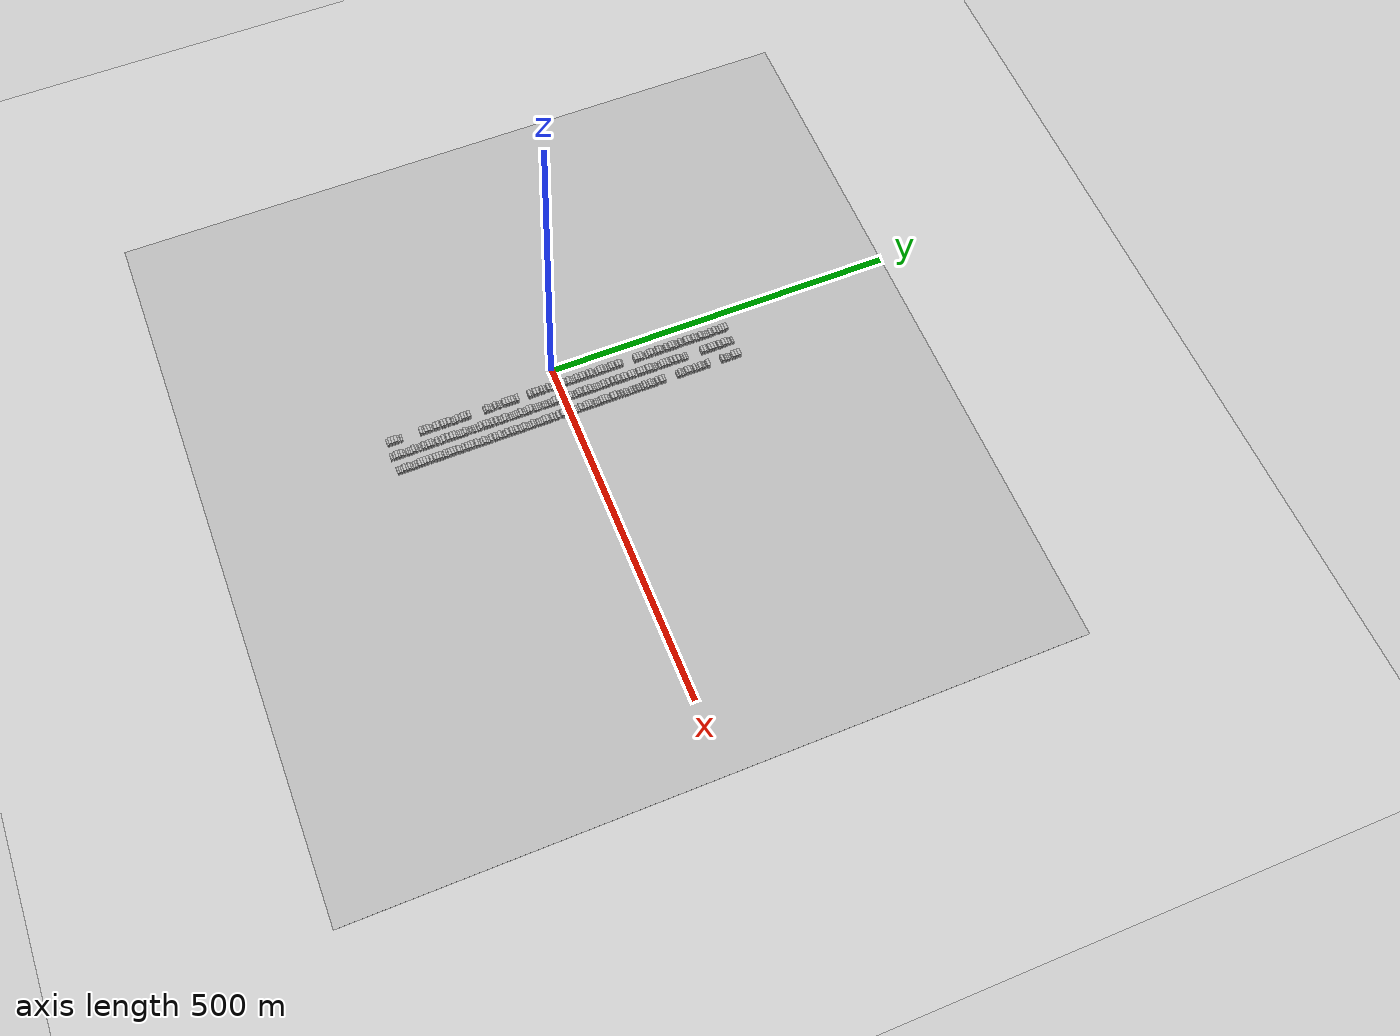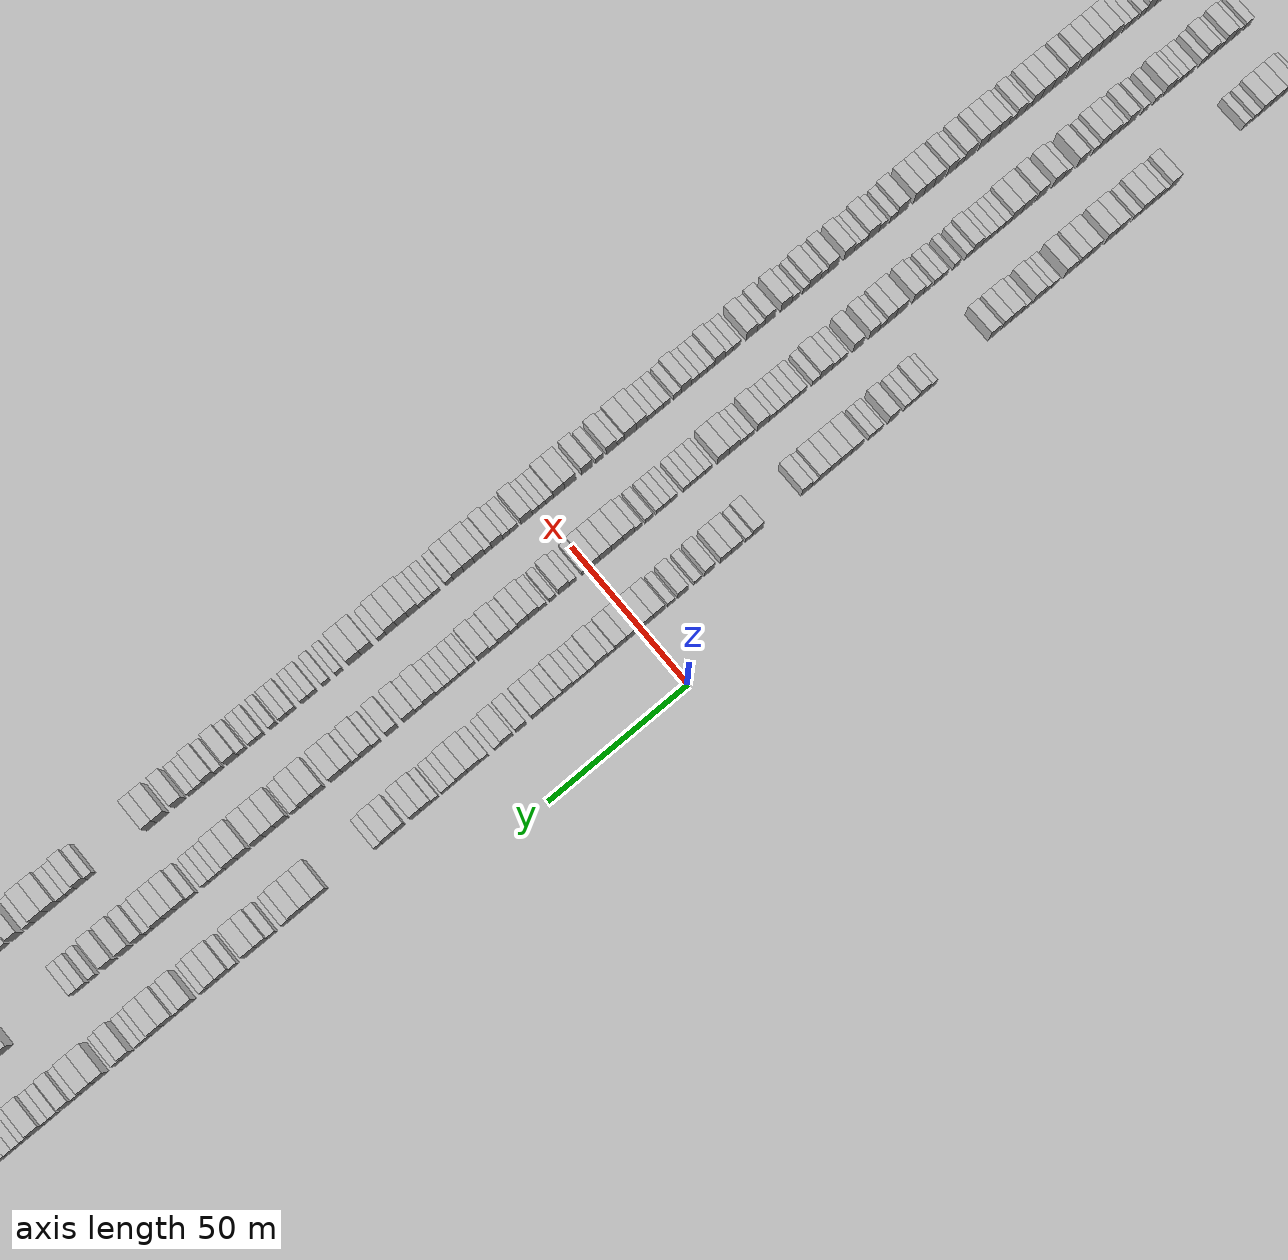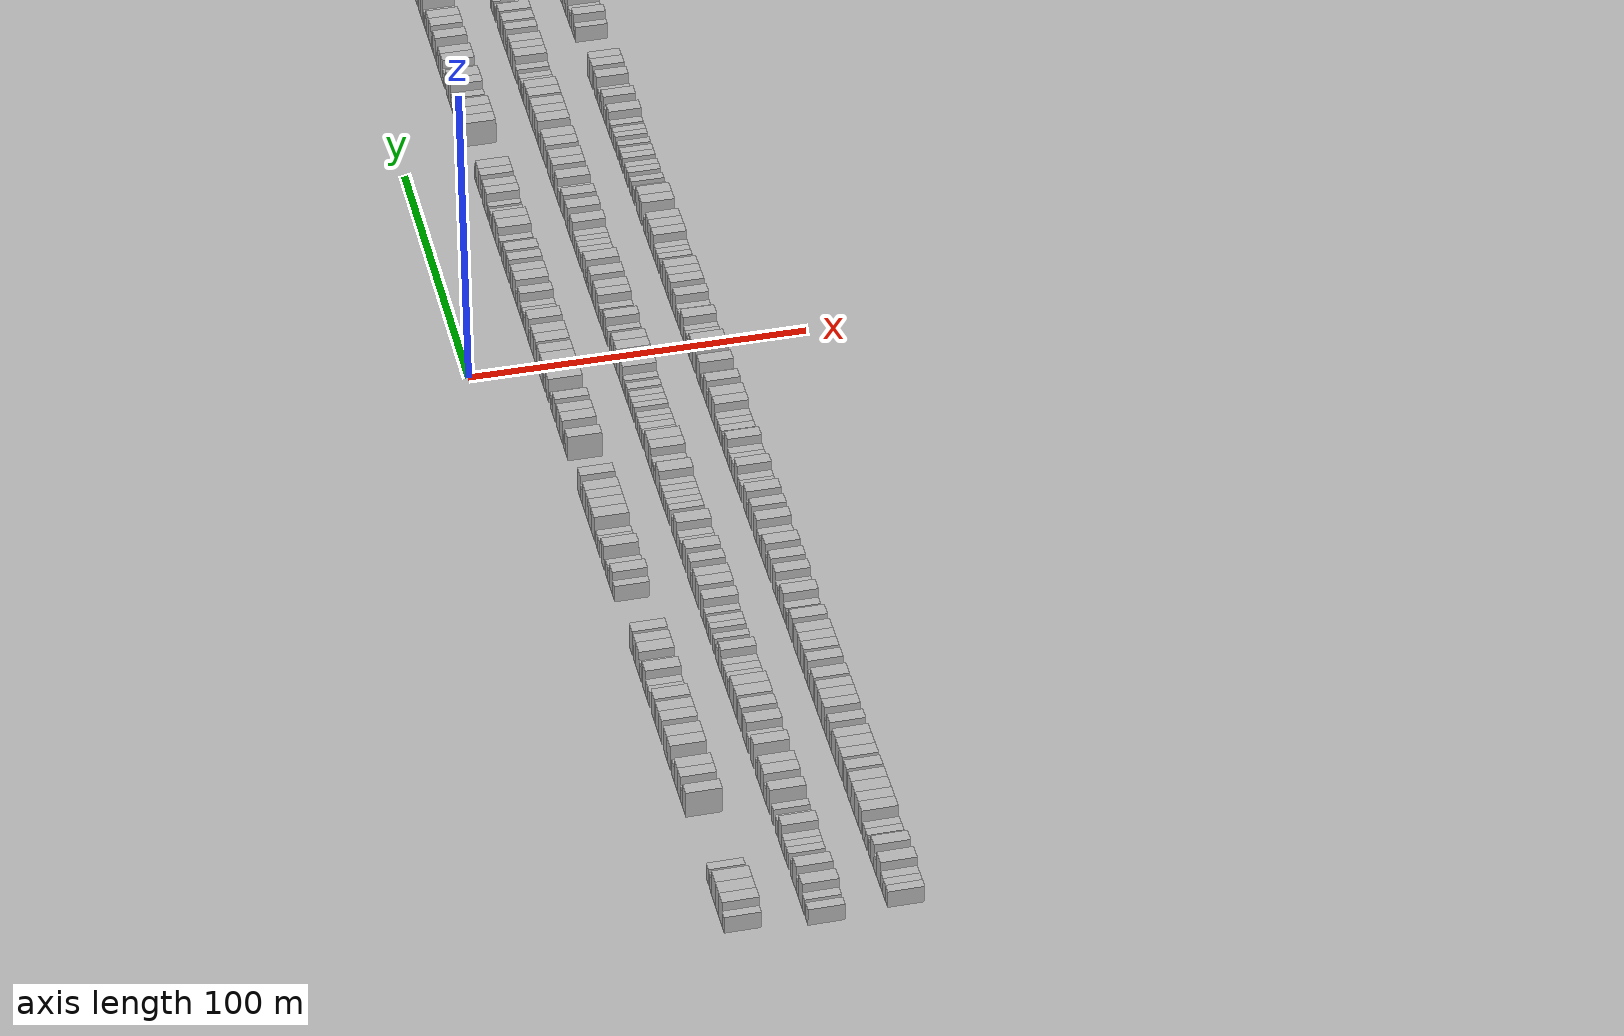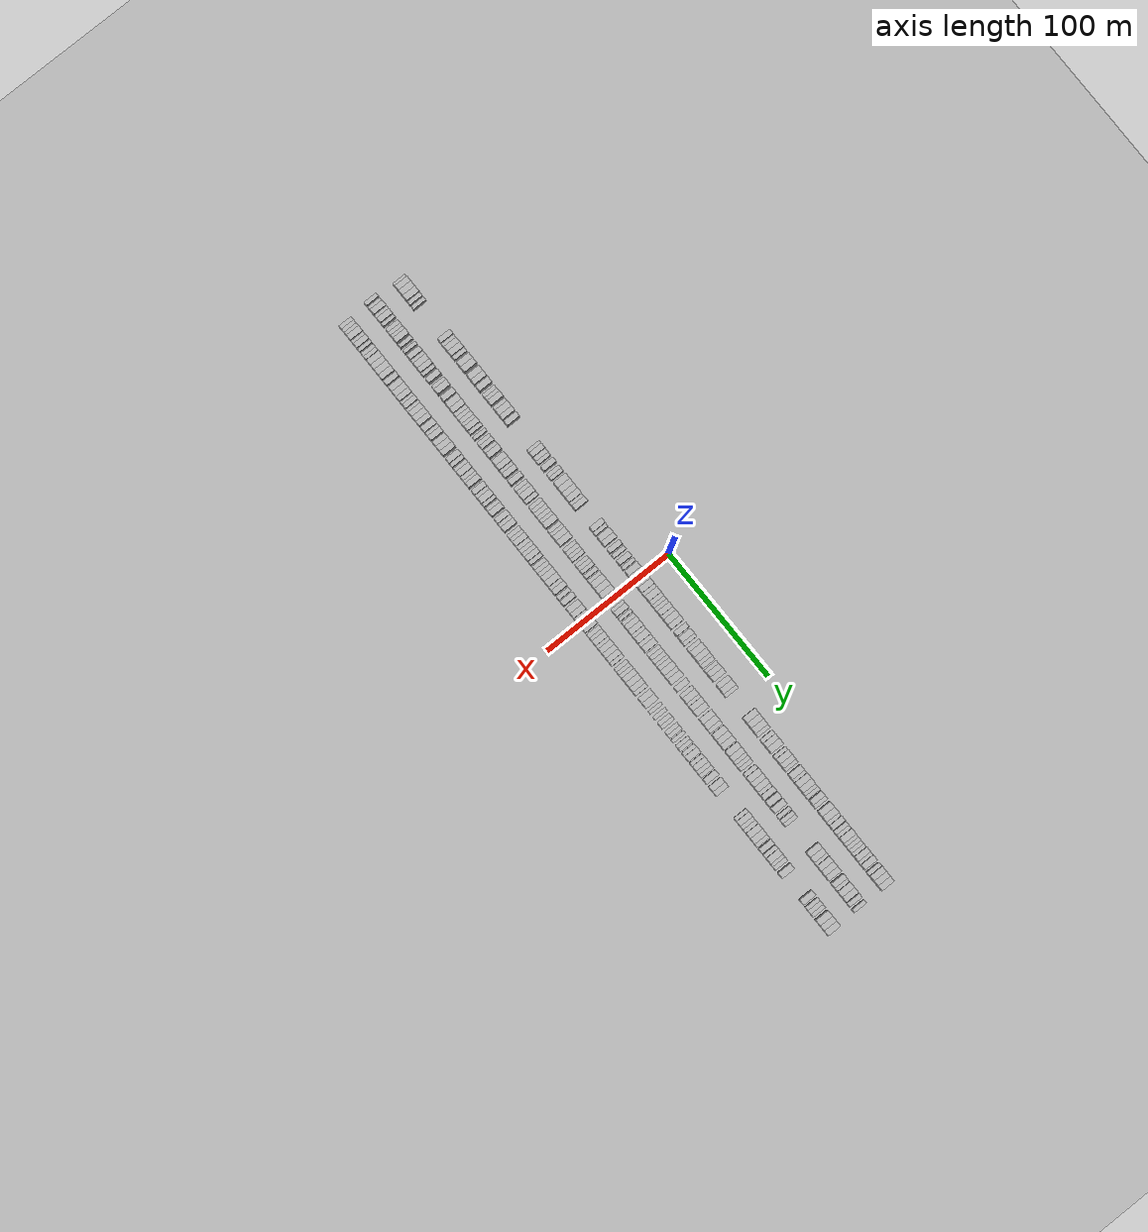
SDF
<?xml version="1.0" encoding="utf-8"?>

<sdf version="1.6">

   <world name="default">

      <gui fullscreen="0">

         <camera name="user_camera">

            <pose>-15 0 4.57585 0 0 0</pose>

            <view_controller>orbit</view_controller>

         </camera>

      </gui>

      <scene>

         <sky>

           <clouds>

             <speed>12</speed>

           </clouds>

         </sky>

         <ambient>0.4 0.4 0.4 1</ambient>

         <background>0.7 0.7 0.7 1</background>

         <shadows>1</shadows>

      </scene>

      <gravity>0 0 -9.8066</gravity>

      <magnetic_field>6e-06 2.3e-05 -4.2e-05</magnetic_field>

      <physics default="0" name="default_physics" type="ode">

         <ode>

            <solver>

               <type>quick</type>

               <iters>10</iters>

               <sor>1.0</sor>

               <use_dynamic_moi_rescaling>0</use_dynamic_moi_rescaling>

            </solver>

            <constraints>

               <cfm>0</cfm>

               <erp>0.2</erp>

               <contact_max_correcting_vel>100</contact_max_correcting_vel>

               <contact_surface_layer>0.001</contact_surface_layer>

            </constraints>

         </ode>

         <max_step_size>0.004</max_step_size>

         <real_time_factor>1</real_time_factor>

         <real_time_update_rate>250</real_time_update_rate>

      </physics>

      <light name="sun" type="directional">

         <cast_shadows>1</cast_shadows>

         <pose>0 0 10 0 0 0</pose>

         <diffuse>0.8 0.8 0.8 1</diffuse>

         <specular>0.2 0.2 0.2 1</specular>

         <attenuation>

            <range>1000</range>

            <constant>0.9</constant>

            <linear>0.01</linear>

            <quadratic>0.001</quadratic>

         </attenuation>

         <direction>-0.5 0.1 -0.9</direction>

      </light>

      <include>

         <name>ground_plane_1</name>

         <uri>model://HANNAS_ground_plane</uri>

         <pose>0 0 0  0 0 0</pose>

      </include>

      <include>

         <name>ground_plane_2</name>

         <uri>model://HANNAS_ground_plane</uri>

         <pose>100 0 0  0 0 0</pose>

      </include>

      <model name="building_1">

         <static>1</static>

         <pose frame="">25.0000 -244.7175 0 0.000000 0.000000 0.000000</pose>

         <link name="link">

            <pose frame="">0 0 3.00 0 0 0</pose>

            <collision name="collision">

               <geometry>

                  <box>

                     <size>10.0000 2.5651 6.0000</size>

                  </box>

               </geometry>

               <max_contacts>10</max_contacts>

               <surface>

                  <contact>

                     <ode/>

                  </contact>

                  <bounce/>

                  <friction>

                     <torsional>

                        <ode/>

                     </torsional>

                     <ode/>

                  </friction>

               </surface>

            </collision>

            <visual name="visual">

               <cast_shadows>0</cast_shadows>

               <geometry>

                  <box>

                     <size>10.0000 2.5651 6.0000</size>

                  </box>

               </geometry>

               <material>

                  <script>

                     <uri>model://HANNAS_wall/materials/scripts</uri>

                     <uri>model://HANNAS_wall/materials/textures</uri>

                     <name>vrc/HANNAS_wall</name>

                  </script>

               </material>

            </visual>

            <self_collide>0</self_collide>

            <enable_wind>0</enable_wind>

            <kinematic>0</kinematic>

         </link>

      </model>

      <model name="building_2">

         <static>1</static>

         <pose frame="">25.0000 -241.5264 0 0.000000 0.000000 0.000000</pose>

         <link name="link">

            <pose frame="">0 0 4.50 0 0 0</pose>

            <collision name="collision">

               <geometry>

                  <box>

                     <size>10.0000 3.8170 9.0000</size>

                  </box>

               </geometry>

               <max_contacts>10</max_contacts>

               <surface>

                  <contact>

                     <ode/>

                  </contact>

                  <bounce/>

                  <friction>

                     <torsional>

                        <ode/>

                     </torsional>

                     <ode/>

                  </friction>

               </surface>

            </collision>

            <visual name="visual">

               <cast_shadows>0</cast_shadows>

               <geometry>

                  <box>

                     <size>10.0000 3.8170 9.0000</size>

                  </box>

               </geometry>

               <material>

                  <script>

                     <uri>model://HANNAS_wall/materials/scripts</uri>

                     <uri>model://HANNAS_wall/materials/textures</uri>

                     <name>vrc/HANNAS_wall</name>

                  </script>

               </material>

            </visual>

            <self_collide>0</self_collide>

            <enable_wind>0</enable_wind>

            <kinematic>0</kinematic>

         </link>

      </model>

      <model name="building_3">

         <static>1</static>

         <pose frame="">25.0000 -237.4763 0 0.000000 0.000000 0.000000</pose>

         <link name="link">

            <pose frame="">0 0 4.50 0 0 0</pose>

            <collision name="collision">

               <geometry>

                  <box>

                     <size>10.0000 4.2832 9.0000</size>

                  </box>

               </geometry>

               <max_contacts>10</max_contacts>

               <surface>

                  <contact>

                     <ode/>

                  </contact>

                  <bounce/>

                  <friction>

                     <torsional>

                        <ode/>

                     </torsional>

                     <ode/>

                  </friction>

               </surface>

            </collision>

            <visual name="visual">

               <cast_shadows>0</cast_shadows>

               <geometry>

                  <box>

                     <size>10.0000 4.2832 9.0000</size>

                  </box>

               </geometry>

               <material>

                  <script>

                     <uri>model://HANNAS_wall/materials/scripts</uri>

                     <uri>model://HANNAS_wall/materials/textures</uri>

                     <name>vrc/HANNAS_wall</name>

                  </script>

               </material>

            </visual>

            <self_collide>0</self_collide>

            <enable_wind>0</enable_wind>

            <kinematic>0</kinematic>

         </link>

      </model>

      <model name="building_4">

         <static>1</static>

         <pose frame="">25.0000 -233.0855 0 0.000000 0.000000 0.000000</pose>

         <link name="link">

            <pose frame="">0 0 4.50 0 0 0</pose>

            <collision name="collision">

               <geometry>

                  <box>

                     <size>10.0000 4.4983 9.0000</size>

                  </box>

               </geometry>

               <max_contacts>10</max_contacts>

               <surface>

                  <contact>

                     <ode/>

                  </contact>

                  <bounce/>

                  <friction>

                     <torsional>

                        <ode/>

                     </torsional>

                     <ode/>

                  </friction>

               </surface>

            </collision>

            <visual name="visual">

               <cast_shadows>0</cast_shadows>

               <geometry>

                  <box>

                     <size>10.0000 4.4983 9.0000</size>

                  </box>

               </geometry>

               <material>

                  <script>

                     <uri>model://HANNAS_wall/materials/scripts</uri>

                     <uri>model://HANNAS_wall/materials/textures</uri>

                     <name>vrc/HANNAS_wall</name>

                  </script>

               </material>

            </visual>

            <self_collide>0</self_collide>

            <enable_wind>0</enable_wind>

            <kinematic>0</kinematic>

         </link>

      </model>

      <model name="building_5">

         <static>1</static>

         <pose frame="">25.0000 -229.4291 0 0.000000 0.000000 0.000000</pose>

         <link name="link">

            <pose frame="">0 0 3.00 0 0 0</pose>

            <collision name="collision">

               <geometry>

                  <box>

                     <size>10.0000 2.8145 6.0000</size>

                  </box>

               </geometry>

               <max_contacts>10</max_contacts>

               <surface>

                  <contact>

                     <ode/>

                  </contact>

                  <bounce/>

                  <friction>

                     <torsional>

                        <ode/>

                     </torsional>

                     <ode/>

                  </friction>

               </surface>

            </collision>

            <visual name="visual">

               <cast_shadows>0</cast_shadows>

               <geometry>

                  <box>

                     <size>10.0000 2.8145 6.0000</size>

                  </box>

               </geometry>

               <material>

                  <script>

                     <uri>model://HANNAS_wall/materials/scripts</uri>

                     <uri>model://HANNAS_wall/materials/textures</uri>

                     <name>vrc/HANNAS_wall</name>

                  </script>

               </material>

            </visual>

            <self_collide>0</self_collide>

            <enable_wind>0</enable_wind>

            <kinematic>0</kinematic>

         </link>

      </model>

      <model name="building_6">

         <static>1</static>

         <pose frame="">25.0000 -225.6760 0 0.000000 0.000000 0.000000</pose>

         <link name="link">

            <pose frame="">0 0 3.00 0 0 0</pose>

            <collision name="collision">

               <geometry>

                  <box>

                     <size>10.0000 2.6918 6.0000</size>

                  </box>

               </geometry>

               <max_contacts>10</max_contacts>

               <surface>

                  <contact>

                     <ode/>

                  </contact>

                  <bounce/>

                  <friction>

                     <torsional>

                        <ode/>

                     </torsional>

                     <ode/>

                  </friction>

               </surface>

            </collision>

            <visual name="visual">

               <cast_shadows>0</cast_shadows>

               <geometry>

                  <box>

                     <size>10.0000 2.6918 6.0000</size>

                  </box>

               </geometry>

               <material>

                  <script>

                     <uri>model://HANNAS_wall/materials/scripts</uri>

                     <uri>model://HANNAS_wall/materials/textures</uri>

                     <name>vrc/HANNAS_wall</name>

                  </script>

               </material>

            </visual>

            <self_collide>0</self_collide>

            <enable_wind>0</enable_wind>

            <kinematic>0</kinematic>

         </link>

      </model>

      <model name="building_7">

         <static>1</static>

         <pose frame="">25.0000 -197.6810 0 0.000000 0.000000 0.000000</pose>

         <link name="link">

            <pose frame="">0 0 4.50 0 0 0</pose>

            <collision name="collision">

               <geometry>

                  <box>

                     <size>10.0000 3.7661 9.0000</size>

                  </box>

               </geometry>

               <max_contacts>10</max_contacts>

               <surface>

                  <contact>

                     <ode/>

                  </contact>

                  <bounce/>

                  <friction>

                     <torsional>

                        <ode/>

                     </torsional>

                     <ode/>

                  </friction>

               </surface>

            </collision>

            <visual name="visual">

               <cast_shadows>0</cast_shadows>

               <geometry>

                  <box>

                     <size>10.0000 3.7661 9.0000</size>

                  </box>

               </geometry>

               <material>

                  <script>

                     <uri>model://HANNAS_wall/materials/scripts</uri>

                     <uri>model://HANNAS_wall/materials/textures</uri>

                     <name>vrc/HANNAS_wall</name>

                  </script>

               </material>

            </visual>

            <self_collide>0</self_collide>

            <enable_wind>0</enable_wind>

            <kinematic>0</kinematic>

         </link>

      </model>

      <model name="building_8">

         <static>1</static>

         <pose frame="">25.0000 -194.3592 0 0.000000 0.000000 0.000000</pose>

         <link name="link">

            <pose frame="">0 0 3.00 0 0 0</pose>

            <collision name="collision">

               <geometry>

                  <box>

                     <size>10.0000 2.8775 6.0000</size>

                  </box>

               </geometry>

               <max_contacts>10</max_contacts>

               <surface>

                  <contact>

                     <ode/>

                  </contact>

                  <bounce/>

                  <friction>

                     <torsional>

                        <ode/>

                     </torsional>

                     <ode/>

                  </friction>

               </surface>

            </collision>

            <visual name="visual">

               <cast_shadows>0</cast_shadows>

               <geometry>

                  <box>

                     <size>10.0000 2.8775 6.0000</size>

                  </box>

               </geometry>

               <material>

                  <script>

                     <uri>model://HANNAS_wall/materials/scripts</uri>

                     <uri>model://HANNAS_wall/materials/textures</uri>

                     <name>vrc/HANNAS_wall</name>

                  </script>

               </material>

            </visual>

            <self_collide>0</self_collide>

            <enable_wind>0</enable_wind>

            <kinematic>0</kinematic>

         </link>

      </model>

      <model name="building_9">

         <static>1</static>

         <pose frame="">25.0000 -191.0394 0 0.000000 0.000000 0.000000</pose>

         <link name="link">

            <pose frame="">0 0 4.50 0 0 0</pose>

            <collision name="collision">

               <geometry>

                  <box>

                     <size>10.0000 3.7622 9.0000</size>

                  </box>

               </geometry>

               <max_contacts>10</max_contacts>

               <surface>

                  <contact>

                     <ode/>

                  </contact>

                  <bounce/>

                  <friction>

                     <torsional>

                        <ode/>

                     </torsional>

                     <ode/>

                  </friction>

               </surface>

            </collision>

            <visual name="visual">

               <cast_shadows>0</cast_shadows>

               <geometry>

                  <box>

                     <size>10.0000 3.7622 9.0000</size>

                  </box>

               </geometry>

               <material>

                  <script>

                     <uri>model://HANNAS_wall/materials/scripts</uri>

                     <uri>model://HANNAS_wall/materials/textures</uri>

                     <name>vrc/HANNAS_wall</name>

                  </script>

               </material>

            </visual>

            <self_collide>0</self_collide>

            <enable_wind>0</enable_wind>

            <kinematic>0</kinematic>

         </link>

      </model>

      <model name="building_10">

         <static>1</static>

         <pose frame="">25.0000 -187.0936 0 0.000000 0.000000 0.000000</pose>

         <link name="link">

            <pose frame="">0 0 4.50 0 0 0</pose>

            <collision name="collision">

               <geometry>

                  <box>

                     <size>10.0000 4.1294 9.0000</size>

                  </box>

               </geometry>

               <max_contacts>10</max_contacts>

               <surface>

                  <contact>

                     <ode/>

                  </contact>

                  <bounce/>

                  <friction>

                     <torsional>

                        <ode/>

                     </torsional>

                     <ode/>

                  </friction>

               </surface>

            </collision>

            <visual name="visual">

               <cast_shadows>0</cast_shadows>

               <geometry>

                  <box>

                     <size>10.0000 4.1294 9.0000</size>

                  </box>

               </geometry>

               <material>

                  <script>

                     <uri>model://HANNAS_wall/materials/scripts</uri>

                     <uri>model://HANNAS_wall/materials/textures</uri>

                     <name>vrc/HANNAS_wall</name>

                  </script>

               </material>

            </visual>

            <self_collide>0</self_collide>

            <enable_wind>0</enable_wind>

            <kinematic>0</kinematic>

         </link>

      </model>

      <model name="building_11">

         <static>1</static>

         <pose frame="">25.0000 -183.5740 0 0.000000 0.000000 0.000000</pose>

         <link name="link">

            <pose frame="">0 0 3.00 0 0 0</pose>

            <collision name="collision">

               <geometry>

                  <box>

                     <size>10.0000 2.9100 6.0000</size>

                  </box>

               </geometry>

               <max_contacts>10</max_contacts>

               <surface>

                  <contact>

                     <ode/>

                  </contact>

                  <bounce/>

                  <friction>

                     <torsional>

                        <ode/>

                     </torsional>

                     <ode/>

                  </friction>

               </surface>

            </collision>

            <visual name="visual">

               <cast_shadows>0</cast_shadows>

               <geometry>

                  <box>

                     <size>10.0000 2.9100 6.0000</size>

                  </box>

               </geometry>

               <material>

                  <script>

                     <uri>model://HANNAS_wall/materials/scripts</uri>

                     <uri>model://HANNAS_wall/materials/textures</uri>

                     <name>vrc/HANNAS_wall</name>

                  </script>

               </material>

            </visual>

            <self_collide>0</self_collide>

            <enable_wind>0</enable_wind>

            <kinematic>0</kinematic>

         </link>

      </model>

      <model name="building_12">

         <static>1</static>

         <pose frame="">25.0000 -178.0836 0 0.000000 0.000000 0.000000</pose>

         <link name="link">

            <pose frame="">0 0 4.50 0 0 0</pose>

            <collision name="collision">

               <geometry>

                  <box>

                     <size>10.0000 4.0708 9.0000</size>

                  </box>

               </geometry>

               <max_contacts>10</max_contacts>

               <surface>

                  <contact>

                     <ode/>

                  </contact>

                  <bounce/>

                  <friction>

                     <torsional>

                        <ode/>

                     </torsional>

                     <ode/>

                  </friction>

               </surface>

            </collision>

            <visual name="visual">

               <cast_shadows>0</cast_shadows>

               <geometry>

                  <box>

                     <size>10.0000 4.0708 9.0000</size>

                  </box>

               </geometry>

               <material>

                  <script>

                     <uri>model://HANNAS_wall/materials/scripts</uri>

                     <uri>model://HANNAS_wall/materials/textures</uri>

                     <name>vrc/HANNAS_wall</name>

                  </script>

               </material>

            </visual>

            <self_collide>0</self_collide>

            <enable_wind>0</enable_wind>

            <kinematic>0</kinematic>

         </link>

      </model>

      <model name="building_13">

         <static>1</static>

         <pose frame="">25.0000 -173.8300 0 0.000000 0.000000 0.000000</pose>

         <link name="link">

            <pose frame="">0 0 4.50 0 0 0</pose>

            <collision name="collision">

               <geometry>

                  <box>

                     <size>10.0000 4.4364 9.0000</size>

                  </box>

               </geometry>

               <max_contacts>10</max_contacts>

               <surface>

                  <contact>

                     <ode/>

                  </contact>

                  <bounce/>

                  <friction>

                     <torsional>

                        <ode/>

                     </torsional>

                     <ode/>

                  </friction>

               </surface>

            </collision>

            <visual name="visual">

               <cast_shadows>0</cast_shadows>

               <geometry>

                  <box>

                     <size>10.0000 4.4364 9.0000</size>

                  </box>

               </geometry>

               <material>

                  <script>

                     <uri>model://HANNAS_wall/materials/scripts</uri>

                     <uri>model://HANNAS_wall/materials/textures</uri>

                     <name>vrc/HANNAS_wall</name>

                  </script>

               </material>

            </visual>

            <self_collide>0</self_collide>

            <enable_wind>0</enable_wind>

            <kinematic>0</kinematic>

         </link>

      </model>

      <model name="building_14">

         <static>1</static>

         <pose frame="">25.0000 -167.5434 0 0.000000 0.000000 0.000000</pose>

         <link name="link">

            <pose frame="">0 0 4.50 0 0 0</pose>

            <collision name="collision">

               <geometry>

                  <box>

                     <size>10.0000 4.1368 9.0000</size>

                  </box>

               </geometry>

               <max_contacts>10</max_contacts>

               <surface>

                  <contact>

                     <ode/>

                  </contact>

                  <bounce/>

                  <friction>

                     <torsional>

                        <ode/>

                     </torsional>

                     <ode/>

                  </friction>

               </surface>

            </collision>

            <visual name="visual">

               <cast_shadows>0</cast_shadows>

               <geometry>

                  <box>

                     <size>10.0000 4.1368 9.0000</size>

                  </box>

               </geometry>

               <material>

                  <script>

                     <uri>model://HANNAS_wall/materials/scripts</uri>

                     <uri>model://HANNAS_wall/materials/textures</uri>

                     <name>vrc/HANNAS_wall</name>

                  </script>

               </material>

            </visual>

            <self_collide>0</self_collide>

            <enable_wind>0</enable_wind>

            <kinematic>0</kinematic>

         </link>

      </model>

      <model name="building_15">

         <static>1</static>

         <pose frame="">25.0000 -163.4816 0 0.000000 0.000000 0.000000</pose>

         <link name="link">

            <pose frame="">0 0 4.50 0 0 0</pose>

            <collision name="collision">

               <geometry>

                  <box>

                     <size>10.0000 3.9867 9.0000</size>

                  </box>

               </geometry>

               <max_contacts>10</max_contacts>

               <surface>

                  <contact>

                     <ode/>

                  </contact>

                  <bounce/>

                  <friction>

                     <torsional>

                        <ode/>

                     </torsional>

                     <ode/>

                  </friction>

               </surface>

            </collision>

            <visual name="visual">

               <cast_shadows>0</cast_shadows>

               <geometry>

                  <box>

                     <size>10.0000 3.9867 9.0000</size>

                  </box>

               </geometry>

               <material>

                  <script>

                     <uri>model://HANNAS_wall/materials/scripts</uri>

                     <uri>model://HANNAS_wall/materials/textures</uri>

                     <name>vrc/HANNAS_wall</name>

                  </script>

               </material>

            </visual>

            <self_collide>0</self_collide>

            <enable_wind>0</enable_wind>

            <kinematic>0</kinematic>

         </link>

      </model>

      <model name="building_16">

         <static>1</static>

         <pose frame="">25.0000 -158.2606 0 0.000000 0.000000 0.000000</pose>

         <link name="link">

            <pose frame="">0 0 4.50 0 0 0</pose>

            <collision name="collision">

               <geometry>

                  <box>

                     <size>10.0000 4.4554 9.0000</size>

                  </box>

               </geometry>

               <max_contacts>10</max_contacts>

               <surface>

                  <contact>

                     <ode/>

                  </contact>

                  <bounce/>

                  <friction>

                     <torsional>

                        <ode/>

                     </torsional>

                     <ode/>

                  </friction>

               </surface>

            </collision>

            <visual name="visual">

               <cast_shadows>0</cast_shadows>

               <geometry>

                  <box>

                     <size>10.0000 4.4554 9.0000</size>

                  </box>

               </geometry>

               <material>

                  <script>

                     <uri>model://HANNAS_wall/materials/scripts</uri>

                     <uri>model://HANNAS_wall/materials/textures</uri>

                     <name>vrc/HANNAS_wall</name>

                  </script>

               </material>

            </visual>

            <self_collide>0</self_collide>

            <enable_wind>0</enable_wind>

            <kinematic>0</kinematic>

         </link>

      </model>

      <model name="building_17">

         <static>1</static>

         <pose frame="">25.0000 -152.6770 0 0.000000 0.000000 0.000000</pose>

         <link name="link">

            <pose frame="">0 0 3.00 0 0 0</pose>

            <collision name="collision">

               <geometry>

                  <box>

                     <size>10.0000 2.7118 6.0000</size>

                  </box>

               </geometry>

               <max_contacts>10</max_contacts>

               <surface>

                  <contact>

                     <ode/>

                  </contact>

                  <bounce/>

                  <friction>

                     <torsional>

                        <ode/>

                     </torsional>

                     <ode/>

                  </friction>

               </surface>

            </collision>

            <visual name="visual">

               <cast_shadows>0</cast_shadows>

               <geometry>

                  <box>

                     <size>10.0000 2.7118 6.0000</size>

                  </box>

               </geometry>

               <material>

                  <script>

                     <uri>model://HANNAS_wall/materials/scripts</uri>

                     <uri>model://HANNAS_wall/materials/textures</uri>

                     <name>vrc/HANNAS_wall</name>

                  </script>

               </material>

            </visual>

            <self_collide>0</self_collide>

            <enable_wind>0</enable_wind>

            <kinematic>0</kinematic>

         </link>

      </model>

      <model name="building_18">

         <static>1</static>

         <pose frame="">25.0000 -149.9093 0 0.000000 0.000000 0.000000</pose>

         <link name="link">

            <pose frame="">0 0 3.00 0 0 0</pose>

            <collision name="collision">

               <geometry>

                  <box>

                     <size>10.0000 2.8237 6.0000</size>

                  </box>

               </geometry>

               <max_contacts>10</max_contacts>

               <surface>

                  <contact>

                     <ode/>

                  </contact>

                  <bounce/>

                  <friction>

                     <torsional>

                        <ode/>

                     </torsional>

                     <ode/>

                  </friction>

               </surface>

            </collision>

            <visual name="visual">

               <cast_shadows>0</cast_shadows>

               <geometry>

                  <box>

                     <size>10.0000 2.8237 6.0000</size>

                  </box>

               </geometry>

               <material>

                  <script>

                     <uri>model://HANNAS_wall/materials/scripts</uri>

                     <uri>model://HANNAS_wall/materials/textures</uri>

                     <name>vrc/HANNAS_wall</name>

                  </script>

               </material>

            </visual>

            <self_collide>0</self_collide>

            <enable_wind>0</enable_wind>

            <kinematic>0</kinematic>

         </link>

      </model>

      <model name="building_19">

         <static>1</static>

         <pose frame="">25.0000 -146.4333 0 0.000000 0.000000 0.000000</pose>

         <link name="link">

            <pose frame="">0 0 4.50 0 0 0</pose>

            <collision name="collision">

               <geometry>

                  <box>

                     <size>10.0000 4.1282 9.0000</size>

                  </box>

               </geometry>

               <max_contacts>10</max_contacts>

               <surface>

                  <contact>

                     <ode/>

                  </contact>

                  <bounce/>

                  <friction>

                     <torsional>

                        <ode/>

                     </torsional>

                     <ode/>

                  </friction>

               </surface>

            </collision>

            <visual name="visual">

               <cast_shadows>0</cast_shadows>

               <geometry>

                  <box>

                     <size>10.0000 4.1282 9.0000</size>

                  </box>

               </geometry>

               <material>

                  <script>

                     <uri>model://HANNAS_wall/materials/scripts</uri>

                     <uri>model://HANNAS_wall/materials/textures</uri>

                     <name>vrc/HANNAS_wall</name>

                  </script>

               </material>

            </visual>

            <self_collide>0</self_collide>

            <enable_wind>0</enable_wind>

            <kinematic>0</kinematic>

         </link>

      </model>

      <model name="building_20">

         <static>1</static>

         <pose frame="">25.0000 -141.9119 0 0.000000 0.000000 0.000000</pose>

         <link name="link">

            <pose frame="">0 0 3.00 0 0 0</pose>

            <collision name="collision">

               <geometry>

                  <box>

                     <size>10.0000 2.9148 6.0000</size>

                  </box>

               </geometry>

               <max_contacts>10</max_contacts>

               <surface>

                  <contact>

                     <ode/>

                  </contact>

                  <bounce/>

                  <friction>

                     <torsional>

                        <ode/>

                     </torsional>

                     <ode/>

                  </friction>

               </surface>

            </collision>

            <visual name="visual">

               <cast_shadows>0</cast_shadows>

               <geometry>

                  <box>

                     <size>10.0000 2.9148 6.0000</size>

                  </box>

               </geometry>

               <material>

                  <script>

                     <uri>model://HANNAS_wall/materials/scripts</uri>

                     <uri>model://HANNAS_wall/materials/textures</uri>

                     <name>vrc/HANNAS_wall</name>

                  </script>

               </material>

            </visual>

            <self_collide>0</self_collide>

            <enable_wind>0</enable_wind>

            <kinematic>0</kinematic>

         </link>

      </model>

      <model name="building_21">

         <static>1</static>

         <pose frame="">25.0000 -138.3093 0 0.000000 0.000000 0.000000</pose>

         <link name="link">

            <pose frame="">0 0 4.50 0 0 0</pose>

            <collision name="collision">

               <geometry>

                  <box>

                     <size>10.0000 4.2903 9.0000</size>

                  </box>

               </geometry>

               <max_contacts>10</max_contacts>

               <surface>

                  <contact>

                     <ode/>

                  </contact>

                  <bounce/>

                  <friction>

                     <torsional>

                        <ode/>

                     </torsional>

                     <ode/>

                  </friction>

               </surface>

            </collision>

            <visual name="visual">

               <cast_shadows>0</cast_shadows>

               <geometry>

                  <box>

                     <size>10.0000 4.2903 9.0000</size>

                  </box>

               </geometry>

               <material>

                  <script>

                     <uri>model://HANNAS_wall/materials/scripts</uri>

                     <uri>model://HANNAS_wall/materials/textures</uri>

                     <name>vrc/HANNAS_wall</name>

                  </script>

               </material>

            </visual>

            <self_collide>0</self_collide>

            <enable_wind>0</enable_wind>

            <kinematic>0</kinematic>

         </link>

      </model>

      <model name="building_22">

         <static>1</static>

         <pose frame="">25.0000 -134.3627 0 0.000000 0.000000 0.000000</pose>

         <link name="link">

            <pose frame="">0 0 4.50 0 0 0</pose>

            <collision name="collision">

               <geometry>

                  <box>

                     <size>10.0000 3.6030 9.0000</size>

                  </box>

               </geometry>

               <max_contacts>10</max_contacts>

               <surface>

                  <contact>

                     <ode/>

                  </contact>

                  <bounce/>

                  <friction>

                     <torsional>

                        <ode/>

                     </torsional>

                     <ode/>

                  </friction>

               </surface>

            </collision>

            <visual name="visual">

               <cast_shadows>0</cast_shadows>

               <geometry>

                  <box>

                     <size>10.0000 3.6030 9.0000</size>

                  </box>

               </geometry>

               <material>

                  <script>

                     <uri>model://HANNAS_wall/materials/scripts</uri>

                     <uri>model://HANNAS_wall/materials/textures</uri>

                     <name>vrc/HANNAS_wall</name>

                  </script>

               </material>

            </visual>

            <self_collide>0</self_collide>

            <enable_wind>0</enable_wind>

            <kinematic>0</kinematic>

         </link>

      </model>

      <model name="building_23">

         <static>1</static>

         <pose frame="">25.0000 -129.6482 0 0.000000 0.000000 0.000000</pose>

         <link name="link">

            <pose frame="">0 0 4.50 0 0 0</pose>

            <collision name="collision">

               <geometry>

                  <box>

                     <size>10.0000 3.8260 9.0000</size>

                  </box>

               </geometry>

               <max_contacts>10</max_contacts>

               <surface>

                  <contact>

                     <ode/>

                  </contact>

                  <bounce/>

                  <friction>

                     <torsional>

                        <ode/>

                     </torsional>

                     <ode/>

                  </friction>

               </surface>

            </collision>

            <visual name="visual">

               <cast_shadows>0</cast_shadows>

               <geometry>

                  <box>

                     <size>10.0000 3.8260 9.0000</size>

                  </box>

               </geometry>

               <material>

                  <script>

                     <uri>model://HANNAS_wall/materials/scripts</uri>

                     <uri>model://HANNAS_wall/materials/textures</uri>

                     <name>vrc/HANNAS_wall</name>

                  </script>

               </material>

            </visual>

            <self_collide>0</self_collide>

            <enable_wind>0</enable_wind>

            <kinematic>0</kinematic>

         </link>

      </model>

      <model name="building_24">

         <static>1</static>

         <pose frame="">25.0000 -106.8678 0 0.000000 0.000000 0.000000</pose>

         <link name="link">

            <pose frame="">0 0 3.00 0 0 0</pose>

            <collision name="collision">

               <geometry>

                  <box>

                     <size>10.0000 2.5782 6.0000</size>

                  </box>

               </geometry>

               <max_contacts>10</max_contacts>

               <surface>

                  <contact>

                     <ode/>

                  </contact>

                  <bounce/>

                  <friction>

                     <torsional>

                        <ode/>

                     </torsional>

                     <ode/>

                  </friction>

               </surface>

            </collision>

            <visual name="visual">

               <cast_shadows>0</cast_shadows>

               <geometry>

                  <box>

                     <size>10.0000 2.5782 6.0000</size>

                  </box>

               </geometry>

               <material>

                  <script>

                     <uri>model://HANNAS_wall/materials/scripts</uri>

                     <uri>model://HANNAS_wall/materials/textures</uri>

                     <name>vrc/HANNAS_wall</name>

                  </script>

               </material>

            </visual>

            <self_collide>0</self_collide>

            <enable_wind>0</enable_wind>

            <kinematic>0</kinematic>

         </link>

      </model>

      <model name="building_25">

         <static>1</static>

         <pose frame="">25.0000 -103.6385 0 0.000000 0.000000 0.000000</pose>

         <link name="link">

            <pose frame="">0 0 4.50 0 0 0</pose>

            <collision name="collision">

               <geometry>

                  <box>

                     <size>10.0000 3.8804 9.0000</size>

                  </box>

               </geometry>

               <max_contacts>10</max_contacts>

               <surface>

                  <contact>

                     <ode/>

                  </contact>

                  <bounce/>

                  <friction>

                     <torsional>

                        <ode/>

                     </torsional>

                     <ode/>

                  </friction>

               </surface>

            </collision>

            <visual name="visual">

               <cast_shadows>0</cast_shadows>

               <geometry>

                  <box>

                     <size>10.0000 3.8804 9.0000</size>

                  </box>

               </geometry>

               <material>

                  <script>

                     <uri>model://HANNAS_wall/materials/scripts</uri>

                     <uri>model://HANNAS_wall/materials/textures</uri>

                     <name>vrc/HANNAS_wall</name>

                  </script>

               </material>

            </visual>

            <self_collide>0</self_collide>

            <enable_wind>0</enable_wind>

            <kinematic>0</kinematic>

         </link>

      </model>

      <model name="building_26">

         <static>1</static>

         <pose frame="">25.0000 -100.2035 0 0.000000 0.000000 0.000000</pose>

         <link name="link">

            <pose frame="">0 0 3.00 0 0 0</pose>

            <collision name="collision">

               <geometry>

                  <box>

                     <size>10.0000 2.9895 6.0000</size>

                  </box>

               </geometry>

               <max_contacts>10</max_contacts>

               <surface>

                  <contact>

                     <ode/>

                  </contact>

                  <bounce/>

                  <friction>

                     <torsional>

                        <ode/>

                     </torsional>

                     <ode/>

                  </friction>

               </surface>

            </collision>

            <visual name="visual">

               <cast_shadows>0</cast_shadows>

               <geometry>

                  <box>

                     <size>10.0000 2.9895 6.0000</size>

                  </box>

               </geometry>

               <material>

                  <script>

                     <uri>model://HANNAS_wall/materials/scripts</uri>

                     <uri>model://HANNAS_wall/materials/textures</uri>

                     <name>vrc/HANNAS_wall</name>

                  </script>

               </material>

            </visual>

            <self_collide>0</self_collide>

            <enable_wind>0</enable_wind>

            <kinematic>0</kinematic>

         </link>

      </model>

      <model name="building_27">

         <static>1</static>

         <pose frame="">25.0000 -97.4004 0 0.000000 0.000000 0.000000</pose>

         <link name="link">

            <pose frame="">0 0 3.00 0 0 0</pose>

            <collision name="collision">

               <geometry>

                  <box>

                     <size>10.0000 2.6168 6.0000</size>

                  </box>

               </geometry>

               <max_contacts>10</max_contacts>

               <surface>

                  <contact>

                     <ode/>

                  </contact>

                  <bounce/>

                  <friction>

                     <torsional>

                        <ode/>

                     </torsional>

                     <ode/>

                  </friction>

               </surface>

            </collision>

            <visual name="visual">

               <cast_shadows>0</cast_shadows>

               <geometry>

                  <box>

                     <size>10.0000 2.6168 6.0000</size>

                  </box>

               </geometry>

               <material>

                  <script>

                     <uri>model://HANNAS_wall/materials/scripts</uri>

                     <uri>model://HANNAS_wall/materials/textures</uri>

                     <name>vrc/HANNAS_wall</name>

                  </script>

               </material>

            </visual>

            <self_collide>0</self_collide>

            <enable_wind>0</enable_wind>

            <kinematic>0</kinematic>

         </link>

      </model>

      <model name="building_28">

         <static>1</static>

         <pose frame="">25.0000 -92.1658 0 0.000000 0.000000 0.000000</pose>

         <link name="link">

            <pose frame="">0 0 4.50 0 0 0</pose>

            <collision name="collision">

               <geometry>

                  <box>

                     <size>10.0000 3.8523 9.0000</size>

                  </box>

               </geometry>

               <max_contacts>10</max_contacts>

               <surface>

                  <contact>

                     <ode/>

                  </contact>

                  <bounce/>

                  <friction>

                     <torsional>

                        <ode/>

                     </torsional>

                     <ode/>

                  </friction>

               </surface>

            </collision>

            <visual name="visual">

               <cast_shadows>0</cast_shadows>

               <geometry>

                  <box>

                     <size>10.0000 3.8523 9.0000</size>

                  </box>

               </geometry>

               <material>

                  <script>

                     <uri>model://HANNAS_wall/materials/scripts</uri>

                     <uri>model://HANNAS_wall/materials/textures</uri>

                     <name>vrc/HANNAS_wall</name>

                  </script>

               </material>

            </visual>

            <self_collide>0</self_collide>

            <enable_wind>0</enable_wind>

            <kinematic>0</kinematic>

         </link>

      </model>

      <model name="building_29">

         <static>1</static>

         <pose frame="">25.0000 -86.8846 0 0.000000 0.000000 0.000000</pose>

         <link name="link">

            <pose frame="">0 0 3.00 0 0 0</pose>

            <collision name="collision">

               <geometry>

                  <box>

                     <size>10.0000 2.7101 6.0000</size>

                  </box>

               </geometry>

               <max_contacts>10</max_contacts>

               <surface>

                  <contact>

                     <ode/>

                  </contact>

                  <bounce/>

                  <friction>

                     <torsional>

                        <ode/>

                     </torsional>

                     <ode/>

                  </friction>

               </surface>

            </collision>

            <visual name="visual">

               <cast_shadows>0</cast_shadows>

               <geometry>

                  <box>

                     <size>10.0000 2.7101 6.0000</size>

                  </box>

               </geometry>

               <material>

                  <script>

                     <uri>model://HANNAS_wall/materials/scripts</uri>

                     <uri>model://HANNAS_wall/materials/textures</uri>

                     <name>vrc/HANNAS_wall</name>

                  </script>

               </material>

            </visual>

            <self_collide>0</self_collide>

            <enable_wind>0</enable_wind>

            <kinematic>0</kinematic>

         </link>

      </model>

      <model name="building_30">

         <static>1</static>

         <pose frame="">25.0000 -84.2766 0 0.000000 0.000000 0.000000</pose>

         <link name="link">

            <pose frame="">0 0 3.00 0 0 0</pose>

            <collision name="collision">

               <geometry>

                  <box>

                     <size>10.0000 2.5058 6.0000</size>

                  </box>

               </geometry>

               <max_contacts>10</max_contacts>

               <surface>

                  <contact>

                     <ode/>

                  </contact>

                  <bounce/>

                  <friction>

                     <torsional>

                        <ode/>

                     </torsional>

                     <ode/>

                  </friction>

               </surface>

            </collision>

            <visual name="visual">

               <cast_shadows>0</cast_shadows>

               <geometry>

                  <box>

                     <size>10.0000 2.5058 6.0000</size>

                  </box>

               </geometry>

               <material>

                  <script>

                     <uri>model://HANNAS_wall/materials/scripts</uri>

                     <uri>model://HANNAS_wall/materials/textures</uri>

                     <name>vrc/HANNAS_wall</name>

                  </script>

               </material>

            </visual>

            <self_collide>0</self_collide>

            <enable_wind>0</enable_wind>

            <kinematic>0</kinematic>

         </link>

      </model>

      <model name="building_31">

         <static>1</static>

         <pose frame="">25.0000 -78.8417 0 0.000000 0.000000 0.000000</pose>

         <link name="link">

            <pose frame="">0 0 4.50 0 0 0</pose>

            <collision name="collision">

               <geometry>

                  <box>

                     <size>10.0000 4.3641 9.0000</size>

                  </box>

               </geometry>

               <max_contacts>10</max_contacts>

               <surface>

                  <contact>

                     <ode/>

                  </contact>

                  <bounce/>

                  <friction>

                     <torsional>

                        <ode/>

                     </torsional>

                     <ode/>

                  </friction>

               </surface>

            </collision>

            <visual name="visual">

               <cast_shadows>0</cast_shadows>

               <geometry>

                  <box>

                     <size>10.0000 4.3641 9.0000</size>

                  </box>

               </geometry>

               <material>

                  <script>

                     <uri>model://HANNAS_wall/materials/scripts</uri>

                     <uri>model://HANNAS_wall/materials/textures</uri>

                     <name>vrc/HANNAS_wall</name>

                  </script>

               </material>

            </visual>

            <self_collide>0</self_collide>

            <enable_wind>0</enable_wind>

            <kinematic>0</kinematic>

         </link>

      </model>

      <model name="building_32">

         <static>1</static>

         <pose frame="">25.0000 -74.5840 0 0.000000 0.000000 0.000000</pose>

         <link name="link">

            <pose frame="">0 0 4.50 0 0 0</pose>

            <collision name="collision">

               <geometry>

                  <box>

                     <size>10.0000 4.1513 9.0000</size>

                  </box>

               </geometry>

               <max_contacts>10</max_contacts>

               <surface>

                  <contact>

                     <ode/>

                  </contact>

                  <bounce/>

                  <friction>

                     <torsional>

                        <ode/>

                     </torsional>

                     <ode/>

                  </friction>

               </surface>

            </collision>

            <visual name="visual">

               <cast_shadows>0</cast_shadows>

               <geometry>

                  <box>

                     <size>10.0000 4.1513 9.0000</size>

                  </box>

               </geometry>

               <material>

                  <script>

                     <uri>model://HANNAS_wall/materials/scripts</uri>

                     <uri>model://HANNAS_wall/materials/textures</uri>

                     <name>vrc/HANNAS_wall</name>

                  </script>

               </material>

            </visual>

            <self_collide>0</self_collide>

            <enable_wind>0</enable_wind>

            <kinematic>0</kinematic>

         </link>

      </model>

      <model name="building_33">

         <static>1</static>

         <pose frame="">25.0000 -70.6156 0 0.000000 0.000000 0.000000</pose>

         <link name="link">

            <pose frame="">0 0 4.50 0 0 0</pose>

            <collision name="collision">

               <geometry>

                  <box>

                     <size>10.0000 3.7857 9.0000</size>

                  </box>

               </geometry>

               <max_contacts>10</max_contacts>

               <surface>

                  <contact>

                     <ode/>

                  </contact>

                  <bounce/>

                  <friction>

                     <torsional>

                        <ode/>

                     </torsional>

                     <ode/>

                  </friction>

               </surface>

            </collision>

            <visual name="visual">

               <cast_shadows>0</cast_shadows>

               <geometry>

                  <box>

                     <size>10.0000 3.7857 9.0000</size>

                  </box>

               </geometry>

               <material>

                  <script>

                     <uri>model://HANNAS_wall/materials/scripts</uri>

                     <uri>model://HANNAS_wall/materials/textures</uri>

                     <name>vrc/HANNAS_wall</name>

                  </script>

               </material>

            </visual>

            <self_collide>0</self_collide>

            <enable_wind>0</enable_wind>

            <kinematic>0</kinematic>

         </link>

      </model>

      <model name="building_34">

         <static>1</static>

         <pose frame="">25.0000 -66.6662 0 0.000000 0.000000 0.000000</pose>

         <link name="link">

            <pose frame="">0 0 4.50 0 0 0</pose>

            <collision name="collision">

               <geometry>

                  <box>

                     <size>10.0000 4.1130 9.0000</size>

                  </box>

               </geometry>

               <max_contacts>10</max_contacts>

               <surface>

                  <contact>

                     <ode/>

                  </contact>

                  <bounce/>

                  <friction>

                     <torsional>

                        <ode/>

                     </torsional>

                     <ode/>

                  </friction>

               </surface>

            </collision>

            <visual name="visual">

               <cast_shadows>0</cast_shadows>

               <geometry>

                  <box>

                     <size>10.0000 4.1130 9.0000</size>

                  </box>

               </geometry>

               <material>

                  <script>

                     <uri>model://HANNAS_wall/materials/scripts</uri>

                     <uri>model://HANNAS_wall/materials/textures</uri>

                     <name>vrc/HANNAS_wall</name>

                  </script>

               </material>

            </visual>

            <self_collide>0</self_collide>

            <enable_wind>0</enable_wind>

            <kinematic>0</kinematic>

         </link>

      </model>

      <model name="building_35">

         <static>1</static>

         <pose frame="">25.0000 -63.3535 0 0.000000 0.000000 0.000000</pose>

         <link name="link">

            <pose frame="">0 0 3.00 0 0 0</pose>

            <collision name="collision">

               <geometry>

                  <box>

                     <size>10.0000 2.5124 6.0000</size>

                  </box>

               </geometry>

               <max_contacts>10</max_contacts>

               <surface>

                  <contact>

                     <ode/>

                  </contact>

                  <bounce/>

                  <friction>

                     <torsional>

                        <ode/>

                     </torsional>

                     <ode/>

                  </friction>

               </surface>

            </collision>

            <visual name="visual">

               <cast_shadows>0</cast_shadows>

               <geometry>

                  <box>

                     <size>10.0000 2.5124 6.0000</size>

                  </box>

               </geometry>

               <material>

                  <script>

                     <uri>model://HANNAS_wall/materials/scripts</uri>

                     <uri>model://HANNAS_wall/materials/textures</uri>

                     <name>vrc/HANNAS_wall</name>

                  </script>

               </material>

            </visual>

            <self_collide>0</self_collide>

            <enable_wind>0</enable_wind>

            <kinematic>0</kinematic>

         </link>

      </model>

      <model name="building_36">

         <static>1</static>

         <pose frame="">25.0000 -60.1844 0 0.000000 0.000000 0.000000</pose>

         <link name="link">

            <pose frame="">0 0 4.50 0 0 0</pose>

            <collision name="collision">

               <geometry>

                  <box>

                     <size>10.0000 3.8257 9.0000</size>

                  </box>

               </geometry>

               <max_contacts>10</max_contacts>

               <surface>

                  <contact>

                     <ode/>

                  </contact>

                  <bounce/>

                  <friction>

                     <torsional>

                        <ode/>

                     </torsional>

                     <ode/>

                  </friction>

               </surface>

            </collision>

            <visual name="visual">

               <cast_shadows>0</cast_shadows>

               <geometry>

                  <box>

                     <size>10.0000 3.8257 9.0000</size>

                  </box>

               </geometry>

               <material>

                  <script>

                     <uri>model://HANNAS_wall/materials/scripts</uri>

                     <uri>model://HANNAS_wall/materials/textures</uri>

                     <name>vrc/HANNAS_wall</name>

                  </script>

               </material>

            </visual>

            <self_collide>0</self_collide>

            <enable_wind>0</enable_wind>

            <kinematic>0</kinematic>

         </link>

      </model>

      <model name="building_37">

         <static>1</static>

         <pose frame="">25.0000 -42.3587 0 0.000000 0.000000 0.000000</pose>

         <link name="link">

            <pose frame="">0 0 4.50 0 0 0</pose>

            <collision name="collision">

               <geometry>

                  <box>

                     <size>10.0000 3.9419 9.0000</size>

                  </box>

               </geometry>

               <max_contacts>10</max_contacts>

               <surface>

                  <contact>

                     <ode/>

                  </contact>

                  <bounce/>

                  <friction>

                     <torsional>

                        <ode/>

                     </torsional>

                     <ode/>

                  </friction>

               </surface>

            </collision>

            <visual name="visual">

               <cast_shadows>0</cast_shadows>

               <geometry>

                  <box>

                     <size>10.0000 3.9419 9.0000</size>

                  </box>

               </geometry>

               <material>

                  <script>

                     <uri>model://HANNAS_wall/materials/scripts</uri>

                     <uri>model://HANNAS_wall/materials/textures</uri>

                     <name>vrc/HANNAS_wall</name>

                  </script>

               </material>

            </visual>

            <self_collide>0</self_collide>

            <enable_wind>0</enable_wind>

            <kinematic>0</kinematic>

         </link>

      </model>

      <model name="building_38">

         <static>1</static>

         <pose frame="">25.0000 -39.0731 0 0.000000 0.000000 0.000000</pose>

         <link name="link">

            <pose frame="">0 0 3.00 0 0 0</pose>

            <collision name="collision">

               <geometry>

                  <box>

                     <size>10.0000 2.6292 6.0000</size>

                  </box>

               </geometry>

               <max_contacts>10</max_contacts>

               <surface>

                  <contact>

                     <ode/>

                  </contact>

                  <bounce/>

                  <friction>

                     <torsional>

                        <ode/>

                     </torsional>

                     <ode/>

                  </friction>

               </surface>

            </collision>

            <visual name="visual">

               <cast_shadows>0</cast_shadows>

               <geometry>

                  <box>

                     <size>10.0000 2.6292 6.0000</size>

                  </box>

               </geometry>

               <material>

                  <script>

                     <uri>model://HANNAS_wall/materials/scripts</uri>

                     <uri>model://HANNAS_wall/materials/textures</uri>

                     <name>vrc/HANNAS_wall</name>

                  </script>

               </material>

            </visual>

            <self_collide>0</self_collide>

            <enable_wind>0</enable_wind>

            <kinematic>0</kinematic>

         </link>

      </model>

      <model name="building_39">

         <static>1</static>

         <pose frame="">25.0000 -34.6380 0 0.000000 0.000000 0.000000</pose>

         <link name="link">

            <pose frame="">0 0 4.50 0 0 0</pose>

            <collision name="collision">

               <geometry>

                  <box>

                     <size>10.0000 4.2411 9.0000</size>

                  </box>

               </geometry>

               <max_contacts>10</max_contacts>

               <surface>

                  <contact>

                     <ode/>

                  </contact>

                  <bounce/>

                  <friction>

                     <torsional>

                        <ode/>

                     </torsional>

                     <ode/>

                  </friction>

               </surface>

            </collision>

            <visual name="visual">

               <cast_shadows>0</cast_shadows>

               <geometry>

                  <box>

                     <size>10.0000 4.2411 9.0000</size>

                  </box>

               </geometry>

               <material>

                  <script>

                     <uri>model://HANNAS_wall/materials/scripts</uri>

                     <uri>model://HANNAS_wall/materials/textures</uri>

                     <name>vrc/HANNAS_wall</name>

                  </script>

               </material>

            </visual>

            <self_collide>0</self_collide>

            <enable_wind>0</enable_wind>

            <kinematic>0</kinematic>

         </link>

      </model>

      <model name="building_40">

         <static>1</static>

         <pose frame="">25.0000 -30.5647 0 0.000000 0.000000 0.000000</pose>

         <link name="link">

            <pose frame="">0 0 4.50 0 0 0</pose>

            <collision name="collision">

               <geometry>

                  <box>

                     <size>10.0000 3.9054 9.0000</size>

                  </box>

               </geometry>

               <max_contacts>10</max_contacts>

               <surface>

                  <contact>

                     <ode/>

                  </contact>

                  <bounce/>

                  <friction>

                     <torsional>

                        <ode/>

                     </torsional>

                     <ode/>

                  </friction>

               </surface>

            </collision>

            <visual name="visual">

               <cast_shadows>0</cast_shadows>

               <geometry>

                  <box>

                     <size>10.0000 3.9054 9.0000</size>

                  </box>

               </geometry>

               <material>

                  <script>

                     <uri>model://HANNAS_wall/materials/scripts</uri>

                     <uri>model://HANNAS_wall/materials/textures</uri>

                     <name>vrc/HANNAS_wall</name>

                  </script>

               </material>

            </visual>

            <self_collide>0</self_collide>

            <enable_wind>0</enable_wind>

            <kinematic>0</kinematic>

         </link>

      </model>

      <model name="building_41">

         <static>1</static>

         <pose frame="">25.0000 -24.7812 0 0.000000 0.000000 0.000000</pose>

         <link name="link">

            <pose frame="">0 0 4.50 0 0 0</pose>

            <collision name="collision">

               <geometry>

                  <box>

                     <size>10.0000 3.6616 9.0000</size>

                  </box>

               </geometry>

               <max_contacts>10</max_contacts>

               <surface>

                  <contact>

                     <ode/>

                  </contact>

                  <bounce/>

                  <friction>

                     <torsional>

                        <ode/>

                     </torsional>

                     <ode/>

                  </friction>

               </surface>

            </collision>

            <visual name="visual">

               <cast_shadows>0</cast_shadows>

               <geometry>

                  <box>

                     <size>10.0000 3.6616 9.0000</size>

                  </box>

               </geometry>

               <material>

                  <script>

                     <uri>model://HANNAS_wall/materials/scripts</uri>

                     <uri>model://HANNAS_wall/materials/textures</uri>

                     <name>vrc/HANNAS_wall</name>

                  </script>

               </material>

            </visual>

            <self_collide>0</self_collide>

            <enable_wind>0</enable_wind>

            <kinematic>0</kinematic>

         </link>

      </model>

      <model name="building_42">

         <static>1</static>

         <pose frame="">25.0000 -20.5192 0 0.000000 0.000000 0.000000</pose>

         <link name="link">

            <pose frame="">0 0 3.00 0 0 0</pose>

            <collision name="collision">

               <geometry>

                  <box>

                     <size>10.0000 2.8624 6.0000</size>

                  </box>

               </geometry>

               <max_contacts>10</max_contacts>

               <surface>

                  <contact>

                     <ode/>

                  </contact>

                  <bounce/>

                  <friction>

                     <torsional>

                        <ode/>

                     </torsional>

                     <ode/>

                  </friction>

               </surface>

            </collision>

            <visual name="visual">

               <cast_shadows>0</cast_shadows>

               <geometry>

                  <box>

                     <size>10.0000 2.8624 6.0000</size>

                  </box>

               </geometry>

               <material>

                  <script>

                     <uri>model://HANNAS_wall/materials/scripts</uri>

                     <uri>model://HANNAS_wall/materials/textures</uri>

                     <name>vrc/HANNAS_wall</name>

                  </script>

               </material>

            </visual>

            <self_collide>0</self_collide>

            <enable_wind>0</enable_wind>

            <kinematic>0</kinematic>

         </link>

      </model>

      <model name="building_43">

         <static>1</static>

         <pose frame="">25.0000 -15.1681 0 0.000000 0.000000 0.000000</pose>

         <link name="link">

            <pose frame="">0 0 4.50 0 0 0</pose>

            <collision name="collision">

               <geometry>

                  <box>

                     <size>10.0000 3.8398 9.0000</size>

                  </box>

               </geometry>

               <max_contacts>10</max_contacts>

               <surface>

                  <contact>

                     <ode/>

                  </contact>

                  <bounce/>

                  <friction>

                     <torsional>

                        <ode/>

                     </torsional>

                     <ode/>

                  </friction>

               </surface>

            </collision>

            <visual name="visual">

               <cast_shadows>0</cast_shadows>

               <geometry>

                  <box>

                     <size>10.0000 3.8398 9.0000</size>

                  </box>

               </geometry>

               <material>

                  <script>

                     <uri>model://HANNAS_wall/materials/scripts</uri>

                     <uri>model://HANNAS_wall/materials/textures</uri>

                     <name>vrc/HANNAS_wall</name>

                  </script>

               </material>

            </visual>

            <self_collide>0</self_collide>

            <enable_wind>0</enable_wind>

            <kinematic>0</kinematic>

         </link>

      </model>

      <model name="building_44">

         <static>1</static>

         <pose frame="">25.0000 -10.9305 0 0.000000 0.000000 0.000000</pose>

         <link name="link">

            <pose frame="">0 0 3.00 0 0 0</pose>

            <collision name="collision">

               <geometry>

                  <box>

                     <size>10.0000 2.6355 6.0000</size>

                  </box>

               </geometry>

               <max_contacts>10</max_contacts>

               <surface>

                  <contact>

                     <ode/>

                  </contact>

                  <bounce/>

                  <friction>

                     <torsional>

                        <ode/>

                     </torsional>

                     <ode/>

                  </friction>

               </surface>

            </collision>

            <visual name="visual">

               <cast_shadows>0</cast_shadows>

               <geometry>

                  <box>

                     <size>10.0000 2.6355 6.0000</size>

                  </box>

               </geometry>

               <material>

                  <script>

                     <uri>model://HANNAS_wall/materials/scripts</uri>

                     <uri>model://HANNAS_wall/materials/textures</uri>

                     <name>vrc/HANNAS_wall</name>

                  </script>

               </material>

            </visual>

            <self_collide>0</self_collide>

            <enable_wind>0</enable_wind>

            <kinematic>0</kinematic>

         </link>

      </model>

      <model name="building_45">

         <static>1</static>

         <pose frame="">25.0000 -6.4757 0 0.000000 0.000000 0.000000</pose>

         <link name="link">

            <pose frame="">0 0 4.50 0 0 0</pose>

            <collision name="collision">

               <geometry>

                  <box>

                     <size>10.0000 4.2740 9.0000</size>

                  </box>

               </geometry>

               <max_contacts>10</max_contacts>

               <surface>

                  <contact>

                     <ode/>

                  </contact>

                  <bounce/>

                  <friction>

                     <torsional>

                        <ode/>

                     </torsional>

                     <ode/>

                  </friction>

               </surface>

            </collision>

            <visual name="visual">

               <cast_shadows>0</cast_shadows>

               <geometry>

                  <box>

                     <size>10.0000 4.2740 9.0000</size>

                  </box>

               </geometry>

               <material>

                  <script>

                     <uri>model://HANNAS_wall/materials/scripts</uri>

                     <uri>model://HANNAS_wall/materials/textures</uri>

                     <name>vrc/HANNAS_wall</name>

                  </script>

               </material>

            </visual>

            <self_collide>0</self_collide>

            <enable_wind>0</enable_wind>

            <kinematic>0</kinematic>

         </link>

      </model>

      <model name="building_46">

         <static>1</static>

         <pose frame="">25.0000 -2.2622 0 0.000000 0.000000 0.000000</pose>

         <link name="link">

            <pose frame="">0 0 4.50 0 0 0</pose>

            <collision name="collision">

               <geometry>

                  <box>

                     <size>10.0000 4.1531 9.0000</size>

                  </box>

               </geometry>

               <max_contacts>10</max_contacts>

               <surface>

                  <contact>

                     <ode/>

                  </contact>

                  <bounce/>

                  <friction>

                     <torsional>

                        <ode/>

                     </torsional>

                     <ode/>

                  </friction>

               </surface>

            </collision>

            <visual name="visual">

               <cast_shadows>0</cast_shadows>

               <geometry>

                  <box>

                     <size>10.0000 4.1531 9.0000</size>

                  </box>

               </geometry>

               <material>

                  <script>

                     <uri>model://HANNAS_wall/materials/scripts</uri>

                     <uri>model://HANNAS_wall/materials/textures</uri>

                     <name>vrc/HANNAS_wall</name>

                  </script>

               </material>

            </visual>

            <self_collide>0</self_collide>

            <enable_wind>0</enable_wind>

            <kinematic>0</kinematic>

         </link>

      </model>

      <model name="building_47">

         <static>1</static>

         <pose frame="">25.0000 2.9210 0 0.000000 0.000000 0.000000</pose>

         <link name="link">

            <pose frame="">0 0 4.50 0 0 0</pose>

            <collision name="collision">

               <geometry>

                  <box>

                     <size>10.0000 4.2133 9.0000</size>

                  </box>

               </geometry>

               <max_contacts>10</max_contacts>

               <surface>

                  <contact>

                     <ode/>

                  </contact>

                  <bounce/>

                  <friction>

                     <torsional>

                        <ode/>

                     </torsional>

                     <ode/>

                  </friction>

               </surface>

            </collision>

            <visual name="visual">

               <cast_shadows>0</cast_shadows>

               <geometry>

                  <box>

                     <size>10.0000 4.2133 9.0000</size>

                  </box>

               </geometry>

               <material>

                  <script>

                     <uri>model://HANNAS_wall/materials/scripts</uri>

                     <uri>model://HANNAS_wall/materials/textures</uri>

                     <name>vrc/HANNAS_wall</name>

                  </script>

               </material>

            </visual>

            <self_collide>0</self_collide>

            <enable_wind>0</enable_wind>

            <kinematic>0</kinematic>

         </link>

      </model>

      <model name="building_48">

         <static>1</static>

         <pose frame="">25.0000 7.1436 0 0.000000 0.000000 0.000000</pose>

         <link name="link">

            <pose frame="">0 0 4.50 0 0 0</pose>

            <collision name="collision">

               <geometry>

                  <box>

                     <size>10.0000 4.2320 9.0000</size>

                  </box>

               </geometry>

               <max_contacts>10</max_contacts>

               <surface>

                  <contact>

                     <ode/>

                  </contact>

                  <bounce/>

                  <friction>

                     <torsional>

                        <ode/>

                     </torsional>

                     <ode/>

                  </friction>

               </surface>

            </collision>

            <visual name="visual">

               <cast_shadows>0</cast_shadows>

               <geometry>

                  <box>

                     <size>10.0000 4.2320 9.0000</size>

                  </box>

               </geometry>

               <material>

                  <script>

                     <uri>model://HANNAS_wall/materials/scripts</uri>

                     <uri>model://HANNAS_wall/materials/textures</uri>

                     <name>vrc/HANNAS_wall</name>

                  </script>

               </material>

            </visual>

            <self_collide>0</self_collide>

            <enable_wind>0</enable_wind>

            <kinematic>0</kinematic>

         </link>

      </model>

      <model name="building_49">

         <static>1</static>

         <pose frame="">25.0000 10.5421 0 0.000000 0.000000 0.000000</pose>

         <link name="link">

            <pose frame="">0 0 3.00 0 0 0</pose>

            <collision name="collision">

               <geometry>

                  <box>

                     <size>10.0000 2.5648 6.0000</size>

                  </box>

               </geometry>

               <max_contacts>10</max_contacts>

               <surface>

                  <contact>

                     <ode/>

                  </contact>

                  <bounce/>

                  <friction>

                     <torsional>

                        <ode/>

                     </torsional>

                     <ode/>

                  </friction>

               </surface>

            </collision>

            <visual name="visual">

               <cast_shadows>0</cast_shadows>

               <geometry>

                  <box>

                     <size>10.0000 2.5648 6.0000</size>

                  </box>

               </geometry>

               <material>

                  <script>

                     <uri>model://HANNAS_wall/materials/scripts</uri>

                     <uri>model://HANNAS_wall/materials/textures</uri>

                     <name>vrc/HANNAS_wall</name>

                  </script>

               </material>

            </visual>

            <self_collide>0</self_collide>

            <enable_wind>0</enable_wind>

            <kinematic>0</kinematic>

         </link>

      </model>

      <model name="building_50">

         <static>1</static>

         <pose frame="">25.0000 14.0366 0 0.000000 0.000000 0.000000</pose>

         <link name="link">

            <pose frame="">0 0 4.50 0 0 0</pose>

            <collision name="collision">

               <geometry>

                  <box>

                     <size>10.0000 4.4241 9.0000</size>

                  </box>

               </geometry>

               <max_contacts>10</max_contacts>

               <surface>

                  <contact>

                     <ode/>

                  </contact>

                  <bounce/>

                  <friction>

                     <torsional>

                        <ode/>

                     </torsional>

                     <ode/>

                  </friction>

               </surface>

            </collision>

            <visual name="visual">

               <cast_shadows>0</cast_shadows>

               <geometry>

                  <box>

                     <size>10.0000 4.4241 9.0000</size>

                  </box>

               </geometry>

               <material>

                  <script>

                     <uri>model://HANNAS_wall/materials/scripts</uri>

                     <uri>model://HANNAS_wall/materials/textures</uri>

                     <name>vrc/HANNAS_wall</name>

                  </script>

               </material>

            </visual>

            <self_collide>0</self_collide>

            <enable_wind>0</enable_wind>

            <kinematic>0</kinematic>

         </link>

      </model>

      <model name="building_51">

         <static>1</static>

         <pose frame="">25.0000 17.6739 0 0.000000 0.000000 0.000000</pose>

         <link name="link">

            <pose frame="">0 0 3.00 0 0 0</pose>

            <collision name="collision">

               <geometry>

                  <box>

                     <size>10.0000 2.8505 6.0000</size>

                  </box>

               </geometry>

               <max_contacts>10</max_contacts>

               <surface>

                  <contact>

                     <ode/>

                  </contact>

                  <bounce/>

                  <friction>

                     <torsional>

                        <ode/>

                     </torsional>

                     <ode/>

                  </friction>

               </surface>

            </collision>

            <visual name="visual">

               <cast_shadows>0</cast_shadows>

               <geometry>

                  <box>

                     <size>10.0000 2.8505 6.0000</size>

                  </box>

               </geometry>

               <material>

                  <script>

                     <uri>model://HANNAS_wall/materials/scripts</uri>

                     <uri>model://HANNAS_wall/materials/textures</uri>

                     <name>vrc/HANNAS_wall</name>

                  </script>

               </material>

            </visual>

            <self_collide>0</self_collide>

            <enable_wind>0</enable_wind>

            <kinematic>0</kinematic>

         </link>

      </model>

      <model name="building_52">

         <static>1</static>

         <pose frame="">25.0000 20.3169 0 0.000000 0.000000 0.000000</pose>

         <link name="link">

            <pose frame="">0 0 3.00 0 0 0</pose>

            <collision name="collision">

               <geometry>

                  <box>

                     <size>10.0000 2.4355 6.0000</size>

                  </box>

               </geometry>

               <max_contacts>10</max_contacts>

               <surface>

                  <contact>

                     <ode/>

                  </contact>

                  <bounce/>

                  <friction>

                     <torsional>

                        <ode/>

                     </torsional>

                     <ode/>

                  </friction>

               </surface>

            </collision>

            <visual name="visual">

               <cast_shadows>0</cast_shadows>

               <geometry>

                  <box>

                     <size>10.0000 2.4355 6.0000</size>

                  </box>

               </geometry>

               <material>

                  <script>

                     <uri>model://HANNAS_wall/materials/scripts</uri>

                     <uri>model://HANNAS_wall/materials/textures</uri>

                     <name>vrc/HANNAS_wall</name>

                  </script>

               </material>

            </visual>

            <self_collide>0</self_collide>

            <enable_wind>0</enable_wind>

            <kinematic>0</kinematic>

         </link>

      </model>

      <model name="building_53">

         <static>1</static>

         <pose frame="">25.0000 22.8967 0 0.000000 0.000000 0.000000</pose>

         <link name="link">

            <pose frame="">0 0 3.00 0 0 0</pose>

            <collision name="collision">

               <geometry>

                  <box>

                     <size>10.0000 2.7239 6.0000</size>

                  </box>

               </geometry>

               <max_contacts>10</max_contacts>

               <surface>

                  <contact>

                     <ode/>

                  </contact>

                  <bounce/>

                  <friction>

                     <torsional>

                        <ode/>

                     </torsional>

                     <ode/>

                  </friction>

               </surface>

            </collision>

            <visual name="visual">

               <cast_shadows>0</cast_shadows>

               <geometry>

                  <box>

                     <size>10.0000 2.7239 6.0000</size>

                  </box>

               </geometry>

               <material>

                  <script>

                     <uri>model://HANNAS_wall/materials/scripts</uri>

                     <uri>model://HANNAS_wall/materials/textures</uri>

                     <name>vrc/HANNAS_wall</name>

                  </script>

               </material>

            </visual>

            <self_collide>0</self_collide>

            <enable_wind>0</enable_wind>

            <kinematic>0</kinematic>

         </link>

      </model>

      <model name="building_54">

         <static>1</static>

         <pose frame="">25.0000 26.1334 0 0.000000 0.000000 0.000000</pose>

         <link name="link">

            <pose frame="">0 0 4.50 0 0 0</pose>

            <collision name="collision">

               <geometry>

                  <box>

                     <size>10.0000 3.7496 9.0000</size>

                  </box>

               </geometry>

               <max_contacts>10</max_contacts>

               <surface>

                  <contact>

                     <ode/>

                  </contact>

                  <bounce/>

                  <friction>

                     <torsional>

                        <ode/>

                     </torsional>

                     <ode/>

                  </friction>

               </surface>

            </collision>

            <visual name="visual">

               <cast_shadows>0</cast_shadows>

               <geometry>

                  <box>

                     <size>10.0000 3.7496 9.0000</size>

                  </box>

               </geometry>

               <material>

                  <script>

                     <uri>model://HANNAS_wall/materials/scripts</uri>

                     <uri>model://HANNAS_wall/materials/textures</uri>

                     <name>vrc/HANNAS_wall</name>

                  </script>

               </material>

            </visual>

            <self_collide>0</self_collide>

            <enable_wind>0</enable_wind>

            <kinematic>0</kinematic>

         </link>

      </model>

      <model name="building_55">

         <static>1</static>

         <pose frame="">25.0000 29.4252 0 0.000000 0.000000 0.000000</pose>

         <link name="link">

            <pose frame="">0 0 3.00 0 0 0</pose>

            <collision name="collision">

               <geometry>

                  <box>

                     <size>10.0000 2.8341 6.0000</size>

                  </box>

               </geometry>

               <max_contacts>10</max_contacts>

               <surface>

                  <contact>

                     <ode/>

                  </contact>

                  <bounce/>

                  <friction>

                     <torsional>

                        <ode/>

                     </torsional>

                     <ode/>

                  </friction>

               </surface>

            </collision>

            <visual name="visual">

               <cast_shadows>0</cast_shadows>

               <geometry>

                  <box>

                     <size>10.0000 2.8341 6.0000</size>

                  </box>

               </geometry>

               <material>

                  <script>

                     <uri>model://HANNAS_wall/materials/scripts</uri>

                     <uri>model://HANNAS_wall/materials/textures</uri>

                     <name>vrc/HANNAS_wall</name>

                  </script>

               </material>

            </visual>

            <self_collide>0</self_collide>

            <enable_wind>0</enable_wind>

            <kinematic>0</kinematic>

         </link>

      </model>

      <model name="building_56">

         <static>1</static>

         <pose frame="">25.0000 33.0128 0 0.000000 0.000000 0.000000</pose>

         <link name="link">

            <pose frame="">0 0 4.50 0 0 0</pose>

            <collision name="collision">

               <geometry>

                  <box>

                     <size>10.0000 4.3410 9.0000</size>

                  </box>

               </geometry>

               <max_contacts>10</max_contacts>

               <surface>

                  <contact>

                     <ode/>

                  </contact>

                  <bounce/>

                  <friction>

                     <torsional>

                        <ode/>

                     </torsional>

                     <ode/>

                  </friction>

               </surface>

            </collision>

            <visual name="visual">

               <cast_shadows>0</cast_shadows>

               <geometry>

                  <box>

                     <size>10.0000 4.3410 9.0000</size>

                  </box>

               </geometry>

               <material>

                  <script>

                     <uri>model://HANNAS_wall/materials/scripts</uri>

                     <uri>model://HANNAS_wall/materials/textures</uri>

                     <name>vrc/HANNAS_wall</name>

                  </script>

               </material>

            </visual>

            <self_collide>0</self_collide>

            <enable_wind>0</enable_wind>

            <kinematic>0</kinematic>

         </link>

      </model>

      <model name="building_57">

         <static>1</static>

         <pose frame="">25.0000 37.0202 0 0.000000 0.000000 0.000000</pose>

         <link name="link">

            <pose frame="">0 0 4.50 0 0 0</pose>

            <collision name="collision">

               <geometry>

                  <box>

                     <size>10.0000 3.6737 9.0000</size>

                  </box>

               </geometry>

               <max_contacts>10</max_contacts>

               <surface>

                  <contact>

                     <ode/>

                  </contact>

                  <bounce/>

                  <friction>

                     <torsional>

                        <ode/>

                     </torsional>

                     <ode/>

                  </friction>

               </surface>

            </collision>

            <visual name="visual">

               <cast_shadows>0</cast_shadows>

               <geometry>

                  <box>

                     <size>10.0000 3.6737 9.0000</size>

                  </box>

               </geometry>

               <material>

                  <script>

                     <uri>model://HANNAS_wall/materials/scripts</uri>

                     <uri>model://HANNAS_wall/materials/textures</uri>

                     <name>vrc/HANNAS_wall</name>

                  </script>

               </material>

            </visual>

            <self_collide>0</self_collide>

            <enable_wind>0</enable_wind>

            <kinematic>0</kinematic>

         </link>

      </model>

      <model name="building_58">

         <static>1</static>

         <pose frame="">25.0000 42.7205 0 0.000000 0.000000 0.000000</pose>

         <link name="link">

            <pose frame="">0 0 4.50 0 0 0</pose>

            <collision name="collision">

               <geometry>

                  <box>

                     <size>10.0000 3.7270 9.0000</size>

                  </box>

               </geometry>

               <max_contacts>10</max_contacts>

               <surface>

                  <contact>

                     <ode/>

                  </contact>

                  <bounce/>

                  <friction>

                     <torsional>

                        <ode/>

                     </torsional>

                     <ode/>

                  </friction>

               </surface>

            </collision>

            <visual name="visual">

               <cast_shadows>0</cast_shadows>

               <geometry>

                  <box>

                     <size>10.0000 3.7270 9.0000</size>

                  </box>

               </geometry>

               <material>

                  <script>

                     <uri>model://HANNAS_wall/materials/scripts</uri>

                     <uri>model://HANNAS_wall/materials/textures</uri>

                     <name>vrc/HANNAS_wall</name>

                  </script>

               </material>

            </visual>

            <self_collide>0</self_collide>

            <enable_wind>0</enable_wind>

            <kinematic>0</kinematic>

         </link>

      </model>

      <model name="building_59">

         <static>1</static>

         <pose frame="">25.0000 47.6610 0 0.000000 0.000000 0.000000</pose>

         <link name="link">

            <pose frame="">0 0 4.50 0 0 0</pose>

            <collision name="collision">

               <geometry>

                  <box>

                     <size>10.0000 4.1540 9.0000</size>

                  </box>

               </geometry>

               <max_contacts>10</max_contacts>

               <surface>

                  <contact>

                     <ode/>

                  </contact>

                  <bounce/>

                  <friction>

                     <torsional>

                        <ode/>

                     </torsional>

                     <ode/>

                  </friction>

               </surface>

            </collision>

            <visual name="visual">

               <cast_shadows>0</cast_shadows>

               <geometry>

                  <box>

                     <size>10.0000 4.1540 9.0000</size>

                  </box>

               </geometry>

               <material>

                  <script>

                     <uri>model://HANNAS_wall/materials/scripts</uri>

                     <uri>model://HANNAS_wall/materials/textures</uri>

                     <name>vrc/HANNAS_wall</name>

                  </script>

               </material>

            </visual>

            <self_collide>0</self_collide>

            <enable_wind>0</enable_wind>

            <kinematic>0</kinematic>

         </link>

      </model>

      <model name="building_60">

         <static>1</static>

         <pose frame="">25.0000 51.0080 0 0.000000 0.000000 0.000000</pose>

         <link name="link">

            <pose frame="">0 0 3.00 0 0 0</pose>

            <collision name="collision">

               <geometry>

                  <box>

                     <size>10.0000 2.5399 6.0000</size>

                  </box>

               </geometry>

               <max_contacts>10</max_contacts>

               <surface>

                  <contact>

                     <ode/>

                  </contact>

                  <bounce/>

                  <friction>

                     <torsional>

                        <ode/>

                     </torsional>

                     <ode/>

                  </friction>

               </surface>

            </collision>

            <visual name="visual">

               <cast_shadows>0</cast_shadows>

               <geometry>

                  <box>

                     <size>10.0000 2.5399 6.0000</size>

                  </box>

               </geometry>

               <material>

                  <script>

                     <uri>model://HANNAS_wall/materials/scripts</uri>

                     <uri>model://HANNAS_wall/materials/textures</uri>

                     <name>vrc/HANNAS_wall</name>

                  </script>

               </material>

            </visual>

            <self_collide>0</self_collide>

            <enable_wind>0</enable_wind>

            <kinematic>0</kinematic>

         </link>

      </model>

      <model name="building_61">

         <static>1</static>

         <pose frame="">25.0000 55.7048 0 0.000000 0.000000 0.000000</pose>

         <link name="link">

            <pose frame="">0 0 3.00 0 0 0</pose>

            <collision name="collision">

               <geometry>

                  <box>

                     <size>10.0000 2.8538 6.0000</size>

                  </box>

               </geometry>

               <max_contacts>10</max_contacts>

               <surface>

                  <contact>

                     <ode/>

                  </contact>

                  <bounce/>

                  <friction>

                     <torsional>

                        <ode/>

                     </torsional>

                     <ode/>

                  </friction>

               </surface>

            </collision>

            <visual name="visual">

               <cast_shadows>0</cast_shadows>

               <geometry>

                  <box>

                     <size>10.0000 2.8538 6.0000</size>

                  </box>

               </geometry>

               <material>

                  <script>

                     <uri>model://HANNAS_wall/materials/scripts</uri>

                     <uri>model://HANNAS_wall/materials/textures</uri>

                     <name>vrc/HANNAS_wall</name>

                  </script>

               </material>

            </visual>

            <self_collide>0</self_collide>

            <enable_wind>0</enable_wind>

            <kinematic>0</kinematic>

         </link>

      </model>

      <model name="building_62">

         <static>1</static>

         <pose frame="">25.0000 59.3693 0 0.000000 0.000000 0.000000</pose>

         <link name="link">

            <pose frame="">0 0 4.50 0 0 0</pose>

            <collision name="collision">

               <geometry>

                  <box>

                     <size>10.0000 4.4754 9.0000</size>

                  </box>

               </geometry>

               <max_contacts>10</max_contacts>

               <surface>

                  <contact>

                     <ode/>

                  </contact>

                  <bounce/>

                  <friction>

                     <torsional>

                        <ode/>

                     </torsional>

                     <ode/>

                  </friction>

               </surface>

            </collision>

            <visual name="visual">

               <cast_shadows>0</cast_shadows>

               <geometry>

                  <box>

                     <size>10.0000 4.4754 9.0000</size>

                  </box>

               </geometry>

               <material>

                  <script>

                     <uri>model://HANNAS_wall/materials/scripts</uri>

                     <uri>model://HANNAS_wall/materials/textures</uri>

                     <name>vrc/HANNAS_wall</name>

                  </script>

               </material>

            </visual>

            <self_collide>0</self_collide>

            <enable_wind>0</enable_wind>

            <kinematic>0</kinematic>

         </link>

      </model>

      <model name="building_63">

         <static>1</static>

         <pose frame="">25.0000 63.5598 0 0.000000 0.000000 0.000000</pose>

         <link name="link">

            <pose frame="">0 0 4.50 0 0 0</pose>

            <collision name="collision">

               <geometry>

                  <box>

                     <size>10.0000 3.9055 9.0000</size>

                  </box>

               </geometry>

               <max_contacts>10</max_contacts>

               <surface>

                  <contact>

                     <ode/>

                  </contact>

                  <bounce/>

                  <friction>

                     <torsional>

                        <ode/>

                     </torsional>

                     <ode/>

                  </friction>

               </surface>

            </collision>

            <visual name="visual">

               <cast_shadows>0</cast_shadows>

               <geometry>

                  <box>

                     <size>10.0000 3.9055 9.0000</size>

                  </box>

               </geometry>

               <material>

                  <script>

                     <uri>model://HANNAS_wall/materials/scripts</uri>

                     <uri>model://HANNAS_wall/materials/textures</uri>

                     <name>vrc/HANNAS_wall</name>

                  </script>

               </material>

            </visual>

            <self_collide>0</self_collide>

            <enable_wind>0</enable_wind>

            <kinematic>0</kinematic>

         </link>

      </model>

      <model name="building_64">

         <static>1</static>

         <pose frame="">25.0000 66.7357 0 0.000000 0.000000 0.000000</pose>

         <link name="link">

            <pose frame="">0 0 3.00 0 0 0</pose>

            <collision name="collision">

               <geometry>

                  <box>

                     <size>10.0000 2.4464 6.0000</size>

                  </box>

               </geometry>

               <max_contacts>10</max_contacts>

               <surface>

                  <contact>

                     <ode/>

                  </contact>

                  <bounce/>

                  <friction>

                     <torsional>

                        <ode/>

                     </torsional>

                     <ode/>

                  </friction>

               </surface>

            </collision>

            <visual name="visual">

               <cast_shadows>0</cast_shadows>

               <geometry>

                  <box>

                     <size>10.0000 2.4464 6.0000</size>

                  </box>

               </geometry>

               <material>

                  <script>

                     <uri>model://HANNAS_wall/materials/scripts</uri>

                     <uri>model://HANNAS_wall/materials/textures</uri>

                     <name>vrc/HANNAS_wall</name>

                  </script>

               </material>

            </visual>

            <self_collide>0</self_collide>

            <enable_wind>0</enable_wind>

            <kinematic>0</kinematic>

         </link>

      </model>

      <model name="building_65">

         <static>1</static>

         <pose frame="">25.0000 69.3851 0 0.000000 0.000000 0.000000</pose>

         <link name="link">

            <pose frame="">0 0 3.00 0 0 0</pose>

            <collision name="collision">

               <geometry>

                  <box>

                     <size>10.0000 2.8525 6.0000</size>

                  </box>

               </geometry>

               <max_contacts>10</max_contacts>

               <surface>

                  <contact>

                     <ode/>

                  </contact>

                  <bounce/>

                  <friction>

                     <torsional>

                        <ode/>

                     </torsional>

                     <ode/>

                  </friction>

               </surface>

            </collision>

            <visual name="visual">

               <cast_shadows>0</cast_shadows>

               <geometry>

                  <box>

                     <size>10.0000 2.8525 6.0000</size>

                  </box>

               </geometry>

               <material>

                  <script>

                     <uri>model://HANNAS_wall/materials/scripts</uri>

                     <uri>model://HANNAS_wall/materials/textures</uri>

                     <name>vrc/HANNAS_wall</name>

                  </script>

               </material>

            </visual>

            <self_collide>0</self_collide>

            <enable_wind>0</enable_wind>

            <kinematic>0</kinematic>

         </link>

      </model>

      <model name="building_66">

         <static>1</static>

         <pose frame="">25.0000 73.0138 0 0.000000 0.000000 0.000000</pose>

         <link name="link">

            <pose frame="">0 0 3.00 0 0 0</pose>

            <collision name="collision">

               <geometry>

                  <box>

                     <size>10.0000 2.4049 6.0000</size>

                  </box>

               </geometry>

               <max_contacts>10</max_contacts>

               <surface>

                  <contact>

                     <ode/>

                  </contact>

                  <bounce/>

                  <friction>

                     <torsional>

                        <ode/>

                     </torsional>

                     <ode/>

                  </friction>

               </surface>

            </collision>

            <visual name="visual">

               <cast_shadows>0</cast_shadows>

               <geometry>

                  <box>

                     <size>10.0000 2.4049 6.0000</size>

                  </box>

               </geometry>

               <material>

                  <script>

                     <uri>model://HANNAS_wall/materials/scripts</uri>

                     <uri>model://HANNAS_wall/materials/textures</uri>

                     <name>vrc/HANNAS_wall</name>

                  </script>

               </material>

            </visual>

            <self_collide>0</self_collide>

            <enable_wind>0</enable_wind>

            <kinematic>0</kinematic>

         </link>

      </model>

      <model name="building_67">

         <static>1</static>

         <pose frame="">25.0000 76.0908 0 0.000000 0.000000 0.000000</pose>

         <link name="link">

            <pose frame="">0 0 4.50 0 0 0</pose>

            <collision name="collision">

               <geometry>

                  <box>

                     <size>10.0000 3.7490 9.0000</size>

                  </box>

               </geometry>

               <max_contacts>10</max_contacts>

               <surface>

                  <contact>

                     <ode/>

                  </contact>

                  <bounce/>

                  <friction>

                     <torsional>

                        <ode/>

                     </torsional>

                     <ode/>

                  </friction>

               </surface>

            </collision>

            <visual name="visual">

               <cast_shadows>0</cast_shadows>

               <geometry>

                  <box>

                     <size>10.0000 3.7490 9.0000</size>

                  </box>

               </geometry>

               <material>

                  <script>

                     <uri>model://HANNAS_wall/materials/scripts</uri>

                     <uri>model://HANNAS_wall/materials/textures</uri>

                     <name>vrc/HANNAS_wall</name>

                  </script>

               </material>

            </visual>

            <self_collide>0</self_collide>

            <enable_wind>0</enable_wind>

            <kinematic>0</kinematic>

         </link>

      </model>

      <model name="building_68">

         <static>1</static>

         <pose frame="">25.0000 79.7961 0 0.000000 0.000000 0.000000</pose>

         <link name="link">

            <pose frame="">0 0 4.50 0 0 0</pose>

            <collision name="collision">

               <geometry>

                  <box>

                     <size>10.0000 3.6617 9.0000</size>

                  </box>

               </geometry>

               <max_contacts>10</max_contacts>

               <surface>

                  <contact>

                     <ode/>

                  </contact>

                  <bounce/>

                  <friction>

                     <torsional>

                        <ode/>

                     </torsional>

                     <ode/>

                  </friction>

               </surface>

            </collision>

            <visual name="visual">

               <cast_shadows>0</cast_shadows>

               <geometry>

                  <box>

                     <size>10.0000 3.6617 9.0000</size>

                  </box>

               </geometry>

               <material>

                  <script>

                     <uri>model://HANNAS_wall/materials/scripts</uri>

                     <uri>model://HANNAS_wall/materials/textures</uri>

                     <name>vrc/HANNAS_wall</name>

                  </script>

               </material>

            </visual>

            <self_collide>0</self_collide>

            <enable_wind>0</enable_wind>

            <kinematic>0</kinematic>

         </link>

      </model>

      <model name="building_69">

         <static>1</static>

         <pose frame="">25.0000 85.4641 0 0.000000 0.000000 0.000000</pose>

         <link name="link">

            <pose frame="">0 0 4.50 0 0 0</pose>

            <collision name="collision">

               <geometry>

                  <box>

                     <size>10.0000 3.6742 9.0000</size>

                  </box>

               </geometry>

               <max_contacts>10</max_contacts>

               <surface>

                  <contact>

                     <ode/>

                  </contact>

                  <bounce/>

                  <friction>

                     <torsional>

                        <ode/>

                     </torsional>

                     <ode/>

                  </friction>

               </surface>

            </collision>

            <visual name="visual">

               <cast_shadows>0</cast_shadows>

               <geometry>

                  <box>

                     <size>10.0000 3.6742 9.0000</size>

                  </box>

               </geometry>

               <material>

                  <script>

                     <uri>model://HANNAS_wall/materials/scripts</uri>

                     <uri>model://HANNAS_wall/materials/textures</uri>

                     <name>vrc/HANNAS_wall</name>

                  </script>

               </material>

            </visual>

            <self_collide>0</self_collide>

            <enable_wind>0</enable_wind>

            <kinematic>0</kinematic>

         </link>

      </model>

      <model name="building_70">

         <static>1</static>

         <pose frame="">25.0000 89.4235 0 0.000000 0.000000 0.000000</pose>

         <link name="link">

            <pose frame="">0 0 4.50 0 0 0</pose>

            <collision name="collision">

               <geometry>

                  <box>

                     <size>10.0000 4.2447 9.0000</size>

                  </box>

               </geometry>

               <max_contacts>10</max_contacts>

               <surface>

                  <contact>

                     <ode/>

                  </contact>

                  <bounce/>

                  <friction>

                     <torsional>

                        <ode/>

                     </torsional>

                     <ode/>

                  </friction>

               </surface>

            </collision>

            <visual name="visual">

               <cast_shadows>0</cast_shadows>

               <geometry>

                  <box>

                     <size>10.0000 4.2447 9.0000</size>

                  </box>

               </geometry>

               <material>

                  <script>

                     <uri>model://HANNAS_wall/materials/scripts</uri>

                     <uri>model://HANNAS_wall/materials/textures</uri>

                     <name>vrc/HANNAS_wall</name>

                  </script>

               </material>

            </visual>

            <self_collide>0</self_collide>

            <enable_wind>0</enable_wind>

            <kinematic>0</kinematic>

         </link>

      </model>

      <model name="building_71">

         <static>1</static>

         <pose frame="">25.0000 92.8496 0 0.000000 0.000000 0.000000</pose>

         <link name="link">

            <pose frame="">0 0 3.00 0 0 0</pose>

            <collision name="collision">

               <geometry>

                  <box>

                     <size>10.0000 2.6073 6.0000</size>

                  </box>

               </geometry>

               <max_contacts>10</max_contacts>

               <surface>

                  <contact>

                     <ode/>

                  </contact>

                  <bounce/>

                  <friction>

                     <torsional>

                        <ode/>

                     </torsional>

                     <ode/>

                  </friction>

               </surface>

            </collision>

            <visual name="visual">

               <cast_shadows>0</cast_shadows>

               <geometry>

                  <box>

                     <size>10.0000 2.6073 6.0000</size>

                  </box>

               </geometry>

               <material>

                  <script>

                     <uri>model://HANNAS_wall/materials/scripts</uri>

                     <uri>model://HANNAS_wall/materials/textures</uri>

                     <name>vrc/HANNAS_wall</name>

                  </script>

               </material>

            </visual>

            <self_collide>0</self_collide>

            <enable_wind>0</enable_wind>

            <kinematic>0</kinematic>

         </link>

      </model>

      <model name="building_72">

         <static>1</static>

         <pose frame="">25.0000 112.7935 0 0.000000 0.000000 0.000000</pose>

         <link name="link">

            <pose frame="">0 0 4.50 0 0 0</pose>

            <collision name="collision">

               <geometry>

                  <box>

                     <size>10.0000 4.4269 9.0000</size>

                  </box>

               </geometry>

               <max_contacts>10</max_contacts>

               <surface>

                  <contact>

                     <ode/>

                  </contact>

                  <bounce/>

                  <friction>

                     <torsional>

                        <ode/>

                     </torsional>

                     <ode/>

                  </friction>

               </surface>

            </collision>

            <visual name="visual">

               <cast_shadows>0</cast_shadows>

               <geometry>

                  <box>

                     <size>10.0000 4.4269 9.0000</size>

                  </box>

               </geometry>

               <material>

                  <script>

                     <uri>model://HANNAS_wall/materials/scripts</uri>

                     <uri>model://HANNAS_wall/materials/textures</uri>

                     <name>vrc/HANNAS_wall</name>

                  </script>

               </material>

            </visual>

            <self_collide>0</self_collide>

            <enable_wind>0</enable_wind>

            <kinematic>0</kinematic>

         </link>

      </model>

      <model name="building_73">

         <static>1</static>

         <pose frame="">25.0000 117.0970 0 0.000000 0.000000 0.000000</pose>

         <link name="link">

            <pose frame="">0 0 4.50 0 0 0</pose>

            <collision name="collision">

               <geometry>

                  <box>

                     <size>10.0000 4.1801 9.0000</size>

                  </box>

               </geometry>

               <max_contacts>10</max_contacts>

               <surface>

                  <contact>

                     <ode/>

                  </contact>

                  <bounce/>

                  <friction>

                     <torsional>

                        <ode/>

                     </torsional>

                     <ode/>

                  </friction>

               </surface>

            </collision>

            <visual name="visual">

               <cast_shadows>0</cast_shadows>

               <geometry>

                  <box>

                     <size>10.0000 4.1801 9.0000</size>

                  </box>

               </geometry>

               <material>

                  <script>

                     <uri>model://HANNAS_wall/materials/scripts</uri>

                     <uri>model://HANNAS_wall/materials/textures</uri>

                     <name>vrc/HANNAS_wall</name>

                  </script>

               </material>

            </visual>

            <self_collide>0</self_collide>

            <enable_wind>0</enable_wind>

            <kinematic>0</kinematic>

         </link>

      </model>

      <model name="building_74">

         <static>1</static>

         <pose frame="">25.0000 121.3496 0 0.000000 0.000000 0.000000</pose>

         <link name="link">

            <pose frame="">0 0 4.50 0 0 0</pose>

            <collision name="collision">

               <geometry>

                  <box>

                     <size>10.0000 4.3249 9.0000</size>

                  </box>

               </geometry>

               <max_contacts>10</max_contacts>

               <surface>

                  <contact>

                     <ode/>

                  </contact>

                  <bounce/>

                  <friction>

                     <torsional>

                        <ode/>

                     </torsional>

                     <ode/>

                  </friction>

               </surface>

            </collision>

            <visual name="visual">

               <cast_shadows>0</cast_shadows>

               <geometry>

                  <box>

                     <size>10.0000 4.3249 9.0000</size>

                  </box>

               </geometry>

               <material>

                  <script>

                     <uri>model://HANNAS_wall/materials/scripts</uri>

                     <uri>model://HANNAS_wall/materials/textures</uri>

                     <name>vrc/HANNAS_wall</name>

                  </script>

               </material>

            </visual>

            <self_collide>0</self_collide>

            <enable_wind>0</enable_wind>

            <kinematic>0</kinematic>

         </link>

      </model>

      <model name="building_75">

         <static>1</static>

         <pose frame="">25.0000 124.8688 0 0.000000 0.000000 0.000000</pose>

         <link name="link">

            <pose frame="">0 0 3.00 0 0 0</pose>

            <collision name="collision">

               <geometry>

                  <box>

                     <size>10.0000 2.7135 6.0000</size>

                  </box>

               </geometry>

               <max_contacts>10</max_contacts>

               <surface>

                  <contact>

                     <ode/>

                  </contact>

                  <bounce/>

                  <friction>

                     <torsional>

                        <ode/>

                     </torsional>

                     <ode/>

                  </friction>

               </surface>

            </collision>

            <visual name="visual">

               <cast_shadows>0</cast_shadows>

               <geometry>

                  <box>

                     <size>10.0000 2.7135 6.0000</size>

                  </box>

               </geometry>

               <material>

                  <script>

                     <uri>model://HANNAS_wall/materials/scripts</uri>

                     <uri>model://HANNAS_wall/materials/textures</uri>

                     <name>vrc/HANNAS_wall</name>

                  </script>

               </material>

            </visual>

            <self_collide>0</self_collide>

            <enable_wind>0</enable_wind>

            <kinematic>0</kinematic>

         </link>

      </model>

      <model name="building_76">

         <static>1</static>

         <pose frame="">25.0000 129.7061 0 0.000000 0.000000 0.000000</pose>

         <link name="link">

            <pose frame="">0 0 3.00 0 0 0</pose>

            <collision name="collision">

               <geometry>

                  <box>

                     <size>10.0000 2.9611 6.0000</size>

                  </box>

               </geometry>

               <max_contacts>10</max_contacts>

               <surface>

                  <contact>

                     <ode/>

                  </contact>

                  <bounce/>

                  <friction>

                     <torsional>

                        <ode/>

                     </torsional>

                     <ode/>

                  </friction>

               </surface>

            </collision>

            <visual name="visual">

               <cast_shadows>0</cast_shadows>

               <geometry>

                  <box>

                     <size>10.0000 2.9611 6.0000</size>

                  </box>

               </geometry>

               <material>

                  <script>

                     <uri>model://HANNAS_wall/materials/scripts</uri>

                     <uri>model://HANNAS_wall/materials/textures</uri>

                     <name>vrc/HANNAS_wall</name>

                  </script>

               </material>

            </visual>

            <self_collide>0</self_collide>

            <enable_wind>0</enable_wind>

            <kinematic>0</kinematic>

         </link>

      </model>

      <model name="building_77">

         <static>1</static>

         <pose frame="">25.0000 133.0386 0 0.000000 0.000000 0.000000</pose>

         <link name="link">

            <pose frame="">0 0 4.50 0 0 0</pose>

            <collision name="collision">

               <geometry>

                  <box>

                     <size>10.0000 3.7039 9.0000</size>

                  </box>

               </geometry>

               <max_contacts>10</max_contacts>

               <surface>

                  <contact>

                     <ode/>

                  </contact>

                  <bounce/>

                  <friction>

                     <torsional>

                        <ode/>

                     </torsional>

                     <ode/>

                  </friction>

               </surface>

            </collision>

            <visual name="visual">

               <cast_shadows>0</cast_shadows>

               <geometry>

                  <box>

                     <size>10.0000 3.7039 9.0000</size>

                  </box>

               </geometry>

               <material>

                  <script>

                     <uri>model://HANNAS_wall/materials/scripts</uri>

                     <uri>model://HANNAS_wall/materials/textures</uri>

                     <name>vrc/HANNAS_wall</name>

                  </script>

               </material>

            </visual>

            <self_collide>0</self_collide>

            <enable_wind>0</enable_wind>

            <kinematic>0</kinematic>

         </link>

      </model>

      <model name="building_78">

         <static>1</static>

         <pose frame="">25.0000 137.1383 0 0.000000 0.000000 0.000000</pose>

         <link name="link">

            <pose frame="">0 0 4.50 0 0 0</pose>

            <collision name="collision">

               <geometry>

                  <box>

                     <size>10.0000 4.4954 9.0000</size>

                  </box>

               </geometry>

               <max_contacts>10</max_contacts>

               <surface>

                  <contact>

                     <ode/>

                  </contact>

                  <bounce/>

                  <friction>

                     <torsional>

                        <ode/>

                     </torsional>

                     <ode/>

                  </friction>

               </surface>

            </collision>

            <visual name="visual">

               <cast_shadows>0</cast_shadows>

               <geometry>

                  <box>

                     <size>10.0000 4.4954 9.0000</size>

                  </box>

               </geometry>

               <material>

                  <script>

                     <uri>model://HANNAS_wall/materials/scripts</uri>

                     <uri>model://HANNAS_wall/materials/textures</uri>

                     <name>vrc/HANNAS_wall</name>

                  </script>

               </material>

            </visual>

            <self_collide>0</self_collide>

            <enable_wind>0</enable_wind>

            <kinematic>0</kinematic>

         </link>

      </model>

      <model name="building_79">

         <static>1</static>

         <pose frame="">25.0000 142.7138 0 0.000000 0.000000 0.000000</pose>

         <link name="link">

            <pose frame="">0 0 3.00 0 0 0</pose>

            <collision name="collision">

               <geometry>

                  <box>

                     <size>10.0000 2.6556 6.0000</size>

                  </box>

               </geometry>

               <max_contacts>10</max_contacts>

               <surface>

                  <contact>

                     <ode/>

                  </contact>

                  <bounce/>

                  <friction>

                     <torsional>

                        <ode/>

                     </torsional>

                     <ode/>

                  </friction>

               </surface>

            </collision>

            <visual name="visual">

               <cast_shadows>0</cast_shadows>

               <geometry>

                  <box>

                     <size>10.0000 2.6556 6.0000</size>

                  </box>

               </geometry>

               <material>

                  <script>

                     <uri>model://HANNAS_wall/materials/scripts</uri>

                     <uri>model://HANNAS_wall/materials/textures</uri>

                     <name>vrc/HANNAS_wall</name>

                  </script>

               </material>

            </visual>

            <self_collide>0</self_collide>

            <enable_wind>0</enable_wind>

            <kinematic>0</kinematic>

         </link>

      </model>

      <model name="building_80">

         <static>1</static>

         <pose frame="">25.0000 146.0388 0 0.000000 0.000000 0.000000</pose>

         <link name="link">

            <pose frame="">0 0 4.50 0 0 0</pose>

            <collision name="collision">

               <geometry>

                  <box>

                     <size>10.0000 3.9945 9.0000</size>

                  </box>

               </geometry>

               <max_contacts>10</max_contacts>

               <surface>

                  <contact>

                     <ode/>

                  </contact>

                  <bounce/>

                  <friction>

                     <torsional>

                        <ode/>

                     </torsional>

                     <ode/>

                  </friction>

               </surface>

            </collision>

            <visual name="visual">

               <cast_shadows>0</cast_shadows>

               <geometry>

                  <box>

                     <size>10.0000 3.9945 9.0000</size>

                  </box>

               </geometry>

               <material>

                  <script>

                     <uri>model://HANNAS_wall/materials/scripts</uri>

                     <uri>model://HANNAS_wall/materials/textures</uri>

                     <name>vrc/HANNAS_wall</name>

                  </script>

               </material>

            </visual>

            <self_collide>0</self_collide>

            <enable_wind>0</enable_wind>

            <kinematic>0</kinematic>

         </link>

      </model>

      <model name="building_81">

         <static>1</static>

         <pose frame="">25.0000 149.8512 0 0.000000 0.000000 0.000000</pose>

         <link name="link">

            <pose frame="">0 0 4.50 0 0 0</pose>

            <collision name="collision">

               <geometry>

                  <box>

                     <size>10.0000 3.6303 9.0000</size>

                  </box>

               </geometry>

               <max_contacts>10</max_contacts>

               <surface>

                  <contact>

                     <ode/>

                  </contact>

                  <bounce/>

                  <friction>

                     <torsional>

                        <ode/>

                     </torsional>

                     <ode/>

                  </friction>

               </surface>

            </collision>

            <visual name="visual">

               <cast_shadows>0</cast_shadows>

               <geometry>

                  <box>

                     <size>10.0000 3.6303 9.0000</size>

                  </box>

               </geometry>

               <material>

                  <script>

                     <uri>model://HANNAS_wall/materials/scripts</uri>

                     <uri>model://HANNAS_wall/materials/textures</uri>

                     <name>vrc/HANNAS_wall</name>

                  </script>

               </material>

            </visual>

            <self_collide>0</self_collide>

            <enable_wind>0</enable_wind>

            <kinematic>0</kinematic>

         </link>

      </model>

      <model name="building_82">

         <static>1</static>

         <pose frame="">25.0000 152.9293 0 0.000000 0.000000 0.000000</pose>

         <link name="link">

            <pose frame="">0 0 3.00 0 0 0</pose>

            <collision name="collision">

               <geometry>

                  <box>

                     <size>10.0000 2.5258 6.0000</size>

                  </box>

               </geometry>

               <max_contacts>10</max_contacts>

               <surface>

                  <contact>

                     <ode/>

                  </contact>

                  <bounce/>

                  <friction>

                     <torsional>

                        <ode/>

                     </torsional>

                     <ode/>

                  </friction>

               </surface>

            </collision>

            <visual name="visual">

               <cast_shadows>0</cast_shadows>

               <geometry>

                  <box>

                     <size>10.0000 2.5258 6.0000</size>

                  </box>

               </geometry>

               <material>

                  <script>

                     <uri>model://HANNAS_wall/materials/scripts</uri>

                     <uri>model://HANNAS_wall/materials/textures</uri>

                     <name>vrc/HANNAS_wall</name>

                  </script>

               </material>

            </visual>

            <self_collide>0</self_collide>

            <enable_wind>0</enable_wind>

            <kinematic>0</kinematic>

         </link>

      </model>

      <model name="building_83">

         <static>1</static>

         <pose frame="">25.0000 158.3214 0 0.000000 0.000000 0.000000</pose>

         <link name="link">

            <pose frame="">0 0 4.50 0 0 0</pose>

            <collision name="collision">

               <geometry>

                  <box>

                     <size>10.0000 4.2585 9.0000</size>

                  </box>

               </geometry>

               <max_contacts>10</max_contacts>

               <surface>

                  <contact>

                     <ode/>

                  </contact>

                  <bounce/>

                  <friction>

                     <torsional>

                        <ode/>

                     </torsional>

                     <ode/>

                  </friction>

               </surface>

            </collision>

            <visual name="visual">

               <cast_shadows>0</cast_shadows>

               <geometry>

                  <box>

                     <size>10.0000 4.2585 9.0000</size>

                  </box>

               </geometry>

               <material>

                  <script>

                     <uri>model://HANNAS_wall/materials/scripts</uri>

                     <uri>model://HANNAS_wall/materials/textures</uri>

                     <name>vrc/HANNAS_wall</name>

                  </script>

               </material>

            </visual>

            <self_collide>0</self_collide>

            <enable_wind>0</enable_wind>

            <kinematic>0</kinematic>

         </link>

      </model>

      <model name="building_84">

         <static>1</static>

         <pose frame="">25.0000 161.6868 0 0.000000 0.000000 0.000000</pose>

         <link name="link">

            <pose frame="">0 0 3.00 0 0 0</pose>

            <collision name="collision">

               <geometry>

                  <box>

                     <size>10.0000 2.4722 6.0000</size>

                  </box>

               </geometry>

               <max_contacts>10</max_contacts>

               <surface>

                  <contact>

                     <ode/>

                  </contact>

                  <bounce/>

                  <friction>

                     <torsional>

                        <ode/>

                     </torsional>

                     <ode/>

                  </friction>

               </surface>

            </collision>

            <visual name="visual">

               <cast_shadows>0</cast_shadows>

               <geometry>

                  <box>

                     <size>10.0000 2.4722 6.0000</size>

                  </box>

               </geometry>

               <material>

                  <script>

                     <uri>model://HANNAS_wall/materials/scripts</uri>

                     <uri>model://HANNAS_wall/materials/textures</uri>

                     <name>vrc/HANNAS_wall</name>

                  </script>

               </material>

            </visual>

            <self_collide>0</self_collide>

            <enable_wind>0</enable_wind>

            <kinematic>0</kinematic>

         </link>

      </model>

      <model name="building_85">

         <static>1</static>

         <pose frame="">25.0000 165.0576 0 0.000000 0.000000 0.000000</pose>

         <link name="link">

            <pose frame="">0 0 4.50 0 0 0</pose>

            <collision name="collision">

               <geometry>

                  <box>

                     <size>10.0000 4.2694 9.0000</size>

                  </box>

               </geometry>

               <max_contacts>10</max_contacts>

               <surface>

                  <contact>

                     <ode/>

                  </contact>

                  <bounce/>

                  <friction>

                     <torsional>

                        <ode/>

                     </torsional>

                     <ode/>

                  </friction>

               </surface>

            </collision>

            <visual name="visual">

               <cast_shadows>0</cast_shadows>

               <geometry>

                  <box>

                     <size>10.0000 4.2694 9.0000</size>

                  </box>

               </geometry>

               <material>

                  <script>

                     <uri>model://HANNAS_wall/materials/scripts</uri>

                     <uri>model://HANNAS_wall/materials/textures</uri>

                     <name>vrc/HANNAS_wall</name>

                  </script>

               </material>

            </visual>

            <self_collide>0</self_collide>

            <enable_wind>0</enable_wind>

            <kinematic>0</kinematic>

         </link>

      </model>

      <model name="building_86">

         <static>1</static>

         <pose frame="">25.0000 169.2549 0 0.000000 0.000000 0.000000</pose>

         <link name="link">

            <pose frame="">0 0 4.50 0 0 0</pose>

            <collision name="collision">

               <geometry>

                  <box>

                     <size>10.0000 4.1251 9.0000</size>

                  </box>

               </geometry>

               <max_contacts>10</max_contacts>

               <surface>

                  <contact>

                     <ode/>

                  </contact>

                  <bounce/>

                  <friction>

                     <torsional>

                        <ode/>

                     </torsional>

                     <ode/>

                  </friction>

               </surface>

            </collision>

            <visual name="visual">

               <cast_shadows>0</cast_shadows>

               <geometry>

                  <box>

                     <size>10.0000 4.1251 9.0000</size>

                  </box>

               </geometry>

               <material>

                  <script>

                     <uri>model://HANNAS_wall/materials/scripts</uri>

                     <uri>model://HANNAS_wall/materials/textures</uri>

                     <name>vrc/HANNAS_wall</name>

                  </script>

               </material>

            </visual>

            <self_collide>0</self_collide>

            <enable_wind>0</enable_wind>

            <kinematic>0</kinematic>

         </link>

      </model>

      <model name="building_87">

         <static>1</static>

         <pose frame="">25.0000 172.5622 0 0.000000 0.000000 0.000000</pose>

         <link name="link">

            <pose frame="">0 0 3.00 0 0 0</pose>

            <collision name="collision">

               <geometry>

                  <box>

                     <size>10.0000 2.4895 6.0000</size>

                  </box>

               </geometry>

               <max_contacts>10</max_contacts>

               <surface>

                  <contact>

                     <ode/>

                  </contact>

                  <bounce/>

                  <friction>

                     <torsional>

                        <ode/>

                     </torsional>

                     <ode/>

                  </friction>

               </surface>

            </collision>

            <visual name="visual">

               <cast_shadows>0</cast_shadows>

               <geometry>

                  <box>

                     <size>10.0000 2.4895 6.0000</size>

                  </box>

               </geometry>

               <material>

                  <script>

                     <uri>model://HANNAS_wall/materials/scripts</uri>

                     <uri>model://HANNAS_wall/materials/textures</uri>

                     <name>vrc/HANNAS_wall</name>

                  </script>

               </material>

            </visual>

            <self_collide>0</self_collide>

            <enable_wind>0</enable_wind>

            <kinematic>0</kinematic>

         </link>

      </model>

      <model name="building_88">

         <static>1</static>

         <pose frame="">25.0000 175.0597 0 0.000000 0.000000 0.000000</pose>

         <link name="link">

            <pose frame="">0 0 3.00 0 0 0</pose>

            <collision name="collision">

               <geometry>

                  <box>

                     <size>10.0000 2.5054 6.0000</size>

                  </box>

               </geometry>

               <max_contacts>10</max_contacts>

               <surface>

                  <contact>

                     <ode/>

                  </contact>

                  <bounce/>

                  <friction>

                     <torsional>

                        <ode/>

                     </torsional>

                     <ode/>

                  </friction>

               </surface>

            </collision>

            <visual name="visual">

               <cast_shadows>0</cast_shadows>

               <geometry>

                  <box>

                     <size>10.0000 2.5054 6.0000</size>

                  </box>

               </geometry>

               <material>

                  <script>

                     <uri>model://HANNAS_wall/materials/scripts</uri>

                     <uri>model://HANNAS_wall/materials/textures</uri>

                     <name>vrc/HANNAS_wall</name>

                  </script>

               </material>

            </visual>

            <self_collide>0</self_collide>

            <enable_wind>0</enable_wind>

            <kinematic>0</kinematic>

         </link>

      </model>

      <model name="building_89">

         <static>1</static>

         <pose frame="">25.0000 179.2354 0 0.000000 0.000000 0.000000</pose>

         <link name="link">

            <pose frame="">0 0 4.50 0 0 0</pose>

            <collision name="collision">

               <geometry>

                  <box>

                     <size>10.0000 3.8461 9.0000</size>

                  </box>

               </geometry>

               <max_contacts>10</max_contacts>

               <surface>

                  <contact>

                     <ode/>

                  </contact>

                  <bounce/>

                  <friction>

                     <torsional>

                        <ode/>

                     </torsional>

                     <ode/>

                  </friction>

               </surface>

            </collision>

            <visual name="visual">

               <cast_shadows>0</cast_shadows>

               <geometry>

                  <box>

                     <size>10.0000 3.8461 9.0000</size>

                  </box>

               </geometry>

               <material>

                  <script>

                     <uri>model://HANNAS_wall/materials/scripts</uri>

                     <uri>model://HANNAS_wall/materials/textures</uri>

                     <name>vrc/HANNAS_wall</name>

                  </script>

               </material>

            </visual>

            <self_collide>0</self_collide>

            <enable_wind>0</enable_wind>

            <kinematic>0</kinematic>

         </link>

      </model>

      <model name="building_90">

         <static>1</static>

         <pose frame="">25.0000 182.5520 0 0.000000 0.000000 0.000000</pose>

         <link name="link">

            <pose frame="">0 0 3.00 0 0 0</pose>

            <collision name="collision">

               <geometry>

                  <box>

                     <size>10.0000 2.7871 6.0000</size>

                  </box>

               </geometry>

               <max_contacts>10</max_contacts>

               <surface>

                  <contact>

                     <ode/>

                  </contact>

                  <bounce/>

                  <friction>

                     <torsional>

                        <ode/>

                     </torsional>

                     <ode/>

                  </friction>

               </surface>

            </collision>

            <visual name="visual">

               <cast_shadows>0</cast_shadows>

               <geometry>

                  <box>

                     <size>10.0000 2.7871 6.0000</size>

                  </box>

               </geometry>

               <material>

                  <script>

                     <uri>model://HANNAS_wall/materials/scripts</uri>

                     <uri>model://HANNAS_wall/materials/textures</uri>

                     <name>vrc/HANNAS_wall</name>

                  </script>

               </material>

            </visual>

            <self_collide>0</self_collide>

            <enable_wind>0</enable_wind>

            <kinematic>0</kinematic>

         </link>

      </model>

      <model name="building_91">

         <static>1</static>

         <pose frame="">25.0000 188.1595 0 0.000000 0.000000 0.000000</pose>

         <link name="link">

            <pose frame="">0 0 4.50 0 0 0</pose>

            <collision name="collision">

               <geometry>

                  <box>

                     <size>10.0000 4.4278 9.0000</size>

                  </box>

               </geometry>

               <max_contacts>10</max_contacts>

               <surface>

                  <contact>

                     <ode/>

                  </contact>

                  <bounce/>

                  <friction>

                     <torsional>

                        <ode/>

                     </torsional>

                     <ode/>

                  </friction>

               </surface>

            </collision>

            <visual name="visual">

               <cast_shadows>0</cast_shadows>

               <geometry>

                  <box>

                     <size>10.0000 4.4278 9.0000</size>

                  </box>

               </geometry>

               <material>

                  <script>

                     <uri>model://HANNAS_wall/materials/scripts</uri>

                     <uri>model://HANNAS_wall/materials/textures</uri>

                     <name>vrc/HANNAS_wall</name>

                  </script>

               </material>

            </visual>

            <self_collide>0</self_collide>

            <enable_wind>0</enable_wind>

            <kinematic>0</kinematic>

         </link>

      </model>

      <model name="building_92">

         <static>1</static>

         <pose frame="">25.0000 192.5431 0 0.000000 0.000000 0.000000</pose>

         <link name="link">

            <pose frame="">0 0 4.50 0 0 0</pose>

            <collision name="collision">

               <geometry>

                  <box>

                     <size>10.0000 4.3395 9.0000</size>

                  </box>

               </geometry>

               <max_contacts>10</max_contacts>

               <surface>

                  <contact>

                     <ode/>

                  </contact>

                  <bounce/>

                  <friction>

                     <torsional>

                        <ode/>

                     </torsional>

                     <ode/>

                  </friction>

               </surface>

            </collision>

            <visual name="visual">

               <cast_shadows>0</cast_shadows>

               <geometry>

                  <box>

                     <size>10.0000 4.3395 9.0000</size>

                  </box>

               </geometry>

               <material>

                  <script>

                     <uri>model://HANNAS_wall/materials/scripts</uri>

                     <uri>model://HANNAS_wall/materials/textures</uri>

                     <name>vrc/HANNAS_wall</name>

                  </script>

               </material>

            </visual>

            <self_collide>0</self_collide>

            <enable_wind>0</enable_wind>

            <kinematic>0</kinematic>

         </link>

      </model>

      <model name="building_93">

         <static>1</static>

         <pose frame="">25.0000 196.0857 0 0.000000 0.000000 0.000000</pose>

         <link name="link">

            <pose frame="">0 0 3.00 0 0 0</pose>

            <collision name="collision">

               <geometry>

                  <box>

                     <size>10.0000 2.7457 6.0000</size>

                  </box>

               </geometry>

               <max_contacts>10</max_contacts>

               <surface>

                  <contact>

                     <ode/>

                  </contact>

                  <bounce/>

                  <friction>

                     <torsional>

                        <ode/>

                     </torsional>

                     <ode/>

                  </friction>

               </surface>

            </collision>

            <visual name="visual">

               <cast_shadows>0</cast_shadows>

               <geometry>

                  <box>

                     <size>10.0000 2.7457 6.0000</size>

                  </box>

               </geometry>

               <material>

                  <script>

                     <uri>model://HANNAS_wall/materials/scripts</uri>

                     <uri>model://HANNAS_wall/materials/textures</uri>

                     <name>vrc/HANNAS_wall</name>

                  </script>

               </material>

            </visual>

            <self_collide>0</self_collide>

            <enable_wind>0</enable_wind>

            <kinematic>0</kinematic>

         </link>

      </model>

      <model name="building_94">

         <static>1</static>

         <pose frame="">25.0000 199.3051 0 0.000000 0.000000 0.000000</pose>

         <link name="link">

            <pose frame="">0 0 4.50 0 0 0</pose>

            <collision name="collision">

               <geometry>

                  <box>

                     <size>10.0000 3.6931 9.0000</size>

                  </box>

               </geometry>

               <max_contacts>10</max_contacts>

               <surface>

                  <contact>

                     <ode/>

                  </contact>

                  <bounce/>

                  <friction>

                     <torsional>

                        <ode/>

                     </torsional>

                     <ode/>

                  </friction>

               </surface>

            </collision>

            <visual name="visual">

               <cast_shadows>0</cast_shadows>

               <geometry>

                  <box>

                     <size>10.0000 3.6931 9.0000</size>

                  </box>

               </geometry>

               <material>

                  <script>

                     <uri>model://HANNAS_wall/materials/scripts</uri>

                     <uri>model://HANNAS_wall/materials/textures</uri>

                     <name>vrc/HANNAS_wall</name>

                  </script>

               </material>

            </visual>

            <self_collide>0</self_collide>

            <enable_wind>0</enable_wind>

            <kinematic>0</kinematic>

         </link>

      </model>

      <model name="building_95">

         <static>1</static>

         <pose frame="">25.0000 203.5489 0 0.000000 0.000000 0.000000</pose>

         <link name="link">

            <pose frame="">0 0 3.00 0 0 0</pose>

            <collision name="collision">

               <geometry>

                  <box>

                     <size>10.0000 2.7944 6.0000</size>

                  </box>

               </geometry>

               <max_contacts>10</max_contacts>

               <surface>

                  <contact>

                     <ode/>

                  </contact>

                  <bounce/>

                  <friction>

                     <torsional>

                        <ode/>

                     </torsional>

                     <ode/>

                  </friction>

               </surface>

            </collision>

            <visual name="visual">

               <cast_shadows>0</cast_shadows>

               <geometry>

                  <box>

                     <size>10.0000 2.7944 6.0000</size>

                  </box>

               </geometry>

               <material>

                  <script>

                     <uri>model://HANNAS_wall/materials/scripts</uri>

                     <uri>model://HANNAS_wall/materials/textures</uri>

                     <name>vrc/HANNAS_wall</name>

                  </script>

               </material>

            </visual>

            <self_collide>0</self_collide>

            <enable_wind>0</enable_wind>

            <kinematic>0</kinematic>

         </link>

      </model>

      <model name="building_96">

         <static>1</static>

         <pose frame="">25.0000 206.2006 0 0.000000 0.000000 0.000000</pose>

         <link name="link">

            <pose frame="">0 0 3.00 0 0 0</pose>

            <collision name="collision">

               <geometry>

                  <box>

                     <size>10.0000 2.5090 6.0000</size>

                  </box>

               </geometry>

               <max_contacts>10</max_contacts>

               <surface>

                  <contact>

                     <ode/>

                  </contact>

                  <bounce/>

                  <friction>

                     <torsional>

                        <ode/>

                     </torsional>

                     <ode/>

                  </friction>

               </surface>

            </collision>

            <visual name="visual">

               <cast_shadows>0</cast_shadows>

               <geometry>

                  <box>

                     <size>10.0000 2.5090 6.0000</size>

                  </box>

               </geometry>

               <material>

                  <script>

                     <uri>model://HANNAS_wall/materials/scripts</uri>

                     <uri>model://HANNAS_wall/materials/textures</uri>

                     <name>vrc/HANNAS_wall</name>

                  </script>

               </material>

            </visual>

            <self_collide>0</self_collide>

            <enable_wind>0</enable_wind>

            <kinematic>0</kinematic>

         </link>

      </model>

      <model name="building_97">

         <static>1</static>

         <pose frame="">25.0000 209.6805 0 0.000000 0.000000 0.000000</pose>

         <link name="link">

            <pose frame="">0 0 4.50 0 0 0</pose>

            <collision name="collision">

               <geometry>

                  <box>

                     <size>10.0000 4.4508 9.0000</size>

                  </box>

               </geometry>

               <max_contacts>10</max_contacts>

               <surface>

                  <contact>

                     <ode/>

                  </contact>

                  <bounce/>

                  <friction>

                     <torsional>

                        <ode/>

                     </torsional>

                     <ode/>

                  </friction>

               </surface>

            </collision>

            <visual name="visual">

               <cast_shadows>0</cast_shadows>

               <geometry>

                  <box>

                     <size>10.0000 4.4508 9.0000</size>

                  </box>

               </geometry>

               <material>

                  <script>

                     <uri>model://HANNAS_wall/materials/scripts</uri>

                     <uri>model://HANNAS_wall/materials/textures</uri>

                     <name>vrc/HANNAS_wall</name>

                  </script>

               </material>

            </visual>

            <self_collide>0</self_collide>

            <enable_wind>0</enable_wind>

            <kinematic>0</kinematic>

         </link>

      </model>

      <model name="building_98">

         <static>1</static>

         <pose frame="">25.0000 213.2319 0 0.000000 0.000000 0.000000</pose>

         <link name="link">

            <pose frame="">0 0 3.00 0 0 0</pose>

            <collision name="collision">

               <geometry>

                  <box>

                     <size>10.0000 2.6519 6.0000</size>

                  </box>

               </geometry>

               <max_contacts>10</max_contacts>

               <surface>

                  <contact>

                     <ode/>

                  </contact>

                  <bounce/>

                  <friction>

                     <torsional>

                        <ode/>

                     </torsional>

                     <ode/>

                  </friction>

               </surface>

            </collision>

            <visual name="visual">

               <cast_shadows>0</cast_shadows>

               <geometry>

                  <box>

                     <size>10.0000 2.6519 6.0000</size>

                  </box>

               </geometry>

               <material>

                  <script>

                     <uri>model://HANNAS_wall/materials/scripts</uri>

                     <uri>model://HANNAS_wall/materials/textures</uri>

                     <name>vrc/HANNAS_wall</name>

                  </script>

               </material>

            </visual>

            <self_collide>0</self_collide>

            <enable_wind>0</enable_wind>

            <kinematic>0</kinematic>

         </link>

      </model>

      <model name="building_99">

         <static>1</static>

         <pose frame="">25.0000 215.8599 0 0.000000 0.000000 0.000000</pose>

         <link name="link">

            <pose frame="">0 0 3.00 0 0 0</pose>

            <collision name="collision">

               <geometry>

                  <box>

                     <size>10.0000 2.6041 6.0000</size>

                  </box>

               </geometry>

               <max_contacts>10</max_contacts>

               <surface>

                  <contact>

                     <ode/>

                  </contact>

                  <bounce/>

                  <friction>

                     <torsional>

                        <ode/>

                     </torsional>

                     <ode/>

                  </friction>

               </surface>

            </collision>

            <visual name="visual">

               <cast_shadows>0</cast_shadows>

               <geometry>

                  <box>

                     <size>10.0000 2.6041 6.0000</size>

                  </box>

               </geometry>

               <material>

                  <script>

                     <uri>model://HANNAS_wall/materials/scripts</uri>

                     <uri>model://HANNAS_wall/materials/textures</uri>

                     <name>vrc/HANNAS_wall</name>

                  </script>

               </material>

            </visual>

            <self_collide>0</self_collide>

            <enable_wind>0</enable_wind>

            <kinematic>0</kinematic>

         </link>

      </model>

      <model name="building_100">

         <static>1</static>

         <pose frame="">25.0000 218.5046 0 0.000000 0.000000 0.000000</pose>

         <link name="link">

            <pose frame="">0 0 3.00 0 0 0</pose>

            <collision name="collision">

               <geometry>

                  <box>

                     <size>10.0000 2.6853 6.0000</size>

                  </box>

               </geometry>

               <max_contacts>10</max_contacts>

               <surface>

                  <contact>

                     <ode/>

                  </contact>

                  <bounce/>

                  <friction>

                     <torsional>

                        <ode/>

                     </torsional>

                     <ode/>

                  </friction>

               </surface>

            </collision>

            <visual name="visual">

               <cast_shadows>0</cast_shadows>

               <geometry>

                  <box>

                     <size>10.0000 2.6853 6.0000</size>

                  </box>

               </geometry>

               <material>

                  <script>

                     <uri>model://HANNAS_wall/materials/scripts</uri>

                     <uri>model://HANNAS_wall/materials/textures</uri>

                     <name>vrc/HANNAS_wall</name>

                  </script>

               </material>

            </visual>

            <self_collide>0</self_collide>

            <enable_wind>0</enable_wind>

            <kinematic>0</kinematic>

         </link>

      </model>

      <model name="building_101">

         <static>1</static>

         <pose frame="">25.0000 221.1398 0 0.000000 0.000000 0.000000</pose>

         <link name="link">

            <pose frame="">0 0 3.00 0 0 0</pose>

            <collision name="collision">

               <geometry>

                  <box>

                     <size>10.0000 2.5850 6.0000</size>

                  </box>

               </geometry>

               <max_contacts>10</max_contacts>

               <surface>

                  <contact>

                     <ode/>

                  </contact>

                  <bounce/>

                  <friction>

                     <torsional>

                        <ode/>

                     </torsional>

                     <ode/>

                  </friction>

               </surface>

            </collision>

            <visual name="visual">

               <cast_shadows>0</cast_shadows>

               <geometry>

                  <box>

                     <size>10.0000 2.5850 6.0000</size>

                  </box>

               </geometry>

               <material>

                  <script>

                     <uri>model://HANNAS_wall/materials/scripts</uri>

                     <uri>model://HANNAS_wall/materials/textures</uri>

                     <name>vrc/HANNAS_wall</name>

                  </script>

               </material>

            </visual>

            <self_collide>0</self_collide>

            <enable_wind>0</enable_wind>

            <kinematic>0</kinematic>

         </link>

      </model>

      <model name="building_102">

         <static>1</static>

         <pose frame="">25.0000 224.3120 0 0.000000 0.000000 0.000000</pose>

         <link name="link">

            <pose frame="">0 0 4.50 0 0 0</pose>

            <collision name="collision">

               <geometry>

                  <box>

                     <size>10.0000 3.7595 9.0000</size>

                  </box>

               </geometry>

               <max_contacts>10</max_contacts>

               <surface>

                  <contact>

                     <ode/>

                  </contact>

                  <bounce/>

                  <friction>

                     <torsional>

                        <ode/>

                     </torsional>

                     <ode/>

                  </friction>

               </surface>

            </collision>

            <visual name="visual">

               <cast_shadows>0</cast_shadows>

               <geometry>

                  <box>

                     <size>10.0000 3.7595 9.0000</size>

                  </box>

               </geometry>

               <material>

                  <script>

                     <uri>model://HANNAS_wall/materials/scripts</uri>

                     <uri>model://HANNAS_wall/materials/textures</uri>

                     <name>vrc/HANNAS_wall</name>

                  </script>

               </material>

            </visual>

            <self_collide>0</self_collide>

            <enable_wind>0</enable_wind>

            <kinematic>0</kinematic>

         </link>

      </model>

      <model name="building_103">

         <static>1</static>

         <pose frame="">25.0000 227.5388 0 0.000000 0.000000 0.000000</pose>

         <link name="link">

            <pose frame="">0 0 3.00 0 0 0</pose>

            <collision name="collision">

               <geometry>

                  <box>

                     <size>10.0000 2.6941 6.0000</size>

                  </box>

               </geometry>

               <max_contacts>10</max_contacts>

               <surface>

                  <contact>

                     <ode/>

                  </contact>

                  <bounce/>

                  <friction>

                     <torsional>

                        <ode/>

                     </torsional>

                     <ode/>

                  </friction>

               </surface>

            </collision>

            <visual name="visual">

               <cast_shadows>0</cast_shadows>

               <geometry>

                  <box>

                     <size>10.0000 2.6941 6.0000</size>

                  </box>

               </geometry>

               <material>

                  <script>

                     <uri>model://HANNAS_wall/materials/scripts</uri>

                     <uri>model://HANNAS_wall/materials/textures</uri>

                     <name>vrc/HANNAS_wall</name>

                  </script>

               </material>

            </visual>

            <self_collide>0</self_collide>

            <enable_wind>0</enable_wind>

            <kinematic>0</kinematic>

         </link>

      </model>

      <model name="building_104">

         <static>1</static>

         <pose frame="">25.0000 230.9454 0 0.000000 0.000000 0.000000</pose>

         <link name="link">

            <pose frame="">0 0 4.50 0 0 0</pose>

            <collision name="collision">

               <geometry>

                  <box>

                     <size>10.0000 4.1192 9.0000</size>

                  </box>

               </geometry>

               <max_contacts>10</max_contacts>

               <surface>

                  <contact>

                     <ode/>

                  </contact>

                  <bounce/>

                  <friction>

                     <torsional>

                        <ode/>

                     </torsional>

                     <ode/>

                  </friction>

               </surface>

            </collision>

            <visual name="visual">

               <cast_shadows>0</cast_shadows>

               <geometry>

                  <box>

                     <size>10.0000 4.1192 9.0000</size>

                  </box>

               </geometry>

               <material>

                  <script>

                     <uri>model://HANNAS_wall/materials/scripts</uri>

                     <uri>model://HANNAS_wall/materials/textures</uri>

                     <name>vrc/HANNAS_wall</name>

                  </script>

               </material>

            </visual>

            <self_collide>0</self_collide>

            <enable_wind>0</enable_wind>

            <kinematic>0</kinematic>

         </link>

      </model>

      <model name="building_105">

         <static>1</static>

         <pose frame="">25.0000 236.4222 0 0.000000 0.000000 0.000000</pose>

         <link name="link">

            <pose frame="">0 0 3.00 0 0 0</pose>

            <collision name="collision">

               <geometry>

                  <box>

                     <size>10.0000 2.8344 6.0000</size>

                  </box>

               </geometry>

               <max_contacts>10</max_contacts>

               <surface>

                  <contact>

                     <ode/>

                  </contact>

                  <bounce/>

                  <friction>

                     <torsional>

                        <ode/>

                     </torsional>

                     <ode/>

                  </friction>

               </surface>

            </collision>

            <visual name="visual">

               <cast_shadows>0</cast_shadows>

               <geometry>

                  <box>

                     <size>10.0000 2.8344 6.0000</size>

                  </box>

               </geometry>

               <material>

                  <script>

                     <uri>model://HANNAS_wall/materials/scripts</uri>

                     <uri>model://HANNAS_wall/materials/textures</uri>

                     <name>vrc/HANNAS_wall</name>

                  </script>

               </material>

            </visual>

            <self_collide>0</self_collide>

            <enable_wind>0</enable_wind>

            <kinematic>0</kinematic>

         </link>

      </model>

      <model name="building_106">

         <static>1</static>

         <pose frame="">25.0000 239.8329 0 0.000000 0.000000 0.000000</pose>

         <link name="link">

            <pose frame="">0 0 4.50 0 0 0</pose>

            <collision name="collision">

               <geometry>

                  <box>

                     <size>10.0000 3.9869 9.0000</size>

                  </box>

               </geometry>

               <max_contacts>10</max_contacts>

               <surface>

                  <contact>

                     <ode/>

                  </contact>

                  <bounce/>

                  <friction>

                     <torsional>

                        <ode/>

                     </torsional>

                     <ode/>

                  </friction>

               </surface>

            </collision>

            <visual name="visual">

               <cast_shadows>0</cast_shadows>

               <geometry>

                  <box>

                     <size>10.0000 3.9869 9.0000</size>

                  </box>

               </geometry>

               <material>

                  <script>

                     <uri>model://HANNAS_wall/materials/scripts</uri>

                     <uri>model://HANNAS_wall/materials/textures</uri>

                     <name>vrc/HANNAS_wall</name>

                  </script>

               </material>

            </visual>

            <self_collide>0</self_collide>

            <enable_wind>0</enable_wind>

            <kinematic>0</kinematic>

         </link>

      </model>

      <model name="building_107">

         <static>1</static>

         <pose frame="">25.0000 243.7874 0 0.000000 0.000000 0.000000</pose>

         <link name="link">

            <pose frame="">0 0 4.50 0 0 0</pose>

            <collision name="collision">

               <geometry>

                  <box>

                     <size>10.0000 3.9222 9.0000</size>

                  </box>

               </geometry>

               <max_contacts>10</max_contacts>

               <surface>

                  <contact>

                     <ode/>

                  </contact>

                  <bounce/>

                  <friction>

                     <torsional>

                        <ode/>

                     </torsional>

                     <ode/>

                  </friction>

               </surface>

            </collision>

            <visual name="visual">

               <cast_shadows>0</cast_shadows>

               <geometry>

                  <box>

                     <size>10.0000 3.9222 9.0000</size>

                  </box>

               </geometry>

               <material>

                  <script>

                     <uri>model://HANNAS_wall/materials/scripts</uri>

                     <uri>model://HANNAS_wall/materials/textures</uri>

                     <name>vrc/HANNAS_wall</name>

                  </script>

               </material>

            </visual>

            <self_collide>0</self_collide>

            <enable_wind>0</enable_wind>

            <kinematic>0</kinematic>

         </link>

      </model>

      <model name="building_108">

         <static>1</static>

         <pose frame="">25.0000 247.7824 0 0.000000 0.000000 0.000000</pose>

         <link name="link">

            <pose frame="">0 0 4.50 0 0 0</pose>

            <collision name="collision">

               <geometry>

                  <box>

                     <size>10.0000 4.0678 9.0000</size>

                  </box>

               </geometry>

               <max_contacts>10</max_contacts>

               <surface>

                  <contact>

                     <ode/>

                  </contact>

                  <bounce/>

                  <friction>

                     <torsional>

                        <ode/>

                     </torsional>

                     <ode/>

                  </friction>

               </surface>

            </collision>

            <visual name="visual">

               <cast_shadows>0</cast_shadows>

               <geometry>

                  <box>

                     <size>10.0000 4.0678 9.0000</size>

                  </box>

               </geometry>

               <material>

                  <script>

                     <uri>model://HANNAS_wall/materials/scripts</uri>

                     <uri>model://HANNAS_wall/materials/textures</uri>

                     <name>vrc/HANNAS_wall</name>

                  </script>

               </material>

            </visual>

            <self_collide>0</self_collide>

            <enable_wind>0</enable_wind>

            <kinematic>0</kinematic>

         </link>

      </model>

      <model name="building_109">

         <static>1</static>

         <pose frame="">47.0000 -246.5582 0 0.000000 0.000000 0.000000</pose>

         <link name="link">

            <pose frame="">0 0 3.00 0 0 0</pose>

            <collision name="collision">

               <geometry>

                  <box>

                     <size>10.0000 2.8836 6.0000</size>

                  </box>

               </geometry>

               <max_contacts>10</max_contacts>

               <surface>

                  <contact>

                     <ode/>

                  </contact>

                  <bounce/>

                  <friction>

                     <torsional>

                        <ode/>

                     </torsional>

                     <ode/>

                  </friction>

               </surface>

            </collision>

            <visual name="visual">

               <cast_shadows>0</cast_shadows>

               <geometry>

                  <box>

                     <size>10.0000 2.8836 6.0000</size>

                  </box>

               </geometry>

               <material>

                  <script>

                     <uri>model://HANNAS_wall/materials/scripts</uri>

                     <uri>model://HANNAS_wall/materials/textures</uri>

                     <name>vrc/HANNAS_wall</name>

                  </script>

               </material>

            </visual>

            <self_collide>0</self_collide>

            <enable_wind>0</enable_wind>

            <kinematic>0</kinematic>

         </link>

      </model>

      <model name="building_110">

         <static>1</static>

         <pose frame="">47.0000 -242.6752 0 0.000000 0.000000 0.000000</pose>

         <link name="link">

            <pose frame="">0 0 3.00 0 0 0</pose>

            <collision name="collision">

               <geometry>

                  <box>

                     <size>10.0000 2.8824 6.0000</size>

                  </box>

               </geometry>

               <max_contacts>10</max_contacts>

               <surface>

                  <contact>

                     <ode/>

                  </contact>

                  <bounce/>

                  <friction>

                     <torsional>

                        <ode/>

                     </torsional>

                     <ode/>

                  </friction>

               </surface>

            </collision>

            <visual name="visual">

               <cast_shadows>0</cast_shadows>

               <geometry>

                  <box>

                     <size>10.0000 2.8824 6.0000</size>

                  </box>

               </geometry>

               <material>

                  <script>

                     <uri>model://HANNAS_wall/materials/scripts</uri>

                     <uri>model://HANNAS_wall/materials/textures</uri>

                     <name>vrc/HANNAS_wall</name>

                  </script>

               </material>

            </visual>

            <self_collide>0</self_collide>

            <enable_wind>0</enable_wind>

            <kinematic>0</kinematic>

         </link>

      </model>

      <model name="building_111">

         <static>1</static>

         <pose frame="">47.0000 -239.1597 0 0.000000 0.000000 0.000000</pose>

         <link name="link">

            <pose frame="">0 0 4.50 0 0 0</pose>

            <collision name="collision">

               <geometry>

                  <box>

                     <size>10.0000 4.1484 9.0000</size>

                  </box>

               </geometry>

               <max_contacts>10</max_contacts>

               <surface>

                  <contact>

                     <ode/>

                  </contact>

                  <bounce/>

                  <friction>

                     <torsional>

                        <ode/>

                     </torsional>

                     <ode/>

                  </friction>

               </surface>

            </collision>

            <visual name="visual">

               <cast_shadows>0</cast_shadows>

               <geometry>

                  <box>

                     <size>10.0000 4.1484 9.0000</size>

                  </box>

               </geometry>

               <material>

                  <script>

                     <uri>model://HANNAS_wall/materials/scripts</uri>

                     <uri>model://HANNAS_wall/materials/textures</uri>

                     <name>vrc/HANNAS_wall</name>

                  </script>

               </material>

            </visual>

            <self_collide>0</self_collide>

            <enable_wind>0</enable_wind>

            <kinematic>0</kinematic>

         </link>

      </model>

      <model name="building_112">

         <static>1</static>

         <pose frame="">47.0000 -235.6971 0 0.000000 0.000000 0.000000</pose>

         <link name="link">

            <pose frame="">0 0 3.00 0 0 0</pose>

            <collision name="collision">

               <geometry>

                  <box>

                     <size>10.0000 2.7768 6.0000</size>

                  </box>

               </geometry>

               <max_contacts>10</max_contacts>

               <surface>

                  <contact>

                     <ode/>

                  </contact>

                  <bounce/>

                  <friction>

                     <torsional>

                        <ode/>

                     </torsional>

                     <ode/>

                  </friction>

               </surface>

            </collision>

            <visual name="visual">

               <cast_shadows>0</cast_shadows>

               <geometry>

                  <box>

                     <size>10.0000 2.7768 6.0000</size>

                  </box>

               </geometry>

               <material>

                  <script>

                     <uri>model://HANNAS_wall/materials/scripts</uri>

                     <uri>model://HANNAS_wall/materials/textures</uri>

                     <name>vrc/HANNAS_wall</name>

                  </script>

               </material>

            </visual>

            <self_collide>0</self_collide>

            <enable_wind>0</enable_wind>

            <kinematic>0</kinematic>

         </link>

      </model>

      <model name="building_113">

         <static>1</static>

         <pose frame="">47.0000 -232.2926 0 0.000000 0.000000 0.000000</pose>

         <link name="link">

            <pose frame="">0 0 4.50 0 0 0</pose>

            <collision name="collision">

               <geometry>

                  <box>

                     <size>10.0000 4.0321 9.0000</size>

                  </box>

               </geometry>

               <max_contacts>10</max_contacts>

               <surface>

                  <contact>

                     <ode/>

                  </contact>

                  <bounce/>

                  <friction>

                     <torsional>

                        <ode/>

                     </torsional>

                     <ode/>

                  </friction>

               </surface>

            </collision>

            <visual name="visual">

               <cast_shadows>0</cast_shadows>

               <geometry>

                  <box>

                     <size>10.0000 4.0321 9.0000</size>

                  </box>

               </geometry>

               <material>

                  <script>

                     <uri>model://HANNAS_wall/materials/scripts</uri>

                     <uri>model://HANNAS_wall/materials/textures</uri>

                     <name>vrc/HANNAS_wall</name>

                  </script>

               </material>

            </visual>

            <self_collide>0</self_collide>

            <enable_wind>0</enable_wind>

            <kinematic>0</kinematic>

         </link>

      </model>

      <model name="building_114">

         <static>1</static>

         <pose frame="">47.0000 -229.0246 0 0.000000 0.000000 0.000000</pose>

         <link name="link">

            <pose frame="">0 0 3.00 0 0 0</pose>

            <collision name="collision">

               <geometry>

                  <box>

                     <size>10.0000 2.5040 6.0000</size>

                  </box>

               </geometry>

               <max_contacts>10</max_contacts>

               <surface>

                  <contact>

                     <ode/>

                  </contact>

                  <bounce/>

                  <friction>

                     <torsional>

                        <ode/>

                     </torsional>

                     <ode/>

                  </friction>

               </surface>

            </collision>

            <visual name="visual">

               <cast_shadows>0</cast_shadows>

               <geometry>

                  <box>

                     <size>10.0000 2.5040 6.0000</size>

                  </box>

               </geometry>

               <material>

                  <script>

                     <uri>model://HANNAS_wall/materials/scripts</uri>

                     <uri>model://HANNAS_wall/materials/textures</uri>

                     <name>vrc/HANNAS_wall</name>

                  </script>

               </material>

            </visual>

            <self_collide>0</self_collide>

            <enable_wind>0</enable_wind>

            <kinematic>0</kinematic>

         </link>

      </model>

      <model name="building_115">

         <static>1</static>

         <pose frame="">47.0000 -224.4021 0 0.000000 0.000000 0.000000</pose>

         <link name="link">

            <pose frame="">0 0 3.00 0 0 0</pose>

            <collision name="collision">

               <geometry>

                  <box>

                     <size>10.0000 2.7409 6.0000</size>

                  </box>

               </geometry>

               <max_contacts>10</max_contacts>

               <surface>

                  <contact>

                     <ode/>

                  </contact>

                  <bounce/>

                  <friction>

                     <torsional>

                        <ode/>

                     </torsional>

                     <ode/>

                  </friction>

               </surface>

            </collision>

            <visual name="visual">

               <cast_shadows>0</cast_shadows>

               <geometry>

                  <box>

                     <size>10.0000 2.7409 6.0000</size>

                  </box>

               </geometry>

               <material>

                  <script>

                     <uri>model://HANNAS_wall/materials/scripts</uri>

                     <uri>model://HANNAS_wall/materials/textures</uri>

                     <name>vrc/HANNAS_wall</name>

                  </script>

               </material>

            </visual>

            <self_collide>0</self_collide>

            <enable_wind>0</enable_wind>

            <kinematic>0</kinematic>

         </link>

      </model>

      <model name="building_116">

         <static>1</static>

         <pose frame="">47.0000 -221.7665 0 0.000000 0.000000 0.000000</pose>

         <link name="link">

            <pose frame="">0 0 3.00 0 0 0</pose>

            <collision name="collision">

               <geometry>

                  <box>

                     <size>10.0000 2.5304 6.0000</size>

                  </box>

               </geometry>

               <max_contacts>10</max_contacts>

               <surface>

                  <contact>

                     <ode/>

                  </contact>

                  <bounce/>

                  <friction>

                     <torsional>

                        <ode/>

                     </torsional>

                     <ode/>

                  </friction>

               </surface>

            </collision>

            <visual name="visual">

               <cast_shadows>0</cast_shadows>

               <geometry>

                  <box>

                     <size>10.0000 2.5304 6.0000</size>

                  </box>

               </geometry>

               <material>

                  <script>

                     <uri>model://HANNAS_wall/materials/scripts</uri>

                     <uri>model://HANNAS_wall/materials/textures</uri>

                     <name>vrc/HANNAS_wall</name>

                  </script>

               </material>

            </visual>

            <self_collide>0</self_collide>

            <enable_wind>0</enable_wind>

            <kinematic>0</kinematic>

         </link>

      </model>

      <model name="building_117">

         <static>1</static>

         <pose frame="">47.0000 -219.1269 0 0.000000 0.000000 0.000000</pose>

         <link name="link">

            <pose frame="">0 0 3.00 0 0 0</pose>

            <collision name="collision">

               <geometry>

                  <box>

                     <size>10.0000 2.7487 6.0000</size>

                  </box>

               </geometry>

               <max_contacts>10</max_contacts>

               <surface>

                  <contact>

                     <ode/>

                  </contact>

                  <bounce/>

                  <friction>

                     <torsional>

                        <ode/>

                     </torsional>

                     <ode/>

                  </friction>

               </surface>

            </collision>

            <visual name="visual">

               <cast_shadows>0</cast_shadows>

               <geometry>

                  <box>

                     <size>10.0000 2.7487 6.0000</size>

                  </box>

               </geometry>

               <material>

                  <script>

                     <uri>model://HANNAS_wall/materials/scripts</uri>

                     <uri>model://HANNAS_wall/materials/textures</uri>

                     <name>vrc/HANNAS_wall</name>

                  </script>

               </material>

            </visual>

            <self_collide>0</self_collide>

            <enable_wind>0</enable_wind>

            <kinematic>0</kinematic>

         </link>

      </model>

      <model name="building_118">

         <static>1</static>

         <pose frame="">47.0000 -215.7580 0 0.000000 0.000000 0.000000</pose>

         <link name="link">

            <pose frame="">0 0 4.50 0 0 0</pose>

            <collision name="collision">

               <geometry>

                  <box>

                     <size>10.0000 3.9893 9.0000</size>

                  </box>

               </geometry>

               <max_contacts>10</max_contacts>

               <surface>

                  <contact>

                     <ode/>

                  </contact>

                  <bounce/>

                  <friction>

                     <torsional>

                        <ode/>

                     </torsional>

                     <ode/>

                  </friction>

               </surface>

            </collision>

            <visual name="visual">

               <cast_shadows>0</cast_shadows>

               <geometry>

                  <box>

                     <size>10.0000 3.9893 9.0000</size>

                  </box>

               </geometry>

               <material>

                  <script>

                     <uri>model://HANNAS_wall/materials/scripts</uri>

                     <uri>model://HANNAS_wall/materials/textures</uri>

                     <name>vrc/HANNAS_wall</name>

                  </script>

               </material>

            </visual>

            <self_collide>0</self_collide>

            <enable_wind>0</enable_wind>

            <kinematic>0</kinematic>

         </link>

      </model>

      <model name="building_119">

         <static>1</static>

         <pose frame="">47.0000 -211.3882 0 0.000000 0.000000 0.000000</pose>

         <link name="link">

            <pose frame="">0 0 3.00 0 0 0</pose>

            <collision name="collision">

               <geometry>

                  <box>

                     <size>10.0000 2.7503 6.0000</size>

                  </box>

               </geometry>

               <max_contacts>10</max_contacts>

               <surface>

                  <contact>

                     <ode/>

                  </contact>

                  <bounce/>

                  <friction>

                     <torsional>

                        <ode/>

                     </torsional>

                     <ode/>

                  </friction>

               </surface>

            </collision>

            <visual name="visual">

               <cast_shadows>0</cast_shadows>

               <geometry>

                  <box>

                     <size>10.0000 2.7503 6.0000</size>

                  </box>

               </geometry>

               <material>

                  <script>

                     <uri>model://HANNAS_wall/materials/scripts</uri>

                     <uri>model://HANNAS_wall/materials/textures</uri>

                     <name>vrc/HANNAS_wall</name>

                  </script>

               </material>

            </visual>

            <self_collide>0</self_collide>

            <enable_wind>0</enable_wind>

            <kinematic>0</kinematic>

         </link>

      </model>

      <model name="building_120">

         <static>1</static>

         <pose frame="">47.0000 -206.7193 0 0.000000 0.000000 0.000000</pose>

         <link name="link">

            <pose frame="">0 0 3.00 0 0 0</pose>

            <collision name="collision">

               <geometry>

                  <box>

                     <size>10.0000 2.5874 6.0000</size>

                  </box>

               </geometry>

               <max_contacts>10</max_contacts>

               <surface>

                  <contact>

                     <ode/>

                  </contact>

                  <bounce/>

                  <friction>

                     <torsional>

                        <ode/>

                     </torsional>

                     <ode/>

                  </friction>

               </surface>

            </collision>

            <visual name="visual">

               <cast_shadows>0</cast_shadows>

               <geometry>

                  <box>

                     <size>10.0000 2.5874 6.0000</size>

                  </box>

               </geometry>

               <material>

                  <script>

                     <uri>model://HANNAS_wall/materials/scripts</uri>

                     <uri>model://HANNAS_wall/materials/textures</uri>

                     <name>vrc/HANNAS_wall</name>

                  </script>

               </material>

            </visual>

            <self_collide>0</self_collide>

            <enable_wind>0</enable_wind>

            <kinematic>0</kinematic>

         </link>

      </model>

      <model name="building_121">

         <static>1</static>

         <pose frame="">47.0000 -201.5570 0 0.000000 0.000000 0.000000</pose>

         <link name="link">

            <pose frame="">0 0 4.50 0 0 0</pose>

            <collision name="collision">

               <geometry>

                  <box>

                     <size>10.0000 3.7371 9.0000</size>

                  </box>

               </geometry>

               <max_contacts>10</max_contacts>

               <surface>

                  <contact>

                     <ode/>

                  </contact>

                  <bounce/>

                  <friction>

                     <torsional>

                        <ode/>

                     </torsional>

                     <ode/>

                  </friction>

               </surface>

            </collision>

            <visual name="visual">

               <cast_shadows>0</cast_shadows>

               <geometry>

                  <box>

                     <size>10.0000 3.7371 9.0000</size>

                  </box>

               </geometry>

               <material>

                  <script>

                     <uri>model://HANNAS_wall/materials/scripts</uri>

                     <uri>model://HANNAS_wall/materials/textures</uri>

                     <name>vrc/HANNAS_wall</name>

                  </script>

               </material>

            </visual>

            <self_collide>0</self_collide>

            <enable_wind>0</enable_wind>

            <kinematic>0</kinematic>

         </link>

      </model>

      <model name="building_122">

         <static>1</static>

         <pose frame="">47.0000 -198.2478 0 0.000000 0.000000 0.000000</pose>

         <link name="link">

            <pose frame="">0 0 3.00 0 0 0</pose>

            <collision name="collision">

               <geometry>

                  <box>

                     <size>10.0000 2.8813 6.0000</size>

                  </box>

               </geometry>

               <max_contacts>10</max_contacts>

               <surface>

                  <contact>

                     <ode/>

                  </contact>

                  <bounce/>

                  <friction>

                     <torsional>

                        <ode/>

                     </torsional>

                     <ode/>

                  </friction>

               </surface>

            </collision>

            <visual name="visual">

               <cast_shadows>0</cast_shadows>

               <geometry>

                  <box>

                     <size>10.0000 2.8813 6.0000</size>

                  </box>

               </geometry>

               <material>

                  <script>

                     <uri>model://HANNAS_wall/materials/scripts</uri>

                     <uri>model://HANNAS_wall/materials/textures</uri>

                     <name>vrc/HANNAS_wall</name>

                  </script>

               </material>

            </visual>

            <self_collide>0</self_collide>

            <enable_wind>0</enable_wind>

            <kinematic>0</kinematic>

         </link>

      </model>

      <model name="building_123">

         <static>1</static>

         <pose frame="">47.0000 -194.7404 0 0.000000 0.000000 0.000000</pose>

         <link name="link">

            <pose frame="">0 0 4.50 0 0 0</pose>

            <collision name="collision">

               <geometry>

                  <box>

                     <size>10.0000 4.1336 9.0000</size>

                  </box>

               </geometry>

               <max_contacts>10</max_contacts>

               <surface>

                  <contact>

                     <ode/>

                  </contact>

                  <bounce/>

                  <friction>

                     <torsional>

                        <ode/>

                     </torsional>

                     <ode/>

                  </friction>

               </surface>

            </collision>

            <visual name="visual">

               <cast_shadows>0</cast_shadows>

               <geometry>

                  <box>

                     <size>10.0000 4.1336 9.0000</size>

                  </box>

               </geometry>

               <material>

                  <script>

                     <uri>model://HANNAS_wall/materials/scripts</uri>

                     <uri>model://HANNAS_wall/materials/textures</uri>

                     <name>vrc/HANNAS_wall</name>

                  </script>

               </material>

            </visual>

            <self_collide>0</self_collide>

            <enable_wind>0</enable_wind>

            <kinematic>0</kinematic>

         </link>

      </model>

      <model name="building_124">

         <static>1</static>

         <pose frame="">47.0000 -190.8654 0 0.000000 0.000000 0.000000</pose>

         <link name="link">

            <pose frame="">0 0 4.50 0 0 0</pose>

            <collision name="collision">

               <geometry>

                  <box>

                     <size>10.0000 3.6163 9.0000</size>

                  </box>

               </geometry>

               <max_contacts>10</max_contacts>

               <surface>

                  <contact>

                     <ode/>

                  </contact>

                  <bounce/>

                  <friction>

                     <torsional>

                        <ode/>

                     </torsional>

                     <ode/>

                  </friction>

               </surface>

            </collision>

            <visual name="visual">

               <cast_shadows>0</cast_shadows>

               <geometry>

                  <box>

                     <size>10.0000 3.6163 9.0000</size>

                  </box>

               </geometry>

               <material>

                  <script>

                     <uri>model://HANNAS_wall/materials/scripts</uri>

                     <uri>model://HANNAS_wall/materials/textures</uri>

                     <name>vrc/HANNAS_wall</name>

                  </script>

               </material>

            </visual>

            <self_collide>0</self_collide>

            <enable_wind>0</enable_wind>

            <kinematic>0</kinematic>

         </link>

      </model>

      <model name="building_125">

         <static>1</static>

         <pose frame="">47.0000 -187.7594 0 0.000000 0.000000 0.000000</pose>

         <link name="link">

            <pose frame="">0 0 3.00 0 0 0</pose>

            <collision name="collision">

               <geometry>

                  <box>

                     <size>10.0000 2.5958 6.0000</size>

                  </box>

               </geometry>

               <max_contacts>10</max_contacts>

               <surface>

                  <contact>

                     <ode/>

                  </contact>

                  <bounce/>

                  <friction>

                     <torsional>

                        <ode/>

                     </torsional>

                     <ode/>

                  </friction>

               </surface>

            </collision>

            <visual name="visual">

               <cast_shadows>0</cast_shadows>

               <geometry>

                  <box>

                     <size>10.0000 2.5958 6.0000</size>

                  </box>

               </geometry>

               <material>

                  <script>

                     <uri>model://HANNAS_wall/materials/scripts</uri>

                     <uri>model://HANNAS_wall/materials/textures</uri>

                     <name>vrc/HANNAS_wall</name>

                  </script>

               </material>

            </visual>

            <self_collide>0</self_collide>

            <enable_wind>0</enable_wind>

            <kinematic>0</kinematic>

         </link>

      </model>

      <model name="building_126">

         <static>1</static>

         <pose frame="">47.0000 -182.4732 0 0.000000 0.000000 0.000000</pose>

         <link name="link">

            <pose frame="">0 0 4.50 0 0 0</pose>

            <collision name="collision">

               <geometry>

                  <box>

                     <size>10.0000 3.9765 9.0000</size>

                  </box>

               </geometry>

               <max_contacts>10</max_contacts>

               <surface>

                  <contact>

                     <ode/>

                  </contact>

                  <bounce/>

                  <friction>

                     <torsional>

                        <ode/>

                     </torsional>

                     <ode/>

                  </friction>

               </surface>

            </collision>

            <visual name="visual">

               <cast_shadows>0</cast_shadows>

               <geometry>

                  <box>

                     <size>10.0000 3.9765 9.0000</size>

                  </box>

               </geometry>

               <material>

                  <script>

                     <uri>model://HANNAS_wall/materials/scripts</uri>

                     <uri>model://HANNAS_wall/materials/textures</uri>

                     <name>vrc/HANNAS_wall</name>

                  </script>

               </material>

            </visual>

            <self_collide>0</self_collide>

            <enable_wind>0</enable_wind>

            <kinematic>0</kinematic>

         </link>

      </model>

      <model name="building_127">

         <static>1</static>

         <pose frame="">47.0000 -176.9930 0 0.000000 0.000000 0.000000</pose>

         <link name="link">

            <pose frame="">0 0 3.00 0 0 0</pose>

            <collision name="collision">

               <geometry>

                  <box>

                     <size>10.0000 2.9840 6.0000</size>

                  </box>

               </geometry>

               <max_contacts>10</max_contacts>

               <surface>

                  <contact>

                     <ode/>

                  </contact>

                  <bounce/>

                  <friction>

                     <torsional>

                        <ode/>

                     </torsional>

                     <ode/>

                  </friction>

               </surface>

            </collision>

            <visual name="visual">

               <cast_shadows>0</cast_shadows>

               <geometry>

                  <box>

                     <size>10.0000 2.9840 6.0000</size>

                  </box>

               </geometry>

               <material>

                  <script>

                     <uri>model://HANNAS_wall/materials/scripts</uri>

                     <uri>model://HANNAS_wall/materials/textures</uri>

                     <name>vrc/HANNAS_wall</name>

                  </script>

               </material>

            </visual>

            <self_collide>0</self_collide>

            <enable_wind>0</enable_wind>

            <kinematic>0</kinematic>

         </link>

      </model>

      <model name="building_128">

         <static>1</static>

         <pose frame="">47.0000 -173.3692 0 0.000000 0.000000 0.000000</pose>

         <link name="link">

            <pose frame="">0 0 4.50 0 0 0</pose>

            <collision name="collision">

               <geometry>

                  <box>

                     <size>10.0000 4.2635 9.0000</size>

                  </box>

               </geometry>

               <max_contacts>10</max_contacts>

               <surface>

                  <contact>

                     <ode/>

                  </contact>

                  <bounce/>

                  <friction>

                     <torsional>

                        <ode/>

                     </torsional>

                     <ode/>

                  </friction>

               </surface>

            </collision>

            <visual name="visual">

               <cast_shadows>0</cast_shadows>

               <geometry>

                  <box>

                     <size>10.0000 4.2635 9.0000</size>

                  </box>

               </geometry>

               <material>

                  <script>

                     <uri>model://HANNAS_wall/materials/scripts</uri>

                     <uri>model://HANNAS_wall/materials/textures</uri>

                     <name>vrc/HANNAS_wall</name>

                  </script>

               </material>

            </visual>

            <self_collide>0</self_collide>

            <enable_wind>0</enable_wind>

            <kinematic>0</kinematic>

         </link>

      </model>

      <model name="building_129">

         <static>1</static>

         <pose frame="">47.0000 -167.1779 0 0.000000 0.000000 0.000000</pose>

         <link name="link">

            <pose frame="">0 0 4.50 0 0 0</pose>

            <collision name="collision">

               <geometry>

                  <box>

                     <size>10.0000 4.1192 9.0000</size>

                  </box>

               </geometry>

               <max_contacts>10</max_contacts>

               <surface>

                  <contact>

                     <ode/>

                  </contact>

                  <bounce/>

                  <friction>

                     <torsional>

                        <ode/>

                     </torsional>

                     <ode/>

                  </friction>

               </surface>

            </collision>

            <visual name="visual">

               <cast_shadows>0</cast_shadows>

               <geometry>

                  <box>

                     <size>10.0000 4.1192 9.0000</size>

                  </box>

               </geometry>

               <material>

                  <script>

                     <uri>model://HANNAS_wall/materials/scripts</uri>

                     <uri>model://HANNAS_wall/materials/textures</uri>

                     <name>vrc/HANNAS_wall</name>

                  </script>

               </material>

            </visual>

            <self_collide>0</self_collide>

            <enable_wind>0</enable_wind>

            <kinematic>0</kinematic>

         </link>

      </model>

      <model name="building_130">

         <static>1</static>

         <pose frame="">47.0000 -161.9019 0 0.000000 0.000000 0.000000</pose>

         <link name="link">

            <pose frame="">0 0 4.50 0 0 0</pose>

            <collision name="collision">

               <geometry>

                  <box>

                     <size>10.0000 4.4329 9.0000</size>

                  </box>

               </geometry>

               <max_contacts>10</max_contacts>

               <surface>

                  <contact>

                     <ode/>

                  </contact>

                  <bounce/>

                  <friction>

                     <torsional>

                        <ode/>

                     </torsional>

                     <ode/>

                  </friction>

               </surface>

            </collision>

            <visual name="visual">

               <cast_shadows>0</cast_shadows>

               <geometry>

                  <box>

                     <size>10.0000 4.4329 9.0000</size>

                  </box>

               </geometry>

               <material>

                  <script>

                     <uri>model://HANNAS_wall/materials/scripts</uri>

                     <uri>model://HANNAS_wall/materials/textures</uri>

                     <name>vrc/HANNAS_wall</name>

                  </script>

               </material>

            </visual>

            <self_collide>0</self_collide>

            <enable_wind>0</enable_wind>

            <kinematic>0</kinematic>

         </link>

      </model>

      <model name="building_131">

         <static>1</static>

         <pose frame="">47.0000 -157.6415 0 0.000000 0.000000 0.000000</pose>

         <link name="link">

            <pose frame="">0 0 4.50 0 0 0</pose>

            <collision name="collision">

               <geometry>

                  <box>

                     <size>10.0000 4.0878 9.0000</size>

                  </box>

               </geometry>

               <max_contacts>10</max_contacts>

               <surface>

                  <contact>

                     <ode/>

                  </contact>

                  <bounce/>

                  <friction>

                     <torsional>

                        <ode/>

                     </torsional>

                     <ode/>

                  </friction>

               </surface>

            </collision>

            <visual name="visual">

               <cast_shadows>0</cast_shadows>

               <geometry>

                  <box>

                     <size>10.0000 4.0878 9.0000</size>

                  </box>

               </geometry>

               <material>

                  <script>

                     <uri>model://HANNAS_wall/materials/scripts</uri>

                     <uri>model://HANNAS_wall/materials/textures</uri>

                     <name>vrc/HANNAS_wall</name>

                  </script>

               </material>

            </visual>

            <self_collide>0</self_collide>

            <enable_wind>0</enable_wind>

            <kinematic>0</kinematic>

         </link>

      </model>

      <model name="building_132">

         <static>1</static>

         <pose frame="">47.0000 -154.3256 0 0.000000 0.000000 0.000000</pose>

         <link name="link">

            <pose frame="">0 0 3.00 0 0 0</pose>

            <collision name="collision">

               <geometry>

                  <box>

                     <size>10.0000 2.5441 6.0000</size>

                  </box>

               </geometry>

               <max_contacts>10</max_contacts>

               <surface>

                  <contact>

                     <ode/>

                  </contact>

                  <bounce/>

                  <friction>

                     <torsional>

                        <ode/>

                     </torsional>

                     <ode/>

                  </friction>

               </surface>

            </collision>

            <visual name="visual">

               <cast_shadows>0</cast_shadows>

               <geometry>

                  <box>

                     <size>10.0000 2.5441 6.0000</size>

                  </box>

               </geometry>

               <material>

                  <script>

                     <uri>model://HANNAS_wall/materials/scripts</uri>

                     <uri>model://HANNAS_wall/materials/textures</uri>

                     <name>vrc/HANNAS_wall</name>

                  </script>

               </material>

            </visual>

            <self_collide>0</self_collide>

            <enable_wind>0</enable_wind>

            <kinematic>0</kinematic>

         </link>

      </model>

      <model name="building_133">

         <static>1</static>

         <pose frame="">47.0000 -151.7381 0 0.000000 0.000000 0.000000</pose>

         <link name="link">

            <pose frame="">0 0 3.00 0 0 0</pose>

            <collision name="collision">

               <geometry>

                  <box>

                     <size>10.0000 2.6308 6.0000</size>

                  </box>

               </geometry>

               <max_contacts>10</max_contacts>

               <surface>

                  <contact>

                     <ode/>

                  </contact>

                  <bounce/>

                  <friction>

                     <torsional>

                        <ode/>

                     </torsional>

                     <ode/>

                  </friction>

               </surface>

            </collision>

            <visual name="visual">

               <cast_shadows>0</cast_shadows>

               <geometry>

                  <box>

                     <size>10.0000 2.6308 6.0000</size>

                  </box>

               </geometry>

               <material>

                  <script>

                     <uri>model://HANNAS_wall/materials/scripts</uri>

                     <uri>model://HANNAS_wall/materials/textures</uri>

                     <name>vrc/HANNAS_wall</name>

                  </script>

               </material>

            </visual>

            <self_collide>0</self_collide>

            <enable_wind>0</enable_wind>

            <kinematic>0</kinematic>

         </link>

      </model>

      <model name="building_134">

         <static>1</static>

         <pose frame="">47.0000 -148.9308 0 0.000000 0.000000 0.000000</pose>

         <link name="link">

            <pose frame="">0 0 3.00 0 0 0</pose>

            <collision name="collision">

               <geometry>

                  <box>

                     <size>10.0000 2.9838 6.0000</size>

                  </box>

               </geometry>

               <max_contacts>10</max_contacts>

               <surface>

                  <contact>

                     <ode/>

                  </contact>

                  <bounce/>

                  <friction>

                     <torsional>

                        <ode/>

                     </torsional>

                     <ode/>

                  </friction>

               </surface>

            </collision>

            <visual name="visual">

               <cast_shadows>0</cast_shadows>

               <geometry>

                  <box>

                     <size>10.0000 2.9838 6.0000</size>

                  </box>

               </geometry>

               <material>

                  <script>

                     <uri>model://HANNAS_wall/materials/scripts</uri>

                     <uri>model://HANNAS_wall/materials/textures</uri>

                     <name>vrc/HANNAS_wall</name>

                  </script>

               </material>

            </visual>

            <self_collide>0</self_collide>

            <enable_wind>0</enable_wind>

            <kinematic>0</kinematic>

         </link>

      </model>

      <model name="building_135">

         <static>1</static>

         <pose frame="">47.0000 -146.0430 0 0.000000 0.000000 0.000000</pose>

         <link name="link">

            <pose frame="">0 0 3.00 0 0 0</pose>

            <collision name="collision">

               <geometry>

                  <box>

                     <size>10.0000 2.7919 6.0000</size>

                  </box>

               </geometry>

               <max_contacts>10</max_contacts>

               <surface>

                  <contact>

                     <ode/>

                  </contact>

                  <bounce/>

                  <friction>

                     <torsional>

                        <ode/>

                     </torsional>

                     <ode/>

                  </friction>

               </surface>

            </collision>

            <visual name="visual">

               <cast_shadows>0</cast_shadows>

               <geometry>

                  <box>

                     <size>10.0000 2.7919 6.0000</size>

                  </box>

               </geometry>

               <material>

                  <script>

                     <uri>model://HANNAS_wall/materials/scripts</uri>

                     <uri>model://HANNAS_wall/materials/textures</uri>

                     <name>vrc/HANNAS_wall</name>

                  </script>

               </material>

            </visual>

            <self_collide>0</self_collide>

            <enable_wind>0</enable_wind>

            <kinematic>0</kinematic>

         </link>

      </model>

      <model name="building_136">

         <static>1</static>

         <pose frame="">47.0000 -142.7923 0 0.000000 0.000000 0.000000</pose>

         <link name="link">

            <pose frame="">0 0 4.50 0 0 0</pose>

            <collision name="collision">

               <geometry>

                  <box>

                     <size>10.0000 3.7096 9.0000</size>

                  </box>

               </geometry>

               <max_contacts>10</max_contacts>

               <surface>

                  <contact>

                     <ode/>

                  </contact>

                  <bounce/>

                  <friction>

                     <torsional>

                        <ode/>

                     </torsional>

                     <ode/>

                  </friction>

               </surface>

            </collision>

            <visual name="visual">

               <cast_shadows>0</cast_shadows>

               <geometry>

                  <box>

                     <size>10.0000 3.7096 9.0000</size>

                  </box>

               </geometry>

               <material>

                  <script>

                     <uri>model://HANNAS_wall/materials/scripts</uri>

                     <uri>model://HANNAS_wall/materials/textures</uri>

                     <name>vrc/HANNAS_wall</name>

                  </script>

               </material>

            </visual>

            <self_collide>0</self_collide>

            <enable_wind>0</enable_wind>

            <kinematic>0</kinematic>

         </link>

      </model>

      <model name="building_137">

         <static>1</static>

         <pose frame="">47.0000 -139.5924 0 0.000000 0.000000 0.000000</pose>

         <link name="link">

            <pose frame="">0 0 3.00 0 0 0</pose>

            <collision name="collision">

               <geometry>

                  <box>

                     <size>10.0000 2.6901 6.0000</size>

                  </box>

               </geometry>

               <max_contacts>10</max_contacts>

               <surface>

                  <contact>

                     <ode/>

                  </contact>

                  <bounce/>

                  <friction>

                     <torsional>

                        <ode/>

                     </torsional>

                     <ode/>

                  </friction>

               </surface>

            </collision>

            <visual name="visual">

               <cast_shadows>0</cast_shadows>

               <geometry>

                  <box>

                     <size>10.0000 2.6901 6.0000</size>

                  </box>

               </geometry>

               <material>

                  <script>

                     <uri>model://HANNAS_wall/materials/scripts</uri>

                     <uri>model://HANNAS_wall/materials/textures</uri>

                     <name>vrc/HANNAS_wall</name>

                  </script>

               </material>

            </visual>

            <self_collide>0</self_collide>

            <enable_wind>0</enable_wind>

            <kinematic>0</kinematic>

         </link>

      </model>

      <model name="building_138">

         <static>1</static>

         <pose frame="">47.0000 -134.9965 0 0.000000 0.000000 0.000000</pose>

         <link name="link">

            <pose frame="">0 0 3.00 0 0 0</pose>

            <collision name="collision">

               <geometry>

                  <box>

                     <size>10.0000 2.5017 6.0000</size>

                  </box>

               </geometry>

               <max_contacts>10</max_contacts>

               <surface>

                  <contact>

                     <ode/>

                  </contact>

                  <bounce/>

                  <friction>

                     <torsional>

                        <ode/>

                     </torsional>

                     <ode/>

                  </friction>

               </surface>

            </collision>

            <visual name="visual">

               <cast_shadows>0</cast_shadows>

               <geometry>

                  <box>

                     <size>10.0000 2.5017 6.0000</size>

                  </box>

               </geometry>

               <material>

                  <script>

                     <uri>model://HANNAS_wall/materials/scripts</uri>

                     <uri>model://HANNAS_wall/materials/textures</uri>

                     <name>vrc/HANNAS_wall</name>

                  </script>

               </material>

            </visual>

            <self_collide>0</self_collide>

            <enable_wind>0</enable_wind>

            <kinematic>0</kinematic>

         </link>

      </model>

      <model name="building_139">

         <static>1</static>

         <pose frame="">47.0000 -130.4935 0 0.000000 0.000000 0.000000</pose>

         <link name="link">

            <pose frame="">0 0 3.00 0 0 0</pose>

            <collision name="collision">

               <geometry>

                  <box>

                     <size>10.0000 2.5043 6.0000</size>

                  </box>

               </geometry>

               <max_contacts>10</max_contacts>

               <surface>

                  <contact>

                     <ode/>

                  </contact>

                  <bounce/>

                  <friction>

                     <torsional>

                        <ode/>

                     </torsional>

                     <ode/>

                  </friction>

               </surface>

            </collision>

            <visual name="visual">

               <cast_shadows>0</cast_shadows>

               <geometry>

                  <box>

                     <size>10.0000 2.5043 6.0000</size>

                  </box>

               </geometry>

               <material>

                  <script>

                     <uri>model://HANNAS_wall/materials/scripts</uri>

                     <uri>model://HANNAS_wall/materials/textures</uri>

                     <name>vrc/HANNAS_wall</name>

                  </script>

               </material>

            </visual>

            <self_collide>0</self_collide>

            <enable_wind>0</enable_wind>

            <kinematic>0</kinematic>

         </link>

      </model>

      <model name="building_140">

         <static>1</static>

         <pose frame="">47.0000 -127.7933 0 0.000000 0.000000 0.000000</pose>

         <link name="link">

            <pose frame="">0 0 3.00 0 0 0</pose>

            <collision name="collision">

               <geometry>

                  <box>

                     <size>10.0000 2.8963 6.0000</size>

                  </box>

               </geometry>

               <max_contacts>10</max_contacts>

               <surface>

                  <contact>

                     <ode/>

                  </contact>

                  <bounce/>

                  <friction>

                     <torsional>

                        <ode/>

                     </torsional>

                     <ode/>

                  </friction>

               </surface>

            </collision>

            <visual name="visual">

               <cast_shadows>0</cast_shadows>

               <geometry>

                  <box>

                     <size>10.0000 2.8963 6.0000</size>

                  </box>

               </geometry>

               <material>

                  <script>

                     <uri>model://HANNAS_wall/materials/scripts</uri>

                     <uri>model://HANNAS_wall/materials/textures</uri>

                     <name>vrc/HANNAS_wall</name>

                  </script>

               </material>

            </visual>

            <self_collide>0</self_collide>

            <enable_wind>0</enable_wind>

            <kinematic>0</kinematic>

         </link>

      </model>

      <model name="building_141">

         <static>1</static>

         <pose frame="">47.0000 -123.9519 0 0.000000 0.000000 0.000000</pose>

         <link name="link">

            <pose frame="">0 0 3.00 0 0 0</pose>

            <collision name="collision">

               <geometry>

                  <box>

                     <size>10.0000 2.7865 6.0000</size>

                  </box>

               </geometry>

               <max_contacts>10</max_contacts>

               <surface>

                  <contact>

                     <ode/>

                  </contact>

                  <bounce/>

                  <friction>

                     <torsional>

                        <ode/>

                     </torsional>

                     <ode/>

                  </friction>

               </surface>

            </collision>

            <visual name="visual">

               <cast_shadows>0</cast_shadows>

               <geometry>

                  <box>

                     <size>10.0000 2.7865 6.0000</size>

                  </box>

               </geometry>

               <material>

                  <script>

                     <uri>model://HANNAS_wall/materials/scripts</uri>

                     <uri>model://HANNAS_wall/materials/textures</uri>

                     <name>vrc/HANNAS_wall</name>

                  </script>

               </material>

            </visual>

            <self_collide>0</self_collide>

            <enable_wind>0</enable_wind>

            <kinematic>0</kinematic>

         </link>

      </model>

      <model name="building_142">

         <static>1</static>

         <pose frame="">47.0000 -120.5244 0 0.000000 0.000000 0.000000</pose>

         <link name="link">

            <pose frame="">0 0 4.50 0 0 0</pose>

            <collision name="collision">

               <geometry>

                  <box>

                     <size>10.0000 4.0685 9.0000</size>

                  </box>

               </geometry>

               <max_contacts>10</max_contacts>

               <surface>

                  <contact>

                     <ode/>

                  </contact>

                  <bounce/>

                  <friction>

                     <torsional>

                        <ode/>

                     </torsional>

                     <ode/>

                  </friction>

               </surface>

            </collision>

            <visual name="visual">

               <cast_shadows>0</cast_shadows>

               <geometry>

                  <box>

                     <size>10.0000 4.0685 9.0000</size>

                  </box>

               </geometry>

               <material>

                  <script>

                     <uri>model://HANNAS_wall/materials/scripts</uri>

                     <uri>model://HANNAS_wall/materials/textures</uri>

                     <name>vrc/HANNAS_wall</name>

                  </script>

               </material>

            </visual>

            <self_collide>0</self_collide>

            <enable_wind>0</enable_wind>

            <kinematic>0</kinematic>

         </link>

      </model>

      <model name="building_143">

         <static>1</static>

         <pose frame="">47.0000 -114.4182 0 0.000000 0.000000 0.000000</pose>

         <link name="link">

            <pose frame="">0 0 4.50 0 0 0</pose>

            <collision name="collision">

               <geometry>

                  <box>

                     <size>10.0000 4.1437 9.0000</size>

                  </box>

               </geometry>

               <max_contacts>10</max_contacts>

               <surface>

                  <contact>

                     <ode/>

                  </contact>

                  <bounce/>

                  <friction>

                     <torsional>

                        <ode/>

                     </torsional>

                     <ode/>

                  </friction>

               </surface>

            </collision>

            <visual name="visual">

               <cast_shadows>0</cast_shadows>

               <geometry>

                  <box>

                     <size>10.0000 4.1437 9.0000</size>

                  </box>

               </geometry>

               <material>

                  <script>

                     <uri>model://HANNAS_wall/materials/scripts</uri>

                     <uri>model://HANNAS_wall/materials/textures</uri>

                     <name>vrc/HANNAS_wall</name>

                  </script>

               </material>

            </visual>

            <self_collide>0</self_collide>

            <enable_wind>0</enable_wind>

            <kinematic>0</kinematic>

         </link>

      </model>

      <model name="building_144">

         <static>1</static>

         <pose frame="">47.0000 -110.4852 0 0.000000 0.000000 0.000000</pose>

         <link name="link">

            <pose frame="">0 0 4.50 0 0 0</pose>

            <collision name="collision">

               <geometry>

                  <box>

                     <size>10.0000 3.7225 9.0000</size>

                  </box>

               </geometry>

               <max_contacts>10</max_contacts>

               <surface>

                  <contact>

                     <ode/>

                  </contact>

                  <bounce/>

                  <friction>

                     <torsional>

                        <ode/>

                     </torsional>

                     <ode/>

                  </friction>

               </surface>

            </collision>

            <visual name="visual">

               <cast_shadows>0</cast_shadows>

               <geometry>

                  <box>

                     <size>10.0000 3.7225 9.0000</size>

                  </box>

               </geometry>

               <material>

                  <script>

                     <uri>model://HANNAS_wall/materials/scripts</uri>

                     <uri>model://HANNAS_wall/materials/textures</uri>

                     <name>vrc/HANNAS_wall</name>

                  </script>

               </material>

            </visual>

            <self_collide>0</self_collide>

            <enable_wind>0</enable_wind>

            <kinematic>0</kinematic>

         </link>

      </model>

      <model name="building_145">

         <static>1</static>

         <pose frame="">47.0000 -107.3381 0 0.000000 0.000000 0.000000</pose>

         <link name="link">

            <pose frame="">0 0 3.00 0 0 0</pose>

            <collision name="collision">

               <geometry>

                  <box>

                     <size>10.0000 2.5717 6.0000</size>

                  </box>

               </geometry>

               <max_contacts>10</max_contacts>

               <surface>

                  <contact>

                     <ode/>

                  </contact>

                  <bounce/>

                  <friction>

                     <torsional>

                        <ode/>

                     </torsional>

                     <ode/>

                  </friction>

               </surface>

            </collision>

            <visual name="visual">

               <cast_shadows>0</cast_shadows>

               <geometry>

                  <box>

                     <size>10.0000 2.5717 6.0000</size>

                  </box>

               </geometry>

               <material>

                  <script>

                     <uri>model://HANNAS_wall/materials/scripts</uri>

                     <uri>model://HANNAS_wall/materials/textures</uri>

                     <name>vrc/HANNAS_wall</name>

                  </script>

               </material>

            </visual>

            <self_collide>0</self_collide>

            <enable_wind>0</enable_wind>

            <kinematic>0</kinematic>

         </link>

      </model>

      <model name="building_146">

         <static>1</static>

         <pose frame="">47.0000 -104.1316 0 0.000000 0.000000 0.000000</pose>

         <link name="link">

            <pose frame="">0 0 4.50 0 0 0</pose>

            <collision name="collision">

               <geometry>

                  <box>

                     <size>10.0000 3.8413 9.0000</size>

                  </box>

               </geometry>

               <max_contacts>10</max_contacts>

               <surface>

                  <contact>

                     <ode/>

                  </contact>

                  <bounce/>

                  <friction>

                     <torsional>

                        <ode/>

                     </torsional>

                     <ode/>

                  </friction>

               </surface>

            </collision>

            <visual name="visual">

               <cast_shadows>0</cast_shadows>

               <geometry>

                  <box>

                     <size>10.0000 3.8413 9.0000</size>

                  </box>

               </geometry>

               <material>

                  <script>

                     <uri>model://HANNAS_wall/materials/scripts</uri>

                     <uri>model://HANNAS_wall/materials/textures</uri>

                     <name>vrc/HANNAS_wall</name>

                  </script>

               </material>

            </visual>

            <self_collide>0</self_collide>

            <enable_wind>0</enable_wind>

            <kinematic>0</kinematic>

         </link>

      </model>

      <model name="building_147">

         <static>1</static>

         <pose frame="">47.0000 -98.2140 0 0.000000 0.000000 0.000000</pose>

         <link name="link">

            <pose frame="">0 0 4.50 0 0 0</pose>

            <collision name="collision">

               <geometry>

                  <box>

                     <size>10.0000 3.9939 9.0000</size>

                  </box>

               </geometry>

               <max_contacts>10</max_contacts>

               <surface>

                  <contact>

                     <ode/>

                  </contact>

                  <bounce/>

                  <friction>

                     <torsional>

                        <ode/>

                     </torsional>

                     <ode/>

                  </friction>

               </surface>

            </collision>

            <visual name="visual">

               <cast_shadows>0</cast_shadows>

               <geometry>

                  <box>

                     <size>10.0000 3.9939 9.0000</size>

                  </box>

               </geometry>

               <material>

                  <script>

                     <uri>model://HANNAS_wall/materials/scripts</uri>

                     <uri>model://HANNAS_wall/materials/textures</uri>

                     <name>vrc/HANNAS_wall</name>

                  </script>

               </material>

            </visual>

            <self_collide>0</self_collide>

            <enable_wind>0</enable_wind>

            <kinematic>0</kinematic>

         </link>

      </model>

      <model name="building_148">

         <static>1</static>

         <pose frame="">47.0000 -92.8414 0 0.000000 0.000000 0.000000</pose>

         <link name="link">

            <pose frame="">0 0 3.00 0 0 0</pose>

            <collision name="collision">

               <geometry>

                  <box>

                     <size>10.0000 2.7513 6.0000</size>

                  </box>

               </geometry>

               <max_contacts>10</max_contacts>

               <surface>

                  <contact>

                     <ode/>

                  </contact>

                  <bounce/>

                  <friction>

                     <torsional>

                        <ode/>

                     </torsional>

                     <ode/>

                  </friction>

               </surface>

            </collision>

            <visual name="visual">

               <cast_shadows>0</cast_shadows>

               <geometry>

                  <box>

                     <size>10.0000 2.7513 6.0000</size>

                  </box>

               </geometry>

               <material>

                  <script>

                     <uri>model://HANNAS_wall/materials/scripts</uri>

                     <uri>model://HANNAS_wall/materials/textures</uri>

                     <name>vrc/HANNAS_wall</name>

                  </script>

               </material>

            </visual>

            <self_collide>0</self_collide>

            <enable_wind>0</enable_wind>

            <kinematic>0</kinematic>

         </link>

      </model>

      <model name="building_149">

         <static>1</static>

         <pose frame="">47.0000 -89.9779 0 0.000000 0.000000 0.000000</pose>

         <link name="link">

            <pose frame="">0 0 3.00 0 0 0</pose>

            <collision name="collision">

               <geometry>

                  <box>

                     <size>10.0000 2.9758 6.0000</size>

                  </box>

               </geometry>

               <max_contacts>10</max_contacts>

               <surface>

                  <contact>

                     <ode/>

                  </contact>

                  <bounce/>

                  <friction>

                     <torsional>

                        <ode/>

                     </torsional>

                     <ode/>

                  </friction>

               </surface>

            </collision>

            <visual name="visual">

               <cast_shadows>0</cast_shadows>

               <geometry>

                  <box>

                     <size>10.0000 2.9758 6.0000</size>

                  </box>

               </geometry>

               <material>

                  <script>

                     <uri>model://HANNAS_wall/materials/scripts</uri>

                     <uri>model://HANNAS_wall/materials/textures</uri>

                     <name>vrc/HANNAS_wall</name>

                  </script>

               </material>

            </visual>

            <self_collide>0</self_collide>

            <enable_wind>0</enable_wind>

            <kinematic>0</kinematic>

         </link>

      </model>

      <model name="building_150">

         <static>1</static>

         <pose frame="">47.0000 -86.2541 0 0.000000 0.000000 0.000000</pose>

         <link name="link">

            <pose frame="">0 0 4.50 0 0 0</pose>

            <collision name="collision">

               <geometry>

                  <box>

                     <size>10.0000 4.4717 9.0000</size>

                  </box>

               </geometry>

               <max_contacts>10</max_contacts>

               <surface>

                  <contact>

                     <ode/>

                  </contact>

                  <bounce/>

                  <friction>

                     <torsional>

                        <ode/>

                     </torsional>

                     <ode/>

                  </friction>

               </surface>

            </collision>

            <visual name="visual">

               <cast_shadows>0</cast_shadows>

               <geometry>

                  <box>

                     <size>10.0000 4.4717 9.0000</size>

                  </box>

               </geometry>

               <material>

                  <script>

                     <uri>model://HANNAS_wall/materials/scripts</uri>

                     <uri>model://HANNAS_wall/materials/textures</uri>

                     <name>vrc/HANNAS_wall</name>

                  </script>

               </material>

            </visual>

            <self_collide>0</self_collide>

            <enable_wind>0</enable_wind>

            <kinematic>0</kinematic>

         </link>

      </model>

      <model name="building_151">

         <static>1</static>

         <pose frame="">47.0000 -82.5287 0 0.000000 0.000000 0.000000</pose>

         <link name="link">

            <pose frame="">0 0 3.00 0 0 0</pose>

            <collision name="collision">

               <geometry>

                  <box>

                     <size>10.0000 2.9792 6.0000</size>

                  </box>

               </geometry>

               <max_contacts>10</max_contacts>

               <surface>

                  <contact>

                     <ode/>

                  </contact>

                  <bounce/>

                  <friction>

                     <torsional>

                        <ode/>

                     </torsional>

                     <ode/>

                  </friction>

               </surface>

            </collision>

            <visual name="visual">

               <cast_shadows>0</cast_shadows>

               <geometry>

                  <box>

                     <size>10.0000 2.9792 6.0000</size>

                  </box>

               </geometry>

               <material>

                  <script>

                     <uri>model://HANNAS_wall/materials/scripts</uri>

                     <uri>model://HANNAS_wall/materials/textures</uri>

                     <name>vrc/HANNAS_wall</name>

                  </script>

               </material>

            </visual>

            <self_collide>0</self_collide>

            <enable_wind>0</enable_wind>

            <kinematic>0</kinematic>

         </link>

      </model>

      <model name="building_152">

         <static>1</static>

         <pose frame="">47.0000 -77.7086 0 0.000000 0.000000 0.000000</pose>

         <link name="link">

            <pose frame="">0 0 3.00 0 0 0</pose>

            <collision name="collision">

               <geometry>

                  <box>

                     <size>10.0000 2.6610 6.0000</size>

                  </box>

               </geometry>

               <max_contacts>10</max_contacts>

               <surface>

                  <contact>

                     <ode/>

                  </contact>

                  <bounce/>

                  <friction>

                     <torsional>

                        <ode/>

                     </torsional>

                     <ode/>

                  </friction>

               </surface>

            </collision>

            <visual name="visual">

               <cast_shadows>0</cast_shadows>

               <geometry>

                  <box>

                     <size>10.0000 2.6610 6.0000</size>

                  </box>

               </geometry>

               <material>

                  <script>

                     <uri>model://HANNAS_wall/materials/scripts</uri>

                     <uri>model://HANNAS_wall/materials/textures</uri>

                     <name>vrc/HANNAS_wall</name>

                  </script>

               </material>

            </visual>

            <self_collide>0</self_collide>

            <enable_wind>0</enable_wind>

            <kinematic>0</kinematic>

         </link>

      </model>

      <model name="building_153">

         <static>1</static>

         <pose frame="">47.0000 -75.0412 0 0.000000 0.000000 0.000000</pose>

         <link name="link">

            <pose frame="">0 0 3.00 0 0 0</pose>

            <collision name="collision">

               <geometry>

                  <box>

                     <size>10.0000 2.6737 6.0000</size>

                  </box>

               </geometry>

               <max_contacts>10</max_contacts>

               <surface>

                  <contact>

                     <ode/>

                  </contact>

                  <bounce/>

                  <friction>

                     <torsional>

                        <ode/>

                     </torsional>

                     <ode/>

                  </friction>

               </surface>

            </collision>

            <visual name="visual">

               <cast_shadows>0</cast_shadows>

               <geometry>

                  <box>

                     <size>10.0000 2.6737 6.0000</size>

                  </box>

               </geometry>

               <material>

                  <script>

                     <uri>model://HANNAS_wall/materials/scripts</uri>

                     <uri>model://HANNAS_wall/materials/textures</uri>

                     <name>vrc/HANNAS_wall</name>

                  </script>

               </material>

            </visual>

            <self_collide>0</self_collide>

            <enable_wind>0</enable_wind>

            <kinematic>0</kinematic>

         </link>

      </model>

      <model name="building_154">

         <static>1</static>

         <pose frame="">47.0000 -72.2574 0 0.000000 0.000000 0.000000</pose>

         <link name="link">

            <pose frame="">0 0 3.00 0 0 0</pose>

            <collision name="collision">

               <geometry>

                  <box>

                     <size>10.0000 2.8939 6.0000</size>

                  </box>

               </geometry>

               <max_contacts>10</max_contacts>

               <surface>

                  <contact>

                     <ode/>

                  </contact>

                  <bounce/>

                  <friction>

                     <torsional>

                        <ode/>

                     </torsional>

                     <ode/>

                  </friction>

               </surface>

            </collision>

            <visual name="visual">

               <cast_shadows>0</cast_shadows>

               <geometry>

                  <box>

                     <size>10.0000 2.8939 6.0000</size>

                  </box>

               </geometry>

               <material>

                  <script>

                     <uri>model://HANNAS_wall/materials/scripts</uri>

                     <uri>model://HANNAS_wall/materials/textures</uri>

                     <name>vrc/HANNAS_wall</name>

                  </script>

               </material>

            </visual>

            <self_collide>0</self_collide>

            <enable_wind>0</enable_wind>

            <kinematic>0</kinematic>

         </link>

      </model>

      <model name="building_155">

         <static>1</static>

         <pose frame="">47.0000 -69.3821 0 0.000000 0.000000 0.000000</pose>

         <link name="link">

            <pose frame="">0 0 3.00 0 0 0</pose>

            <collision name="collision">

               <geometry>

                  <box>

                     <size>10.0000 2.8566 6.0000</size>

                  </box>

               </geometry>

               <max_contacts>10</max_contacts>

               <surface>

                  <contact>

                     <ode/>

                  </contact>

                  <bounce/>

                  <friction>

                     <torsional>

                        <ode/>

                     </torsional>

                     <ode/>

                  </friction>

               </surface>

            </collision>

            <visual name="visual">

               <cast_shadows>0</cast_shadows>

               <geometry>

                  <box>

                     <size>10.0000 2.8566 6.0000</size>

                  </box>

               </geometry>

               <material>

                  <script>

                     <uri>model://HANNAS_wall/materials/scripts</uri>

                     <uri>model://HANNAS_wall/materials/textures</uri>

                     <name>vrc/HANNAS_wall</name>

                  </script>

               </material>

            </visual>

            <self_collide>0</self_collide>

            <enable_wind>0</enable_wind>

            <kinematic>0</kinematic>

         </link>

      </model>

      <model name="building_156">

         <static>1</static>

         <pose frame="">47.0000 -66.5951 0 0.000000 0.000000 0.000000</pose>

         <link name="link">

            <pose frame="">0 0 3.00 0 0 0</pose>

            <collision name="collision">

               <geometry>

                  <box>

                     <size>10.0000 2.7175 6.0000</size>

                  </box>

               </geometry>

               <max_contacts>10</max_contacts>

               <surface>

                  <contact>

                     <ode/>

                  </contact>

                  <bounce/>

                  <friction>

                     <torsional>

                        <ode/>

                     </torsional>

                     <ode/>

                  </friction>

               </surface>

            </collision>

            <visual name="visual">

               <cast_shadows>0</cast_shadows>

               <geometry>

                  <box>

                     <size>10.0000 2.7175 6.0000</size>

                  </box>

               </geometry>

               <material>

                  <script>

                     <uri>model://HANNAS_wall/materials/scripts</uri>

                     <uri>model://HANNAS_wall/materials/textures</uri>

                     <name>vrc/HANNAS_wall</name>

                  </script>

               </material>

            </visual>

            <self_collide>0</self_collide>

            <enable_wind>0</enable_wind>

            <kinematic>0</kinematic>

         </link>

      </model>

      <model name="building_157">

         <static>1</static>

         <pose frame="">47.0000 -63.0223 0 0.000000 0.000000 0.000000</pose>

         <link name="link">

            <pose frame="">0 0 4.50 0 0 0</pose>

            <collision name="collision">

               <geometry>

                  <box>

                     <size>10.0000 4.4281 9.0000</size>

                  </box>

               </geometry>

               <max_contacts>10</max_contacts>

               <surface>

                  <contact>

                     <ode/>

                  </contact>

                  <bounce/>

                  <friction>

                     <torsional>

                        <ode/>

                     </torsional>

                     <ode/>

                  </friction>

               </surface>

            </collision>

            <visual name="visual">

               <cast_shadows>0</cast_shadows>

               <geometry>

                  <box>

                     <size>10.0000 4.4281 9.0000</size>

                  </box>

               </geometry>

               <material>

                  <script>

                     <uri>model://HANNAS_wall/materials/scripts</uri>

                     <uri>model://HANNAS_wall/materials/textures</uri>

                     <name>vrc/HANNAS_wall</name>

                  </script>

               </material>

            </visual>

            <self_collide>0</self_collide>

            <enable_wind>0</enable_wind>

            <kinematic>0</kinematic>

         </link>

      </model>

      <model name="building_158">

         <static>1</static>

         <pose frame="">47.0000 -58.4649 0 0.000000 0.000000 0.000000</pose>

         <link name="link">

            <pose frame="">0 0 3.00 0 0 0</pose>

            <collision name="collision">

               <geometry>

                  <box>

                     <size>10.0000 2.6866 6.0000</size>

                  </box>

               </geometry>

               <max_contacts>10</max_contacts>

               <surface>

                  <contact>

                     <ode/>

                  </contact>

                  <bounce/>

                  <friction>

                     <torsional>

                        <ode/>

                     </torsional>

                     <ode/>

                  </friction>

               </surface>

            </collision>

            <visual name="visual">

               <cast_shadows>0</cast_shadows>

               <geometry>

                  <box>

                     <size>10.0000 2.6866 6.0000</size>

                  </box>

               </geometry>

               <material>

                  <script>

                     <uri>model://HANNAS_wall/materials/scripts</uri>

                     <uri>model://HANNAS_wall/materials/textures</uri>

                     <name>vrc/HANNAS_wall</name>

                  </script>

               </material>

            </visual>

            <self_collide>0</self_collide>

            <enable_wind>0</enable_wind>

            <kinematic>0</kinematic>

         </link>

      </model>

      <model name="building_159">

         <static>1</static>

         <pose frame="">47.0000 -55.8376 0 0.000000 0.000000 0.000000</pose>

         <link name="link">

            <pose frame="">0 0 3.00 0 0 0</pose>

            <collision name="collision">

               <geometry>

                  <box>

                     <size>10.0000 2.5680 6.0000</size>

                  </box>

               </geometry>

               <max_contacts>10</max_contacts>

               <surface>

                  <contact>

                     <ode/>

                  </contact>

                  <bounce/>

                  <friction>

                     <torsional>

                        <ode/>

                     </torsional>

                     <ode/>

                  </friction>

               </surface>

            </collision>

            <visual name="visual">

               <cast_shadows>0</cast_shadows>

               <geometry>

                  <box>

                     <size>10.0000 2.5680 6.0000</size>

                  </box>

               </geometry>

               <material>

                  <script>

                     <uri>model://HANNAS_wall/materials/scripts</uri>

                     <uri>model://HANNAS_wall/materials/textures</uri>

                     <name>vrc/HANNAS_wall</name>

                  </script>

               </material>

            </visual>

            <self_collide>0</self_collide>

            <enable_wind>0</enable_wind>

            <kinematic>0</kinematic>

         </link>

      </model>

      <model name="building_160">

         <static>1</static>

         <pose frame="">47.0000 -52.5850 0 0.000000 0.000000 0.000000</pose>

         <link name="link">

            <pose frame="">0 0 4.50 0 0 0</pose>

            <collision name="collision">

               <geometry>

                  <box>

                     <size>10.0000 3.9374 9.0000</size>

                  </box>

               </geometry>

               <max_contacts>10</max_contacts>

               <surface>

                  <contact>

                     <ode/>

                  </contact>

                  <bounce/>

                  <friction>

                     <torsional>

                        <ode/>

                     </torsional>

                     <ode/>

                  </friction>

               </surface>

            </collision>

            <visual name="visual">

               <cast_shadows>0</cast_shadows>

               <geometry>

                  <box>

                     <size>10.0000 3.9374 9.0000</size>

                  </box>

               </geometry>

               <material>

                  <script>

                     <uri>model://HANNAS_wall/materials/scripts</uri>

                     <uri>model://HANNAS_wall/materials/textures</uri>

                     <name>vrc/HANNAS_wall</name>

                  </script>

               </material>

            </visual>

            <self_collide>0</self_collide>

            <enable_wind>0</enable_wind>

            <kinematic>0</kinematic>

         </link>

      </model>

      <model name="building_161">

         <static>1</static>

         <pose frame="">47.0000 -48.4366 0 0.000000 0.000000 0.000000</pose>

         <link name="link">

            <pose frame="">0 0 4.50 0 0 0</pose>

            <collision name="collision">

               <geometry>

                  <box>

                     <size>10.0000 4.3593 9.0000</size>

                  </box>

               </geometry>

               <max_contacts>10</max_contacts>

               <surface>

                  <contact>

                     <ode/>

                  </contact>

                  <bounce/>

                  <friction>

                     <torsional>

                        <ode/>

                     </torsional>

                     <ode/>

                  </friction>

               </surface>

            </collision>

            <visual name="visual">

               <cast_shadows>0</cast_shadows>

               <geometry>

                  <box>

                     <size>10.0000 4.3593 9.0000</size>

                  </box>

               </geometry>

               <material>

                  <script>

                     <uri>model://HANNAS_wall/materials/scripts</uri>

                     <uri>model://HANNAS_wall/materials/textures</uri>

                     <name>vrc/HANNAS_wall</name>

                  </script>

               </material>

            </visual>

            <self_collide>0</self_collide>

            <enable_wind>0</enable_wind>

            <kinematic>0</kinematic>

         </link>

      </model>

      <model name="building_162">

         <static>1</static>

         <pose frame="">47.0000 -42.9770 0 0.000000 0.000000 0.000000</pose>

         <link name="link">

            <pose frame="">0 0 3.00 0 0 0</pose>

            <collision name="collision">

               <geometry>

                  <box>

                     <size>10.0000 2.5599 6.0000</size>

                  </box>

               </geometry>

               <max_contacts>10</max_contacts>

               <surface>

                  <contact>

                     <ode/>

                  </contact>

                  <bounce/>

                  <friction>

                     <torsional>

                        <ode/>

                     </torsional>

                     <ode/>

                  </friction>

               </surface>

            </collision>

            <visual name="visual">

               <cast_shadows>0</cast_shadows>

               <geometry>

                  <box>

                     <size>10.0000 2.5599 6.0000</size>

                  </box>

               </geometry>

               <material>

                  <script>

                     <uri>model://HANNAS_wall/materials/scripts</uri>

                     <uri>model://HANNAS_wall/materials/textures</uri>

                     <name>vrc/HANNAS_wall</name>

                  </script>

               </material>

            </visual>

            <self_collide>0</self_collide>

            <enable_wind>0</enable_wind>

            <kinematic>0</kinematic>

         </link>

      </model>

      <model name="building_163">

         <static>1</static>

         <pose frame="">47.0000 -40.2499 0 0.000000 0.000000 0.000000</pose>

         <link name="link">

            <pose frame="">0 0 3.00 0 0 0</pose>

            <collision name="collision">

               <geometry>

                  <box>

                     <size>10.0000 2.8942 6.0000</size>

                  </box>

               </geometry>

               <max_contacts>10</max_contacts>

               <surface>

                  <contact>

                     <ode/>

                  </contact>

                  <bounce/>

                  <friction>

                     <torsional>

                        <ode/>

                     </torsional>

                     <ode/>

                  </friction>

               </surface>

            </collision>

            <visual name="visual">

               <cast_shadows>0</cast_shadows>

               <geometry>

                  <box>

                     <size>10.0000 2.8942 6.0000</size>

                  </box>

               </geometry>

               <material>

                  <script>

                     <uri>model://HANNAS_wall/materials/scripts</uri>

                     <uri>model://HANNAS_wall/materials/textures</uri>

                     <name>vrc/HANNAS_wall</name>

                  </script>

               </material>

            </visual>

            <self_collide>0</self_collide>

            <enable_wind>0</enable_wind>

            <kinematic>0</kinematic>

         </link>

      </model>

      <model name="building_164">

         <static>1</static>

         <pose frame="">47.0000 -37.5944 0 0.000000 0.000000 0.000000</pose>

         <link name="link">

            <pose frame="">0 0 3.00 0 0 0</pose>

            <collision name="collision">

               <geometry>

                  <box>

                     <size>10.0000 2.4168 6.0000</size>

                  </box>

               </geometry>

               <max_contacts>10</max_contacts>

               <surface>

                  <contact>

                     <ode/>

                  </contact>

                  <bounce/>

                  <friction>

                     <torsional>

                        <ode/>

                     </torsional>

                     <ode/>

                  </friction>

               </surface>

            </collision>

            <visual name="visual">

               <cast_shadows>0</cast_shadows>

               <geometry>

                  <box>

                     <size>10.0000 2.4168 6.0000</size>

                  </box>

               </geometry>

               <material>

                  <script>

                     <uri>model://HANNAS_wall/materials/scripts</uri>

                     <uri>model://HANNAS_wall/materials/textures</uri>

                     <name>vrc/HANNAS_wall</name>

                  </script>

               </material>

            </visual>

            <self_collide>0</self_collide>

            <enable_wind>0</enable_wind>

            <kinematic>0</kinematic>

         </link>

      </model>

      <model name="building_165">

         <static>1</static>

         <pose frame="">47.0000 -35.0392 0 0.000000 0.000000 0.000000</pose>

         <link name="link">

            <pose frame="">0 0 3.00 0 0 0</pose>

            <collision name="collision">

               <geometry>

                  <box>

                     <size>10.0000 2.6936 6.0000</size>

                  </box>

               </geometry>

               <max_contacts>10</max_contacts>

               <surface>

                  <contact>

                     <ode/>

                  </contact>

                  <bounce/>

                  <friction>

                     <torsional>

                        <ode/>

                     </torsional>

                     <ode/>

                  </friction>

               </surface>

            </collision>

            <visual name="visual">

               <cast_shadows>0</cast_shadows>

               <geometry>

                  <box>

                     <size>10.0000 2.6936 6.0000</size>

                  </box>

               </geometry>

               <material>

                  <script>

                     <uri>model://HANNAS_wall/materials/scripts</uri>

                     <uri>model://HANNAS_wall/materials/textures</uri>

                     <name>vrc/HANNAS_wall</name>

                  </script>

               </material>

            </visual>

            <self_collide>0</self_collide>

            <enable_wind>0</enable_wind>

            <kinematic>0</kinematic>

         </link>

      </model>

      <model name="building_166">

         <static>1</static>

         <pose frame="">47.0000 -30.4539 0 0.000000 0.000000 0.000000</pose>

         <link name="link">

            <pose frame="">0 0 3.00 0 0 0</pose>

            <collision name="collision">

               <geometry>

                  <box>

                     <size>10.0000 2.4769 6.0000</size>

                  </box>

               </geometry>

               <max_contacts>10</max_contacts>

               <surface>

                  <contact>

                     <ode/>

                  </contact>

                  <bounce/>

                  <friction>

                     <torsional>

                        <ode/>

                     </torsional>

                     <ode/>

                  </friction>

               </surface>

            </collision>

            <visual name="visual">

               <cast_shadows>0</cast_shadows>

               <geometry>

                  <box>

                     <size>10.0000 2.4769 6.0000</size>

                  </box>

               </geometry>

               <material>

                  <script>

                     <uri>model://HANNAS_wall/materials/scripts</uri>

                     <uri>model://HANNAS_wall/materials/textures</uri>

                     <name>vrc/HANNAS_wall</name>

                  </script>

               </material>

            </visual>

            <self_collide>0</self_collide>

            <enable_wind>0</enable_wind>

            <kinematic>0</kinematic>

         </link>

      </model>

      <model name="building_167">

         <static>1</static>

         <pose frame="">47.0000 -27.8784 0 0.000000 0.000000 0.000000</pose>

         <link name="link">

            <pose frame="">0 0 3.00 0 0 0</pose>

            <collision name="collision">

               <geometry>

                  <box>

                     <size>10.0000 2.6741 6.0000</size>

                  </box>

               </geometry>

               <max_contacts>10</max_contacts>

               <surface>

                  <contact>

                     <ode/>

                  </contact>

                  <bounce/>

                  <friction>

                     <torsional>

                        <ode/>

                     </torsional>

                     <ode/>

                  </friction>

               </surface>

            </collision>

            <visual name="visual">

               <cast_shadows>0</cast_shadows>

               <geometry>

                  <box>

                     <size>10.0000 2.6741 6.0000</size>

                  </box>

               </geometry>

               <material>

                  <script>

                     <uri>model://HANNAS_wall/materials/scripts</uri>

                     <uri>model://HANNAS_wall/materials/textures</uri>

                     <name>vrc/HANNAS_wall</name>

                  </script>

               </material>

            </visual>

            <self_collide>0</self_collide>

            <enable_wind>0</enable_wind>

            <kinematic>0</kinematic>

         </link>

      </model>

      <model name="building_168">

         <static>1</static>

         <pose frame="">47.0000 -25.1900 0 0.000000 0.000000 0.000000</pose>

         <link name="link">

            <pose frame="">0 0 3.00 0 0 0</pose>

            <collision name="collision">

               <geometry>

                  <box>

                     <size>10.0000 2.7028 6.0000</size>

                  </box>

               </geometry>

               <max_contacts>10</max_contacts>

               <surface>

                  <contact>

                     <ode/>

                  </contact>

                  <bounce/>

                  <friction>

                     <torsional>

                        <ode/>

                     </torsional>

                     <ode/>

                  </friction>

               </surface>

            </collision>

            <visual name="visual">

               <cast_shadows>0</cast_shadows>

               <geometry>

                  <box>

                     <size>10.0000 2.7028 6.0000</size>

                  </box>

               </geometry>

               <material>

                  <script>

                     <uri>model://HANNAS_wall/materials/scripts</uri>

                     <uri>model://HANNAS_wall/materials/textures</uri>

                     <name>vrc/HANNAS_wall</name>

                  </script>

               </material>

            </visual>

            <self_collide>0</self_collide>

            <enable_wind>0</enable_wind>

            <kinematic>0</kinematic>

         </link>

      </model>

      <model name="building_169">

         <static>1</static>

         <pose frame="">47.0000 -21.3608 0 0.000000 0.000000 0.000000</pose>

         <link name="link">

            <pose frame="">0 0 3.00 0 0 0</pose>

            <collision name="collision">

               <geometry>

                  <box>

                     <size>10.0000 2.9554 6.0000</size>

                  </box>

               </geometry>

               <max_contacts>10</max_contacts>

               <surface>

                  <contact>

                     <ode/>

                  </contact>

                  <bounce/>

                  <friction>

                     <torsional>

                        <ode/>

                     </torsional>

                     <ode/>

                  </friction>

               </surface>

            </collision>

            <visual name="visual">

               <cast_shadows>0</cast_shadows>

               <geometry>

                  <box>

                     <size>10.0000 2.9554 6.0000</size>

                  </box>

               </geometry>

               <material>

                  <script>

                     <uri>model://HANNAS_wall/materials/scripts</uri>

                     <uri>model://HANNAS_wall/materials/textures</uri>

                     <name>vrc/HANNAS_wall</name>

                  </script>

               </material>

            </visual>

            <self_collide>0</self_collide>

            <enable_wind>0</enable_wind>

            <kinematic>0</kinematic>

         </link>

      </model>

      <model name="building_170">

         <static>1</static>

         <pose frame="">47.0000 -17.5515 0 0.000000 0.000000 0.000000</pose>

         <link name="link">

            <pose frame="">0 0 3.00 0 0 0</pose>

            <collision name="collision">

               <geometry>

                  <box>

                     <size>10.0000 2.6632 6.0000</size>

                  </box>

               </geometry>

               <max_contacts>10</max_contacts>

               <surface>

                  <contact>

                     <ode/>

                  </contact>

                  <bounce/>

                  <friction>

                     <torsional>

                        <ode/>

                     </torsional>

                     <ode/>

                  </friction>

               </surface>

            </collision>

            <visual name="visual">

               <cast_shadows>0</cast_shadows>

               <geometry>

                  <box>

                     <size>10.0000 2.6632 6.0000</size>

                  </box>

               </geometry>

               <material>

                  <script>

                     <uri>model://HANNAS_wall/materials/scripts</uri>

                     <uri>model://HANNAS_wall/materials/textures</uri>

                     <name>vrc/HANNAS_wall</name>

                  </script>

               </material>

            </visual>

            <self_collide>0</self_collide>

            <enable_wind>0</enable_wind>

            <kinematic>0</kinematic>

         </link>

      </model>

      <model name="building_171">

         <static>1</static>

         <pose frame="">47.0000 -14.0822 0 0.000000 0.000000 0.000000</pose>

         <link name="link">

            <pose frame="">0 0 4.50 0 0 0</pose>

            <collision name="collision">

               <geometry>

                  <box>

                     <size>10.0000 4.2752 9.0000</size>

                  </box>

               </geometry>

               <max_contacts>10</max_contacts>

               <surface>

                  <contact>

                     <ode/>

                  </contact>

                  <bounce/>

                  <friction>

                     <torsional>

                        <ode/>

                     </torsional>

                     <ode/>

                  </friction>

               </surface>

            </collision>

            <visual name="visual">

               <cast_shadows>0</cast_shadows>

               <geometry>

                  <box>

                     <size>10.0000 4.2752 9.0000</size>

                  </box>

               </geometry>

               <material>

                  <script>

                     <uri>model://HANNAS_wall/materials/scripts</uri>

                     <uri>model://HANNAS_wall/materials/textures</uri>

                     <name>vrc/HANNAS_wall</name>

                  </script>

               </material>

            </visual>

            <self_collide>0</self_collide>

            <enable_wind>0</enable_wind>

            <kinematic>0</kinematic>

         </link>

      </model>

      <model name="building_172">

         <static>1</static>

         <pose frame="">47.0000 -9.8358 0 0.000000 0.000000 0.000000</pose>

         <link name="link">

            <pose frame="">0 0 4.50 0 0 0</pose>

            <collision name="collision">

               <geometry>

                  <box>

                     <size>10.0000 4.2177 9.0000</size>

                  </box>

               </geometry>

               <max_contacts>10</max_contacts>

               <surface>

                  <contact>

                     <ode/>

                  </contact>

                  <bounce/>

                  <friction>

                     <torsional>

                        <ode/>

                     </torsional>

                     <ode/>

                  </friction>

               </surface>

            </collision>

            <visual name="visual">

               <cast_shadows>0</cast_shadows>

               <geometry>

                  <box>

                     <size>10.0000 4.2177 9.0000</size>

                  </box>

               </geometry>

               <material>

                  <script>

                     <uri>model://HANNAS_wall/materials/scripts</uri>

                     <uri>model://HANNAS_wall/materials/textures</uri>

                     <name>vrc/HANNAS_wall</name>

                  </script>

               </material>

            </visual>

            <self_collide>0</self_collide>

            <enable_wind>0</enable_wind>

            <kinematic>0</kinematic>

         </link>

      </model>

      <model name="building_173">

         <static>1</static>

         <pose frame="">47.0000 -5.6814 0 0.000000 0.000000 0.000000</pose>

         <link name="link">

            <pose frame="">0 0 4.50 0 0 0</pose>

            <collision name="collision">

               <geometry>

                  <box>

                     <size>10.0000 4.0912 9.0000</size>

                  </box>

               </geometry>

               <max_contacts>10</max_contacts>

               <surface>

                  <contact>

                     <ode/>

                  </contact>

                  <bounce/>

                  <friction>

                     <torsional>

                        <ode/>

                     </torsional>

                     <ode/>

                  </friction>

               </surface>

            </collision>

            <visual name="visual">

               <cast_shadows>0</cast_shadows>

               <geometry>

                  <box>

                     <size>10.0000 4.0912 9.0000</size>

                  </box>

               </geometry>

               <material>

                  <script>

                     <uri>model://HANNAS_wall/materials/scripts</uri>

                     <uri>model://HANNAS_wall/materials/textures</uri>

                     <name>vrc/HANNAS_wall</name>

                  </script>

               </material>

            </visual>

            <self_collide>0</self_collide>

            <enable_wind>0</enable_wind>

            <kinematic>0</kinematic>

         </link>

      </model>

      <model name="building_174">

         <static>1</static>

         <pose frame="">47.0000 -1.7182 0 0.000000 0.000000 0.000000</pose>

         <link name="link">

            <pose frame="">0 0 4.50 0 0 0</pose>

            <collision name="collision">

               <geometry>

                  <box>

                     <size>10.0000 3.8352 9.0000</size>

                  </box>

               </geometry>

               <max_contacts>10</max_contacts>

               <surface>

                  <contact>

                     <ode/>

                  </contact>

                  <bounce/>

                  <friction>

                     <torsional>

                        <ode/>

                     </torsional>

                     <ode/>

                  </friction>

               </surface>

            </collision>

            <visual name="visual">

               <cast_shadows>0</cast_shadows>

               <geometry>

                  <box>

                     <size>10.0000 3.8352 9.0000</size>

                  </box>

               </geometry>

               <material>

                  <script>

                     <uri>model://HANNAS_wall/materials/scripts</uri>

                     <uri>model://HANNAS_wall/materials/textures</uri>

                     <name>vrc/HANNAS_wall</name>

                  </script>

               </material>

            </visual>

            <self_collide>0</self_collide>

            <enable_wind>0</enable_wind>

            <kinematic>0</kinematic>

         </link>

      </model>

      <model name="building_175">

         <static>1</static>

         <pose frame="">47.0000 1.5339 0 0.000000 0.000000 0.000000</pose>

         <link name="link">

            <pose frame="">0 0 3.00 0 0 0</pose>

            <collision name="collision">

               <geometry>

                  <box>

                     <size>10.0000 2.6690 6.0000</size>

                  </box>

               </geometry>

               <max_contacts>10</max_contacts>

               <surface>

                  <contact>

                     <ode/>

                  </contact>

                  <bounce/>

                  <friction>

                     <torsional>

                        <ode/>

                     </torsional>

                     <ode/>

                  </friction>

               </surface>

            </collision>

            <visual name="visual">

               <cast_shadows>0</cast_shadows>

               <geometry>

                  <box>

                     <size>10.0000 2.6690 6.0000</size>

                  </box>

               </geometry>

               <material>

                  <script>

                     <uri>model://HANNAS_wall/materials/scripts</uri>

                     <uri>model://HANNAS_wall/materials/textures</uri>

                     <name>vrc/HANNAS_wall</name>

                  </script>

               </material>

            </visual>

            <self_collide>0</self_collide>

            <enable_wind>0</enable_wind>

            <kinematic>0</kinematic>

         </link>

      </model>

      <model name="building_176">

         <static>1</static>

         <pose frame="">47.0000 6.1188 0 0.000000 0.000000 0.000000</pose>

         <link name="link">

            <pose frame="">0 0 3.00 0 0 0</pose>

            <collision name="collision">

               <geometry>

                  <box>

                     <size>10.0000 2.5008 6.0000</size>

                  </box>

               </geometry>

               <max_contacts>10</max_contacts>

               <surface>

                  <contact>

                     <ode/>

                  </contact>

                  <bounce/>

                  <friction>

                     <torsional>

                        <ode/>

                     </torsional>

                     <ode/>

                  </friction>

               </surface>

            </collision>

            <visual name="visual">

               <cast_shadows>0</cast_shadows>

               <geometry>

                  <box>

                     <size>10.0000 2.5008 6.0000</size>

                  </box>

               </geometry>

               <material>

                  <script>

                     <uri>model://HANNAS_wall/materials/scripts</uri>

                     <uri>model://HANNAS_wall/materials/textures</uri>

                     <name>vrc/HANNAS_wall</name>

                  </script>

               </material>

            </visual>

            <self_collide>0</self_collide>

            <enable_wind>0</enable_wind>

            <kinematic>0</kinematic>

         </link>

      </model>

      <model name="building_177">

         <static>1</static>

         <pose frame="">47.0000 9.2752 0 0.000000 0.000000 0.000000</pose>

         <link name="link">

            <pose frame="">0 0 4.50 0 0 0</pose>

            <collision name="collision">

               <geometry>

                  <box>

                     <size>10.0000 3.8120 9.0000</size>

                  </box>

               </geometry>

               <max_contacts>10</max_contacts>

               <surface>

                  <contact>

                     <ode/>

                  </contact>

                  <bounce/>

                  <friction>

                     <torsional>

                        <ode/>

                     </torsional>

                     <ode/>

                  </friction>

               </surface>

            </collision>

            <visual name="visual">

               <cast_shadows>0</cast_shadows>

               <geometry>

                  <box>

                     <size>10.0000 3.8120 9.0000</size>

                  </box>

               </geometry>

               <material>

                  <script>

                     <uri>model://HANNAS_wall/materials/scripts</uri>

                     <uri>model://HANNAS_wall/materials/textures</uri>

                     <name>vrc/HANNAS_wall</name>

                  </script>

               </material>

            </visual>

            <self_collide>0</self_collide>

            <enable_wind>0</enable_wind>

            <kinematic>0</kinematic>

         </link>

      </model>

      <model name="building_178">

         <static>1</static>

         <pose frame="">47.0000 13.3831 0 0.000000 0.000000 0.000000</pose>

         <link name="link">

            <pose frame="">0 0 3.00 0 0 0</pose>

            <collision name="collision">

               <geometry>

                  <box>

                     <size>10.0000 2.4039 6.0000</size>

                  </box>

               </geometry>

               <max_contacts>10</max_contacts>

               <surface>

                  <contact>

                     <ode/>

                  </contact>

                  <bounce/>

                  <friction>

                     <torsional>

                        <ode/>

                     </torsional>

                     <ode/>

                  </friction>

               </surface>

            </collision>

            <visual name="visual">

               <cast_shadows>0</cast_shadows>

               <geometry>

                  <box>

                     <size>10.0000 2.4039 6.0000</size>

                  </box>

               </geometry>

               <material>

                  <script>

                     <uri>model://HANNAS_wall/materials/scripts</uri>

                     <uri>model://HANNAS_wall/materials/textures</uri>

                     <name>vrc/HANNAS_wall</name>

                  </script>

               </material>

            </visual>

            <self_collide>0</self_collide>

            <enable_wind>0</enable_wind>

            <kinematic>0</kinematic>

         </link>

      </model>

      <model name="building_179">

         <static>1</static>

         <pose frame="">47.0000 16.9525 0 0.000000 0.000000 0.000000</pose>

         <link name="link">

            <pose frame="">0 0 3.00 0 0 0</pose>

            <collision name="collision">

               <geometry>

                  <box>

                     <size>10.0000 2.7348 6.0000</size>

                  </box>

               </geometry>

               <max_contacts>10</max_contacts>

               <surface>

                  <contact>

                     <ode/>

                  </contact>

                  <bounce/>

                  <friction>

                     <torsional>

                        <ode/>

                     </torsional>

                     <ode/>

                  </friction>

               </surface>

            </collision>

            <visual name="visual">

               <cast_shadows>0</cast_shadows>

               <geometry>

                  <box>

                     <size>10.0000 2.7348 6.0000</size>

                  </box>

               </geometry>

               <material>

                  <script>

                     <uri>model://HANNAS_wall/materials/scripts</uri>

                     <uri>model://HANNAS_wall/materials/textures</uri>

                     <name>vrc/HANNAS_wall</name>

                  </script>

               </material>

            </visual>

            <self_collide>0</self_collide>

            <enable_wind>0</enable_wind>

            <kinematic>0</kinematic>

         </link>

      </model>

      <model name="building_180">

         <static>1</static>

         <pose frame="">47.0000 20.1521 0 0.000000 0.000000 0.000000</pose>

         <link name="link">

            <pose frame="">0 0 4.50 0 0 0</pose>

            <collision name="collision">

               <geometry>

                  <box>

                     <size>10.0000 3.6645 9.0000</size>

                  </box>

               </geometry>

               <max_contacts>10</max_contacts>

               <surface>

                  <contact>

                     <ode/>

                  </contact>

                  <bounce/>

                  <friction>

                     <torsional>

                        <ode/>

                     </torsional>

                     <ode/>

                  </friction>

               </surface>

            </collision>

            <visual name="visual">

               <cast_shadows>0</cast_shadows>

               <geometry>

                  <box>

                     <size>10.0000 3.6645 9.0000</size>

                  </box>

               </geometry>

               <material>

                  <script>

                     <uri>model://HANNAS_wall/materials/scripts</uri>

                     <uri>model://HANNAS_wall/materials/textures</uri>

                     <name>vrc/HANNAS_wall</name>

                  </script>

               </material>

            </visual>

            <self_collide>0</self_collide>

            <enable_wind>0</enable_wind>

            <kinematic>0</kinematic>

         </link>

      </model>

      <model name="building_181">

         <static>1</static>

         <pose frame="">47.0000 23.8754 0 0.000000 0.000000 0.000000</pose>

         <link name="link">

            <pose frame="">0 0 4.50 0 0 0</pose>

            <collision name="collision">

               <geometry>

                  <box>

                     <size>10.0000 3.7820 9.0000</size>

                  </box>

               </geometry>

               <max_contacts>10</max_contacts>

               <surface>

                  <contact>

                     <ode/>

                  </contact>

                  <bounce/>

                  <friction>

                     <torsional>

                        <ode/>

                     </torsional>

                     <ode/>

                  </friction>

               </surface>

            </collision>

            <visual name="visual">

               <cast_shadows>0</cast_shadows>

               <geometry>

                  <box>

                     <size>10.0000 3.7820 9.0000</size>

                  </box>

               </geometry>

               <material>

                  <script>

                     <uri>model://HANNAS_wall/materials/scripts</uri>

                     <uri>model://HANNAS_wall/materials/textures</uri>

                     <name>vrc/HANNAS_wall</name>

                  </script>

               </material>

            </visual>

            <self_collide>0</self_collide>

            <enable_wind>0</enable_wind>

            <kinematic>0</kinematic>

         </link>

      </model>

      <model name="building_182">

         <static>1</static>

         <pose frame="">47.0000 27.0585 0 0.000000 0.000000 0.000000</pose>

         <link name="link">

            <pose frame="">0 0 3.00 0 0 0</pose>

            <collision name="collision">

               <geometry>

                  <box>

                     <size>10.0000 2.5841 6.0000</size>

                  </box>

               </geometry>

               <max_contacts>10</max_contacts>

               <surface>

                  <contact>

                     <ode/>

                  </contact>

                  <bounce/>

                  <friction>

                     <torsional>

                        <ode/>

                     </torsional>

                     <ode/>

                  </friction>

               </surface>

            </collision>

            <visual name="visual">

               <cast_shadows>0</cast_shadows>

               <geometry>

                  <box>

                     <size>10.0000 2.5841 6.0000</size>

                  </box>

               </geometry>

               <material>

                  <script>

                     <uri>model://HANNAS_wall/materials/scripts</uri>

                     <uri>model://HANNAS_wall/materials/textures</uri>

                     <name>vrc/HANNAS_wall</name>

                  </script>

               </material>

            </visual>

            <self_collide>0</self_collide>

            <enable_wind>0</enable_wind>

            <kinematic>0</kinematic>

         </link>

      </model>

      <model name="building_183">

         <static>1</static>

         <pose frame="">47.0000 30.5778 0 0.000000 0.000000 0.000000</pose>

         <link name="link">

            <pose frame="">0 0 4.50 0 0 0</pose>

            <collision name="collision">

               <geometry>

                  <box>

                     <size>10.0000 4.4544 9.0000</size>

                  </box>

               </geometry>

               <max_contacts>10</max_contacts>

               <surface>

                  <contact>

                     <ode/>

                  </contact>

                  <bounce/>

                  <friction>

                     <torsional>

                        <ode/>

                     </torsional>

                     <ode/>

                  </friction>

               </surface>

            </collision>

            <visual name="visual">

               <cast_shadows>0</cast_shadows>

               <geometry>

                  <box>

                     <size>10.0000 4.4544 9.0000</size>

                  </box>

               </geometry>

               <material>

                  <script>

                     <uri>model://HANNAS_wall/materials/scripts</uri>

                     <uri>model://HANNAS_wall/materials/textures</uri>

                     <name>vrc/HANNAS_wall</name>

                  </script>

               </material>

            </visual>

            <self_collide>0</self_collide>

            <enable_wind>0</enable_wind>

            <kinematic>0</kinematic>

         </link>

      </model>

      <model name="building_184">

         <static>1</static>

         <pose frame="">47.0000 34.2448 0 0.000000 0.000000 0.000000</pose>

         <link name="link">

            <pose frame="">0 0 3.00 0 0 0</pose>

            <collision name="collision">

               <geometry>

                  <box>

                     <size>10.0000 2.8797 6.0000</size>

                  </box>

               </geometry>

               <max_contacts>10</max_contacts>

               <surface>

                  <contact>

                     <ode/>

                  </contact>

                  <bounce/>

                  <friction>

                     <torsional>

                        <ode/>

                     </torsional>

                     <ode/>

                  </friction>

               </surface>

            </collision>

            <visual name="visual">

               <cast_shadows>0</cast_shadows>

               <geometry>

                  <box>

                     <size>10.0000 2.8797 6.0000</size>

                  </box>

               </geometry>

               <material>

                  <script>

                     <uri>model://HANNAS_wall/materials/scripts</uri>

                     <uri>model://HANNAS_wall/materials/textures</uri>

                     <name>vrc/HANNAS_wall</name>

                  </script>

               </material>

            </visual>

            <self_collide>0</self_collide>

            <enable_wind>0</enable_wind>

            <kinematic>0</kinematic>

         </link>

      </model>

      <model name="building_185">

         <static>1</static>

         <pose frame="">47.0000 37.8596 0 0.000000 0.000000 0.000000</pose>

         <link name="link">

            <pose frame="">0 0 4.50 0 0 0</pose>

            <collision name="collision">

               <geometry>

                  <box>

                     <size>10.0000 4.3499 9.0000</size>

                  </box>

               </geometry>

               <max_contacts>10</max_contacts>

               <surface>

                  <contact>

                     <ode/>

                  </contact>

                  <bounce/>

                  <friction>

                     <torsional>

                        <ode/>

                     </torsional>

                     <ode/>

                  </friction>

               </surface>

            </collision>

            <visual name="visual">

               <cast_shadows>0</cast_shadows>

               <geometry>

                  <box>

                     <size>10.0000 4.3499 9.0000</size>

                  </box>

               </geometry>

               <material>

                  <script>

                     <uri>model://HANNAS_wall/materials/scripts</uri>

                     <uri>model://HANNAS_wall/materials/textures</uri>

                     <name>vrc/HANNAS_wall</name>

                  </script>

               </material>

            </visual>

            <self_collide>0</self_collide>

            <enable_wind>0</enable_wind>

            <kinematic>0</kinematic>

         </link>

      </model>

      <model name="building_186">

         <static>1</static>

         <pose frame="">47.0000 42.3346 0 0.000000 0.000000 0.000000</pose>

         <link name="link">

            <pose frame="">0 0 3.00 0 0 0</pose>

            <collision name="collision">

               <geometry>

                  <box>

                     <size>10.0000 2.6001 6.0000</size>

                  </box>

               </geometry>

               <max_contacts>10</max_contacts>

               <surface>

                  <contact>

                     <ode/>

                  </contact>

                  <bounce/>

                  <friction>

                     <torsional>

                        <ode/>

                     </torsional>

                     <ode/>

                  </friction>

               </surface>

            </collision>

            <visual name="visual">

               <cast_shadows>0</cast_shadows>

               <geometry>

                  <box>

                     <size>10.0000 2.6001 6.0000</size>

                  </box>

               </geometry>

               <material>

                  <script>

                     <uri>model://HANNAS_wall/materials/scripts</uri>

                     <uri>model://HANNAS_wall/materials/textures</uri>

                     <name>vrc/HANNAS_wall</name>

                  </script>

               </material>

            </visual>

            <self_collide>0</self_collide>

            <enable_wind>0</enable_wind>

            <kinematic>0</kinematic>

         </link>

      </model>

      <model name="building_187">

         <static>1</static>

         <pose frame="">47.0000 45.0636 0 0.000000 0.000000 0.000000</pose>

         <link name="link">

            <pose frame="">0 0 3.00 0 0 0</pose>

            <collision name="collision">

               <geometry>

                  <box>

                     <size>10.0000 2.8581 6.0000</size>

                  </box>

               </geometry>

               <max_contacts>10</max_contacts>

               <surface>

                  <contact>

                     <ode/>

                  </contact>

                  <bounce/>

                  <friction>

                     <torsional>

                        <ode/>

                     </torsional>

                     <ode/>

                  </friction>

               </surface>

            </collision>

            <visual name="visual">

               <cast_shadows>0</cast_shadows>

               <geometry>

                  <box>

                     <size>10.0000 2.8581 6.0000</size>

                  </box>

               </geometry>

               <material>

                  <script>

                     <uri>model://HANNAS_wall/materials/scripts</uri>

                     <uri>model://HANNAS_wall/materials/textures</uri>

                     <name>vrc/HANNAS_wall</name>

                  </script>

               </material>

            </visual>

            <self_collide>0</self_collide>

            <enable_wind>0</enable_wind>

            <kinematic>0</kinematic>

         </link>

      </model>

      <model name="building_188">

         <static>1</static>

         <pose frame="">47.0000 47.9444 0 0.000000 0.000000 0.000000</pose>

         <link name="link">

            <pose frame="">0 0 3.00 0 0 0</pose>

            <collision name="collision">

               <geometry>

                  <box>

                     <size>10.0000 2.9035 6.0000</size>

                  </box>

               </geometry>

               <max_contacts>10</max_contacts>

               <surface>

                  <contact>

                     <ode/>

                  </contact>

                  <bounce/>

                  <friction>

                     <torsional>

                        <ode/>

                     </torsional>

                     <ode/>

                  </friction>

               </surface>

            </collision>

            <visual name="visual">

               <cast_shadows>0</cast_shadows>

               <geometry>

                  <box>

                     <size>10.0000 2.9035 6.0000</size>

                  </box>

               </geometry>

               <material>

                  <script>

                     <uri>model://HANNAS_wall/materials/scripts</uri>

                     <uri>model://HANNAS_wall/materials/textures</uri>

                     <name>vrc/HANNAS_wall</name>

                  </script>

               </material>

            </visual>

            <self_collide>0</self_collide>

            <enable_wind>0</enable_wind>

            <kinematic>0</kinematic>

         </link>

      </model>

      <model name="building_189">

         <static>1</static>

         <pose frame="">47.0000 50.5984 0 0.000000 0.000000 0.000000</pose>

         <link name="link">

            <pose frame="">0 0 3.00 0 0 0</pose>

            <collision name="collision">

               <geometry>

                  <box>

                     <size>10.0000 2.4044 6.0000</size>

                  </box>

               </geometry>

               <max_contacts>10</max_contacts>

               <surface>

                  <contact>

                     <ode/>

                  </contact>

                  <bounce/>

                  <friction>

                     <torsional>

                        <ode/>

                     </torsional>

                     <ode/>

                  </friction>

               </surface>

            </collision>

            <visual name="visual">

               <cast_shadows>0</cast_shadows>

               <geometry>

                  <box>

                     <size>10.0000 2.4044 6.0000</size>

                  </box>

               </geometry>

               <material>

                  <script>

                     <uri>model://HANNAS_wall/materials/scripts</uri>

                     <uri>model://HANNAS_wall/materials/textures</uri>

                     <name>vrc/HANNAS_wall</name>

                  </script>

               </material>

            </visual>

            <self_collide>0</self_collide>

            <enable_wind>0</enable_wind>

            <kinematic>0</kinematic>

         </link>

      </model>

      <model name="building_190">

         <static>1</static>

         <pose frame="">47.0000 53.2652 0 0.000000 0.000000 0.000000</pose>

         <link name="link">

            <pose frame="">0 0 3.00 0 0 0</pose>

            <collision name="collision">

               <geometry>

                  <box>

                     <size>10.0000 2.9292 6.0000</size>

                  </box>

               </geometry>

               <max_contacts>10</max_contacts>

               <surface>

                  <contact>

                     <ode/>

                  </contact>

                  <bounce/>

                  <friction>

                     <torsional>

                        <ode/>

                     </torsional>

                     <ode/>

                  </friction>

               </surface>

            </collision>

            <visual name="visual">

               <cast_shadows>0</cast_shadows>

               <geometry>

                  <box>

                     <size>10.0000 2.9292 6.0000</size>

                  </box>

               </geometry>

               <material>

                  <script>

                     <uri>model://HANNAS_wall/materials/scripts</uri>

                     <uri>model://HANNAS_wall/materials/textures</uri>

                     <name>vrc/HANNAS_wall</name>

                  </script>

               </material>

            </visual>

            <self_collide>0</self_collide>

            <enable_wind>0</enable_wind>

            <kinematic>0</kinematic>

         </link>

      </model>

      <model name="building_191">

         <static>1</static>

         <pose frame="">47.0000 56.8713 0 0.000000 0.000000 0.000000</pose>

         <link name="link">

            <pose frame="">0 0 4.50 0 0 0</pose>

            <collision name="collision">

               <geometry>

                  <box>

                     <size>10.0000 4.2830 9.0000</size>

                  </box>

               </geometry>

               <max_contacts>10</max_contacts>

               <surface>

                  <contact>

                     <ode/>

                  </contact>

                  <bounce/>

                  <friction>

                     <torsional>

                        <ode/>

                     </torsional>

                     <ode/>

                  </friction>

               </surface>

            </collision>

            <visual name="visual">

               <cast_shadows>0</cast_shadows>

               <geometry>

                  <box>

                     <size>10.0000 4.2830 9.0000</size>

                  </box>

               </geometry>

               <material>

                  <script>

                     <uri>model://HANNAS_wall/materials/scripts</uri>

                     <uri>model://HANNAS_wall/materials/textures</uri>

                     <name>vrc/HANNAS_wall</name>

                  </script>

               </material>

            </visual>

            <self_collide>0</self_collide>

            <enable_wind>0</enable_wind>

            <kinematic>0</kinematic>

         </link>

      </model>

      <model name="building_192">

         <static>1</static>

         <pose frame="">47.0000 60.5067 0 0.000000 0.000000 0.000000</pose>

         <link name="link">

            <pose frame="">0 0 3.00 0 0 0</pose>

            <collision name="collision">

               <geometry>

                  <box>

                     <size>10.0000 2.9879 6.0000</size>

                  </box>

               </geometry>

               <max_contacts>10</max_contacts>

               <surface>

                  <contact>

                     <ode/>

                  </contact>

                  <bounce/>

                  <friction>

                     <torsional>

                        <ode/>

                     </torsional>

                     <ode/>

                  </friction>

               </surface>

            </collision>

            <visual name="visual">

               <cast_shadows>0</cast_shadows>

               <geometry>

                  <box>

                     <size>10.0000 2.9879 6.0000</size>

                  </box>

               </geometry>

               <material>

                  <script>

                     <uri>model://HANNAS_wall/materials/scripts</uri>

                     <uri>model://HANNAS_wall/materials/textures</uri>

                     <name>vrc/HANNAS_wall</name>

                  </script>

               </material>

            </visual>

            <self_collide>0</self_collide>

            <enable_wind>0</enable_wind>

            <kinematic>0</kinematic>

         </link>

      </model>

      <model name="building_193">

         <static>1</static>

         <pose frame="">47.0000 64.1686 0 0.000000 0.000000 0.000000</pose>

         <link name="link">

            <pose frame="">0 0 4.50 0 0 0</pose>

            <collision name="collision">

               <geometry>

                  <box>

                     <size>10.0000 4.3358 9.0000</size>

                  </box>

               </geometry>

               <max_contacts>10</max_contacts>

               <surface>

                  <contact>

                     <ode/>

                  </contact>

                  <bounce/>

                  <friction>

                     <torsional>

                        <ode/>

                     </torsional>

                     <ode/>

                  </friction>

               </surface>

            </collision>

            <visual name="visual">

               <cast_shadows>0</cast_shadows>

               <geometry>

                  <box>

                     <size>10.0000 4.3358 9.0000</size>

                  </box>

               </geometry>

               <material>

                  <script>

                     <uri>model://HANNAS_wall/materials/scripts</uri>

                     <uri>model://HANNAS_wall/materials/textures</uri>

                     <name>vrc/HANNAS_wall</name>

                  </script>

               </material>

            </visual>

            <self_collide>0</self_collide>

            <enable_wind>0</enable_wind>

            <kinematic>0</kinematic>

         </link>

      </model>

      <model name="building_194">

         <static>1</static>

         <pose frame="">47.0000 70.3367 0 0.000000 0.000000 0.000000</pose>

         <link name="link">

            <pose frame="">0 0 4.50 0 0 0</pose>

            <collision name="collision">

               <geometry>

                  <box>

                     <size>10.0000 4.0005 9.0000</size>

                  </box>

               </geometry>

               <max_contacts>10</max_contacts>

               <surface>

                  <contact>

                     <ode/>

                  </contact>

                  <bounce/>

                  <friction>

                     <torsional>

                        <ode/>

                     </torsional>

                     <ode/>

                  </friction>

               </surface>

            </collision>

            <visual name="visual">

               <cast_shadows>0</cast_shadows>

               <geometry>

                  <box>

                     <size>10.0000 4.0005 9.0000</size>

                  </box>

               </geometry>

               <material>

                  <script>

                     <uri>model://HANNAS_wall/materials/scripts</uri>

                     <uri>model://HANNAS_wall/materials/textures</uri>

                     <name>vrc/HANNAS_wall</name>

                  </script>

               </material>

            </visual>

            <self_collide>0</self_collide>

            <enable_wind>0</enable_wind>

            <kinematic>0</kinematic>

         </link>

      </model>

      <model name="building_195">

         <static>1</static>

         <pose frame="">47.0000 75.7270 0 0.000000 0.000000 0.000000</pose>

         <link name="link">

            <pose frame="">0 0 3.00 0 0 0</pose>

            <collision name="collision">

               <geometry>

                  <box>

                     <size>10.0000 2.7800 6.0000</size>

                  </box>

               </geometry>

               <max_contacts>10</max_contacts>

               <surface>

                  <contact>

                     <ode/>

                  </contact>

                  <bounce/>

                  <friction>

                     <torsional>

                        <ode/>

                     </torsional>

                     <ode/>

                  </friction>

               </surface>

            </collision>

            <visual name="visual">

               <cast_shadows>0</cast_shadows>

               <geometry>

                  <box>

                     <size>10.0000 2.7800 6.0000</size>

                  </box>

               </geometry>

               <material>

                  <script>

                     <uri>model://HANNAS_wall/materials/scripts</uri>

                     <uri>model://HANNAS_wall/materials/textures</uri>

                     <name>vrc/HANNAS_wall</name>

                  </script>

               </material>

            </visual>

            <self_collide>0</self_collide>

            <enable_wind>0</enable_wind>

            <kinematic>0</kinematic>

         </link>

      </model>

      <model name="building_196">

         <static>1</static>

         <pose frame="">47.0000 79.2919 0 0.000000 0.000000 0.000000</pose>

         <link name="link">

            <pose frame="">0 0 4.50 0 0 0</pose>

            <collision name="collision">

               <geometry>

                  <box>

                     <size>10.0000 4.3498 9.0000</size>

                  </box>

               </geometry>

               <max_contacts>10</max_contacts>

               <surface>

                  <contact>

                     <ode/>

                  </contact>

                  <bounce/>

                  <friction>

                     <torsional>

                        <ode/>

                     </torsional>

                     <ode/>

                  </friction>

               </surface>

            </collision>

            <visual name="visual">

               <cast_shadows>0</cast_shadows>

               <geometry>

                  <box>

                     <size>10.0000 4.3498 9.0000</size>

                  </box>

               </geometry>

               <material>

                  <script>

                     <uri>model://HANNAS_wall/materials/scripts</uri>

                     <uri>model://HANNAS_wall/materials/textures</uri>

                     <name>vrc/HANNAS_wall</name>

                  </script>

               </material>

            </visual>

            <self_collide>0</self_collide>

            <enable_wind>0</enable_wind>

            <kinematic>0</kinematic>

         </link>

      </model>

      <model name="building_197">

         <static>1</static>

         <pose frame="">47.0000 82.6825 0 0.000000 0.000000 0.000000</pose>

         <link name="link">

            <pose frame="">0 0 3.00 0 0 0</pose>

            <collision name="collision">

               <geometry>

                  <box>

                     <size>10.0000 2.4313 6.0000</size>

                  </box>

               </geometry>

               <max_contacts>10</max_contacts>

               <surface>

                  <contact>

                     <ode/>

                  </contact>

                  <bounce/>

                  <friction>

                     <torsional>

                        <ode/>

                     </torsional>

                     <ode/>

                  </friction>

               </surface>

            </collision>

            <visual name="visual">

               <cast_shadows>0</cast_shadows>

               <geometry>

                  <box>

                     <size>10.0000 2.4313 6.0000</size>

                  </box>

               </geometry>

               <material>

                  <script>

                     <uri>model://HANNAS_wall/materials/scripts</uri>

                     <uri>model://HANNAS_wall/materials/textures</uri>

                     <name>vrc/HANNAS_wall</name>

                  </script>

               </material>

            </visual>

            <self_collide>0</self_collide>

            <enable_wind>0</enable_wind>

            <kinematic>0</kinematic>

         </link>

      </model>

      <model name="building_198">

         <static>1</static>

         <pose frame="">47.0000 85.8250 0 0.000000 0.000000 0.000000</pose>

         <link name="link">

            <pose frame="">0 0 4.50 0 0 0</pose>

            <collision name="collision">

               <geometry>

                  <box>

                     <size>10.0000 3.8539 9.0000</size>

                  </box>

               </geometry>

               <max_contacts>10</max_contacts>

               <surface>

                  <contact>

                     <ode/>

                  </contact>

                  <bounce/>

                  <friction>

                     <torsional>

                        <ode/>

                     </torsional>

                     <ode/>

                  </friction>

               </surface>

            </collision>

            <visual name="visual">

               <cast_shadows>0</cast_shadows>

               <geometry>

                  <box>

                     <size>10.0000 3.8539 9.0000</size>

                  </box>

               </geometry>

               <material>

                  <script>

                     <uri>model://HANNAS_wall/materials/scripts</uri>

                     <uri>model://HANNAS_wall/materials/textures</uri>

                     <name>vrc/HANNAS_wall</name>

                  </script>

               </material>

            </visual>

            <self_collide>0</self_collide>

            <enable_wind>0</enable_wind>

            <kinematic>0</kinematic>

         </link>

      </model>

      <model name="building_199">

         <static>1</static>

         <pose frame="">47.0000 89.8722 0 0.000000 0.000000 0.000000</pose>

         <link name="link">

            <pose frame="">0 0 4.50 0 0 0</pose>

            <collision name="collision">

               <geometry>

                  <box>

                     <size>10.0000 4.2404 9.0000</size>

                  </box>

               </geometry>

               <max_contacts>10</max_contacts>

               <surface>

                  <contact>

                     <ode/>

                  </contact>

                  <bounce/>

                  <friction>

                     <torsional>

                        <ode/>

                     </torsional>

                     <ode/>

                  </friction>

               </surface>

            </collision>

            <visual name="visual">

               <cast_shadows>0</cast_shadows>

               <geometry>

                  <box>

                     <size>10.0000 4.2404 9.0000</size>

                  </box>

               </geometry>

               <material>

                  <script>

                     <uri>model://HANNAS_wall/materials/scripts</uri>

                     <uri>model://HANNAS_wall/materials/textures</uri>

                     <name>vrc/HANNAS_wall</name>

                  </script>

               </material>

            </visual>

            <self_collide>0</self_collide>

            <enable_wind>0</enable_wind>

            <kinematic>0</kinematic>

         </link>

      </model>

      <model name="building_200">

         <static>1</static>

         <pose frame="">47.0000 96.1165 0 0.000000 0.000000 0.000000</pose>

         <link name="link">

            <pose frame="">0 0 4.50 0 0 0</pose>

            <collision name="collision">

               <geometry>

                  <box>

                     <size>10.0000 4.2482 9.0000</size>

                  </box>

               </geometry>

               <max_contacts>10</max_contacts>

               <surface>

                  <contact>

                     <ode/>

                  </contact>

                  <bounce/>

                  <friction>

                     <torsional>

                        <ode/>

                     </torsional>

                     <ode/>

                  </friction>

               </surface>

            </collision>

            <visual name="visual">

               <cast_shadows>0</cast_shadows>

               <geometry>

                  <box>

                     <size>10.0000 4.2482 9.0000</size>

                  </box>

               </geometry>

               <material>

                  <script>

                     <uri>model://HANNAS_wall/materials/scripts</uri>

                     <uri>model://HANNAS_wall/materials/textures</uri>

                     <name>vrc/HANNAS_wall</name>

                  </script>

               </material>

            </visual>

            <self_collide>0</self_collide>

            <enable_wind>0</enable_wind>

            <kinematic>0</kinematic>

         </link>

      </model>

      <model name="building_201">

         <static>1</static>

         <pose frame="">47.0000 100.4688 0 0.000000 0.000000 0.000000</pose>

         <link name="link">

            <pose frame="">0 0 4.50 0 0 0</pose>

            <collision name="collision">

               <geometry>

                  <box>

                     <size>10.0000 4.4564 9.0000</size>

                  </box>

               </geometry>

               <max_contacts>10</max_contacts>

               <surface>

                  <contact>

                     <ode/>

                  </contact>

                  <bounce/>

                  <friction>

                     <torsional>

                        <ode/>

                     </torsional>

                     <ode/>

                  </friction>

               </surface>

            </collision>

            <visual name="visual">

               <cast_shadows>0</cast_shadows>

               <geometry>

                  <box>

                     <size>10.0000 4.4564 9.0000</size>

                  </box>

               </geometry>

               <material>

                  <script>

                     <uri>model://HANNAS_wall/materials/scripts</uri>

                     <uri>model://HANNAS_wall/materials/textures</uri>

                     <name>vrc/HANNAS_wall</name>

                  </script>

               </material>

            </visual>

            <self_collide>0</self_collide>

            <enable_wind>0</enable_wind>

            <kinematic>0</kinematic>

         </link>

      </model>

      <model name="building_202">

         <static>1</static>

         <pose frame="">47.0000 104.1846 0 0.000000 0.000000 0.000000</pose>

         <link name="link">

            <pose frame="">0 0 3.00 0 0 0</pose>

            <collision name="collision">

               <geometry>

                  <box>

                     <size>10.0000 2.9751 6.0000</size>

                  </box>

               </geometry>

               <max_contacts>10</max_contacts>

               <surface>

                  <contact>

                     <ode/>

                  </contact>

                  <bounce/>

                  <friction>

                     <torsional>

                        <ode/>

                     </torsional>

                     <ode/>

                  </friction>

               </surface>

            </collision>

            <visual name="visual">

               <cast_shadows>0</cast_shadows>

               <geometry>

                  <box>

                     <size>10.0000 2.9751 6.0000</size>

                  </box>

               </geometry>

               <material>

                  <script>

                     <uri>model://HANNAS_wall/materials/scripts</uri>

                     <uri>model://HANNAS_wall/materials/textures</uri>

                     <name>vrc/HANNAS_wall</name>

                  </script>

               </material>

            </visual>

            <self_collide>0</self_collide>

            <enable_wind>0</enable_wind>

            <kinematic>0</kinematic>

         </link>

      </model>

      <model name="building_203">

         <static>1</static>

         <pose frame="">47.0000 108.8493 0 0.000000 0.000000 0.000000</pose>

         <link name="link">

            <pose frame="">0 0 4.50 0 0 0</pose>

            <collision name="collision">

               <geometry>

                  <box>

                     <size>10.0000 4.3542 9.0000</size>

                  </box>

               </geometry>

               <max_contacts>10</max_contacts>

               <surface>

                  <contact>

                     <ode/>

                  </contact>

                  <bounce/>

                  <friction>

                     <torsional>

                        <ode/>

                     </torsional>

                     <ode/>

                  </friction>

               </surface>

            </collision>

            <visual name="visual">

               <cast_shadows>0</cast_shadows>

               <geometry>

                  <box>

                     <size>10.0000 4.3542 9.0000</size>

                  </box>

               </geometry>

               <material>

                  <script>

                     <uri>model://HANNAS_wall/materials/scripts</uri>

                     <uri>model://HANNAS_wall/materials/textures</uri>

                     <name>vrc/HANNAS_wall</name>

                  </script>

               </material>

            </visual>

            <self_collide>0</self_collide>

            <enable_wind>0</enable_wind>

            <kinematic>0</kinematic>

         </link>

      </model>

      <model name="building_204">

         <static>1</static>

         <pose frame="">47.0000 112.9683 0 0.000000 0.000000 0.000000</pose>

         <link name="link">

            <pose frame="">0 0 4.50 0 0 0</pose>

            <collision name="collision">

               <geometry>

                  <box>

                     <size>10.0000 3.8839 9.0000</size>

                  </box>

               </geometry>

               <max_contacts>10</max_contacts>

               <surface>

                  <contact>

                     <ode/>

                  </contact>

                  <bounce/>

                  <friction>

                     <torsional>

                        <ode/>

                     </torsional>

                     <ode/>

                  </friction>

               </surface>

            </collision>

            <visual name="visual">

               <cast_shadows>0</cast_shadows>

               <geometry>

                  <box>

                     <size>10.0000 3.8839 9.0000</size>

                  </box>

               </geometry>

               <material>

                  <script>

                     <uri>model://HANNAS_wall/materials/scripts</uri>

                     <uri>model://HANNAS_wall/materials/textures</uri>

                     <name>vrc/HANNAS_wall</name>

                  </script>

               </material>

            </visual>

            <self_collide>0</self_collide>

            <enable_wind>0</enable_wind>

            <kinematic>0</kinematic>

         </link>

      </model>

      <model name="building_205">

         <static>1</static>

         <pose frame="">47.0000 116.9924 0 0.000000 0.000000 0.000000</pose>

         <link name="link">

            <pose frame="">0 0 4.50 0 0 0</pose>

            <collision name="collision">

               <geometry>

                  <box>

                     <size>10.0000 4.1643 9.0000</size>

                  </box>

               </geometry>

               <max_contacts>10</max_contacts>

               <surface>

                  <contact>

                     <ode/>

                  </contact>

                  <bounce/>

                  <friction>

                     <torsional>

                        <ode/>

                     </torsional>

                     <ode/>

                  </friction>

               </surface>

            </collision>

            <visual name="visual">

               <cast_shadows>0</cast_shadows>

               <geometry>

                  <box>

                     <size>10.0000 4.1643 9.0000</size>

                  </box>

               </geometry>

               <material>

                  <script>

                     <uri>model://HANNAS_wall/materials/scripts</uri>

                     <uri>model://HANNAS_wall/materials/textures</uri>

                     <name>vrc/HANNAS_wall</name>

                  </script>

               </material>

            </visual>

            <self_collide>0</self_collide>

            <enable_wind>0</enable_wind>

            <kinematic>0</kinematic>

         </link>

      </model>

      <model name="building_206">

         <static>1</static>

         <pose frame="">47.0000 122.2090 0 0.000000 0.000000 0.000000</pose>

         <link name="link">

            <pose frame="">0 0 4.50 0 0 0</pose>

            <collision name="collision">

               <geometry>

                  <box>

                     <size>10.0000 4.2689 9.0000</size>

                  </box>

               </geometry>

               <max_contacts>10</max_contacts>

               <surface>

                  <contact>

                     <ode/>

                  </contact>

                  <bounce/>

                  <friction>

                     <torsional>

                        <ode/>

                     </torsional>

                     <ode/>

                  </friction>

               </surface>

            </collision>

            <visual name="visual">

               <cast_shadows>0</cast_shadows>

               <geometry>

                  <box>

                     <size>10.0000 4.2689 9.0000</size>

                  </box>

               </geometry>

               <material>

                  <script>

                     <uri>model://HANNAS_wall/materials/scripts</uri>

                     <uri>model://HANNAS_wall/materials/textures</uri>

                     <name>vrc/HANNAS_wall</name>

                  </script>

               </material>

            </visual>

            <self_collide>0</self_collide>

            <enable_wind>0</enable_wind>

            <kinematic>0</kinematic>

         </link>

      </model>

      <model name="building_207">

         <static>1</static>

         <pose frame="">47.0000 126.4212 0 0.000000 0.000000 0.000000</pose>

         <link name="link">

            <pose frame="">0 0 4.50 0 0 0</pose>

            <collision name="collision">

               <geometry>

                  <box>

                     <size>10.0000 4.1556 9.0000</size>

                  </box>

               </geometry>

               <max_contacts>10</max_contacts>

               <surface>

                  <contact>

                     <ode/>

                  </contact>

                  <bounce/>

                  <friction>

                     <torsional>

                        <ode/>

                     </torsional>

                     <ode/>

                  </friction>

               </surface>

            </collision>

            <visual name="visual">

               <cast_shadows>0</cast_shadows>

               <geometry>

                  <box>

                     <size>10.0000 4.1556 9.0000</size>

                  </box>

               </geometry>

               <material>

                  <script>

                     <uri>model://HANNAS_wall/materials/scripts</uri>

                     <uri>model://HANNAS_wall/materials/textures</uri>

                     <name>vrc/HANNAS_wall</name>

                  </script>

               </material>

            </visual>

            <self_collide>0</self_collide>

            <enable_wind>0</enable_wind>

            <kinematic>0</kinematic>

         </link>

      </model>

      <model name="building_208">

         <static>1</static>

         <pose frame="">47.0000 129.7878 0 0.000000 0.000000 0.000000</pose>

         <link name="link">

            <pose frame="">0 0 3.00 0 0 0</pose>

            <collision name="collision">

               <geometry>

                  <box>

                     <size>10.0000 2.5776 6.0000</size>

                  </box>

               </geometry>

               <max_contacts>10</max_contacts>

               <surface>

                  <contact>

                     <ode/>

                  </contact>

                  <bounce/>

                  <friction>

                     <torsional>

                        <ode/>

                     </torsional>

                     <ode/>

                  </friction>

               </surface>

            </collision>

            <visual name="visual">

               <cast_shadows>0</cast_shadows>

               <geometry>

                  <box>

                     <size>10.0000 2.5776 6.0000</size>

                  </box>

               </geometry>

               <material>

                  <script>

                     <uri>model://HANNAS_wall/materials/scripts</uri>

                     <uri>model://HANNAS_wall/materials/textures</uri>

                     <name>vrc/HANNAS_wall</name>

                  </script>

               </material>

            </visual>

            <self_collide>0</self_collide>

            <enable_wind>0</enable_wind>

            <kinematic>0</kinematic>

         </link>

      </model>

      <model name="building_209">

         <static>1</static>

         <pose frame="">47.0000 132.4002 0 0.000000 0.000000 0.000000</pose>

         <link name="link">

            <pose frame="">0 0 3.00 0 0 0</pose>

            <collision name="collision">

               <geometry>

                  <box>

                     <size>10.0000 2.6472 6.0000</size>

                  </box>

               </geometry>

               <max_contacts>10</max_contacts>

               <surface>

                  <contact>

                     <ode/>

                  </contact>

                  <bounce/>

                  <friction>

                     <torsional>

                        <ode/>

                     </torsional>

                     <ode/>

                  </friction>

               </surface>

            </collision>

            <visual name="visual">

               <cast_shadows>0</cast_shadows>

               <geometry>

                  <box>

                     <size>10.0000 2.6472 6.0000</size>

                  </box>

               </geometry>

               <material>

                  <script>

                     <uri>model://HANNAS_wall/materials/scripts</uri>

                     <uri>model://HANNAS_wall/materials/textures</uri>

                     <name>vrc/HANNAS_wall</name>

                  </script>

               </material>

            </visual>

            <self_collide>0</self_collide>

            <enable_wind>0</enable_wind>

            <kinematic>0</kinematic>

         </link>

      </model>

      <model name="building_210">

         <static>1</static>

         <pose frame="">47.0000 135.0290 0 0.000000 0.000000 0.000000</pose>

         <link name="link">

            <pose frame="">0 0 3.00 0 0 0</pose>

            <collision name="collision">

               <geometry>

                  <box>

                     <size>10.0000 2.6105 6.0000</size>

                  </box>

               </geometry>

               <max_contacts>10</max_contacts>

               <surface>

                  <contact>

                     <ode/>

                  </contact>

                  <bounce/>

                  <friction>

                     <torsional>

                        <ode/>

                     </torsional>

                     <ode/>

                  </friction>

               </surface>

            </collision>

            <visual name="visual">

               <cast_shadows>0</cast_shadows>

               <geometry>

                  <box>

                     <size>10.0000 2.6105 6.0000</size>

                  </box>

               </geometry>

               <material>

                  <script>

                     <uri>model://HANNAS_wall/materials/scripts</uri>

                     <uri>model://HANNAS_wall/materials/textures</uri>

                     <name>vrc/HANNAS_wall</name>

                  </script>

               </material>

            </visual>

            <self_collide>0</self_collide>

            <enable_wind>0</enable_wind>

            <kinematic>0</kinematic>

         </link>

      </model>

      <model name="building_211">

         <static>1</static>

         <pose frame="">47.0000 139.7994 0 0.000000 0.000000 0.000000</pose>

         <link name="link">

            <pose frame="">0 0 3.00 0 0 0</pose>

            <collision name="collision">

               <geometry>

                  <box>

                     <size>10.0000 2.9303 6.0000</size>

                  </box>

               </geometry>

               <max_contacts>10</max_contacts>

               <surface>

                  <contact>

                     <ode/>

                  </contact>

                  <bounce/>

                  <friction>

                     <torsional>

                        <ode/>

                     </torsional>

                     <ode/>

                  </friction>

               </surface>

            </collision>

            <visual name="visual">

               <cast_shadows>0</cast_shadows>

               <geometry>

                  <box>

                     <size>10.0000 2.9303 6.0000</size>

                  </box>

               </geometry>

               <material>

                  <script>

                     <uri>model://HANNAS_wall/materials/scripts</uri>

                     <uri>model://HANNAS_wall/materials/textures</uri>

                     <name>vrc/HANNAS_wall</name>

                  </script>

               </material>

            </visual>

            <self_collide>0</self_collide>

            <enable_wind>0</enable_wind>

            <kinematic>0</kinematic>

         </link>

      </model>

      <model name="building_212">

         <static>1</static>

         <pose frame="">47.0000 143.3835 0 0.000000 0.000000 0.000000</pose>

         <link name="link">

            <pose frame="">0 0 4.50 0 0 0</pose>

            <collision name="collision">

               <geometry>

                  <box>

                     <size>10.0000 4.2379 9.0000</size>

                  </box>

               </geometry>

               <max_contacts>10</max_contacts>

               <surface>

                  <contact>

                     <ode/>

                  </contact>

                  <bounce/>

                  <friction>

                     <torsional>

                        <ode/>

                     </torsional>

                     <ode/>

                  </friction>

               </surface>

            </collision>

            <visual name="visual">

               <cast_shadows>0</cast_shadows>

               <geometry>

                  <box>

                     <size>10.0000 4.2379 9.0000</size>

                  </box>

               </geometry>

               <material>

                  <script>

                     <uri>model://HANNAS_wall/materials/scripts</uri>

                     <uri>model://HANNAS_wall/materials/textures</uri>

                     <name>vrc/HANNAS_wall</name>

                  </script>

               </material>

            </visual>

            <self_collide>0</self_collide>

            <enable_wind>0</enable_wind>

            <kinematic>0</kinematic>

         </link>

      </model>

      <model name="building_213">

         <static>1</static>

         <pose frame="">47.0000 147.3208 0 0.000000 0.000000 0.000000</pose>

         <link name="link">

            <pose frame="">0 0 4.50 0 0 0</pose>

            <collision name="collision">

               <geometry>

                  <box>

                     <size>10.0000 3.6369 9.0000</size>

                  </box>

               </geometry>

               <max_contacts>10</max_contacts>

               <surface>

                  <contact>

                     <ode/>

                  </contact>

                  <bounce/>

                  <friction>

                     <torsional>

                        <ode/>

                     </torsional>

                     <ode/>

                  </friction>

               </surface>

            </collision>

            <visual name="visual">

               <cast_shadows>0</cast_shadows>

               <geometry>

                  <box>

                     <size>10.0000 3.6369 9.0000</size>

                  </box>

               </geometry>

               <material>

                  <script>

                     <uri>model://HANNAS_wall/materials/scripts</uri>

                     <uri>model://HANNAS_wall/materials/textures</uri>

                     <name>vrc/HANNAS_wall</name>

                  </script>

               </material>

            </visual>

            <self_collide>0</self_collide>

            <enable_wind>0</enable_wind>

            <kinematic>0</kinematic>

         </link>

      </model>

      <model name="building_214">

         <static>1</static>

         <pose frame="">47.0000 151.1155 0 0.000000 0.000000 0.000000</pose>

         <link name="link">

            <pose frame="">0 0 4.50 0 0 0</pose>

            <collision name="collision">

               <geometry>

                  <box>

                     <size>10.0000 3.9524 9.0000</size>

                  </box>

               </geometry>

               <max_contacts>10</max_contacts>

               <surface>

                  <contact>

                     <ode/>

                  </contact>

                  <bounce/>

                  <friction>

                     <torsional>

                        <ode/>

                     </torsional>

                     <ode/>

                  </friction>

               </surface>

            </collision>

            <visual name="visual">

               <cast_shadows>0</cast_shadows>

               <geometry>

                  <box>

                     <size>10.0000 3.9524 9.0000</size>

                  </box>

               </geometry>

               <material>

                  <script>

                     <uri>model://HANNAS_wall/materials/scripts</uri>

                     <uri>model://HANNAS_wall/materials/textures</uri>

                     <name>vrc/HANNAS_wall</name>

                  </script>

               </material>

            </visual>

            <self_collide>0</self_collide>

            <enable_wind>0</enable_wind>

            <kinematic>0</kinematic>

         </link>

      </model>

      <model name="building_215">

         <static>1</static>

         <pose frame="">47.0000 154.4512 0 0.000000 0.000000 0.000000</pose>

         <link name="link">

            <pose frame="">0 0 3.00 0 0 0</pose>

            <collision name="collision">

               <geometry>

                  <box>

                     <size>10.0000 2.7190 6.0000</size>

                  </box>

               </geometry>

               <max_contacts>10</max_contacts>

               <surface>

                  <contact>

                     <ode/>

                  </contact>

                  <bounce/>

                  <friction>

                     <torsional>

                        <ode/>

                     </torsional>

                     <ode/>

                  </friction>

               </surface>

            </collision>

            <visual name="visual">

               <cast_shadows>0</cast_shadows>

               <geometry>

                  <box>

                     <size>10.0000 2.7190 6.0000</size>

                  </box>

               </geometry>

               <material>

                  <script>

                     <uri>model://HANNAS_wall/materials/scripts</uri>

                     <uri>model://HANNAS_wall/materials/textures</uri>

                     <name>vrc/HANNAS_wall</name>

                  </script>

               </material>

            </visual>

            <self_collide>0</self_collide>

            <enable_wind>0</enable_wind>

            <kinematic>0</kinematic>

         </link>

      </model>

      <model name="building_216">

         <static>1</static>

         <pose frame="">47.0000 157.6299 0 0.000000 0.000000 0.000000</pose>

         <link name="link">

            <pose frame="">0 0 4.50 0 0 0</pose>

            <collision name="collision">

               <geometry>

                  <box>

                     <size>10.0000 3.6386 9.0000</size>

                  </box>

               </geometry>

               <max_contacts>10</max_contacts>

               <surface>

                  <contact>

                     <ode/>

                  </contact>

                  <bounce/>

                  <friction>

                     <torsional>

                        <ode/>

                     </torsional>

                     <ode/>

                  </friction>

               </surface>

            </collision>

            <visual name="visual">

               <cast_shadows>0</cast_shadows>

               <geometry>

                  <box>

                     <size>10.0000 3.6386 9.0000</size>

                  </box>

               </geometry>

               <material>

                  <script>

                     <uri>model://HANNAS_wall/materials/scripts</uri>

                     <uri>model://HANNAS_wall/materials/textures</uri>

                     <name>vrc/HANNAS_wall</name>

                  </script>

               </material>

            </visual>

            <self_collide>0</self_collide>

            <enable_wind>0</enable_wind>

            <kinematic>0</kinematic>

         </link>

      </model>

      <model name="building_217">

         <static>1</static>

         <pose frame="">47.0000 162.6562 0 0.000000 0.000000 0.000000</pose>

         <link name="link">

            <pose frame="">0 0 4.50 0 0 0</pose>

            <collision name="collision">

               <geometry>

                  <box>

                     <size>10.0000 4.4139 9.0000</size>

                  </box>

               </geometry>

               <max_contacts>10</max_contacts>

               <surface>

                  <contact>

                     <ode/>

                  </contact>

                  <bounce/>

                  <friction>

                     <torsional>

                        <ode/>

                     </torsional>

                     <ode/>

                  </friction>

               </surface>

            </collision>

            <visual name="visual">

               <cast_shadows>0</cast_shadows>

               <geometry>

                  <box>

                     <size>10.0000 4.4139 9.0000</size>

                  </box>

               </geometry>

               <material>

                  <script>

                     <uri>model://HANNAS_wall/materials/scripts</uri>

                     <uri>model://HANNAS_wall/materials/textures</uri>

                     <name>vrc/HANNAS_wall</name>

                  </script>

               </material>

            </visual>

            <self_collide>0</self_collide>

            <enable_wind>0</enable_wind>

            <kinematic>0</kinematic>

         </link>

      </model>

      <model name="building_218">

         <static>1</static>

         <pose frame="">47.0000 168.0000 0 0.000000 0.000000 0.000000</pose>

         <link name="link">

            <pose frame="">0 0 4.50 0 0 0</pose>

            <collision name="collision">

               <geometry>

                  <box>

                     <size>10.0000 4.2738 9.0000</size>

                  </box>

               </geometry>

               <max_contacts>10</max_contacts>

               <surface>

                  <contact>

                     <ode/>

                  </contact>

                  <bounce/>

                  <friction>

                     <torsional>

                        <ode/>

                     </torsional>

                     <ode/>

                  </friction>

               </surface>

            </collision>

            <visual name="visual">

               <cast_shadows>0</cast_shadows>

               <geometry>

                  <box>

                     <size>10.0000 4.2738 9.0000</size>

                  </box>

               </geometry>

               <material>

                  <script>

                     <uri>model://HANNAS_wall/materials/scripts</uri>

                     <uri>model://HANNAS_wall/materials/textures</uri>

                     <name>vrc/HANNAS_wall</name>

                  </script>

               </material>

            </visual>

            <self_collide>0</self_collide>

            <enable_wind>0</enable_wind>

            <kinematic>0</kinematic>

         </link>

      </model>

      <model name="building_219">

         <static>1</static>

         <pose frame="">47.0000 173.3878 0 0.000000 0.000000 0.000000</pose>

         <link name="link">

            <pose frame="">0 0 3.00 0 0 0</pose>

            <collision name="collision">

               <geometry>

                  <box>

                     <size>10.0000 2.5019 6.0000</size>

                  </box>

               </geometry>

               <max_contacts>10</max_contacts>

               <surface>

                  <contact>

                     <ode/>

                  </contact>

                  <bounce/>

                  <friction>

                     <torsional>

                        <ode/>

                     </torsional>

                     <ode/>

                  </friction>

               </surface>

            </collision>

            <visual name="visual">

               <cast_shadows>0</cast_shadows>

               <geometry>

                  <box>

                     <size>10.0000 2.5019 6.0000</size>

                  </box>

               </geometry>

               <material>

                  <script>

                     <uri>model://HANNAS_wall/materials/scripts</uri>

                     <uri>model://HANNAS_wall/materials/textures</uri>

                     <name>vrc/HANNAS_wall</name>

                  </script>

               </material>

            </visual>

            <self_collide>0</self_collide>

            <enable_wind>0</enable_wind>

            <kinematic>0</kinematic>

         </link>

      </model>

      <model name="building_220">

         <static>1</static>

         <pose frame="">47.0000 177.0445 0 0.000000 0.000000 0.000000</pose>

         <link name="link">

            <pose frame="">0 0 3.00 0 0 0</pose>

            <collision name="collision">

               <geometry>

                  <box>

                     <size>10.0000 2.8113 6.0000</size>

                  </box>

               </geometry>

               <max_contacts>10</max_contacts>

               <surface>

                  <contact>

                     <ode/>

                  </contact>

                  <bounce/>

                  <friction>

                     <torsional>

                        <ode/>

                     </torsional>

                     <ode/>

                  </friction>

               </surface>

            </collision>

            <visual name="visual">

               <cast_shadows>0</cast_shadows>

               <geometry>

                  <box>

                     <size>10.0000 2.8113 6.0000</size>

                  </box>

               </geometry>

               <material>

                  <script>

                     <uri>model://HANNAS_wall/materials/scripts</uri>

                     <uri>model://HANNAS_wall/materials/textures</uri>

                     <name>vrc/HANNAS_wall</name>

                  </script>

               </material>

            </visual>

            <self_collide>0</self_collide>

            <enable_wind>0</enable_wind>

            <kinematic>0</kinematic>

         </link>

      </model>

      <model name="building_221">

         <static>1</static>

         <pose frame="">47.0000 179.7678 0 0.000000 0.000000 0.000000</pose>

         <link name="link">

            <pose frame="">0 0 3.00 0 0 0</pose>

            <collision name="collision">

               <geometry>

                  <box>

                     <size>10.0000 2.6355 6.0000</size>

                  </box>

               </geometry>

               <max_contacts>10</max_contacts>

               <surface>

                  <contact>

                     <ode/>

                  </contact>

                  <bounce/>

                  <friction>

                     <torsional>

                        <ode/>

                     </torsional>

                     <ode/>

                  </friction>

               </surface>

            </collision>

            <visual name="visual">

               <cast_shadows>0</cast_shadows>

               <geometry>

                  <box>

                     <size>10.0000 2.6355 6.0000</size>

                  </box>

               </geometry>

               <material>

                  <script>

                     <uri>model://HANNAS_wall/materials/scripts</uri>

                     <uri>model://HANNAS_wall/materials/textures</uri>

                     <name>vrc/HANNAS_wall</name>

                  </script>

               </material>

            </visual>

            <self_collide>0</self_collide>

            <enable_wind>0</enable_wind>

            <kinematic>0</kinematic>

         </link>

      </model>

      <model name="building_222">

         <static>1</static>

         <pose frame="">47.0000 203.3101 0 0.000000 0.000000 0.000000</pose>

         <link name="link">

            <pose frame="">0 0 4.50 0 0 0</pose>

            <collision name="collision">

               <geometry>

                  <box>

                     <size>10.0000 4.1497 9.0000</size>

                  </box>

               </geometry>

               <max_contacts>10</max_contacts>

               <surface>

                  <contact>

                     <ode/>

                  </contact>

                  <bounce/>

                  <friction>

                     <torsional>

                        <ode/>

                     </torsional>

                     <ode/>

                  </friction>

               </surface>

            </collision>

            <visual name="visual">

               <cast_shadows>0</cast_shadows>

               <geometry>

                  <box>

                     <size>10.0000 4.1497 9.0000</size>

                  </box>

               </geometry>

               <material>

                  <script>

                     <uri>model://HANNAS_wall/materials/scripts</uri>

                     <uri>model://HANNAS_wall/materials/textures</uri>

                     <name>vrc/HANNAS_wall</name>

                  </script>

               </material>

            </visual>

            <self_collide>0</self_collide>

            <enable_wind>0</enable_wind>

            <kinematic>0</kinematic>

         </link>

      </model>

      <model name="building_223">

         <static>1</static>

         <pose frame="">47.0000 207.4584 0 0.000000 0.000000 0.000000</pose>

         <link name="link">

            <pose frame="">0 0 4.50 0 0 0</pose>

            <collision name="collision">

               <geometry>

                  <box>

                     <size>10.0000 4.1469 9.0000</size>

                  </box>

               </geometry>

               <max_contacts>10</max_contacts>

               <surface>

                  <contact>

                     <ode/>

                  </contact>

                  <bounce/>

                  <friction>

                     <torsional>

                        <ode/>

                     </torsional>

                     <ode/>

                  </friction>

               </surface>

            </collision>

            <visual name="visual">

               <cast_shadows>0</cast_shadows>

               <geometry>

                  <box>

                     <size>10.0000 4.1469 9.0000</size>

                  </box>

               </geometry>

               <material>

                  <script>

                     <uri>model://HANNAS_wall/materials/scripts</uri>

                     <uri>model://HANNAS_wall/materials/textures</uri>

                     <name>vrc/HANNAS_wall</name>

                  </script>

               </material>

            </visual>

            <self_collide>0</self_collide>

            <enable_wind>0</enable_wind>

            <kinematic>0</kinematic>

         </link>

      </model>

      <model name="building_224">

         <static>1</static>

         <pose frame="">47.0000 210.8485 0 0.000000 0.000000 0.000000</pose>

         <link name="link">

            <pose frame="">0 0 3.00 0 0 0</pose>

            <collision name="collision">

               <geometry>

                  <box>

                     <size>10.0000 2.6334 6.0000</size>

                  </box>

               </geometry>

               <max_contacts>10</max_contacts>

               <surface>

                  <contact>

                     <ode/>

                  </contact>

                  <bounce/>

                  <friction>

                     <torsional>

                        <ode/>

                     </torsional>

                     <ode/>

                  </friction>

               </surface>

            </collision>

            <visual name="visual">

               <cast_shadows>0</cast_shadows>

               <geometry>

                  <box>

                     <size>10.0000 2.6334 6.0000</size>

                  </box>

               </geometry>

               <material>

                  <script>

                     <uri>model://HANNAS_wall/materials/scripts</uri>

                     <uri>model://HANNAS_wall/materials/textures</uri>

                     <name>vrc/HANNAS_wall</name>

                  </script>

               </material>

            </visual>

            <self_collide>0</self_collide>

            <enable_wind>0</enable_wind>

            <kinematic>0</kinematic>

         </link>

      </model>

      <model name="building_225">

         <static>1</static>

         <pose frame="">47.0000 214.2282 0 0.000000 0.000000 0.000000</pose>

         <link name="link">

            <pose frame="">0 0 4.50 0 0 0</pose>

            <collision name="collision">

               <geometry>

                  <box>

                     <size>10.0000 4.1259 9.0000</size>

                  </box>

               </geometry>

               <max_contacts>10</max_contacts>

               <surface>

                  <contact>

                     <ode/>

                  </contact>

                  <bounce/>

                  <friction>

                     <torsional>

                        <ode/>

                     </torsional>

                     <ode/>

                  </friction>

               </surface>

            </collision>

            <visual name="visual">

               <cast_shadows>0</cast_shadows>

               <geometry>

                  <box>

                     <size>10.0000 4.1259 9.0000</size>

                  </box>

               </geometry>

               <material>

                  <script>

                     <uri>model://HANNAS_wall/materials/scripts</uri>

                     <uri>model://HANNAS_wall/materials/textures</uri>

                     <name>vrc/HANNAS_wall</name>

                  </script>

               </material>

            </visual>

            <self_collide>0</self_collide>

            <enable_wind>0</enable_wind>

            <kinematic>0</kinematic>

         </link>

      </model>

      <model name="building_226">

         <static>1</static>

         <pose frame="">47.0000 218.3417 0 0.000000 0.000000 0.000000</pose>

         <link name="link">

            <pose frame="">0 0 4.50 0 0 0</pose>

            <collision name="collision">

               <geometry>

                  <box>

                     <size>10.0000 4.1012 9.0000</size>

                  </box>

               </geometry>

               <max_contacts>10</max_contacts>

               <surface>

                  <contact>

                     <ode/>

                  </contact>

                  <bounce/>

                  <friction>

                     <torsional>

                        <ode/>

                     </torsional>

                     <ode/>

                  </friction>

               </surface>

            </collision>

            <visual name="visual">

               <cast_shadows>0</cast_shadows>

               <geometry>

                  <box>

                     <size>10.0000 4.1012 9.0000</size>

                  </box>

               </geometry>

               <material>

                  <script>

                     <uri>model://HANNAS_wall/materials/scripts</uri>

                     <uri>model://HANNAS_wall/materials/textures</uri>

                     <name>vrc/HANNAS_wall</name>

                  </script>

               </material>

            </visual>

            <self_collide>0</self_collide>

            <enable_wind>0</enable_wind>

            <kinematic>0</kinematic>

         </link>

      </model>

      <model name="building_227">

         <static>1</static>

         <pose frame="">47.0000 222.3279 0 0.000000 0.000000 0.000000</pose>

         <link name="link">

            <pose frame="">0 0 4.50 0 0 0</pose>

            <collision name="collision">

               <geometry>

                  <box>

                     <size>10.0000 3.8711 9.0000</size>

                  </box>

               </geometry>

               <max_contacts>10</max_contacts>

               <surface>

                  <contact>

                     <ode/>

                  </contact>

                  <bounce/>

                  <friction>

                     <torsional>

                        <ode/>

                     </torsional>

                     <ode/>

                  </friction>

               </surface>

            </collision>

            <visual name="visual">

               <cast_shadows>0</cast_shadows>

               <geometry>

                  <box>

                     <size>10.0000 3.8711 9.0000</size>

                  </box>

               </geometry>

               <material>

                  <script>

                     <uri>model://HANNAS_wall/materials/scripts</uri>

                     <uri>model://HANNAS_wall/materials/textures</uri>

                     <name>vrc/HANNAS_wall</name>

                  </script>

               </material>

            </visual>

            <self_collide>0</self_collide>

            <enable_wind>0</enable_wind>

            <kinematic>0</kinematic>

         </link>

      </model>

      <model name="building_228">

         <static>1</static>

         <pose frame="">47.0000 228.0959 0 0.000000 0.000000 0.000000</pose>

         <link name="link">

            <pose frame="">0 0 4.50 0 0 0</pose>

            <collision name="collision">

               <geometry>

                  <box>

                     <size>10.0000 3.6651 9.0000</size>

                  </box>

               </geometry>

               <max_contacts>10</max_contacts>

               <surface>

                  <contact>

                     <ode/>

                  </contact>

                  <bounce/>

                  <friction>

                     <torsional>

                        <ode/>

                     </torsional>

                     <ode/>

                  </friction>

               </surface>

            </collision>

            <visual name="visual">

               <cast_shadows>0</cast_shadows>

               <geometry>

                  <box>

                     <size>10.0000 3.6651 9.0000</size>

                  </box>

               </geometry>

               <material>

                  <script>

                     <uri>model://HANNAS_wall/materials/scripts</uri>

                     <uri>model://HANNAS_wall/materials/textures</uri>

                     <name>vrc/HANNAS_wall</name>

                  </script>

               </material>

            </visual>

            <self_collide>0</self_collide>

            <enable_wind>0</enable_wind>

            <kinematic>0</kinematic>

         </link>

      </model>

      <model name="building_229">

         <static>1</static>

         <pose frame="">47.0000 231.3544 0 0.000000 0.000000 0.000000</pose>

         <link name="link">

            <pose frame="">0 0 3.00 0 0 0</pose>

            <collision name="collision">

               <geometry>

                  <box>

                     <size>10.0000 2.8519 6.0000</size>

                  </box>

               </geometry>

               <max_contacts>10</max_contacts>

               <surface>

                  <contact>

                     <ode/>

                  </contact>

                  <bounce/>

                  <friction>

                     <torsional>

                        <ode/>

                     </torsional>

                     <ode/>

                  </friction>

               </surface>

            </collision>

            <visual name="visual">

               <cast_shadows>0</cast_shadows>

               <geometry>

                  <box>

                     <size>10.0000 2.8519 6.0000</size>

                  </box>

               </geometry>

               <material>

                  <script>

                     <uri>model://HANNAS_wall/materials/scripts</uri>

                     <uri>model://HANNAS_wall/materials/textures</uri>

                     <name>vrc/HANNAS_wall</name>

                  </script>

               </material>

            </visual>

            <self_collide>0</self_collide>

            <enable_wind>0</enable_wind>

            <kinematic>0</kinematic>

         </link>

      </model>

      <model name="building_230">

         <static>1</static>

         <pose frame="">47.0000 234.9661 0 0.000000 0.000000 0.000000</pose>

         <link name="link">

            <pose frame="">0 0 4.50 0 0 0</pose>

            <collision name="collision">

               <geometry>

                  <box>

                     <size>10.0000 4.3715 9.0000</size>

                  </box>

               </geometry>

               <max_contacts>10</max_contacts>

               <surface>

                  <contact>

                     <ode/>

                  </contact>

                  <bounce/>

                  <friction>

                     <torsional>

                        <ode/>

                     </torsional>

                     <ode/>

                  </friction>

               </surface>

            </collision>

            <visual name="visual">

               <cast_shadows>0</cast_shadows>

               <geometry>

                  <box>

                     <size>10.0000 4.3715 9.0000</size>

                  </box>

               </geometry>

               <material>

                  <script>

                     <uri>model://HANNAS_wall/materials/scripts</uri>

                     <uri>model://HANNAS_wall/materials/textures</uri>

                     <name>vrc/HANNAS_wall</name>

                  </script>

               </material>

            </visual>

            <self_collide>0</self_collide>

            <enable_wind>0</enable_wind>

            <kinematic>0</kinematic>

         </link>

      </model>

      <model name="building_231">

         <static>1</static>

         <pose frame="">47.0000 239.2482 0 0.000000 0.000000 0.000000</pose>

         <link name="link">

            <pose frame="">0 0 4.50 0 0 0</pose>

            <collision name="collision">

               <geometry>

                  <box>

                     <size>10.0000 4.1927 9.0000</size>

                  </box>

               </geometry>

               <max_contacts>10</max_contacts>

               <surface>

                  <contact>

                     <ode/>

                  </contact>

                  <bounce/>

                  <friction>

                     <torsional>

                        <ode/>

                     </torsional>

                     <ode/>

                  </friction>

               </surface>

            </collision>

            <visual name="visual">

               <cast_shadows>0</cast_shadows>

               <geometry>

                  <box>

                     <size>10.0000 4.1927 9.0000</size>

                  </box>

               </geometry>

               <material>

                  <script>

                     <uri>model://HANNAS_wall/materials/scripts</uri>

                     <uri>model://HANNAS_wall/materials/textures</uri>

                     <name>vrc/HANNAS_wall</name>

                  </script>

               </material>

            </visual>

            <self_collide>0</self_collide>

            <enable_wind>0</enable_wind>

            <kinematic>0</kinematic>

         </link>

      </model>

      <model name="building_232">

         <static>1</static>

         <pose frame="">47.0000 243.8397 0 0.000000 0.000000 0.000000</pose>

         <link name="link">

            <pose frame="">0 0 3.00 0 0 0</pose>

            <collision name="collision">

               <geometry>

                  <box>

                     <size>10.0000 2.9904 6.0000</size>

                  </box>

               </geometry>

               <max_contacts>10</max_contacts>

               <surface>

                  <contact>

                     <ode/>

                  </contact>

                  <bounce/>

                  <friction>

                     <torsional>

                        <ode/>

                     </torsional>

                     <ode/>

                  </friction>

               </surface>

            </collision>

            <visual name="visual">

               <cast_shadows>0</cast_shadows>

               <geometry>

                  <box>

                     <size>10.0000 2.9904 6.0000</size>

                  </box>

               </geometry>

               <material>

                  <script>

                     <uri>model://HANNAS_wall/materials/scripts</uri>

                     <uri>model://HANNAS_wall/materials/textures</uri>

                     <name>vrc/HANNAS_wall</name>

                  </script>

               </material>

            </visual>

            <self_collide>0</self_collide>

            <enable_wind>0</enable_wind>

            <kinematic>0</kinematic>

         </link>

      </model>

      <model name="building_233">

         <static>1</static>

         <pose frame="">47.0000 248.6051 0 0.000000 0.000000 0.000000</pose>

         <link name="link">

            <pose frame="">0 0 3.00 0 0 0</pose>

            <collision name="collision">

               <geometry>

                  <box>

                     <size>10.0000 2.5403 6.0000</size>

                  </box>

               </geometry>

               <max_contacts>10</max_contacts>

               <surface>

                  <contact>

                     <ode/>

                  </contact>

                  <bounce/>

                  <friction>

                     <torsional>

                        <ode/>

                     </torsional>

                     <ode/>

                  </friction>

               </surface>

            </collision>

            <visual name="visual">

               <cast_shadows>0</cast_shadows>

               <geometry>

                  <box>

                     <size>10.0000 2.5403 6.0000</size>

                  </box>

               </geometry>

               <material>

                  <script>

                     <uri>model://HANNAS_wall/materials/scripts</uri>

                     <uri>model://HANNAS_wall/materials/textures</uri>

                     <name>vrc/HANNAS_wall</name>

                  </script>

               </material>

            </visual>

            <self_collide>0</self_collide>

            <enable_wind>0</enable_wind>

            <kinematic>0</kinematic>

         </link>

      </model>

      <model name="building_234">

         <static>1</static>

         <pose frame="">69.0000 -244.6519 0 0.000000 0.000000 0.000000</pose>

         <link name="link">

            <pose frame="">0 0 3.00 0 0 0</pose>

            <collision name="collision">

               <geometry>

                  <box>

                     <size>10.0000 2.6962 6.0000</size>

                  </box>

               </geometry>

               <max_contacts>10</max_contacts>

               <surface>

                  <contact>

                     <ode/>

                  </contact>

                  <bounce/>

                  <friction>

                     <torsional>

                        <ode/>

                     </torsional>

                     <ode/>

                  </friction>

               </surface>

            </collision>

            <visual name="visual">

               <cast_shadows>0</cast_shadows>

               <geometry>

                  <box>

                     <size>10.0000 2.6962 6.0000</size>

                  </box>

               </geometry>

               <material>

                  <script>

                     <uri>model://HANNAS_wall/materials/scripts</uri>

                     <uri>model://HANNAS_wall/materials/textures</uri>

                     <name>vrc/HANNAS_wall</name>

                  </script>

               </material>

            </visual>

            <self_collide>0</self_collide>

            <enable_wind>0</enable_wind>

            <kinematic>0</kinematic>

         </link>

      </model>

      <model name="building_235">

         <static>1</static>

         <pose frame="">69.0000 -241.9582 0 0.000000 0.000000 0.000000</pose>

         <link name="link">

            <pose frame="">0 0 3.00 0 0 0</pose>

            <collision name="collision">

               <geometry>

                  <box>

                     <size>10.0000 2.6913 6.0000</size>

                  </box>

               </geometry>

               <max_contacts>10</max_contacts>

               <surface>

                  <contact>

                     <ode/>

                  </contact>

                  <bounce/>

                  <friction>

                     <torsional>

                        <ode/>

                     </torsional>

                     <ode/>

                  </friction>

               </surface>

            </collision>

            <visual name="visual">

               <cast_shadows>0</cast_shadows>

               <geometry>

                  <box>

                     <size>10.0000 2.6913 6.0000</size>

                  </box>

               </geometry>

               <material>

                  <script>

                     <uri>model://HANNAS_wall/materials/scripts</uri>

                     <uri>model://HANNAS_wall/materials/textures</uri>

                     <name>vrc/HANNAS_wall</name>

                  </script>

               </material>

            </visual>

            <self_collide>0</self_collide>

            <enable_wind>0</enable_wind>

            <kinematic>0</kinematic>

         </link>

      </model>

      <model name="building_236">

         <static>1</static>

         <pose frame="">69.0000 -239.1509 0 0.000000 0.000000 0.000000</pose>

         <link name="link">

            <pose frame="">0 0 3.00 0 0 0</pose>

            <collision name="collision">

               <geometry>

                  <box>

                     <size>10.0000 2.9233 6.0000</size>

                  </box>

               </geometry>

               <max_contacts>10</max_contacts>

               <surface>

                  <contact>

                     <ode/>

                  </contact>

                  <bounce/>

                  <friction>

                     <torsional>

                        <ode/>

                     </torsional>

                     <ode/>

                  </friction>

               </surface>

            </collision>

            <visual name="visual">

               <cast_shadows>0</cast_shadows>

               <geometry>

                  <box>

                     <size>10.0000 2.9233 6.0000</size>

                  </box>

               </geometry>

               <material>

                  <script>

                     <uri>model://HANNAS_wall/materials/scripts</uri>

                     <uri>model://HANNAS_wall/materials/textures</uri>

                     <name>vrc/HANNAS_wall</name>

                  </script>

               </material>

            </visual>

            <self_collide>0</self_collide>

            <enable_wind>0</enable_wind>

            <kinematic>0</kinematic>

         </link>

      </model>

      <model name="building_237">

         <static>1</static>

         <pose frame="">69.0000 -235.5477 0 0.000000 0.000000 0.000000</pose>

         <link name="link">

            <pose frame="">0 0 4.50 0 0 0</pose>

            <collision name="collision">

               <geometry>

                  <box>

                     <size>10.0000 4.2830 9.0000</size>

                  </box>

               </geometry>

               <max_contacts>10</max_contacts>

               <surface>

                  <contact>

                     <ode/>

                  </contact>

                  <bounce/>

                  <friction>

                     <torsional>

                        <ode/>

                     </torsional>

                     <ode/>

                  </friction>

               </surface>

            </collision>

            <visual name="visual">

               <cast_shadows>0</cast_shadows>

               <geometry>

                  <box>

                     <size>10.0000 4.2830 9.0000</size>

                  </box>

               </geometry>

               <material>

                  <script>

                     <uri>model://HANNAS_wall/materials/scripts</uri>

                     <uri>model://HANNAS_wall/materials/textures</uri>

                     <name>vrc/HANNAS_wall</name>

                  </script>

               </material>

            </visual>

            <self_collide>0</self_collide>

            <enable_wind>0</enable_wind>

            <kinematic>0</kinematic>

         </link>

      </model>

      <model name="building_238">

         <static>1</static>

         <pose frame="">69.0000 -232.0205 0 0.000000 0.000000 0.000000</pose>

         <link name="link">

            <pose frame="">0 0 3.00 0 0 0</pose>

            <collision name="collision">

               <geometry>

                  <box>

                     <size>10.0000 2.7715 6.0000</size>

                  </box>

               </geometry>

               <max_contacts>10</max_contacts>

               <surface>

                  <contact>

                     <ode/>

                  </contact>

                  <bounce/>

                  <friction>

                     <torsional>

                        <ode/>

                     </torsional>

                     <ode/>

                  </friction>

               </surface>

            </collision>

            <visual name="visual">

               <cast_shadows>0</cast_shadows>

               <geometry>

                  <box>

                     <size>10.0000 2.7715 6.0000</size>

                  </box>

               </geometry>

               <material>

                  <script>

                     <uri>model://HANNAS_wall/materials/scripts</uri>

                     <uri>model://HANNAS_wall/materials/textures</uri>

                     <name>vrc/HANNAS_wall</name>

                  </script>

               </material>

            </visual>

            <self_collide>0</self_collide>

            <enable_wind>0</enable_wind>

            <kinematic>0</kinematic>

         </link>

      </model>

      <model name="building_239">

         <static>1</static>

         <pose frame="">69.0000 -228.7466 0 0.000000 0.000000 0.000000</pose>

         <link name="link">

            <pose frame="">0 0 4.50 0 0 0</pose>

            <collision name="collision">

               <geometry>

                  <box>

                     <size>10.0000 3.7762 9.0000</size>

                  </box>

               </geometry>

               <max_contacts>10</max_contacts>

               <surface>

                  <contact>

                     <ode/>

                  </contact>

                  <bounce/>

                  <friction>

                     <torsional>

                        <ode/>

                     </torsional>

                     <ode/>

                  </friction>

               </surface>

            </collision>

            <visual name="visual">

               <cast_shadows>0</cast_shadows>

               <geometry>

                  <box>

                     <size>10.0000 3.7762 9.0000</size>

                  </box>

               </geometry>

               <material>

                  <script>

                     <uri>model://HANNAS_wall/materials/scripts</uri>

                     <uri>model://HANNAS_wall/materials/textures</uri>

                     <name>vrc/HANNAS_wall</name>

                  </script>

               </material>

            </visual>

            <self_collide>0</self_collide>

            <enable_wind>0</enable_wind>

            <kinematic>0</kinematic>

         </link>

      </model>

      <model name="building_240">

         <static>1</static>

         <pose frame="">69.0000 -225.5995 0 0.000000 0.000000 0.000000</pose>

         <link name="link">

            <pose frame="">0 0 3.00 0 0 0</pose>

            <collision name="collision">

               <geometry>

                  <box>

                     <size>10.0000 2.5180 6.0000</size>

                  </box>

               </geometry>

               <max_contacts>10</max_contacts>

               <surface>

                  <contact>

                     <ode/>

                  </contact>

                  <bounce/>

                  <friction>

                     <torsional>

                        <ode/>

                     </torsional>

                     <ode/>

                  </friction>

               </surface>

            </collision>

            <visual name="visual">

               <cast_shadows>0</cast_shadows>

               <geometry>

                  <box>

                     <size>10.0000 2.5180 6.0000</size>

                  </box>

               </geometry>

               <material>

                  <script>

                     <uri>model://HANNAS_wall/materials/scripts</uri>

                     <uri>model://HANNAS_wall/materials/textures</uri>

                     <name>vrc/HANNAS_wall</name>

                  </script>

               </material>

            </visual>

            <self_collide>0</self_collide>

            <enable_wind>0</enable_wind>

            <kinematic>0</kinematic>

         </link>

      </model>

      <model name="building_241">

         <static>1</static>

         <pose frame="">69.0000 -221.9977 0 0.000000 0.000000 0.000000</pose>

         <link name="link">

            <pose frame="">0 0 3.00 0 0 0</pose>

            <collision name="collision">

               <geometry>

                  <box>

                     <size>10.0000 2.6857 6.0000</size>

                  </box>

               </geometry>

               <max_contacts>10</max_contacts>

               <surface>

                  <contact>

                     <ode/>

                  </contact>

                  <bounce/>

                  <friction>

                     <torsional>

                        <ode/>

                     </torsional>

                     <ode/>

                  </friction>

               </surface>

            </collision>

            <visual name="visual">

               <cast_shadows>0</cast_shadows>

               <geometry>

                  <box>

                     <size>10.0000 2.6857 6.0000</size>

                  </box>

               </geometry>

               <material>

                  <script>

                     <uri>model://HANNAS_wall/materials/scripts</uri>

                     <uri>model://HANNAS_wall/materials/textures</uri>

                     <name>vrc/HANNAS_wall</name>

                  </script>

               </material>

            </visual>

            <self_collide>0</self_collide>

            <enable_wind>0</enable_wind>

            <kinematic>0</kinematic>

         </link>

      </model>

      <model name="building_242">

         <static>1</static>

         <pose frame="">69.0000 -219.2828 0 0.000000 0.000000 0.000000</pose>

         <link name="link">

            <pose frame="">0 0 3.00 0 0 0</pose>

            <collision name="collision">

               <geometry>

                  <box>

                     <size>10.0000 2.7441 6.0000</size>

                  </box>

               </geometry>

               <max_contacts>10</max_contacts>

               <surface>

                  <contact>

                     <ode/>

                  </contact>

                  <bounce/>

                  <friction>

                     <torsional>

                        <ode/>

                     </torsional>

                     <ode/>

                  </friction>

               </surface>

            </collision>

            <visual name="visual">

               <cast_shadows>0</cast_shadows>

               <geometry>

                  <box>

                     <size>10.0000 2.7441 6.0000</size>

                  </box>

               </geometry>

               <material>

                  <script>

                     <uri>model://HANNAS_wall/materials/scripts</uri>

                     <uri>model://HANNAS_wall/materials/textures</uri>

                     <name>vrc/HANNAS_wall</name>

                  </script>

               </material>

            </visual>

            <self_collide>0</self_collide>

            <enable_wind>0</enable_wind>

            <kinematic>0</kinematic>

         </link>

      </model>

      <model name="building_243">

         <static>1</static>

         <pose frame="">69.0000 -214.9175 0 0.000000 0.000000 0.000000</pose>

         <link name="link">

            <pose frame="">0 0 4.50 0 0 0</pose>

            <collision name="collision">

               <geometry>

                  <box>

                     <size>10.0000 3.9863 9.0000</size>

                  </box>

               </geometry>

               <max_contacts>10</max_contacts>

               <surface>

                  <contact>

                     <ode/>

                  </contact>

                  <bounce/>

                  <friction>

                     <torsional>

                        <ode/>

                     </torsional>

                     <ode/>

                  </friction>

               </surface>

            </collision>

            <visual name="visual">

               <cast_shadows>0</cast_shadows>

               <geometry>

                  <box>

                     <size>10.0000 3.9863 9.0000</size>

                  </box>

               </geometry>

               <material>

                  <script>

                     <uri>model://HANNAS_wall/materials/scripts</uri>

                     <uri>model://HANNAS_wall/materials/textures</uri>

                     <name>vrc/HANNAS_wall</name>

                  </script>

               </material>

            </visual>

            <self_collide>0</self_collide>

            <enable_wind>0</enable_wind>

            <kinematic>0</kinematic>

         </link>

      </model>

      <model name="building_244">

         <static>1</static>

         <pose frame="">69.0000 -211.0368 0 0.000000 0.000000 0.000000</pose>

         <link name="link">

            <pose frame="">0 0 4.50 0 0 0</pose>

            <collision name="collision">

               <geometry>

                  <box>

                     <size>10.0000 3.7751 9.0000</size>

                  </box>

               </geometry>

               <max_contacts>10</max_contacts>

               <surface>

                  <contact>

                     <ode/>

                  </contact>

                  <bounce/>

                  <friction>

                     <torsional>

                        <ode/>

                     </torsional>

                     <ode/>

                  </friction>

               </surface>

            </collision>

            <visual name="visual">

               <cast_shadows>0</cast_shadows>

               <geometry>

                  <box>

                     <size>10.0000 3.7751 9.0000</size>

                  </box>

               </geometry>

               <material>

                  <script>

                     <uri>model://HANNAS_wall/materials/scripts</uri>

                     <uri>model://HANNAS_wall/materials/textures</uri>

                     <name>vrc/HANNAS_wall</name>

                  </script>

               </material>

            </visual>

            <self_collide>0</self_collide>

            <enable_wind>0</enable_wind>

            <kinematic>0</kinematic>

         </link>

      </model>

      <model name="building_245">

         <static>1</static>

         <pose frame="">69.0000 -206.9877 0 0.000000 0.000000 0.000000</pose>

         <link name="link">

            <pose frame="">0 0 4.50 0 0 0</pose>

            <collision name="collision">

               <geometry>

                  <box>

                     <size>10.0000 4.3233 9.0000</size>

                  </box>

               </geometry>

               <max_contacts>10</max_contacts>

               <surface>

                  <contact>

                     <ode/>

                  </contact>

                  <bounce/>

                  <friction>

                     <torsional>

                        <ode/>

                     </torsional>

                     <ode/>

                  </friction>

               </surface>

            </collision>

            <visual name="visual">

               <cast_shadows>0</cast_shadows>

               <geometry>

                  <box>

                     <size>10.0000 4.3233 9.0000</size>

                  </box>

               </geometry>

               <material>

                  <script>

                     <uri>model://HANNAS_wall/materials/scripts</uri>

                     <uri>model://HANNAS_wall/materials/textures</uri>

                     <name>vrc/HANNAS_wall</name>

                  </script>

               </material>

            </visual>

            <self_collide>0</self_collide>

            <enable_wind>0</enable_wind>

            <kinematic>0</kinematic>

         </link>

      </model>

      <model name="building_246">

         <static>1</static>

         <pose frame="">69.0000 -202.8105 0 0.000000 0.000000 0.000000</pose>

         <link name="link">

            <pose frame="">0 0 4.50 0 0 0</pose>

            <collision name="collision">

               <geometry>

                  <box>

                     <size>10.0000 4.0311 9.0000</size>

                  </box>

               </geometry>

               <max_contacts>10</max_contacts>

               <surface>

                  <contact>

                     <ode/>

                  </contact>

                  <bounce/>

                  <friction>

                     <torsional>

                        <ode/>

                     </torsional>

                     <ode/>

                  </friction>

               </surface>

            </collision>

            <visual name="visual">

               <cast_shadows>0</cast_shadows>

               <geometry>

                  <box>

                     <size>10.0000 4.0311 9.0000</size>

                  </box>

               </geometry>

               <material>

                  <script>

                     <uri>model://HANNAS_wall/materials/scripts</uri>

                     <uri>model://HANNAS_wall/materials/textures</uri>

                     <name>vrc/HANNAS_wall</name>

                  </script>

               </material>

            </visual>

            <self_collide>0</self_collide>

            <enable_wind>0</enable_wind>

            <kinematic>0</kinematic>

         </link>

      </model>

      <model name="building_247">

         <static>1</static>

         <pose frame="">69.0000 -197.8831 0 0.000000 0.000000 0.000000</pose>

         <link name="link">

            <pose frame="">0 0 4.50 0 0 0</pose>

            <collision name="collision">

               <geometry>

                  <box>

                     <size>10.0000 3.8236 9.0000</size>

                  </box>

               </geometry>

               <max_contacts>10</max_contacts>

               <surface>

                  <contact>

                     <ode/>

                  </contact>

                  <bounce/>

                  <friction>

                     <torsional>

                        <ode/>

                     </torsional>

                     <ode/>

                  </friction>

               </surface>

            </collision>

            <visual name="visual">

               <cast_shadows>0</cast_shadows>

               <geometry>

                  <box>

                     <size>10.0000 3.8236 9.0000</size>

                  </box>

               </geometry>

               <material>

                  <script>

                     <uri>model://HANNAS_wall/materials/scripts</uri>

                     <uri>model://HANNAS_wall/materials/textures</uri>

                     <name>vrc/HANNAS_wall</name>

                  </script>

               </material>

            </visual>

            <self_collide>0</self_collide>

            <enable_wind>0</enable_wind>

            <kinematic>0</kinematic>

         </link>

      </model>

      <model name="building_248">

         <static>1</static>

         <pose frame="">69.0000 -192.9673 0 0.000000 0.000000 0.000000</pose>

         <link name="link">

            <pose frame="">0 0 4.50 0 0 0</pose>

            <collision name="collision">

               <geometry>

                  <box>

                     <size>10.0000 4.0080 9.0000</size>

                  </box>

               </geometry>

               <max_contacts>10</max_contacts>

               <surface>

                  <contact>

                     <ode/>

                  </contact>

                  <bounce/>

                  <friction>

                     <torsional>

                        <ode/>

                     </torsional>

                     <ode/>

                  </friction>

               </surface>

            </collision>

            <visual name="visual">

               <cast_shadows>0</cast_shadows>

               <geometry>

                  <box>

                     <size>10.0000 4.0080 9.0000</size>

                  </box>

               </geometry>

               <material>

                  <script>

                     <uri>model://HANNAS_wall/materials/scripts</uri>

                     <uri>model://HANNAS_wall/materials/textures</uri>

                     <name>vrc/HANNAS_wall</name>

                  </script>

               </material>

            </visual>

            <self_collide>0</self_collide>

            <enable_wind>0</enable_wind>

            <kinematic>0</kinematic>

         </link>

      </model>

      <model name="building_249">

         <static>1</static>

         <pose frame="">69.0000 -188.8151 0 0.000000 0.000000 0.000000</pose>

         <link name="link">

            <pose frame="">0 0 4.50 0 0 0</pose>

            <collision name="collision">

               <geometry>

                  <box>

                     <size>10.0000 4.2963 9.0000</size>

                  </box>

               </geometry>

               <max_contacts>10</max_contacts>

               <surface>

                  <contact>

                     <ode/>

                  </contact>

                  <bounce/>

                  <friction>

                     <torsional>

                        <ode/>

                     </torsional>

                     <ode/>

                  </friction>

               </surface>

            </collision>

            <visual name="visual">

               <cast_shadows>0</cast_shadows>

               <geometry>

                  <box>

                     <size>10.0000 4.2963 9.0000</size>

                  </box>

               </geometry>

               <material>

                  <script>

                     <uri>model://HANNAS_wall/materials/scripts</uri>

                     <uri>model://HANNAS_wall/materials/textures</uri>

                     <name>vrc/HANNAS_wall</name>

                  </script>

               </material>

            </visual>

            <self_collide>0</self_collide>

            <enable_wind>0</enable_wind>

            <kinematic>0</kinematic>

         </link>

      </model>

      <model name="building_250">

         <static>1</static>

         <pose frame="">69.0000 -184.7742 0 0.000000 0.000000 0.000000</pose>

         <link name="link">

            <pose frame="">0 0 4.50 0 0 0</pose>

            <collision name="collision">

               <geometry>

                  <box>

                     <size>10.0000 3.7856 9.0000</size>

                  </box>

               </geometry>

               <max_contacts>10</max_contacts>

               <surface>

                  <contact>

                     <ode/>

                  </contact>

                  <bounce/>

                  <friction>

                     <torsional>

                        <ode/>

                     </torsional>

                     <ode/>

                  </friction>

               </surface>

            </collision>

            <visual name="visual">

               <cast_shadows>0</cast_shadows>

               <geometry>

                  <box>

                     <size>10.0000 3.7856 9.0000</size>

                  </box>

               </geometry>

               <material>

                  <script>

                     <uri>model://HANNAS_wall/materials/scripts</uri>

                     <uri>model://HANNAS_wall/materials/textures</uri>

                     <name>vrc/HANNAS_wall</name>

                  </script>

               </material>

            </visual>

            <self_collide>0</self_collide>

            <enable_wind>0</enable_wind>

            <kinematic>0</kinematic>

         </link>

      </model>

      <model name="building_251">

         <static>1</static>

         <pose frame="">69.0000 -181.6604 0 0.000000 0.000000 0.000000</pose>

         <link name="link">

            <pose frame="">0 0 3.00 0 0 0</pose>

            <collision name="collision">

               <geometry>

                  <box>

                     <size>10.0000 2.4419 6.0000</size>

                  </box>

               </geometry>

               <max_contacts>10</max_contacts>

               <surface>

                  <contact>

                     <ode/>

                  </contact>

                  <bounce/>

                  <friction>

                     <torsional>

                        <ode/>

                     </torsional>

                     <ode/>

                  </friction>

               </surface>

            </collision>

            <visual name="visual">

               <cast_shadows>0</cast_shadows>

               <geometry>

                  <box>

                     <size>10.0000 2.4419 6.0000</size>

                  </box>

               </geometry>

               <material>

                  <script>

                     <uri>model://HANNAS_wall/materials/scripts</uri>

                     <uri>model://HANNAS_wall/materials/textures</uri>

                     <name>vrc/HANNAS_wall</name>

                  </script>

               </material>

            </visual>

            <self_collide>0</self_collide>

            <enable_wind>0</enable_wind>

            <kinematic>0</kinematic>

         </link>

      </model>

      <model name="building_252">

         <static>1</static>

         <pose frame="">69.0000 -178.6348 0 0.000000 0.000000 0.000000</pose>

         <link name="link">

            <pose frame="">0 0 4.50 0 0 0</pose>

            <collision name="collision">

               <geometry>

                  <box>

                     <size>10.0000 3.6091 9.0000</size>

                  </box>

               </geometry>

               <max_contacts>10</max_contacts>

               <surface>

                  <contact>

                     <ode/>

                  </contact>

                  <bounce/>

                  <friction>

                     <torsional>

                        <ode/>

                     </torsional>

                     <ode/>

                  </friction>

               </surface>

            </collision>

            <visual name="visual">

               <cast_shadows>0</cast_shadows>

               <geometry>

                  <box>

                     <size>10.0000 3.6091 9.0000</size>

                  </box>

               </geometry>

               <material>

                  <script>

                     <uri>model://HANNAS_wall/materials/scripts</uri>

                     <uri>model://HANNAS_wall/materials/textures</uri>

                     <name>vrc/HANNAS_wall</name>

                  </script>

               </material>

            </visual>

            <self_collide>0</self_collide>

            <enable_wind>0</enable_wind>

            <kinematic>0</kinematic>

         </link>

      </model>

      <model name="building_253">

         <static>1</static>

         <pose frame="">69.0000 -175.4935 0 0.000000 0.000000 0.000000</pose>

         <link name="link">

            <pose frame="">0 0 3.00 0 0 0</pose>

            <collision name="collision">

               <geometry>

                  <box>

                     <size>10.0000 2.6735 6.0000</size>

                  </box>

               </geometry>

               <max_contacts>10</max_contacts>

               <surface>

                  <contact>

                     <ode/>

                  </contact>

                  <bounce/>

                  <friction>

                     <torsional>

                        <ode/>

                     </torsional>

                     <ode/>

                  </friction>

               </surface>

            </collision>

            <visual name="visual">

               <cast_shadows>0</cast_shadows>

               <geometry>

                  <box>

                     <size>10.0000 2.6735 6.0000</size>

                  </box>

               </geometry>

               <material>

                  <script>

                     <uri>model://HANNAS_wall/materials/scripts</uri>

                     <uri>model://HANNAS_wall/materials/textures</uri>

                     <name>vrc/HANNAS_wall</name>

                  </script>

               </material>

            </visual>

            <self_collide>0</self_collide>

            <enable_wind>0</enable_wind>

            <kinematic>0</kinematic>

         </link>

      </model>

      <model name="building_254">

         <static>1</static>

         <pose frame="">69.0000 -172.2834 0 0.000000 0.000000 0.000000</pose>

         <link name="link">

            <pose frame="">0 0 4.50 0 0 0</pose>

            <collision name="collision">

               <geometry>

                  <box>

                     <size>10.0000 3.7468 9.0000</size>

                  </box>

               </geometry>

               <max_contacts>10</max_contacts>

               <surface>

                  <contact>

                     <ode/>

                  </contact>

                  <bounce/>

                  <friction>

                     <torsional>

                        <ode/>

                     </torsional>

                     <ode/>

                  </friction>

               </surface>

            </collision>

            <visual name="visual">

               <cast_shadows>0</cast_shadows>

               <geometry>

                  <box>

                     <size>10.0000 3.7468 9.0000</size>

                  </box>

               </geometry>

               <material>

                  <script>

                     <uri>model://HANNAS_wall/materials/scripts</uri>

                     <uri>model://HANNAS_wall/materials/textures</uri>

                     <name>vrc/HANNAS_wall</name>

                  </script>

               </material>

            </visual>

            <self_collide>0</self_collide>

            <enable_wind>0</enable_wind>

            <kinematic>0</kinematic>

         </link>

      </model>

      <model name="building_255">

         <static>1</static>

         <pose frame="">69.0000 -168.3476 0 0.000000 0.000000 0.000000</pose>

         <link name="link">

            <pose frame="">0 0 4.50 0 0 0</pose>

            <collision name="collision">

               <geometry>

                  <box>

                     <size>10.0000 4.1249 9.0000</size>

                  </box>

               </geometry>

               <max_contacts>10</max_contacts>

               <surface>

                  <contact>

                     <ode/>

                  </contact>

                  <bounce/>

                  <friction>

                     <torsional>

                        <ode/>

                     </torsional>

                     <ode/>

                  </friction>

               </surface>

            </collision>

            <visual name="visual">

               <cast_shadows>0</cast_shadows>

               <geometry>

                  <box>

                     <size>10.0000 4.1249 9.0000</size>

                  </box>

               </geometry>

               <material>

                  <script>

                     <uri>model://HANNAS_wall/materials/scripts</uri>

                     <uri>model://HANNAS_wall/materials/textures</uri>

                     <name>vrc/HANNAS_wall</name>

                  </script>

               </material>

            </visual>

            <self_collide>0</self_collide>

            <enable_wind>0</enable_wind>

            <kinematic>0</kinematic>

         </link>

      </model>

      <model name="building_256">

         <static>1</static>

         <pose frame="">69.0000 -164.4658 0 0.000000 0.000000 0.000000</pose>

         <link name="link">

            <pose frame="">0 0 4.50 0 0 0</pose>

            <collision name="collision">

               <geometry>

                  <box>

                     <size>10.0000 3.6389 9.0000</size>

                  </box>

               </geometry>

               <max_contacts>10</max_contacts>

               <surface>

                  <contact>

                     <ode/>

                  </contact>

                  <bounce/>

                  <friction>

                     <torsional>

                        <ode/>

                     </torsional>

                     <ode/>

                  </friction>

               </surface>

            </collision>

            <visual name="visual">

               <cast_shadows>0</cast_shadows>

               <geometry>

                  <box>

                     <size>10.0000 3.6389 9.0000</size>

                  </box>

               </geometry>

               <material>

                  <script>

                     <uri>model://HANNAS_wall/materials/scripts</uri>

                     <uri>model://HANNAS_wall/materials/textures</uri>

                     <name>vrc/HANNAS_wall</name>

                  </script>

               </material>

            </visual>

            <self_collide>0</self_collide>

            <enable_wind>0</enable_wind>

            <kinematic>0</kinematic>

         </link>

      </model>

      <model name="building_257">

         <static>1</static>

         <pose frame="">69.0000 -159.4268 0 0.000000 0.000000 0.000000</pose>

         <link name="link">

            <pose frame="">0 0 4.50 0 0 0</pose>

            <collision name="collision">

               <geometry>

                  <box>

                     <size>10.0000 4.4392 9.0000</size>

                  </box>

               </geometry>

               <max_contacts>10</max_contacts>

               <surface>

                  <contact>

                     <ode/>

                  </contact>

                  <bounce/>

                  <friction>

                     <torsional>

                        <ode/>

                     </torsional>

                     <ode/>

                  </friction>

               </surface>

            </collision>

            <visual name="visual">

               <cast_shadows>0</cast_shadows>

               <geometry>

                  <box>

                     <size>10.0000 4.4392 9.0000</size>

                  </box>

               </geometry>

               <material>

                  <script>

                     <uri>model://HANNAS_wall/materials/scripts</uri>

                     <uri>model://HANNAS_wall/materials/textures</uri>

                     <name>vrc/HANNAS_wall</name>

                  </script>

               </material>

            </visual>

            <self_collide>0</self_collide>

            <enable_wind>0</enable_wind>

            <kinematic>0</kinematic>

         </link>

      </model>

      <model name="building_258">

         <static>1</static>

         <pose frame="">69.0000 -155.8065 0 0.000000 0.000000 0.000000</pose>

         <link name="link">

            <pose frame="">0 0 3.00 0 0 0</pose>

            <collision name="collision">

               <geometry>

                  <box>

                     <size>10.0000 2.8013 6.0000</size>

                  </box>

               </geometry>

               <max_contacts>10</max_contacts>

               <surface>

                  <contact>

                     <ode/>

                  </contact>

                  <bounce/>

                  <friction>

                     <torsional>

                        <ode/>

                     </torsional>

                     <ode/>

                  </friction>

               </surface>

            </collision>

            <visual name="visual">

               <cast_shadows>0</cast_shadows>

               <geometry>

                  <box>

                     <size>10.0000 2.8013 6.0000</size>

                  </box>

               </geometry>

               <material>

                  <script>

                     <uri>model://HANNAS_wall/materials/scripts</uri>

                     <uri>model://HANNAS_wall/materials/textures</uri>

                     <name>vrc/HANNAS_wall</name>

                  </script>

               </material>

            </visual>

            <self_collide>0</self_collide>

            <enable_wind>0</enable_wind>

            <kinematic>0</kinematic>

         </link>

      </model>

      <model name="building_259">

         <static>1</static>

         <pose frame="">69.0000 -152.4738 0 0.000000 0.000000 0.000000</pose>

         <link name="link">

            <pose frame="">0 0 4.50 0 0 0</pose>

            <collision name="collision">

               <geometry>

                  <box>

                     <size>10.0000 3.8641 9.0000</size>

                  </box>

               </geometry>

               <max_contacts>10</max_contacts>

               <surface>

                  <contact>

                     <ode/>

                  </contact>

                  <bounce/>

                  <friction>

                     <torsional>

                        <ode/>

                     </torsional>

                     <ode/>

                  </friction>

               </surface>

            </collision>

            <visual name="visual">

               <cast_shadows>0</cast_shadows>

               <geometry>

                  <box>

                     <size>10.0000 3.8641 9.0000</size>

                  </box>

               </geometry>

               <material>

                  <script>

                     <uri>model://HANNAS_wall/materials/scripts</uri>

                     <uri>model://HANNAS_wall/materials/textures</uri>

                     <name>vrc/HANNAS_wall</name>

                  </script>

               </material>

            </visual>

            <self_collide>0</self_collide>

            <enable_wind>0</enable_wind>

            <kinematic>0</kinematic>

         </link>

      </model>

      <model name="building_260">

         <static>1</static>

         <pose frame="">69.0000 -147.6663 0 0.000000 0.000000 0.000000</pose>

         <link name="link">

            <pose frame="">0 0 4.50 0 0 0</pose>

            <collision name="collision">

               <geometry>

                  <box>

                     <size>10.0000 3.7510 9.0000</size>

                  </box>

               </geometry>

               <max_contacts>10</max_contacts>

               <surface>

                  <contact>

                     <ode/>

                  </contact>

                  <bounce/>

                  <friction>

                     <torsional>

                        <ode/>

                     </torsional>

                     <ode/>

                  </friction>

               </surface>

            </collision>

            <visual name="visual">

               <cast_shadows>0</cast_shadows>

               <geometry>

                  <box>

                     <size>10.0000 3.7510 9.0000</size>

                  </box>

               </geometry>

               <material>

                  <script>

                     <uri>model://HANNAS_wall/materials/scripts</uri>

                     <uri>model://HANNAS_wall/materials/textures</uri>

                     <name>vrc/HANNAS_wall</name>

                  </script>

               </material>

            </visual>

            <self_collide>0</self_collide>

            <enable_wind>0</enable_wind>

            <kinematic>0</kinematic>

         </link>

      </model>

      <model name="building_261">

         <static>1</static>

         <pose frame="">69.0000 -143.9091 0 0.000000 0.000000 0.000000</pose>

         <link name="link">

            <pose frame="">0 0 4.50 0 0 0</pose>

            <collision name="collision">

               <geometry>

                  <box>

                     <size>10.0000 3.7634 9.0000</size>

                  </box>

               </geometry>

               <max_contacts>10</max_contacts>

               <surface>

                  <contact>

                     <ode/>

                  </contact>

                  <bounce/>

                  <friction>

                     <torsional>

                        <ode/>

                     </torsional>

                     <ode/>

                  </friction>

               </surface>

            </collision>

            <visual name="visual">

               <cast_shadows>0</cast_shadows>

               <geometry>

                  <box>

                     <size>10.0000 3.7634 9.0000</size>

                  </box>

               </geometry>

               <material>

                  <script>

                     <uri>model://HANNAS_wall/materials/scripts</uri>

                     <uri>model://HANNAS_wall/materials/textures</uri>

                     <name>vrc/HANNAS_wall</name>

                  </script>

               </material>

            </visual>

            <self_collide>0</self_collide>

            <enable_wind>0</enable_wind>

            <kinematic>0</kinematic>

         </link>

      </model>

      <model name="building_262">

         <static>1</static>

         <pose frame="">69.0000 -140.0326 0 0.000000 0.000000 0.000000</pose>

         <link name="link">

            <pose frame="">0 0 4.50 0 0 0</pose>

            <collision name="collision">

               <geometry>

                  <box>

                     <size>10.0000 3.9897 9.0000</size>

                  </box>

               </geometry>

               <max_contacts>10</max_contacts>

               <surface>

                  <contact>

                     <ode/>

                  </contact>

                  <bounce/>

                  <friction>

                     <torsional>

                        <ode/>

                     </torsional>

                     <ode/>

                  </friction>

               </surface>

            </collision>

            <visual name="visual">

               <cast_shadows>0</cast_shadows>

               <geometry>

                  <box>

                     <size>10.0000 3.9897 9.0000</size>

                  </box>

               </geometry>

               <material>

                  <script>

                     <uri>model://HANNAS_wall/materials/scripts</uri>

                     <uri>model://HANNAS_wall/materials/textures</uri>

                     <name>vrc/HANNAS_wall</name>

                  </script>

               </material>

            </visual>

            <self_collide>0</self_collide>

            <enable_wind>0</enable_wind>

            <kinematic>0</kinematic>

         </link>

      </model>

      <model name="building_263">

         <static>1</static>

         <pose frame="">69.0000 -133.9704 0 0.000000 0.000000 0.000000</pose>

         <link name="link">

            <pose frame="">0 0 4.50 0 0 0</pose>

            <collision name="collision">

               <geometry>

                  <box>

                     <size>10.0000 4.1348 9.0000</size>

                  </box>

               </geometry>

               <max_contacts>10</max_contacts>

               <surface>

                  <contact>

                     <ode/>

                  </contact>

                  <bounce/>

                  <friction>

                     <torsional>

                        <ode/>

                     </torsional>

                     <ode/>

                  </friction>

               </surface>

            </collision>

            <visual name="visual">

               <cast_shadows>0</cast_shadows>

               <geometry>

                  <box>

                     <size>10.0000 4.1348 9.0000</size>

                  </box>

               </geometry>

               <material>

                  <script>

                     <uri>model://HANNAS_wall/materials/scripts</uri>

                     <uri>model://HANNAS_wall/materials/textures</uri>

                     <name>vrc/HANNAS_wall</name>

                  </script>

               </material>

            </visual>

            <self_collide>0</self_collide>

            <enable_wind>0</enable_wind>

            <kinematic>0</kinematic>

         </link>

      </model>

      <model name="building_264">

         <static>1</static>

         <pose frame="">69.0000 -130.4592 0 0.000000 0.000000 0.000000</pose>

         <link name="link">

            <pose frame="">0 0 3.00 0 0 0</pose>

            <collision name="collision">

               <geometry>

                  <box>

                     <size>10.0000 2.8876 6.0000</size>

                  </box>

               </geometry>

               <max_contacts>10</max_contacts>

               <surface>

                  <contact>

                     <ode/>

                  </contact>

                  <bounce/>

                  <friction>

                     <torsional>

                        <ode/>

                     </torsional>

                     <ode/>

                  </friction>

               </surface>

            </collision>

            <visual name="visual">

               <cast_shadows>0</cast_shadows>

               <geometry>

                  <box>

                     <size>10.0000 2.8876 6.0000</size>

                  </box>

               </geometry>

               <material>

                  <script>

                     <uri>model://HANNAS_wall/materials/scripts</uri>

                     <uri>model://HANNAS_wall/materials/textures</uri>

                     <name>vrc/HANNAS_wall</name>

                  </script>

               </material>

            </visual>

            <self_collide>0</self_collide>

            <enable_wind>0</enable_wind>

            <kinematic>0</kinematic>

         </link>

      </model>

      <model name="building_265">

         <static>1</static>

         <pose frame="">69.0000 -126.5624 0 0.000000 0.000000 0.000000</pose>

         <link name="link">

            <pose frame="">0 0 3.00 0 0 0</pose>

            <collision name="collision">

               <geometry>

                  <box>

                     <size>10.0000 2.9060 6.0000</size>

                  </box>

               </geometry>

               <max_contacts>10</max_contacts>

               <surface>

                  <contact>

                     <ode/>

                  </contact>

                  <bounce/>

                  <friction>

                     <torsional>

                        <ode/>

                     </torsional>

                     <ode/>

                  </friction>

               </surface>

            </collision>

            <visual name="visual">

               <cast_shadows>0</cast_shadows>

               <geometry>

                  <box>

                     <size>10.0000 2.9060 6.0000</size>

                  </box>

               </geometry>

               <material>

                  <script>

                     <uri>model://HANNAS_wall/materials/scripts</uri>

                     <uri>model://HANNAS_wall/materials/textures</uri>

                     <name>vrc/HANNAS_wall</name>

                  </script>

               </material>

            </visual>

            <self_collide>0</self_collide>

            <enable_wind>0</enable_wind>

            <kinematic>0</kinematic>

         </link>

      </model>

      <model name="building_266">

         <static>1</static>

         <pose frame="">69.0000 -122.9863 0 0.000000 0.000000 0.000000</pose>

         <link name="link">

            <pose frame="">0 0 4.50 0 0 0</pose>

            <collision name="collision">

               <geometry>

                  <box>

                     <size>10.0000 4.2462 9.0000</size>

                  </box>

               </geometry>

               <max_contacts>10</max_contacts>

               <surface>

                  <contact>

                     <ode/>

                  </contact>

                  <bounce/>

                  <friction>

                     <torsional>

                        <ode/>

                     </torsional>

                     <ode/>

                  </friction>

               </surface>

            </collision>

            <visual name="visual">

               <cast_shadows>0</cast_shadows>

               <geometry>

                  <box>

                     <size>10.0000 4.2462 9.0000</size>

                  </box>

               </geometry>

               <material>

                  <script>

                     <uri>model://HANNAS_wall/materials/scripts</uri>

                     <uri>model://HANNAS_wall/materials/textures</uri>

                     <name>vrc/HANNAS_wall</name>

                  </script>

               </material>

            </visual>

            <self_collide>0</self_collide>

            <enable_wind>0</enable_wind>

            <kinematic>0</kinematic>

         </link>

      </model>

      <model name="building_267">

         <static>1</static>

         <pose frame="">69.0000 -119.5031 0 0.000000 0.000000 0.000000</pose>

         <link name="link">

            <pose frame="">0 0 3.00 0 0 0</pose>

            <collision name="collision">

               <geometry>

                  <box>

                     <size>10.0000 2.7203 6.0000</size>

                  </box>

               </geometry>

               <max_contacts>10</max_contacts>

               <surface>

                  <contact>

                     <ode/>

                  </contact>

                  <bounce/>

                  <friction>

                     <torsional>

                        <ode/>

                     </torsional>

                     <ode/>

                  </friction>

               </surface>

            </collision>

            <visual name="visual">

               <cast_shadows>0</cast_shadows>

               <geometry>

                  <box>

                     <size>10.0000 2.7203 6.0000</size>

                  </box>

               </geometry>

               <material>

                  <script>

                     <uri>model://HANNAS_wall/materials/scripts</uri>

                     <uri>model://HANNAS_wall/materials/textures</uri>

                     <name>vrc/HANNAS_wall</name>

                  </script>

               </material>

            </visual>

            <self_collide>0</self_collide>

            <enable_wind>0</enable_wind>

            <kinematic>0</kinematic>

         </link>

      </model>

      <model name="building_268">

         <static>1</static>

         <pose frame="">69.0000 -116.9396 0 0.000000 0.000000 0.000000</pose>

         <link name="link">

            <pose frame="">0 0 3.00 0 0 0</pose>

            <collision name="collision">

               <geometry>

                  <box>

                     <size>10.0000 2.4068 6.0000</size>

                  </box>

               </geometry>

               <max_contacts>10</max_contacts>

               <surface>

                  <contact>

                     <ode/>

                  </contact>

                  <bounce/>

                  <friction>

                     <torsional>

                        <ode/>

                     </torsional>

                     <ode/>

                  </friction>

               </surface>

            </collision>

            <visual name="visual">

               <cast_shadows>0</cast_shadows>

               <geometry>

                  <box>

                     <size>10.0000 2.4068 6.0000</size>

                  </box>

               </geometry>

               <material>

                  <script>

                     <uri>model://HANNAS_wall/materials/scripts</uri>

                     <uri>model://HANNAS_wall/materials/textures</uri>

                     <name>vrc/HANNAS_wall</name>

                  </script>

               </material>

            </visual>

            <self_collide>0</self_collide>

            <enable_wind>0</enable_wind>

            <kinematic>0</kinematic>

         </link>

      </model>

      <model name="building_269">

         <static>1</static>

         <pose frame="">69.0000 -113.7687 0 0.000000 0.000000 0.000000</pose>

         <link name="link">

            <pose frame="">0 0 4.50 0 0 0</pose>

            <collision name="collision">

               <geometry>

                  <box>

                     <size>10.0000 3.9351 9.0000</size>

                  </box>

               </geometry>

               <max_contacts>10</max_contacts>

               <surface>

                  <contact>

                     <ode/>

                  </contact>

                  <bounce/>

                  <friction>

                     <torsional>

                        <ode/>

                     </torsional>

                     <ode/>

                  </friction>

               </surface>

            </collision>

            <visual name="visual">

               <cast_shadows>0</cast_shadows>

               <geometry>

                  <box>

                     <size>10.0000 3.9351 9.0000</size>

                  </box>

               </geometry>

               <material>

                  <script>

                     <uri>model://HANNAS_wall/materials/scripts</uri>

                     <uri>model://HANNAS_wall/materials/textures</uri>

                     <name>vrc/HANNAS_wall</name>

                  </script>

               </material>

            </visual>

            <self_collide>0</self_collide>

            <enable_wind>0</enable_wind>

            <kinematic>0</kinematic>

         </link>

      </model>

      <model name="building_270">

         <static>1</static>

         <pose frame="">69.0000 -107.8435 0 0.000000 0.000000 0.000000</pose>

         <link name="link">

            <pose frame="">0 0 4.50 0 0 0</pose>

            <collision name="collision">

               <geometry>

                  <box>

                     <size>10.0000 3.9152 9.0000</size>

                  </box>

               </geometry>

               <max_contacts>10</max_contacts>

               <surface>

                  <contact>

                     <ode/>

                  </contact>

                  <bounce/>

                  <friction>

                     <torsional>

                        <ode/>

                     </torsional>

                     <ode/>

                  </friction>

               </surface>

            </collision>

            <visual name="visual">

               <cast_shadows>0</cast_shadows>

               <geometry>

                  <box>

                     <size>10.0000 3.9152 9.0000</size>

                  </box>

               </geometry>

               <material>

                  <script>

                     <uri>model://HANNAS_wall/materials/scripts</uri>

                     <uri>model://HANNAS_wall/materials/textures</uri>

                     <name>vrc/HANNAS_wall</name>

                  </script>

               </material>

            </visual>

            <self_collide>0</self_collide>

            <enable_wind>0</enable_wind>

            <kinematic>0</kinematic>

         </link>

      </model>

      <model name="building_271">

         <static>1</static>

         <pose frame="">69.0000 -104.5299 0 0.000000 0.000000 0.000000</pose>

         <link name="link">

            <pose frame="">0 0 3.00 0 0 0</pose>

            <collision name="collision">

               <geometry>

                  <box>

                     <size>10.0000 2.7121 6.0000</size>

                  </box>

               </geometry>

               <max_contacts>10</max_contacts>

               <surface>

                  <contact>

                     <ode/>

                  </contact>

                  <bounce/>

                  <friction>

                     <torsional>

                        <ode/>

                     </torsional>

                     <ode/>

                  </friction>

               </surface>

            </collision>

            <visual name="visual">

               <cast_shadows>0</cast_shadows>

               <geometry>

                  <box>

                     <size>10.0000 2.7121 6.0000</size>

                  </box>

               </geometry>

               <material>

                  <script>

                     <uri>model://HANNAS_wall/materials/scripts</uri>

                     <uri>model://HANNAS_wall/materials/textures</uri>

                     <name>vrc/HANNAS_wall</name>

                  </script>

               </material>

            </visual>

            <self_collide>0</self_collide>

            <enable_wind>0</enable_wind>

            <kinematic>0</kinematic>

         </link>

      </model>

      <model name="building_272">

         <static>1</static>

         <pose frame="">69.0000 -101.0026 0 0.000000 0.000000 0.000000</pose>

         <link name="link">

            <pose frame="">0 0 4.50 0 0 0</pose>

            <collision name="collision">

               <geometry>

                  <box>

                     <size>10.0000 4.3423 9.0000</size>

                  </box>

               </geometry>

               <max_contacts>10</max_contacts>

               <surface>

                  <contact>

                     <ode/>

                  </contact>

                  <bounce/>

                  <friction>

                     <torsional>

                        <ode/>

                     </torsional>

                     <ode/>

                  </friction>

               </surface>

            </collision>

            <visual name="visual">

               <cast_shadows>0</cast_shadows>

               <geometry>

                  <box>

                     <size>10.0000 4.3423 9.0000</size>

                  </box>

               </geometry>

               <material>

                  <script>

                     <uri>model://HANNAS_wall/materials/scripts</uri>

                     <uri>model://HANNAS_wall/materials/textures</uri>

                     <name>vrc/HANNAS_wall</name>

                  </script>

               </material>

            </visual>

            <self_collide>0</self_collide>

            <enable_wind>0</enable_wind>

            <kinematic>0</kinematic>

         </link>

      </model>

      <model name="building_273">

         <static>1</static>

         <pose frame="">69.0000 -97.6032 0 0.000000 0.000000 0.000000</pose>

         <link name="link">

            <pose frame="">0 0 3.00 0 0 0</pose>

            <collision name="collision">

               <geometry>

                  <box>

                     <size>10.0000 2.4566 6.0000</size>

                  </box>

               </geometry>

               <max_contacts>10</max_contacts>

               <surface>

                  <contact>

                     <ode/>

                  </contact>

                  <bounce/>

                  <friction>

                     <torsional>

                        <ode/>

                     </torsional>

                     <ode/>

                  </friction>

               </surface>

            </collision>

            <visual name="visual">

               <cast_shadows>0</cast_shadows>

               <geometry>

                  <box>

                     <size>10.0000 2.4566 6.0000</size>

                  </box>

               </geometry>

               <material>

                  <script>

                     <uri>model://HANNAS_wall/materials/scripts</uri>

                     <uri>model://HANNAS_wall/materials/textures</uri>

                     <name>vrc/HANNAS_wall</name>

                  </script>

               </material>

            </visual>

            <self_collide>0</self_collide>

            <enable_wind>0</enable_wind>

            <kinematic>0</kinematic>

         </link>

      </model>

      <model name="building_274">

         <static>1</static>

         <pose frame="">69.0000 -93.9067 0 0.000000 0.000000 0.000000</pose>

         <link name="link">

            <pose frame="">0 0 3.00 0 0 0</pose>

            <collision name="collision">

               <geometry>

                  <box>

                     <size>10.0000 2.9365 6.0000</size>

                  </box>

               </geometry>

               <max_contacts>10</max_contacts>

               <surface>

                  <contact>

                     <ode/>

                  </contact>

                  <bounce/>

                  <friction>

                     <torsional>

                        <ode/>

                     </torsional>

                     <ode/>

                  </friction>

               </surface>

            </collision>

            <visual name="visual">

               <cast_shadows>0</cast_shadows>

               <geometry>

                  <box>

                     <size>10.0000 2.9365 6.0000</size>

                  </box>

               </geometry>

               <material>

                  <script>

                     <uri>model://HANNAS_wall/materials/scripts</uri>

                     <uri>model://HANNAS_wall/materials/textures</uri>

                     <name>vrc/HANNAS_wall</name>

                  </script>

               </material>

            </visual>

            <self_collide>0</self_collide>

            <enable_wind>0</enable_wind>

            <kinematic>0</kinematic>

         </link>

      </model>

      <model name="building_275">

         <static>1</static>

         <pose frame="">69.0000 -90.3841 0 0.000000 0.000000 0.000000</pose>

         <link name="link">

            <pose frame="">0 0 4.50 0 0 0</pose>

            <collision name="collision">

               <geometry>

                  <box>

                     <size>10.0000 4.1088 9.0000</size>

                  </box>

               </geometry>

               <max_contacts>10</max_contacts>

               <surface>

                  <contact>

                     <ode/>

                  </contact>

                  <bounce/>

                  <friction>

                     <torsional>

                        <ode/>

                     </torsional>

                     <ode/>

                  </friction>

               </surface>

            </collision>

            <visual name="visual">

               <cast_shadows>0</cast_shadows>

               <geometry>

                  <box>

                     <size>10.0000 4.1088 9.0000</size>

                  </box>

               </geometry>

               <material>

                  <script>

                     <uri>model://HANNAS_wall/materials/scripts</uri>

                     <uri>model://HANNAS_wall/materials/textures</uri>

                     <name>vrc/HANNAS_wall</name>

                  </script>

               </material>

            </visual>

            <self_collide>0</self_collide>

            <enable_wind>0</enable_wind>

            <kinematic>0</kinematic>

         </link>

      </model>

      <model name="building_276">

         <static>1</static>

         <pose frame="">69.0000 -84.3919 0 0.000000 0.000000 0.000000</pose>

         <link name="link">

            <pose frame="">0 0 4.50 0 0 0</pose>

            <collision name="collision">

               <geometry>

                  <box>

                     <size>10.0000 3.8756 9.0000</size>

                  </box>

               </geometry>

               <max_contacts>10</max_contacts>

               <surface>

                  <contact>

                     <ode/>

                  </contact>

                  <bounce/>

                  <friction>

                     <torsional>

                        <ode/>

                     </torsional>

                     <ode/>

                  </friction>

               </surface>

            </collision>

            <visual name="visual">

               <cast_shadows>0</cast_shadows>

               <geometry>

                  <box>

                     <size>10.0000 3.8756 9.0000</size>

                  </box>

               </geometry>

               <material>

                  <script>

                     <uri>model://HANNAS_wall/materials/scripts</uri>

                     <uri>model://HANNAS_wall/materials/textures</uri>

                     <name>vrc/HANNAS_wall</name>

                  </script>

               </material>

            </visual>

            <self_collide>0</self_collide>

            <enable_wind>0</enable_wind>

            <kinematic>0</kinematic>

         </link>

      </model>

      <model name="building_277">

         <static>1</static>

         <pose frame="">69.0000 -81.0119 0 0.000000 0.000000 0.000000</pose>

         <link name="link">

            <pose frame="">0 0 3.00 0 0 0</pose>

            <collision name="collision">

               <geometry>

                  <box>

                     <size>10.0000 2.8842 6.0000</size>

                  </box>

               </geometry>

               <max_contacts>10</max_contacts>

               <surface>

                  <contact>

                     <ode/>

                  </contact>

                  <bounce/>

                  <friction>

                     <torsional>

                        <ode/>

                     </torsional>

                     <ode/>

                  </friction>

               </surface>

            </collision>

            <visual name="visual">

               <cast_shadows>0</cast_shadows>

               <geometry>

                  <box>

                     <size>10.0000 2.8842 6.0000</size>

                  </box>

               </geometry>

               <material>

                  <script>

                     <uri>model://HANNAS_wall/materials/scripts</uri>

                     <uri>model://HANNAS_wall/materials/textures</uri>

                     <name>vrc/HANNAS_wall</name>

                  </script>

               </material>

            </visual>

            <self_collide>0</self_collide>

            <enable_wind>0</enable_wind>

            <kinematic>0</kinematic>

         </link>

      </model>

      <model name="building_278">

         <static>1</static>

         <pose frame="">69.0000 -77.5268 0 0.000000 0.000000 0.000000</pose>

         <link name="link">

            <pose frame="">0 0 4.50 0 0 0</pose>

            <collision name="collision">

               <geometry>

                  <box>

                     <size>10.0000 4.0862 9.0000</size>

                  </box>

               </geometry>

               <max_contacts>10</max_contacts>

               <surface>

                  <contact>

                     <ode/>

                  </contact>

                  <bounce/>

                  <friction>

                     <torsional>

                        <ode/>

                     </torsional>

                     <ode/>

                  </friction>

               </surface>

            </collision>

            <visual name="visual">

               <cast_shadows>0</cast_shadows>

               <geometry>

                  <box>

                     <size>10.0000 4.0862 9.0000</size>

                  </box>

               </geometry>

               <material>

                  <script>

                     <uri>model://HANNAS_wall/materials/scripts</uri>

                     <uri>model://HANNAS_wall/materials/textures</uri>

                     <name>vrc/HANNAS_wall</name>

                  </script>

               </material>

            </visual>

            <self_collide>0</self_collide>

            <enable_wind>0</enable_wind>

            <kinematic>0</kinematic>

         </link>

      </model>

      <model name="building_279">

         <static>1</static>

         <pose frame="">69.0000 -72.0068 0 0.000000 0.000000 0.000000</pose>

         <link name="link">

            <pose frame="">0 0 3.00 0 0 0</pose>

            <collision name="collision">

               <geometry>

                  <box>

                     <size>10.0000 2.9537 6.0000</size>

                  </box>

               </geometry>

               <max_contacts>10</max_contacts>

               <surface>

                  <contact>

                     <ode/>

                  </contact>

                  <bounce/>

                  <friction>

                     <torsional>

                        <ode/>

                     </torsional>

                     <ode/>

                  </friction>

               </surface>

            </collision>

            <visual name="visual">

               <cast_shadows>0</cast_shadows>

               <geometry>

                  <box>

                     <size>10.0000 2.9537 6.0000</size>

                  </box>

               </geometry>

               <material>

                  <script>

                     <uri>model://HANNAS_wall/materials/scripts</uri>

                     <uri>model://HANNAS_wall/materials/textures</uri>

                     <name>vrc/HANNAS_wall</name>

                  </script>

               </material>

            </visual>

            <self_collide>0</self_collide>

            <enable_wind>0</enable_wind>

            <kinematic>0</kinematic>

         </link>

      </model>

      <model name="building_280">

         <static>1</static>

         <pose frame="">69.0000 -69.1354 0 0.000000 0.000000 0.000000</pose>

         <link name="link">

            <pose frame="">0 0 3.00 0 0 0</pose>

            <collision name="collision">

               <geometry>

                  <box>

                     <size>10.0000 2.7890 6.0000</size>

                  </box>

               </geometry>

               <max_contacts>10</max_contacts>

               <surface>

                  <contact>

                     <ode/>

                  </contact>

                  <bounce/>

                  <friction>

                     <torsional>

                        <ode/>

                     </torsional>

                     <ode/>

                  </friction>

               </surface>

            </collision>

            <visual name="visual">

               <cast_shadows>0</cast_shadows>

               <geometry>

                  <box>

                     <size>10.0000 2.7890 6.0000</size>

                  </box>

               </geometry>

               <material>

                  <script>

                     <uri>model://HANNAS_wall/materials/scripts</uri>

                     <uri>model://HANNAS_wall/materials/textures</uri>

                     <name>vrc/HANNAS_wall</name>

                  </script>

               </material>

            </visual>

            <self_collide>0</self_collide>

            <enable_wind>0</enable_wind>

            <kinematic>0</kinematic>

         </link>

      </model>

      <model name="building_281">

         <static>1</static>

         <pose frame="">69.0000 -65.8214 0 0.000000 0.000000 0.000000</pose>

         <link name="link">

            <pose frame="">0 0 4.50 0 0 0</pose>

            <collision name="collision">

               <geometry>

                  <box>

                     <size>10.0000 3.8390 9.0000</size>

                  </box>

               </geometry>

               <max_contacts>10</max_contacts>

               <surface>

                  <contact>

                     <ode/>

                  </contact>

                  <bounce/>

                  <friction>

                     <torsional>

                        <ode/>

                     </torsional>

                     <ode/>

                  </friction>

               </surface>

            </collision>

            <visual name="visual">

               <cast_shadows>0</cast_shadows>

               <geometry>

                  <box>

                     <size>10.0000 3.8390 9.0000</size>

                  </box>

               </geometry>

               <material>

                  <script>

                     <uri>model://HANNAS_wall/materials/scripts</uri>

                     <uri>model://HANNAS_wall/materials/textures</uri>

                     <name>vrc/HANNAS_wall</name>

                  </script>

               </material>

            </visual>

            <self_collide>0</self_collide>

            <enable_wind>0</enable_wind>

            <kinematic>0</kinematic>

         </link>

      </model>

      <model name="building_282">

         <static>1</static>

         <pose frame="">69.0000 -62.4953 0 0.000000 0.000000 0.000000</pose>

         <link name="link">

            <pose frame="">0 0 3.00 0 0 0</pose>

            <collision name="collision">

               <geometry>

                  <box>

                     <size>10.0000 2.8133 6.0000</size>

                  </box>

               </geometry>

               <max_contacts>10</max_contacts>

               <surface>

                  <contact>

                     <ode/>

                  </contact>

                  <bounce/>

                  <friction>

                     <torsional>

                        <ode/>

                     </torsional>

                     <ode/>

                  </friction>

               </surface>

            </collision>

            <visual name="visual">

               <cast_shadows>0</cast_shadows>

               <geometry>

                  <box>

                     <size>10.0000 2.8133 6.0000</size>

                  </box>

               </geometry>

               <material>

                  <script>

                     <uri>model://HANNAS_wall/materials/scripts</uri>

                     <uri>model://HANNAS_wall/materials/textures</uri>

                     <name>vrc/HANNAS_wall</name>

                  </script>

               </material>

            </visual>

            <self_collide>0</self_collide>

            <enable_wind>0</enable_wind>

            <kinematic>0</kinematic>

         </link>

      </model>

      <model name="building_283">

         <static>1</static>

         <pose frame="">69.0000 -59.6959 0 0.000000 0.000000 0.000000</pose>

         <link name="link">

            <pose frame="">0 0 3.00 0 0 0</pose>

            <collision name="collision">

               <geometry>

                  <box>

                     <size>10.0000 2.7855 6.0000</size>

                  </box>

               </geometry>

               <max_contacts>10</max_contacts>

               <surface>

                  <contact>

                     <ode/>

                  </contact>

                  <bounce/>

                  <friction>

                     <torsional>

                        <ode/>

                     </torsional>

                     <ode/>

                  </friction>

               </surface>

            </collision>

            <visual name="visual">

               <cast_shadows>0</cast_shadows>

               <geometry>

                  <box>

                     <size>10.0000 2.7855 6.0000</size>

                  </box>

               </geometry>

               <material>

                  <script>

                     <uri>model://HANNAS_wall/materials/scripts</uri>

                     <uri>model://HANNAS_wall/materials/textures</uri>

                     <name>vrc/HANNAS_wall</name>

                  </script>

               </material>

            </visual>

            <self_collide>0</self_collide>

            <enable_wind>0</enable_wind>

            <kinematic>0</kinematic>

         </link>

      </model>

      <model name="building_284">

         <static>1</static>

         <pose frame="">69.0000 -56.8374 0 0.000000 0.000000 0.000000</pose>

         <link name="link">

            <pose frame="">0 0 3.00 0 0 0</pose>

            <collision name="collision">

               <geometry>

                  <box>

                     <size>10.0000 2.9315 6.0000</size>

                  </box>

               </geometry>

               <max_contacts>10</max_contacts>

               <surface>

                  <contact>

                     <ode/>

                  </contact>

                  <bounce/>

                  <friction>

                     <torsional>

                        <ode/>

                     </torsional>

                     <ode/>

                  </friction>

               </surface>

            </collision>

            <visual name="visual">

               <cast_shadows>0</cast_shadows>

               <geometry>

                  <box>

                     <size>10.0000 2.9315 6.0000</size>

                  </box>

               </geometry>

               <material>

                  <script>

                     <uri>model://HANNAS_wall/materials/scripts</uri>

                     <uri>model://HANNAS_wall/materials/textures</uri>

                     <name>vrc/HANNAS_wall</name>

                  </script>

               </material>

            </visual>

            <self_collide>0</self_collide>

            <enable_wind>0</enable_wind>

            <kinematic>0</kinematic>

         </link>

      </model>

      <model name="building_285">

         <static>1</static>

         <pose frame="">69.0000 -53.4896 0 0.000000 0.000000 0.000000</pose>

         <link name="link">

            <pose frame="">0 0 4.50 0 0 0</pose>

            <collision name="collision">

               <geometry>

                  <box>

                     <size>10.0000 3.7639 9.0000</size>

                  </box>

               </geometry>

               <max_contacts>10</max_contacts>

               <surface>

                  <contact>

                     <ode/>

                  </contact>

                  <bounce/>

                  <friction>

                     <torsional>

                        <ode/>

                     </torsional>

                     <ode/>

                  </friction>

               </surface>

            </collision>

            <visual name="visual">

               <cast_shadows>0</cast_shadows>

               <geometry>

                  <box>

                     <size>10.0000 3.7639 9.0000</size>

                  </box>

               </geometry>

               <material>

                  <script>

                     <uri>model://HANNAS_wall/materials/scripts</uri>

                     <uri>model://HANNAS_wall/materials/textures</uri>

                     <name>vrc/HANNAS_wall</name>

                  </script>

               </material>

            </visual>

            <self_collide>0</self_collide>

            <enable_wind>0</enable_wind>

            <kinematic>0</kinematic>

         </link>

      </model>

      <model name="building_286">

         <static>1</static>

         <pose frame="">69.0000 -50.1627 0 0.000000 0.000000 0.000000</pose>

         <link name="link">

            <pose frame="">0 0 3.00 0 0 0</pose>

            <collision name="collision">

               <geometry>

                  <box>

                     <size>10.0000 2.8900 6.0000</size>

                  </box>

               </geometry>

               <max_contacts>10</max_contacts>

               <surface>

                  <contact>

                     <ode/>

                  </contact>

                  <bounce/>

                  <friction>

                     <torsional>

                        <ode/>

                     </torsional>

                     <ode/>

                  </friction>

               </surface>

            </collision>

            <visual name="visual">

               <cast_shadows>0</cast_shadows>

               <geometry>

                  <box>

                     <size>10.0000 2.8900 6.0000</size>

                  </box>

               </geometry>

               <material>

                  <script>

                     <uri>model://HANNAS_wall/materials/scripts</uri>

                     <uri>model://HANNAS_wall/materials/textures</uri>

                     <name>vrc/HANNAS_wall</name>

                  </script>

               </material>

            </visual>

            <self_collide>0</self_collide>

            <enable_wind>0</enable_wind>

            <kinematic>0</kinematic>

         </link>

      </model>

      <model name="building_287">

         <static>1</static>

         <pose frame="">69.0000 -46.3096 0 0.000000 0.000000 0.000000</pose>

         <link name="link">

            <pose frame="">0 0 3.00 0 0 0</pose>

            <collision name="collision">

               <geometry>

                  <box>

                     <size>10.0000 2.8162 6.0000</size>

                  </box>

               </geometry>

               <max_contacts>10</max_contacts>

               <surface>

                  <contact>

                     <ode/>

                  </contact>

                  <bounce/>

                  <friction>

                     <torsional>

                        <ode/>

                     </torsional>

                     <ode/>

                  </friction>

               </surface>

            </collision>

            <visual name="visual">

               <cast_shadows>0</cast_shadows>

               <geometry>

                  <box>

                     <size>10.0000 2.8162 6.0000</size>

                  </box>

               </geometry>

               <material>

                  <script>

                     <uri>model://HANNAS_wall/materials/scripts</uri>

                     <uri>model://HANNAS_wall/materials/textures</uri>

                     <name>vrc/HANNAS_wall</name>

                  </script>

               </material>

            </visual>

            <self_collide>0</self_collide>

            <enable_wind>0</enable_wind>

            <kinematic>0</kinematic>

         </link>

      </model>

      <model name="building_288">

         <static>1</static>

         <pose frame="">69.0000 -43.4509 0 0.000000 0.000000 0.000000</pose>

         <link name="link">

            <pose frame="">0 0 3.00 0 0 0</pose>

            <collision name="collision">

               <geometry>

                  <box>

                     <size>10.0000 2.9013 6.0000</size>

                  </box>

               </geometry>

               <max_contacts>10</max_contacts>

               <surface>

                  <contact>

                     <ode/>

                  </contact>

                  <bounce/>

                  <friction>

                     <torsional>

                        <ode/>

                     </torsional>

                     <ode/>

                  </friction>

               </surface>

            </collision>

            <visual name="visual">

               <cast_shadows>0</cast_shadows>

               <geometry>

                  <box>

                     <size>10.0000 2.9013 6.0000</size>

                  </box>

               </geometry>

               <material>

                  <script>

                     <uri>model://HANNAS_wall/materials/scripts</uri>

                     <uri>model://HANNAS_wall/materials/textures</uri>

                     <name>vrc/HANNAS_wall</name>

                  </script>

               </material>

            </visual>

            <self_collide>0</self_collide>

            <enable_wind>0</enable_wind>

            <kinematic>0</kinematic>

         </link>

      </model>

      <model name="building_289">

         <static>1</static>

         <pose frame="">69.0000 -40.5129 0 0.000000 0.000000 0.000000</pose>

         <link name="link">

            <pose frame="">0 0 3.00 0 0 0</pose>

            <collision name="collision">

               <geometry>

                  <box>

                     <size>10.0000 2.9747 6.0000</size>

                  </box>

               </geometry>

               <max_contacts>10</max_contacts>

               <surface>

                  <contact>

                     <ode/>

                  </contact>

                  <bounce/>

                  <friction>

                     <torsional>

                        <ode/>

                     </torsional>

                     <ode/>

                  </friction>

               </surface>

            </collision>

            <visual name="visual">

               <cast_shadows>0</cast_shadows>

               <geometry>

                  <box>

                     <size>10.0000 2.9747 6.0000</size>

                  </box>

               </geometry>

               <material>

                  <script>

                     <uri>model://HANNAS_wall/materials/scripts</uri>

                     <uri>model://HANNAS_wall/materials/textures</uri>

                     <name>vrc/HANNAS_wall</name>

                  </script>

               </material>

            </visual>

            <self_collide>0</self_collide>

            <enable_wind>0</enable_wind>

            <kinematic>0</kinematic>

         </link>

      </model>

      <model name="building_290">

         <static>1</static>

         <pose frame="">69.0000 -37.1033 0 0.000000 0.000000 0.000000</pose>

         <link name="link">

            <pose frame="">0 0 4.50 0 0 0</pose>

            <collision name="collision">

               <geometry>

                  <box>

                     <size>10.0000 3.8445 9.0000</size>

                  </box>

               </geometry>

               <max_contacts>10</max_contacts>

               <surface>

                  <contact>

                     <ode/>

                  </contact>

                  <bounce/>

                  <friction>

                     <torsional>

                        <ode/>

                     </torsional>

                     <ode/>

                  </friction>

               </surface>

            </collision>

            <visual name="visual">

               <cast_shadows>0</cast_shadows>

               <geometry>

                  <box>

                     <size>10.0000 3.8445 9.0000</size>

                  </box>

               </geometry>

               <material>

                  <script>

                     <uri>model://HANNAS_wall/materials/scripts</uri>

                     <uri>model://HANNAS_wall/materials/textures</uri>

                     <name>vrc/HANNAS_wall</name>

                  </script>

               </material>

            </visual>

            <self_collide>0</self_collide>

            <enable_wind>0</enable_wind>

            <kinematic>0</kinematic>

         </link>

      </model>

      <model name="building_291">

         <static>1</static>

         <pose frame="">69.0000 -32.9557 0 0.000000 0.000000 0.000000</pose>

         <link name="link">

            <pose frame="">0 0 4.50 0 0 0</pose>

            <collision name="collision">

               <geometry>

                  <box>

                     <size>10.0000 4.4507 9.0000</size>

                  </box>

               </geometry>

               <max_contacts>10</max_contacts>

               <surface>

                  <contact>

                     <ode/>

                  </contact>

                  <bounce/>

                  <friction>

                     <torsional>

                        <ode/>

                     </torsional>

                     <ode/>

                  </friction>

               </surface>

            </collision>

            <visual name="visual">

               <cast_shadows>0</cast_shadows>

               <geometry>

                  <box>

                     <size>10.0000 4.4507 9.0000</size>

                  </box>

               </geometry>

               <material>

                  <script>

                     <uri>model://HANNAS_wall/materials/scripts</uri>

                     <uri>model://HANNAS_wall/materials/textures</uri>

                     <name>vrc/HANNAS_wall</name>

                  </script>

               </material>

            </visual>

            <self_collide>0</self_collide>

            <enable_wind>0</enable_wind>

            <kinematic>0</kinematic>

         </link>

      </model>

      <model name="building_292">

         <static>1</static>

         <pose frame="">69.0000 -29.4277 0 0.000000 0.000000 0.000000</pose>

         <link name="link">

            <pose frame="">0 0 3.00 0 0 0</pose>

            <collision name="collision">

               <geometry>

                  <box>

                     <size>10.0000 2.6054 6.0000</size>

                  </box>

               </geometry>

               <max_contacts>10</max_contacts>

               <surface>

                  <contact>

                     <ode/>

                  </contact>

                  <bounce/>

                  <friction>

                     <torsional>

                        <ode/>

                     </torsional>

                     <ode/>

                  </friction>

               </surface>

            </collision>

            <visual name="visual">

               <cast_shadows>0</cast_shadows>

               <geometry>

                  <box>

                     <size>10.0000 2.6054 6.0000</size>

                  </box>

               </geometry>

               <material>

                  <script>

                     <uri>model://HANNAS_wall/materials/scripts</uri>

                     <uri>model://HANNAS_wall/materials/textures</uri>

                     <name>vrc/HANNAS_wall</name>

                  </script>

               </material>

            </visual>

            <self_collide>0</self_collide>

            <enable_wind>0</enable_wind>

            <kinematic>0</kinematic>

         </link>

      </model>

      <model name="building_293">

         <static>1</static>

         <pose frame="">69.0000 -26.1673 0 0.000000 0.000000 0.000000</pose>

         <link name="link">

            <pose frame="">0 0 4.50 0 0 0</pose>

            <collision name="collision">

               <geometry>

                  <box>

                     <size>10.0000 3.9153 9.0000</size>

                  </box>

               </geometry>

               <max_contacts>10</max_contacts>

               <surface>

                  <contact>

                     <ode/>

                  </contact>

                  <bounce/>

                  <friction>

                     <torsional>

                        <ode/>

                     </torsional>

                     <ode/>

                  </friction>

               </surface>

            </collision>

            <visual name="visual">

               <cast_shadows>0</cast_shadows>

               <geometry>

                  <box>

                     <size>10.0000 3.9153 9.0000</size>

                  </box>

               </geometry>

               <material>

                  <script>

                     <uri>model://HANNAS_wall/materials/scripts</uri>

                     <uri>model://HANNAS_wall/materials/textures</uri>

                     <name>vrc/HANNAS_wall</name>

                  </script>

               </material>

            </visual>

            <self_collide>0</self_collide>

            <enable_wind>0</enable_wind>

            <kinematic>0</kinematic>

         </link>

      </model>

      <model name="building_294">

         <static>1</static>

         <pose frame="">69.0000 -21.7503 0 0.000000 0.000000 0.000000</pose>

         <link name="link">

            <pose frame="">0 0 3.00 0 0 0</pose>

            <collision name="collision">

               <geometry>

                  <box>

                     <size>10.0000 2.9189 6.0000</size>

                  </box>

               </geometry>

               <max_contacts>10</max_contacts>

               <surface>

                  <contact>

                     <ode/>

                  </contact>

                  <bounce/>

                  <friction>

                     <torsional>

                        <ode/>

                     </torsional>

                     <ode/>

                  </friction>

               </surface>

            </collision>

            <visual name="visual">

               <cast_shadows>0</cast_shadows>

               <geometry>

                  <box>

                     <size>10.0000 2.9189 6.0000</size>

                  </box>

               </geometry>

               <material>

                  <script>

                     <uri>model://HANNAS_wall/materials/scripts</uri>

                     <uri>model://HANNAS_wall/materials/textures</uri>

                     <name>vrc/HANNAS_wall</name>

                  </script>

               </material>

            </visual>

            <self_collide>0</self_collide>

            <enable_wind>0</enable_wind>

            <kinematic>0</kinematic>

         </link>

      </model>

      <model name="building_295">

         <static>1</static>

         <pose frame="">69.0000 -17.2639 0 0.000000 0.000000 0.000000</pose>

         <link name="link">

            <pose frame="">0 0 4.50 0 0 0</pose>

            <collision name="collision">

               <geometry>

                  <box>

                     <size>10.0000 4.0539 9.0000</size>

                  </box>

               </geometry>

               <max_contacts>10</max_contacts>

               <surface>

                  <contact>

                     <ode/>

                  </contact>

                  <bounce/>

                  <friction>

                     <torsional>

                        <ode/>

                     </torsional>

                     <ode/>

                  </friction>

               </surface>

            </collision>

            <visual name="visual">

               <cast_shadows>0</cast_shadows>

               <geometry>

                  <box>

                     <size>10.0000 4.0539 9.0000</size>

                  </box>

               </geometry>

               <material>

                  <script>

                     <uri>model://HANNAS_wall/materials/scripts</uri>

                     <uri>model://HANNAS_wall/materials/textures</uri>

                     <name>vrc/HANNAS_wall</name>

                  </script>

               </material>

            </visual>

            <self_collide>0</self_collide>

            <enable_wind>0</enable_wind>

            <kinematic>0</kinematic>

         </link>

      </model>

      <model name="building_296">

         <static>1</static>

         <pose frame="">69.0000 -11.1593 0 0.000000 0.000000 0.000000</pose>

         <link name="link">

            <pose frame="">0 0 4.50 0 0 0</pose>

            <collision name="collision">

               <geometry>

                  <box>

                     <size>10.0000 4.1553 9.0000</size>

                  </box>

               </geometry>

               <max_contacts>10</max_contacts>

               <surface>

                  <contact>

                     <ode/>

                  </contact>

                  <bounce/>

                  <friction>

                     <torsional>

                        <ode/>

                     </torsional>

                     <ode/>

                  </friction>

               </surface>

            </collision>

            <visual name="visual">

               <cast_shadows>0</cast_shadows>

               <geometry>

                  <box>

                     <size>10.0000 4.1553 9.0000</size>

                  </box>

               </geometry>

               <material>

                  <script>

                     <uri>model://HANNAS_wall/materials/scripts</uri>

                     <uri>model://HANNAS_wall/materials/textures</uri>

                     <name>vrc/HANNAS_wall</name>

                  </script>

               </material>

            </visual>

            <self_collide>0</self_collide>

            <enable_wind>0</enable_wind>

            <kinematic>0</kinematic>

         </link>

      </model>

      <model name="building_297">

         <static>1</static>

         <pose frame="">69.0000 -7.0870 0 0.000000 0.000000 0.000000</pose>

         <link name="link">

            <pose frame="">0 0 4.50 0 0 0</pose>

            <collision name="collision">

               <geometry>

                  <box>

                     <size>10.0000 3.9893 9.0000</size>

                  </box>

               </geometry>

               <max_contacts>10</max_contacts>

               <surface>

                  <contact>

                     <ode/>

                  </contact>

                  <bounce/>

                  <friction>

                     <torsional>

                        <ode/>

                     </torsional>

                     <ode/>

                  </friction>

               </surface>

            </collision>

            <visual name="visual">

               <cast_shadows>0</cast_shadows>

               <geometry>

                  <box>

                     <size>10.0000 3.9893 9.0000</size>

                  </box>

               </geometry>

               <material>

                  <script>

                     <uri>model://HANNAS_wall/materials/scripts</uri>

                     <uri>model://HANNAS_wall/materials/textures</uri>

                     <name>vrc/HANNAS_wall</name>

                  </script>

               </material>

            </visual>

            <self_collide>0</self_collide>

            <enable_wind>0</enable_wind>

            <kinematic>0</kinematic>

         </link>

      </model>

      <model name="building_298">

         <static>1</static>

         <pose frame="">69.0000 -3.7150 0 0.000000 0.000000 0.000000</pose>

         <link name="link">

            <pose frame="">0 0 3.00 0 0 0</pose>

            <collision name="collision">

               <geometry>

                  <box>

                     <size>10.0000 2.7548 6.0000</size>

                  </box>

               </geometry>

               <max_contacts>10</max_contacts>

               <surface>

                  <contact>

                     <ode/>

                  </contact>

                  <bounce/>

                  <friction>

                     <torsional>

                        <ode/>

                     </torsional>

                     <ode/>

                  </friction>

               </surface>

            </collision>

            <visual name="visual">

               <cast_shadows>0</cast_shadows>

               <geometry>

                  <box>

                     <size>10.0000 2.7548 6.0000</size>

                  </box>

               </geometry>

               <material>

                  <script>

                     <uri>model://HANNAS_wall/materials/scripts</uri>

                     <uri>model://HANNAS_wall/materials/textures</uri>

                     <name>vrc/HANNAS_wall</name>

                  </script>

               </material>

            </visual>

            <self_collide>0</self_collide>

            <enable_wind>0</enable_wind>

            <kinematic>0</kinematic>

         </link>

      </model>

      <model name="building_299">

         <static>1</static>

         <pose frame="">69.0000 -1.0901 0 0.000000 0.000000 0.000000</pose>

         <link name="link">

            <pose frame="">0 0 3.00 0 0 0</pose>

            <collision name="collision">

               <geometry>

                  <box>

                     <size>10.0000 2.4949 6.0000</size>

                  </box>

               </geometry>

               <max_contacts>10</max_contacts>

               <surface>

                  <contact>

                     <ode/>

                  </contact>

                  <bounce/>

                  <friction>

                     <torsional>

                        <ode/>

                     </torsional>

                     <ode/>

                  </friction>

               </surface>

            </collision>

            <visual name="visual">

               <cast_shadows>0</cast_shadows>

               <geometry>

                  <box>

                     <size>10.0000 2.4949 6.0000</size>

                  </box>

               </geometry>

               <material>

                  <script>

                     <uri>model://HANNAS_wall/materials/scripts</uri>

                     <uri>model://HANNAS_wall/materials/textures</uri>

                     <name>vrc/HANNAS_wall</name>

                  </script>

               </material>

            </visual>

            <self_collide>0</self_collide>

            <enable_wind>0</enable_wind>

            <kinematic>0</kinematic>

         </link>

      </model>

      <model name="building_300">

         <static>1</static>

         <pose frame="">69.0000 1.3574 0 0.000000 0.000000 0.000000</pose>

         <link name="link">

            <pose frame="">0 0 3.00 0 0 0</pose>

            <collision name="collision">

               <geometry>

                  <box>

                     <size>10.0000 2.4001 6.0000</size>

                  </box>

               </geometry>

               <max_contacts>10</max_contacts>

               <surface>

                  <contact>

                     <ode/>

                  </contact>

                  <bounce/>

                  <friction>

                     <torsional>

                        <ode/>

                     </torsional>

                     <ode/>

                  </friction>

               </surface>

            </collision>

            <visual name="visual">

               <cast_shadows>0</cast_shadows>

               <geometry>

                  <box>

                     <size>10.0000 2.4001 6.0000</size>

                  </box>

               </geometry>

               <material>

                  <script>

                     <uri>model://HANNAS_wall/materials/scripts</uri>

                     <uri>model://HANNAS_wall/materials/textures</uri>

                     <name>vrc/HANNAS_wall</name>

                  </script>

               </material>

            </visual>

            <self_collide>0</self_collide>

            <enable_wind>0</enable_wind>

            <kinematic>0</kinematic>

         </link>

      </model>

      <model name="building_301">

         <static>1</static>

         <pose frame="">69.0000 4.6146 0 0.000000 0.000000 0.000000</pose>

         <link name="link">

            <pose frame="">0 0 4.50 0 0 0</pose>

            <collision name="collision">

               <geometry>

                  <box>

                     <size>10.0000 4.1145 9.0000</size>

                  </box>

               </geometry>

               <max_contacts>10</max_contacts>

               <surface>

                  <contact>

                     <ode/>

                  </contact>

                  <bounce/>

                  <friction>

                     <torsional>

                        <ode/>

                     </torsional>

                     <ode/>

                  </friction>

               </surface>

            </collision>

            <visual name="visual">

               <cast_shadows>0</cast_shadows>

               <geometry>

                  <box>

                     <size>10.0000 4.1145 9.0000</size>

                  </box>

               </geometry>

               <material>

                  <script>

                     <uri>model://HANNAS_wall/materials/scripts</uri>

                     <uri>model://HANNAS_wall/materials/textures</uri>

                     <name>vrc/HANNAS_wall</name>

                  </script>

               </material>

            </visual>

            <self_collide>0</self_collide>

            <enable_wind>0</enable_wind>

            <kinematic>0</kinematic>

         </link>

      </model>

      <model name="building_302">

         <static>1</static>

         <pose frame="">69.0000 9.1696 0 0.000000 0.000000 0.000000</pose>

         <link name="link">

            <pose frame="">0 0 3.00 0 0 0</pose>

            <collision name="collision">

               <geometry>

                  <box>

                     <size>10.0000 2.9955 6.0000</size>

                  </box>

               </geometry>

               <max_contacts>10</max_contacts>

               <surface>

                  <contact>

                     <ode/>

                  </contact>

                  <bounce/>

                  <friction>

                     <torsional>

                        <ode/>

                     </torsional>

                     <ode/>

                  </friction>

               </surface>

            </collision>

            <visual name="visual">

               <cast_shadows>0</cast_shadows>

               <geometry>

                  <box>

                     <size>10.0000 2.9955 6.0000</size>

                  </box>

               </geometry>

               <material>

                  <script>

                     <uri>model://HANNAS_wall/materials/scripts</uri>

                     <uri>model://HANNAS_wall/materials/textures</uri>

                     <name>vrc/HANNAS_wall</name>

                  </script>

               </material>

            </visual>

            <self_collide>0</self_collide>

            <enable_wind>0</enable_wind>

            <kinematic>0</kinematic>

         </link>

      </model>

      <model name="building_303">

         <static>1</static>

         <pose frame="">69.0000 11.9067 0 0.000000 0.000000 0.000000</pose>

         <link name="link">

            <pose frame="">0 0 3.00 0 0 0</pose>

            <collision name="collision">

               <geometry>

                  <box>

                     <size>10.0000 2.4785 6.0000</size>

                  </box>

               </geometry>

               <max_contacts>10</max_contacts>

               <surface>

                  <contact>

                     <ode/>

                  </contact>

                  <bounce/>

                  <friction>

                     <torsional>

                        <ode/>

                     </torsional>

                     <ode/>

                  </friction>

               </surface>

            </collision>

            <visual name="visual">

               <cast_shadows>0</cast_shadows>

               <geometry>

                  <box>

                     <size>10.0000 2.4785 6.0000</size>

                  </box>

               </geometry>

               <material>

                  <script>

                     <uri>model://HANNAS_wall/materials/scripts</uri>

                     <uri>model://HANNAS_wall/materials/textures</uri>

                     <name>vrc/HANNAS_wall</name>

                  </script>

               </material>

            </visual>

            <self_collide>0</self_collide>

            <enable_wind>0</enable_wind>

            <kinematic>0</kinematic>

         </link>

      </model>

      <model name="building_304">

         <static>1</static>

         <pose frame="">69.0000 15.1292 0 0.000000 0.000000 0.000000</pose>

         <link name="link">

            <pose frame="">0 0 4.50 0 0 0</pose>

            <collision name="collision">

               <geometry>

                  <box>

                     <size>10.0000 3.9666 9.0000</size>

                  </box>

               </geometry>

               <max_contacts>10</max_contacts>

               <surface>

                  <contact>

                     <ode/>

                  </contact>

                  <bounce/>

                  <friction>

                     <torsional>

                        <ode/>

                     </torsional>

                     <ode/>

                  </friction>

               </surface>

            </collision>

            <visual name="visual">

               <cast_shadows>0</cast_shadows>

               <geometry>

                  <box>

                     <size>10.0000 3.9666 9.0000</size>

                  </box>

               </geometry>

               <material>

                  <script>

                     <uri>model://HANNAS_wall/materials/scripts</uri>

                     <uri>model://HANNAS_wall/materials/textures</uri>

                     <name>vrc/HANNAS_wall</name>

                  </script>

               </material>

            </visual>

            <self_collide>0</self_collide>

            <enable_wind>0</enable_wind>

            <kinematic>0</kinematic>

         </link>

      </model>

      <model name="building_305">

         <static>1</static>

         <pose frame="">69.0000 18.3697 0 0.000000 0.000000 0.000000</pose>

         <link name="link">

            <pose frame="">0 0 3.00 0 0 0</pose>

            <collision name="collision">

               <geometry>

                  <box>

                     <size>10.0000 2.5143 6.0000</size>

                  </box>

               </geometry>

               <max_contacts>10</max_contacts>

               <surface>

                  <contact>

                     <ode/>

                  </contact>

                  <bounce/>

                  <friction>

                     <torsional>

                        <ode/>

                     </torsional>

                     <ode/>

                  </friction>

               </surface>

            </collision>

            <visual name="visual">

               <cast_shadows>0</cast_shadows>

               <geometry>

                  <box>

                     <size>10.0000 2.5143 6.0000</size>

                  </box>

               </geometry>

               <material>

                  <script>

                     <uri>model://HANNAS_wall/materials/scripts</uri>

                     <uri>model://HANNAS_wall/materials/textures</uri>

                     <name>vrc/HANNAS_wall</name>

                  </script>

               </material>

            </visual>

            <self_collide>0</self_collide>

            <enable_wind>0</enable_wind>

            <kinematic>0</kinematic>

         </link>

      </model>

      <model name="building_306">

         <static>1</static>

         <pose frame="">69.0000 21.5662 0 0.000000 0.000000 0.000000</pose>

         <link name="link">

            <pose frame="">0 0 4.50 0 0 0</pose>

            <collision name="collision">

               <geometry>

                  <box>

                     <size>10.0000 3.8786 9.0000</size>

                  </box>

               </geometry>

               <max_contacts>10</max_contacts>

               <surface>

                  <contact>

                     <ode/>

                  </contact>

                  <bounce/>

                  <friction>

                     <torsional>

                        <ode/>

                     </torsional>

                     <ode/>

                  </friction>

               </surface>

            </collision>

            <visual name="visual">

               <cast_shadows>0</cast_shadows>

               <geometry>

                  <box>

                     <size>10.0000 3.8786 9.0000</size>

                  </box>

               </geometry>

               <material>

                  <script>

                     <uri>model://HANNAS_wall/materials/scripts</uri>

                     <uri>model://HANNAS_wall/materials/textures</uri>

                     <name>vrc/HANNAS_wall</name>

                  </script>

               </material>

            </visual>

            <self_collide>0</self_collide>

            <enable_wind>0</enable_wind>

            <kinematic>0</kinematic>

         </link>

      </model>

      <model name="building_307">

         <static>1</static>

         <pose frame="">69.0000 25.3509 0 0.000000 0.000000 0.000000</pose>

         <link name="link">

            <pose frame="">0 0 4.50 0 0 0</pose>

            <collision name="collision">

               <geometry>

                  <box>

                     <size>10.0000 3.6909 9.0000</size>

                  </box>

               </geometry>

               <max_contacts>10</max_contacts>

               <surface>

                  <contact>

                     <ode/>

                  </contact>

                  <bounce/>

                  <friction>

                     <torsional>

                        <ode/>

                     </torsional>

                     <ode/>

                  </friction>

               </surface>

            </collision>

            <visual name="visual">

               <cast_shadows>0</cast_shadows>

               <geometry>

                  <box>

                     <size>10.0000 3.6909 9.0000</size>

                  </box>

               </geometry>

               <material>

                  <script>

                     <uri>model://HANNAS_wall/materials/scripts</uri>

                     <uri>model://HANNAS_wall/materials/textures</uri>

                     <name>vrc/HANNAS_wall</name>

                  </script>

               </material>

            </visual>

            <self_collide>0</self_collide>

            <enable_wind>0</enable_wind>

            <kinematic>0</kinematic>

         </link>

      </model>

      <model name="building_308">

         <static>1</static>

         <pose frame="">69.0000 29.0809 0 0.000000 0.000000 0.000000</pose>

         <link name="link">

            <pose frame="">0 0 4.50 0 0 0</pose>

            <collision name="collision">

               <geometry>

                  <box>

                     <size>10.0000 3.7691 9.0000</size>

                  </box>

               </geometry>

               <max_contacts>10</max_contacts>

               <surface>

                  <contact>

                     <ode/>

                  </contact>

                  <bounce/>

                  <friction>

                     <torsional>

                        <ode/>

                     </torsional>

                     <ode/>

                  </friction>

               </surface>

            </collision>

            <visual name="visual">

               <cast_shadows>0</cast_shadows>

               <geometry>

                  <box>

                     <size>10.0000 3.7691 9.0000</size>

                  </box>

               </geometry>

               <material>

                  <script>

                     <uri>model://HANNAS_wall/materials/scripts</uri>

                     <uri>model://HANNAS_wall/materials/textures</uri>

                     <name>vrc/HANNAS_wall</name>

                  </script>

               </material>

            </visual>

            <self_collide>0</self_collide>

            <enable_wind>0</enable_wind>

            <kinematic>0</kinematic>

         </link>

      </model>

      <model name="building_309">

         <static>1</static>

         <pose frame="">69.0000 32.2839 0 0.000000 0.000000 0.000000</pose>

         <link name="link">

            <pose frame="">0 0 3.00 0 0 0</pose>

            <collision name="collision">

               <geometry>

                  <box>

                     <size>10.0000 2.6371 6.0000</size>

                  </box>

               </geometry>

               <max_contacts>10</max_contacts>

               <surface>

                  <contact>

                     <ode/>

                  </contact>

                  <bounce/>

                  <friction>

                     <torsional>

                        <ode/>

                     </torsional>

                     <ode/>

                  </friction>

               </surface>

            </collision>

            <visual name="visual">

               <cast_shadows>0</cast_shadows>

               <geometry>

                  <box>

                     <size>10.0000 2.6371 6.0000</size>

                  </box>

               </geometry>

               <material>

                  <script>

                     <uri>model://HANNAS_wall/materials/scripts</uri>

                     <uri>model://HANNAS_wall/materials/textures</uri>

                     <name>vrc/HANNAS_wall</name>

                  </script>

               </material>

            </visual>

            <self_collide>0</self_collide>

            <enable_wind>0</enable_wind>

            <kinematic>0</kinematic>

         </link>

      </model>

      <model name="building_310">

         <static>1</static>

         <pose frame="">69.0000 36.8833 0 0.000000 0.000000 0.000000</pose>

         <link name="link">

            <pose frame="">0 0 3.00 0 0 0</pose>

            <collision name="collision">

               <geometry>

                  <box>

                     <size>10.0000 2.5616 6.0000</size>

                  </box>

               </geometry>

               <max_contacts>10</max_contacts>

               <surface>

                  <contact>

                     <ode/>

                  </contact>

                  <bounce/>

                  <friction>

                     <torsional>

                        <ode/>

                     </torsional>

                     <ode/>

                  </friction>

               </surface>

            </collision>

            <visual name="visual">

               <cast_shadows>0</cast_shadows>

               <geometry>

                  <box>

                     <size>10.0000 2.5616 6.0000</size>

                  </box>

               </geometry>

               <material>

                  <script>

                     <uri>model://HANNAS_wall/materials/scripts</uri>

                     <uri>model://HANNAS_wall/materials/textures</uri>

                     <name>vrc/HANNAS_wall</name>

                  </script>

               </material>

            </visual>

            <self_collide>0</self_collide>

            <enable_wind>0</enable_wind>

            <kinematic>0</kinematic>

         </link>

      </model>

      <model name="building_311">

         <static>1</static>

         <pose frame="">69.0000 39.4163 0 0.000000 0.000000 0.000000</pose>

         <link name="link">

            <pose frame="">0 0 3.00 0 0 0</pose>

            <collision name="collision">

               <geometry>

                  <box>

                     <size>10.0000 2.5045 6.0000</size>

                  </box>

               </geometry>

               <max_contacts>10</max_contacts>

               <surface>

                  <contact>

                     <ode/>

                  </contact>

                  <bounce/>

                  <friction>

                     <torsional>

                        <ode/>

                     </torsional>

                     <ode/>

                  </friction>

               </surface>

            </collision>

            <visual name="visual">

               <cast_shadows>0</cast_shadows>

               <geometry>

                  <box>

                     <size>10.0000 2.5045 6.0000</size>

                  </box>

               </geometry>

               <material>

                  <script>

                     <uri>model://HANNAS_wall/materials/scripts</uri>

                     <uri>model://HANNAS_wall/materials/textures</uri>

                     <name>vrc/HANNAS_wall</name>

                  </script>

               </material>

            </visual>

            <self_collide>0</self_collide>

            <enable_wind>0</enable_wind>

            <kinematic>0</kinematic>

         </link>

      </model>

      <model name="building_312">

         <static>1</static>

         <pose frame="">69.0000 41.9661 0 0.000000 0.000000 0.000000</pose>

         <link name="link">

            <pose frame="">0 0 3.00 0 0 0</pose>

            <collision name="collision">

               <geometry>

                  <box>

                     <size>10.0000 2.5950 6.0000</size>

                  </box>

               </geometry>

               <max_contacts>10</max_contacts>

               <surface>

                  <contact>

                     <ode/>

                  </contact>

                  <bounce/>

                  <friction>

                     <torsional>

                        <ode/>

                     </torsional>

                     <ode/>

                  </friction>

               </surface>

            </collision>

            <visual name="visual">

               <cast_shadows>0</cast_shadows>

               <geometry>

                  <box>

                     <size>10.0000 2.5950 6.0000</size>

                  </box>

               </geometry>

               <material>

                  <script>

                     <uri>model://HANNAS_wall/materials/scripts</uri>

                     <uri>model://HANNAS_wall/materials/textures</uri>

                     <name>vrc/HANNAS_wall</name>

                  </script>

               </material>

            </visual>

            <self_collide>0</self_collide>

            <enable_wind>0</enable_wind>

            <kinematic>0</kinematic>

         </link>

      </model>

      <model name="building_313">

         <static>1</static>

         <pose frame="">69.0000 45.1753 0 0.000000 0.000000 0.000000</pose>

         <link name="link">

            <pose frame="">0 0 4.50 0 0 0</pose>

            <collision name="collision">

               <geometry>

                  <box>

                     <size>10.0000 3.8233 9.0000</size>

                  </box>

               </geometry>

               <max_contacts>10</max_contacts>

               <surface>

                  <contact>

                     <ode/>

                  </contact>

                  <bounce/>

                  <friction>

                     <torsional>

                        <ode/>

                     </torsional>

                     <ode/>

                  </friction>

               </surface>

            </collision>

            <visual name="visual">

               <cast_shadows>0</cast_shadows>

               <geometry>

                  <box>

                     <size>10.0000 3.8233 9.0000</size>

                  </box>

               </geometry>

               <material>

                  <script>

                     <uri>model://HANNAS_wall/materials/scripts</uri>

                     <uri>model://HANNAS_wall/materials/textures</uri>

                     <name>vrc/HANNAS_wall</name>

                  </script>

               </material>

            </visual>

            <self_collide>0</self_collide>

            <enable_wind>0</enable_wind>

            <kinematic>0</kinematic>

         </link>

      </model>

      <model name="building_314">

         <static>1</static>

         <pose frame="">69.0000 49.0927 0 0.000000 0.000000 0.000000</pose>

         <link name="link">

            <pose frame="">0 0 4.50 0 0 0</pose>

            <collision name="collision">

               <geometry>

                  <box>

                     <size>10.0000 4.0115 9.0000</size>

                  </box>

               </geometry>

               <max_contacts>10</max_contacts>

               <surface>

                  <contact>

                     <ode/>

                  </contact>

                  <bounce/>

                  <friction>

                     <torsional>

                        <ode/>

                     </torsional>

                     <ode/>

                  </friction>

               </surface>

            </collision>

            <visual name="visual">

               <cast_shadows>0</cast_shadows>

               <geometry>

                  <box>

                     <size>10.0000 4.0115 9.0000</size>

                  </box>

               </geometry>

               <material>

                  <script>

                     <uri>model://HANNAS_wall/materials/scripts</uri>

                     <uri>model://HANNAS_wall/materials/textures</uri>

                     <name>vrc/HANNAS_wall</name>

                  </script>

               </material>

            </visual>

            <self_collide>0</self_collide>

            <enable_wind>0</enable_wind>

            <kinematic>0</kinematic>

         </link>

      </model>

      <model name="building_315">

         <static>1</static>

         <pose frame="">69.0000 52.9551 0 0.000000 0.000000 0.000000</pose>

         <link name="link">

            <pose frame="">0 0 4.50 0 0 0</pose>

            <collision name="collision">

               <geometry>

                  <box>

                     <size>10.0000 3.7131 9.0000</size>

                  </box>

               </geometry>

               <max_contacts>10</max_contacts>

               <surface>

                  <contact>

                     <ode/>

                  </contact>

                  <bounce/>

                  <friction>

                     <torsional>

                        <ode/>

                     </torsional>

                     <ode/>

                  </friction>

               </surface>

            </collision>

            <visual name="visual">

               <cast_shadows>0</cast_shadows>

               <geometry>

                  <box>

                     <size>10.0000 3.7131 9.0000</size>

                  </box>

               </geometry>

               <material>

                  <script>

                     <uri>model://HANNAS_wall/materials/scripts</uri>

                     <uri>model://HANNAS_wall/materials/textures</uri>

                     <name>vrc/HANNAS_wall</name>

                  </script>

               </material>

            </visual>

            <self_collide>0</self_collide>

            <enable_wind>0</enable_wind>

            <kinematic>0</kinematic>

         </link>

      </model>

      <model name="building_316">

         <static>1</static>

         <pose frame="">69.0000 56.2099 0 0.000000 0.000000 0.000000</pose>

         <link name="link">

            <pose frame="">0 0 3.00 0 0 0</pose>

            <collision name="collision">

               <geometry>

                  <box>

                     <size>10.0000 2.7965 6.0000</size>

                  </box>

               </geometry>

               <max_contacts>10</max_contacts>

               <surface>

                  <contact>

                     <ode/>

                  </contact>

                  <bounce/>

                  <friction>

                     <torsional>

                        <ode/>

                     </torsional>

                     <ode/>

                  </friction>

               </surface>

            </collision>

            <visual name="visual">

               <cast_shadows>0</cast_shadows>

               <geometry>

                  <box>

                     <size>10.0000 2.7965 6.0000</size>

                  </box>

               </geometry>

               <material>

                  <script>

                     <uri>model://HANNAS_wall/materials/scripts</uri>

                     <uri>model://HANNAS_wall/materials/textures</uri>

                     <name>vrc/HANNAS_wall</name>

                  </script>

               </material>

            </visual>

            <self_collide>0</self_collide>

            <enable_wind>0</enable_wind>

            <kinematic>0</kinematic>

         </link>

      </model>

      <model name="building_317">

         <static>1</static>

         <pose frame="">69.0000 61.6062 0 0.000000 0.000000 0.000000</pose>

         <link name="link">

            <pose frame="">0 0 4.50 0 0 0</pose>

            <collision name="collision">

               <geometry>

                  <box>

                     <size>10.0000 3.9961 9.0000</size>

                  </box>

               </geometry>

               <max_contacts>10</max_contacts>

               <surface>

                  <contact>

                     <ode/>

                  </contact>

                  <bounce/>

                  <friction>

                     <torsional>

                        <ode/>

                     </torsional>

                     <ode/>

                  </friction>

               </surface>

            </collision>

            <visual name="visual">

               <cast_shadows>0</cast_shadows>

               <geometry>

                  <box>

                     <size>10.0000 3.9961 9.0000</size>

                  </box>

               </geometry>

               <material>

                  <script>

                     <uri>model://HANNAS_wall/materials/scripts</uri>

                     <uri>model://HANNAS_wall/materials/textures</uri>

                     <name>vrc/HANNAS_wall</name>

                  </script>

               </material>

            </visual>

            <self_collide>0</self_collide>

            <enable_wind>0</enable_wind>

            <kinematic>0</kinematic>

         </link>

      </model>

      <model name="building_318">

         <static>1</static>

         <pose frame="">69.0000 65.8318 0 0.000000 0.000000 0.000000</pose>

         <link name="link">

            <pose frame="">0 0 4.50 0 0 0</pose>

            <collision name="collision">

               <geometry>

                  <box>

                     <size>10.0000 4.4550 9.0000</size>

                  </box>

               </geometry>

               <max_contacts>10</max_contacts>

               <surface>

                  <contact>

                     <ode/>

                  </contact>

                  <bounce/>

                  <friction>

                     <torsional>

                        <ode/>

                     </torsional>

                     <ode/>

                  </friction>

               </surface>

            </collision>

            <visual name="visual">

               <cast_shadows>0</cast_shadows>

               <geometry>

                  <box>

                     <size>10.0000 4.4550 9.0000</size>

                  </box>

               </geometry>

               <material>

                  <script>

                     <uri>model://HANNAS_wall/materials/scripts</uri>

                     <uri>model://HANNAS_wall/materials/textures</uri>

                     <name>vrc/HANNAS_wall</name>

                  </script>

               </material>

            </visual>

            <self_collide>0</self_collide>

            <enable_wind>0</enable_wind>

            <kinematic>0</kinematic>

         </link>

      </model>

      <model name="building_319">

         <static>1</static>

         <pose frame="">69.0000 71.2851 0 0.000000 0.000000 0.000000</pose>

         <link name="link">

            <pose frame="">0 0 3.00 0 0 0</pose>

            <collision name="collision">

               <geometry>

                  <box>

                     <size>10.0000 2.4518 6.0000</size>

                  </box>

               </geometry>

               <max_contacts>10</max_contacts>

               <surface>

                  <contact>

                     <ode/>

                  </contact>

                  <bounce/>

                  <friction>

                     <torsional>

                        <ode/>

                     </torsional>

                     <ode/>

                  </friction>

               </surface>

            </collision>

            <visual name="visual">

               <cast_shadows>0</cast_shadows>

               <geometry>

                  <box>

                     <size>10.0000 2.4518 6.0000</size>

                  </box>

               </geometry>

               <material>

                  <script>

                     <uri>model://HANNAS_wall/materials/scripts</uri>

                     <uri>model://HANNAS_wall/materials/textures</uri>

                     <name>vrc/HANNAS_wall</name>

                  </script>

               </material>

            </visual>

            <self_collide>0</self_collide>

            <enable_wind>0</enable_wind>

            <kinematic>0</kinematic>

         </link>

      </model>

      <model name="building_320">

         <static>1</static>

         <pose frame="">69.0000 75.8413 0 0.000000 0.000000 0.000000</pose>

         <link name="link">

            <pose frame="">0 0 3.00 0 0 0</pose>

            <collision name="collision">

               <geometry>

                  <box>

                     <size>10.0000 2.6605 6.0000</size>

                  </box>

               </geometry>

               <max_contacts>10</max_contacts>

               <surface>

                  <contact>

                     <ode/>

                  </contact>

                  <bounce/>

                  <friction>

                     <torsional>

                        <ode/>

                     </torsional>

                     <ode/>

                  </friction>

               </surface>

            </collision>

            <visual name="visual">

               <cast_shadows>0</cast_shadows>

               <geometry>

                  <box>

                     <size>10.0000 2.6605 6.0000</size>

                  </box>

               </geometry>

               <material>

                  <script>

                     <uri>model://HANNAS_wall/materials/scripts</uri>

                     <uri>model://HANNAS_wall/materials/textures</uri>

                     <name>vrc/HANNAS_wall</name>

                  </script>

               </material>

            </visual>

            <self_collide>0</self_collide>

            <enable_wind>0</enable_wind>

            <kinematic>0</kinematic>

         </link>

      </model>

      <model name="building_321">

         <static>1</static>

         <pose frame="">69.0000 80.6207 0 0.000000 0.000000 0.000000</pose>

         <link name="link">

            <pose frame="">0 0 3.00 0 0 0</pose>

            <collision name="collision">

               <geometry>

                  <box>

                     <size>10.0000 2.8983 6.0000</size>

                  </box>

               </geometry>

               <max_contacts>10</max_contacts>

               <surface>

                  <contact>

                     <ode/>

                  </contact>

                  <bounce/>

                  <friction>

                     <torsional>

                        <ode/>

                     </torsional>

                     <ode/>

                  </friction>

               </surface>

            </collision>

            <visual name="visual">

               <cast_shadows>0</cast_shadows>

               <geometry>

                  <box>

                     <size>10.0000 2.8983 6.0000</size>

                  </box>

               </geometry>

               <material>

                  <script>

                     <uri>model://HANNAS_wall/materials/scripts</uri>

                     <uri>model://HANNAS_wall/materials/textures</uri>

                     <name>vrc/HANNAS_wall</name>

                  </script>

               </material>

            </visual>

            <self_collide>0</self_collide>

            <enable_wind>0</enable_wind>

            <kinematic>0</kinematic>

         </link>

      </model>

      <model name="building_322">

         <static>1</static>

         <pose frame="">69.0000 83.3358 0 0.000000 0.000000 0.000000</pose>

         <link name="link">

            <pose frame="">0 0 3.00 0 0 0</pose>

            <collision name="collision">

               <geometry>

                  <box>

                     <size>10.0000 2.5320 6.0000</size>

                  </box>

               </geometry>

               <max_contacts>10</max_contacts>

               <surface>

                  <contact>

                     <ode/>

                  </contact>

                  <bounce/>

                  <friction>

                     <torsional>

                        <ode/>

                     </torsional>

                     <ode/>

                  </friction>

               </surface>

            </collision>

            <visual name="visual">

               <cast_shadows>0</cast_shadows>

               <geometry>

                  <box>

                     <size>10.0000 2.5320 6.0000</size>

                  </box>

               </geometry>

               <material>

                  <script>

                     <uri>model://HANNAS_wall/materials/scripts</uri>

                     <uri>model://HANNAS_wall/materials/textures</uri>

                     <name>vrc/HANNAS_wall</name>

                  </script>

               </material>

            </visual>

            <self_collide>0</self_collide>

            <enable_wind>0</enable_wind>

            <kinematic>0</kinematic>

         </link>

      </model>

      <model name="building_323">

         <static>1</static>

         <pose frame="">69.0000 88.0215 0 0.000000 0.000000 0.000000</pose>

         <link name="link">

            <pose frame="">0 0 3.00 0 0 0</pose>

            <collision name="collision">

               <geometry>

                  <box>

                     <size>10.0000 2.8394 6.0000</size>

                  </box>

               </geometry>

               <max_contacts>10</max_contacts>

               <surface>

                  <contact>

                     <ode/>

                  </contact>

                  <bounce/>

                  <friction>

                     <torsional>

                        <ode/>

                     </torsional>

                     <ode/>

                  </friction>

               </surface>

            </collision>

            <visual name="visual">

               <cast_shadows>0</cast_shadows>

               <geometry>

                  <box>

                     <size>10.0000 2.8394 6.0000</size>

                  </box>

               </geometry>

               <material>

                  <script>

                     <uri>model://HANNAS_wall/materials/scripts</uri>

                     <uri>model://HANNAS_wall/materials/textures</uri>

                     <name>vrc/HANNAS_wall</name>

                  </script>

               </material>

            </visual>

            <self_collide>0</self_collide>

            <enable_wind>0</enable_wind>

            <kinematic>0</kinematic>

         </link>

      </model>

      <model name="building_324">

         <static>1</static>

         <pose frame="">69.0000 90.8163 0 0.000000 0.000000 0.000000</pose>

         <link name="link">

            <pose frame="">0 0 3.00 0 0 0</pose>

            <collision name="collision">

               <geometry>

                  <box>

                     <size>10.0000 2.7501 6.0000</size>

                  </box>

               </geometry>

               <max_contacts>10</max_contacts>

               <surface>

                  <contact>

                     <ode/>

                  </contact>

                  <bounce/>

                  <friction>

                     <torsional>

                        <ode/>

                     </torsional>

                     <ode/>

                  </friction>

               </surface>

            </collision>

            <visual name="visual">

               <cast_shadows>0</cast_shadows>

               <geometry>

                  <box>

                     <size>10.0000 2.7501 6.0000</size>

                  </box>

               </geometry>

               <material>

                  <script>

                     <uri>model://HANNAS_wall/materials/scripts</uri>

                     <uri>model://HANNAS_wall/materials/textures</uri>

                     <name>vrc/HANNAS_wall</name>

                  </script>

               </material>

            </visual>

            <self_collide>0</self_collide>

            <enable_wind>0</enable_wind>

            <kinematic>0</kinematic>

         </link>

      </model>

      <model name="building_325">

         <static>1</static>

         <pose frame="">69.0000 94.4416 0 0.000000 0.000000 0.000000</pose>

         <link name="link">

            <pose frame="">0 0 3.00 0 0 0</pose>

            <collision name="collision">

               <geometry>

                  <box>

                     <size>10.0000 2.5005 6.0000</size>

                  </box>

               </geometry>

               <max_contacts>10</max_contacts>

               <surface>

                  <contact>

                     <ode/>

                  </contact>

                  <bounce/>

                  <friction>

                     <torsional>

                        <ode/>

                     </torsional>

                     <ode/>

                  </friction>

               </surface>

            </collision>

            <visual name="visual">

               <cast_shadows>0</cast_shadows>

               <geometry>

                  <box>

                     <size>10.0000 2.5005 6.0000</size>

                  </box>

               </geometry>

               <material>

                  <script>

                     <uri>model://HANNAS_wall/materials/scripts</uri>

                     <uri>model://HANNAS_wall/materials/textures</uri>

                     <name>vrc/HANNAS_wall</name>

                  </script>

               </material>

            </visual>

            <self_collide>0</self_collide>

            <enable_wind>0</enable_wind>

            <kinematic>0</kinematic>

         </link>

      </model>

      <model name="building_326">

         <static>1</static>

         <pose frame="">69.0000 98.9447 0 0.000000 0.000000 0.000000</pose>

         <link name="link">

            <pose frame="">0 0 3.00 0 0 0</pose>

            <collision name="collision">

               <geometry>

                  <box>

                     <size>10.0000 2.5057 6.0000</size>

                  </box>

               </geometry>

               <max_contacts>10</max_contacts>

               <surface>

                  <contact>

                     <ode/>

                  </contact>

                  <bounce/>

                  <friction>

                     <torsional>

                        <ode/>

                     </torsional>

                     <ode/>

                  </friction>

               </surface>

            </collision>

            <visual name="visual">

               <cast_shadows>0</cast_shadows>

               <geometry>

                  <box>

                     <size>10.0000 2.5057 6.0000</size>

                  </box>

               </geometry>

               <material>

                  <script>

                     <uri>model://HANNAS_wall/materials/scripts</uri>

                     <uri>model://HANNAS_wall/materials/textures</uri>

                     <name>vrc/HANNAS_wall</name>

                  </script>

               </material>

            </visual>

            <self_collide>0</self_collide>

            <enable_wind>0</enable_wind>

            <kinematic>0</kinematic>

         </link>

      </model>

      <model name="building_327">

         <static>1</static>

         <pose frame="">69.0000 101.5195 0 0.000000 0.000000 0.000000</pose>

         <link name="link">

            <pose frame="">0 0 3.00 0 0 0</pose>

            <collision name="collision">

               <geometry>

                  <box>

                     <size>10.0000 2.6440 6.0000</size>

                  </box>

               </geometry>

               <max_contacts>10</max_contacts>

               <surface>

                  <contact>

                     <ode/>

                  </contact>

                  <bounce/>

                  <friction>

                     <torsional>

                        <ode/>

                     </torsional>

                     <ode/>

                  </friction>

               </surface>

            </collision>

            <visual name="visual">

               <cast_shadows>0</cast_shadows>

               <geometry>

                  <box>

                     <size>10.0000 2.6440 6.0000</size>

                  </box>

               </geometry>

               <material>

                  <script>

                     <uri>model://HANNAS_wall/materials/scripts</uri>

                     <uri>model://HANNAS_wall/materials/textures</uri>

                     <name>vrc/HANNAS_wall</name>

                  </script>

               </material>

            </visual>

            <self_collide>0</self_collide>

            <enable_wind>0</enable_wind>

            <kinematic>0</kinematic>

         </link>

      </model>

      <model name="building_328">

         <static>1</static>

         <pose frame="">69.0000 105.2506 0 0.000000 0.000000 0.000000</pose>

         <link name="link">

            <pose frame="">0 0 3.00 0 0 0</pose>

            <collision name="collision">

               <geometry>

                  <box>

                     <size>10.0000 2.8181 6.0000</size>

                  </box>

               </geometry>

               <max_contacts>10</max_contacts>

               <surface>

                  <contact>

                     <ode/>

                  </contact>

                  <bounce/>

                  <friction>

                     <torsional>

                        <ode/>

                     </torsional>

                     <ode/>

                  </friction>

               </surface>

            </collision>

            <visual name="visual">

               <cast_shadows>0</cast_shadows>

               <geometry>

                  <box>

                     <size>10.0000 2.8181 6.0000</size>

                  </box>

               </geometry>

               <material>

                  <script>

                     <uri>model://HANNAS_wall/materials/scripts</uri>

                     <uri>model://HANNAS_wall/materials/textures</uri>

                     <name>vrc/HANNAS_wall</name>

                  </script>

               </material>

            </visual>

            <self_collide>0</self_collide>

            <enable_wind>0</enable_wind>

            <kinematic>0</kinematic>

         </link>

      </model>

      <model name="building_329">

         <static>1</static>

         <pose frame="">69.0000 108.7806 0 0.000000 0.000000 0.000000</pose>

         <link name="link">

            <pose frame="">0 0 4.50 0 0 0</pose>

            <collision name="collision">

               <geometry>

                  <box>

                     <size>10.0000 4.2419 9.0000</size>

                  </box>

               </geometry>

               <max_contacts>10</max_contacts>

               <surface>

                  <contact>

                     <ode/>

                  </contact>

                  <bounce/>

                  <friction>

                     <torsional>

                        <ode/>

                     </torsional>

                     <ode/>

                  </friction>

               </surface>

            </collision>

            <visual name="visual">

               <cast_shadows>0</cast_shadows>

               <geometry>

                  <box>

                     <size>10.0000 4.2419 9.0000</size>

                  </box>

               </geometry>

               <material>

                  <script>

                     <uri>model://HANNAS_wall/materials/scripts</uri>

                     <uri>model://HANNAS_wall/materials/textures</uri>

                     <name>vrc/HANNAS_wall</name>

                  </script>

               </material>

            </visual>

            <self_collide>0</self_collide>

            <enable_wind>0</enable_wind>

            <kinematic>0</kinematic>

         </link>

      </model>

      <model name="building_330">

         <static>1</static>

         <pose frame="">69.0000 113.2365 0 0.000000 0.000000 0.000000</pose>

         <link name="link">

            <pose frame="">0 0 3.00 0 0 0</pose>

            <collision name="collision">

               <geometry>

                  <box>

                     <size>10.0000 2.6700 6.0000</size>

                  </box>

               </geometry>

               <max_contacts>10</max_contacts>

               <surface>

                  <contact>

                     <ode/>

                  </contact>

                  <bounce/>

                  <friction>

                     <torsional>

                        <ode/>

                     </torsional>

                     <ode/>

                  </friction>

               </surface>

            </collision>

            <visual name="visual">

               <cast_shadows>0</cast_shadows>

               <geometry>

                  <box>

                     <size>10.0000 2.6700 6.0000</size>

                  </box>

               </geometry>

               <material>

                  <script>

                     <uri>model://HANNAS_wall/materials/scripts</uri>

                     <uri>model://HANNAS_wall/materials/textures</uri>

                     <name>vrc/HANNAS_wall</name>

                  </script>

               </material>

            </visual>

            <self_collide>0</self_collide>

            <enable_wind>0</enable_wind>

            <kinematic>0</kinematic>

         </link>

      </model>

      <model name="building_331">

         <static>1</static>

         <pose frame="">69.0000 116.5316 0 0.000000 0.000000 0.000000</pose>

         <link name="link">

            <pose frame="">0 0 4.50 0 0 0</pose>

            <collision name="collision">

               <geometry>

                  <box>

                     <size>10.0000 3.9202 9.0000</size>

                  </box>

               </geometry>

               <max_contacts>10</max_contacts>

               <surface>

                  <contact>

                     <ode/>

                  </contact>

                  <bounce/>

                  <friction>

                     <torsional>

                        <ode/>

                     </torsional>

                     <ode/>

                  </friction>

               </surface>

            </collision>

            <visual name="visual">

               <cast_shadows>0</cast_shadows>

               <geometry>

                  <box>

                     <size>10.0000 3.9202 9.0000</size>

                  </box>

               </geometry>

               <material>

                  <script>

                     <uri>model://HANNAS_wall/materials/scripts</uri>

                     <uri>model://HANNAS_wall/materials/textures</uri>

                     <name>vrc/HANNAS_wall</name>

                  </script>

               </material>

            </visual>

            <self_collide>0</self_collide>

            <enable_wind>0</enable_wind>

            <kinematic>0</kinematic>

         </link>

      </model>

      <model name="building_332">

         <static>1</static>

         <pose frame="">69.0000 119.9333 0 0.000000 0.000000 0.000000</pose>

         <link name="link">

            <pose frame="">0 0 3.00 0 0 0</pose>

            <collision name="collision">

               <geometry>

                  <box>

                     <size>10.0000 2.8830 6.0000</size>

                  </box>

               </geometry>

               <max_contacts>10</max_contacts>

               <surface>

                  <contact>

                     <ode/>

                  </contact>

                  <bounce/>

                  <friction>

                     <torsional>

                        <ode/>

                     </torsional>

                     <ode/>

                  </friction>

               </surface>

            </collision>

            <visual name="visual">

               <cast_shadows>0</cast_shadows>

               <geometry>

                  <box>

                     <size>10.0000 2.8830 6.0000</size>

                  </box>

               </geometry>

               <material>

                  <script>

                     <uri>model://HANNAS_wall/materials/scripts</uri>

                     <uri>model://HANNAS_wall/materials/textures</uri>

                     <name>vrc/HANNAS_wall</name>

                  </script>

               </material>

            </visual>

            <self_collide>0</self_collide>

            <enable_wind>0</enable_wind>

            <kinematic>0</kinematic>

         </link>

      </model>

      <model name="building_333">

         <static>1</static>

         <pose frame="">69.0000 122.6999 0 0.000000 0.000000 0.000000</pose>

         <link name="link">

            <pose frame="">0 0 3.00 0 0 0</pose>

            <collision name="collision">

               <geometry>

                  <box>

                     <size>10.0000 2.6502 6.0000</size>

                  </box>

               </geometry>

               <max_contacts>10</max_contacts>

               <surface>

                  <contact>

                     <ode/>

                  </contact>

                  <bounce/>

                  <friction>

                     <torsional>

                        <ode/>

                     </torsional>

                     <ode/>

                  </friction>

               </surface>

            </collision>

            <visual name="visual">

               <cast_shadows>0</cast_shadows>

               <geometry>

                  <box>

                     <size>10.0000 2.6502 6.0000</size>

                  </box>

               </geometry>

               <material>

                  <script>

                     <uri>model://HANNAS_wall/materials/scripts</uri>

                     <uri>model://HANNAS_wall/materials/textures</uri>

                     <name>vrc/HANNAS_wall</name>

                  </script>

               </material>

            </visual>

            <self_collide>0</self_collide>

            <enable_wind>0</enable_wind>

            <kinematic>0</kinematic>

         </link>

      </model>

      <model name="building_334">

         <static>1</static>

         <pose frame="">69.0000 127.0219 0 0.000000 0.000000 0.000000</pose>

         <link name="link">

            <pose frame="">0 0 4.50 0 0 0</pose>

            <collision name="collision">

               <geometry>

                  <box>

                     <size>10.0000 3.9938 9.0000</size>

                  </box>

               </geometry>

               <max_contacts>10</max_contacts>

               <surface>

                  <contact>

                     <ode/>

                  </contact>

                  <bounce/>

                  <friction>

                     <torsional>

                        <ode/>

                     </torsional>

                     <ode/>

                  </friction>

               </surface>

            </collision>

            <visual name="visual">

               <cast_shadows>0</cast_shadows>

               <geometry>

                  <box>

                     <size>10.0000 3.9938 9.0000</size>

                  </box>

               </geometry>

               <material>

                  <script>

                     <uri>model://HANNAS_wall/materials/scripts</uri>

                     <uri>model://HANNAS_wall/materials/textures</uri>

                     <name>vrc/HANNAS_wall</name>

                  </script>

               </material>

            </visual>

            <self_collide>0</self_collide>

            <enable_wind>0</enable_wind>

            <kinematic>0</kinematic>

         </link>

      </model>

      <model name="building_335">

         <static>1</static>

         <pose frame="">69.0000 133.0612 0 0.000000 0.000000 0.000000</pose>

         <link name="link">

            <pose frame="">0 0 4.50 0 0 0</pose>

            <collision name="collision">

               <geometry>

                  <box>

                     <size>10.0000 4.0848 9.0000</size>

                  </box>

               </geometry>

               <max_contacts>10</max_contacts>

               <surface>

                  <contact>

                     <ode/>

                  </contact>

                  <bounce/>

                  <friction>

                     <torsional>

                        <ode/>

                     </torsional>

                     <ode/>

                  </friction>

               </surface>

            </collision>

            <visual name="visual">

               <cast_shadows>0</cast_shadows>

               <geometry>

                  <box>

                     <size>10.0000 4.0848 9.0000</size>

                  </box>

               </geometry>

               <material>

                  <script>

                     <uri>model://HANNAS_wall/materials/scripts</uri>

                     <uri>model://HANNAS_wall/materials/textures</uri>

                     <name>vrc/HANNAS_wall</name>

                  </script>

               </material>

            </visual>

            <self_collide>0</self_collide>

            <enable_wind>0</enable_wind>

            <kinematic>0</kinematic>

         </link>

      </model>

      <model name="building_336">

         <static>1</static>

         <pose frame="">69.0000 136.9050 0 0.000000 0.000000 0.000000</pose>

         <link name="link">

            <pose frame="">0 0 4.50 0 0 0</pose>

            <collision name="collision">

               <geometry>

                  <box>

                     <size>10.0000 3.6028 9.0000</size>

                  </box>

               </geometry>

               <max_contacts>10</max_contacts>

               <surface>

                  <contact>

                     <ode/>

                  </contact>

                  <bounce/>

                  <friction>

                     <torsional>

                        <ode/>

                     </torsional>

                     <ode/>

                  </friction>

               </surface>

            </collision>

            <visual name="visual">

               <cast_shadows>0</cast_shadows>

               <geometry>

                  <box>

                     <size>10.0000 3.6028 9.0000</size>

                  </box>

               </geometry>

               <material>

                  <script>

                     <uri>model://HANNAS_wall/materials/scripts</uri>

                     <uri>model://HANNAS_wall/materials/textures</uri>

                     <name>vrc/HANNAS_wall</name>

                  </script>

               </material>

            </visual>

            <self_collide>0</self_collide>

            <enable_wind>0</enable_wind>

            <kinematic>0</kinematic>

         </link>

      </model>

      <model name="building_337">

         <static>1</static>

         <pose frame="">69.0000 157.6339 0 0.000000 0.000000 0.000000</pose>

         <link name="link">

            <pose frame="">0 0 3.00 0 0 0</pose>

            <collision name="collision">

               <geometry>

                  <box>

                     <size>10.0000 2.6183 6.0000</size>

                  </box>

               </geometry>

               <max_contacts>10</max_contacts>

               <surface>

                  <contact>

                     <ode/>

                  </contact>

                  <bounce/>

                  <friction>

                     <torsional>

                        <ode/>

                     </torsional>

                     <ode/>

                  </friction>

               </surface>

            </collision>

            <visual name="visual">

               <cast_shadows>0</cast_shadows>

               <geometry>

                  <box>

                     <size>10.0000 2.6183 6.0000</size>

                  </box>

               </geometry>

               <material>

                  <script>

                     <uri>model://HANNAS_wall/materials/scripts</uri>

                     <uri>model://HANNAS_wall/materials/textures</uri>

                     <name>vrc/HANNAS_wall</name>

                  </script>

               </material>

            </visual>

            <self_collide>0</self_collide>

            <enable_wind>0</enable_wind>

            <kinematic>0</kinematic>

         </link>

      </model>

      <model name="building_338">

         <static>1</static>

         <pose frame="">69.0000 160.8204 0 0.000000 0.000000 0.000000</pose>

         <link name="link">

            <pose frame="">0 0 4.50 0 0 0</pose>

            <collision name="collision">

               <geometry>

                  <box>

                     <size>10.0000 3.7546 9.0000</size>

                  </box>

               </geometry>

               <max_contacts>10</max_contacts>

               <surface>

                  <contact>

                     <ode/>

                  </contact>

                  <bounce/>

                  <friction>

                     <torsional>

                        <ode/>

                     </torsional>

                     <ode/>

                  </friction>

               </surface>

            </collision>

            <visual name="visual">

               <cast_shadows>0</cast_shadows>

               <geometry>

                  <box>

                     <size>10.0000 3.7546 9.0000</size>

                  </box>

               </geometry>

               <material>

                  <script>

                     <uri>model://HANNAS_wall/materials/scripts</uri>

                     <uri>model://HANNAS_wall/materials/textures</uri>

                     <name>vrc/HANNAS_wall</name>

                  </script>

               </material>

            </visual>

            <self_collide>0</self_collide>

            <enable_wind>0</enable_wind>

            <kinematic>0</kinematic>

         </link>

      </model>

      <model name="building_339">

         <static>1</static>

         <pose frame="">69.0000 164.1457 0 0.000000 0.000000 0.000000</pose>

         <link name="link">

            <pose frame="">0 0 3.00 0 0 0</pose>

            <collision name="collision">

               <geometry>

                  <box>

                     <size>10.0000 2.8962 6.0000</size>

                  </box>

               </geometry>

               <max_contacts>10</max_contacts>

               <surface>

                  <contact>

                     <ode/>

                  </contact>

                  <bounce/>

                  <friction>

                     <torsional>

                        <ode/>

                     </torsional>

                     <ode/>

                  </friction>

               </surface>

            </collision>

            <visual name="visual">

               <cast_shadows>0</cast_shadows>

               <geometry>

                  <box>

                     <size>10.0000 2.8962 6.0000</size>

                  </box>

               </geometry>

               <material>

                  <script>

                     <uri>model://HANNAS_wall/materials/scripts</uri>

                     <uri>model://HANNAS_wall/materials/textures</uri>

                     <name>vrc/HANNAS_wall</name>

                  </script>

               </material>

            </visual>

            <self_collide>0</self_collide>

            <enable_wind>0</enable_wind>

            <kinematic>0</kinematic>

         </link>

      </model>

      <model name="building_340">

         <static>1</static>

         <pose frame="">69.0000 167.0229 0 0.000000 0.000000 0.000000</pose>

         <link name="link">

            <pose frame="">0 0 3.00 0 0 0</pose>

            <collision name="collision">

               <geometry>

                  <box>

                     <size>10.0000 2.8581 6.0000</size>

                  </box>

               </geometry>

               <max_contacts>10</max_contacts>

               <surface>

                  <contact>

                     <ode/>

                  </contact>

                  <bounce/>

                  <friction>

                     <torsional>

                        <ode/>

                     </torsional>

                     <ode/>

                  </friction>

               </surface>

            </collision>

            <visual name="visual">

               <cast_shadows>0</cast_shadows>

               <geometry>

                  <box>

                     <size>10.0000 2.8581 6.0000</size>

                  </box>

               </geometry>

               <material>

                  <script>

                     <uri>model://HANNAS_wall/materials/scripts</uri>

                     <uri>model://HANNAS_wall/materials/textures</uri>

                     <name>vrc/HANNAS_wall</name>

                  </script>

               </material>

            </visual>

            <self_collide>0</self_collide>

            <enable_wind>0</enable_wind>

            <kinematic>0</kinematic>

         </link>

      </model>

      <model name="building_341">

         <static>1</static>

         <pose frame="">69.0000 170.5315 0 0.000000 0.000000 0.000000</pose>

         <link name="link">

            <pose frame="">0 0 4.50 0 0 0</pose>

            <collision name="collision">

               <geometry>

                  <box>

                     <size>10.0000 4.1591 9.0000</size>

                  </box>

               </geometry>

               <max_contacts>10</max_contacts>

               <surface>

                  <contact>

                     <ode/>

                  </contact>

                  <bounce/>

                  <friction>

                     <torsional>

                        <ode/>

                     </torsional>

                     <ode/>

                  </friction>

               </surface>

            </collision>

            <visual name="visual">

               <cast_shadows>0</cast_shadows>

               <geometry>

                  <box>

                     <size>10.0000 4.1591 9.0000</size>

                  </box>

               </geometry>

               <material>

                  <script>

                     <uri>model://HANNAS_wall/materials/scripts</uri>

                     <uri>model://HANNAS_wall/materials/textures</uri>

                     <name>vrc/HANNAS_wall</name>

                  </script>

               </material>

            </visual>

            <self_collide>0</self_collide>

            <enable_wind>0</enable_wind>

            <kinematic>0</kinematic>

         </link>

      </model>

      <model name="building_342">

         <static>1</static>

         <pose frame="">69.0000 174.8207 0 0.000000 0.000000 0.000000</pose>

         <link name="link">

            <pose frame="">0 0 4.50 0 0 0</pose>

            <collision name="collision">

               <geometry>

                  <box>

                     <size>10.0000 4.4193 9.0000</size>

                  </box>

               </geometry>

               <max_contacts>10</max_contacts>

               <surface>

                  <contact>

                     <ode/>

                  </contact>

                  <bounce/>

                  <friction>

                     <torsional>

                        <ode/>

                     </torsional>

                     <ode/>

                  </friction>

               </surface>

            </collision>

            <visual name="visual">

               <cast_shadows>0</cast_shadows>

               <geometry>

                  <box>

                     <size>10.0000 4.4193 9.0000</size>

                  </box>

               </geometry>

               <material>

                  <script>

                     <uri>model://HANNAS_wall/materials/scripts</uri>

                     <uri>model://HANNAS_wall/materials/textures</uri>

                     <name>vrc/HANNAS_wall</name>

                  </script>

               </material>

            </visual>

            <self_collide>0</self_collide>

            <enable_wind>0</enable_wind>

            <kinematic>0</kinematic>

         </link>

      </model>

      <model name="building_343">

         <static>1</static>

         <pose frame="">69.0000 178.5126 0 0.000000 0.000000 0.000000</pose>

         <link name="link">

            <pose frame="">0 0 3.00 0 0 0</pose>

            <collision name="collision">

               <geometry>

                  <box>

                     <size>10.0000 2.9645 6.0000</size>

                  </box>

               </geometry>

               <max_contacts>10</max_contacts>

               <surface>

                  <contact>

                     <ode/>

                  </contact>

                  <bounce/>

                  <friction>

                     <torsional>

                        <ode/>

                     </torsional>

                     <ode/>

                  </friction>

               </surface>

            </collision>

            <visual name="visual">

               <cast_shadows>0</cast_shadows>

               <geometry>

                  <box>

                     <size>10.0000 2.9645 6.0000</size>

                  </box>

               </geometry>

               <material>

                  <script>

                     <uri>model://HANNAS_wall/materials/scripts</uri>

                     <uri>model://HANNAS_wall/materials/textures</uri>

                     <name>vrc/HANNAS_wall</name>

                  </script>

               </material>

            </visual>

            <self_collide>0</self_collide>

            <enable_wind>0</enable_wind>

            <kinematic>0</kinematic>

         </link>

      </model>

      <model name="building_344">

         <static>1</static>

         <pose frame="">69.0000 182.8594 0 0.000000 0.000000 0.000000</pose>

         <link name="link">

            <pose frame="">0 0 4.50 0 0 0</pose>

            <collision name="collision">

               <geometry>

                  <box>

                     <size>10.0000 3.7292 9.0000</size>

                  </box>

               </geometry>

               <max_contacts>10</max_contacts>

               <surface>

                  <contact>

                     <ode/>

                  </contact>

                  <bounce/>

                  <friction>

                     <torsional>

                        <ode/>

                     </torsional>

                     <ode/>

                  </friction>

               </surface>

            </collision>

            <visual name="visual">

               <cast_shadows>0</cast_shadows>

               <geometry>

                  <box>

                     <size>10.0000 3.7292 9.0000</size>

                  </box>

               </geometry>

               <material>

                  <script>

                     <uri>model://HANNAS_wall/materials/scripts</uri>

                     <uri>model://HANNAS_wall/materials/textures</uri>

                     <name>vrc/HANNAS_wall</name>

                  </script>

               </material>

            </visual>

            <self_collide>0</self_collide>

            <enable_wind>0</enable_wind>

            <kinematic>0</kinematic>

         </link>

      </model>

      <model name="building_345">

         <static>1</static>

         <pose frame="">69.0000 187.1300 0 0.000000 0.000000 0.000000</pose>

         <link name="link">

            <pose frame="">0 0 3.00 0 0 0</pose>

            <collision name="collision">

               <geometry>

                  <box>

                     <size>10.0000 2.8119 6.0000</size>

                  </box>

               </geometry>

               <max_contacts>10</max_contacts>

               <surface>

                  <contact>

                     <ode/>

                  </contact>

                  <bounce/>

                  <friction>

                     <torsional>

                        <ode/>

                     </torsional>

                     <ode/>

                  </friction>

               </surface>

            </collision>

            <visual name="visual">

               <cast_shadows>0</cast_shadows>

               <geometry>

                  <box>

                     <size>10.0000 2.8119 6.0000</size>

                  </box>

               </geometry>

               <material>

                  <script>

                     <uri>model://HANNAS_wall/materials/scripts</uri>

                     <uri>model://HANNAS_wall/materials/textures</uri>

                     <name>vrc/HANNAS_wall</name>

                  </script>

               </material>

            </visual>

            <self_collide>0</self_collide>

            <enable_wind>0</enable_wind>

            <kinematic>0</kinematic>

         </link>

      </model>

      <model name="building_346">

         <static>1</static>

         <pose frame="">69.0000 190.7437 0 0.000000 0.000000 0.000000</pose>

         <link name="link">

            <pose frame="">0 0 4.50 0 0 0</pose>

            <collision name="collision">

               <geometry>

                  <box>

                     <size>10.0000 4.4156 9.0000</size>

                  </box>

               </geometry>

               <max_contacts>10</max_contacts>

               <surface>

                  <contact>

                     <ode/>

                  </contact>

                  <bounce/>

                  <friction>

                     <torsional>

                        <ode/>

                     </torsional>

                     <ode/>

                  </friction>

               </surface>

            </collision>

            <visual name="visual">

               <cast_shadows>0</cast_shadows>

               <geometry>

                  <box>

                     <size>10.0000 4.4156 9.0000</size>

                  </box>

               </geometry>

               <material>

                  <script>

                     <uri>model://HANNAS_wall/materials/scripts</uri>

                     <uri>model://HANNAS_wall/materials/textures</uri>

                     <name>vrc/HANNAS_wall</name>

                  </script>

               </material>

            </visual>

            <self_collide>0</self_collide>

            <enable_wind>0</enable_wind>

            <kinematic>0</kinematic>

         </link>

      </model>

      <model name="building_347">

         <static>1</static>

         <pose frame="">69.0000 194.1747 0 0.000000 0.000000 0.000000</pose>

         <link name="link">

            <pose frame="">0 0 3.00 0 0 0</pose>

            <collision name="collision">

               <geometry>

                  <box>

                     <size>10.0000 2.4463 6.0000</size>

                  </box>

               </geometry>

               <max_contacts>10</max_contacts>

               <surface>

                  <contact>

                     <ode/>

                  </contact>

                  <bounce/>

                  <friction>

                     <torsional>

                        <ode/>

                     </torsional>

                     <ode/>

                  </friction>

               </surface>

            </collision>

            <visual name="visual">

               <cast_shadows>0</cast_shadows>

               <geometry>

                  <box>

                     <size>10.0000 2.4463 6.0000</size>

                  </box>

               </geometry>

               <material>

                  <script>

                     <uri>model://HANNAS_wall/materials/scripts</uri>

                     <uri>model://HANNAS_wall/materials/textures</uri>

                     <name>vrc/HANNAS_wall</name>

                  </script>

               </material>

            </visual>

            <self_collide>0</self_collide>

            <enable_wind>0</enable_wind>

            <kinematic>0</kinematic>

         </link>

      </model>

      <model name="building_348">

         <static>1</static>

         <pose frame="">69.0000 196.8174 0 0.000000 0.000000 0.000000</pose>

         <link name="link">

            <pose frame="">0 0 3.00 0 0 0</pose>

            <collision name="collision">

               <geometry>

                  <box>

                     <size>10.0000 2.8393 6.0000</size>

                  </box>

               </geometry>

               <max_contacts>10</max_contacts>

               <surface>

                  <contact>

                     <ode/>

                  </contact>

                  <bounce/>

                  <friction>

                     <torsional>

                        <ode/>

                     </torsional>

                     <ode/>

                  </friction>

               </surface>

            </collision>

            <visual name="visual">

               <cast_shadows>0</cast_shadows>

               <geometry>

                  <box>

                     <size>10.0000 2.8393 6.0000</size>

                  </box>

               </geometry>

               <material>

                  <script>

                     <uri>model://HANNAS_wall/materials/scripts</uri>

                     <uri>model://HANNAS_wall/materials/textures</uri>

                     <name>vrc/HANNAS_wall</name>

                  </script>

               </material>

            </visual>

            <self_collide>0</self_collide>

            <enable_wind>0</enable_wind>

            <kinematic>0</kinematic>

         </link>

      </model>

      <model name="building_349">

         <static>1</static>

         <pose frame="">69.0000 202.4585 0 0.000000 0.000000 0.000000</pose>

         <link name="link">

            <pose frame="">0 0 4.50 0 0 0</pose>

            <collision name="collision">

               <geometry>

                  <box>

                     <size>10.0000 4.4429 9.0000</size>

                  </box>

               </geometry>

               <max_contacts>10</max_contacts>

               <surface>

                  <contact>

                     <ode/>

                  </contact>

                  <bounce/>

                  <friction>

                     <torsional>

                        <ode/>

                     </torsional>

                     <ode/>

                  </friction>

               </surface>

            </collision>

            <visual name="visual">

               <cast_shadows>0</cast_shadows>

               <geometry>

                  <box>

                     <size>10.0000 4.4429 9.0000</size>

                  </box>

               </geometry>

               <material>

                  <script>

                     <uri>model://HANNAS_wall/materials/scripts</uri>

                     <uri>model://HANNAS_wall/materials/textures</uri>

                     <name>vrc/HANNAS_wall</name>

                  </script>

               </material>

            </visual>

            <self_collide>0</self_collide>

            <enable_wind>0</enable_wind>

            <kinematic>0</kinematic>

         </link>

      </model>

      <model name="building_350">

         <static>1</static>

         <pose frame="">69.0000 223.8344 0 0.000000 0.000000 0.000000</pose>

         <link name="link">

            <pose frame="">0 0 4.50 0 0 0</pose>

            <collision name="collision">

               <geometry>

                  <box>

                     <size>10.0000 4.1030 9.0000</size>

                  </box>

               </geometry>

               <max_contacts>10</max_contacts>

               <surface>

                  <contact>

                     <ode/>

                  </contact>

                  <bounce/>

                  <friction>

                     <torsional>

                        <ode/>

                     </torsional>

                     <ode/>

                  </friction>

               </surface>

            </collision>

            <visual name="visual">

               <cast_shadows>0</cast_shadows>

               <geometry>

                  <box>

                     <size>10.0000 4.1030 9.0000</size>

                  </box>

               </geometry>

               <material>

                  <script>

                     <uri>model://HANNAS_wall/materials/scripts</uri>

                     <uri>model://HANNAS_wall/materials/textures</uri>

                     <name>vrc/HANNAS_wall</name>

                  </script>

               </material>

            </visual>

            <self_collide>0</self_collide>

            <enable_wind>0</enable_wind>

            <kinematic>0</kinematic>

         </link>

      </model>

      <model name="building_351">

         <static>1</static>

         <pose frame="">69.0000 229.1900 0 0.000000 0.000000 0.000000</pose>

         <link name="link">

            <pose frame="">0 0 3.00 0 0 0</pose>

            <collision name="collision">

               <geometry>

                  <box>

                     <size>10.0000 2.6081 6.0000</size>

                  </box>

               </geometry>

               <max_contacts>10</max_contacts>

               <surface>

                  <contact>

                     <ode/>

                  </contact>

                  <bounce/>

                  <friction>

                     <torsional>

                        <ode/>

                     </torsional>

                     <ode/>

                  </friction>

               </surface>

            </collision>

            <visual name="visual">

               <cast_shadows>0</cast_shadows>

               <geometry>

                  <box>

                     <size>10.0000 2.6081 6.0000</size>

                  </box>

               </geometry>

               <material>

                  <script>

                     <uri>model://HANNAS_wall/materials/scripts</uri>

                     <uri>model://HANNAS_wall/materials/textures</uri>

                     <name>vrc/HANNAS_wall</name>

                  </script>

               </material>

            </visual>

            <self_collide>0</self_collide>

            <enable_wind>0</enable_wind>

            <kinematic>0</kinematic>

         </link>

      </model>

      <model name="building_352">

         <static>1</static>

         <pose frame="">69.0000 231.9500 0 0.000000 0.000000 0.000000</pose>

         <link name="link">

            <pose frame="">0 0 3.00 0 0 0</pose>

            <collision name="collision">

               <geometry>

                  <box>

                     <size>10.0000 2.9119 6.0000</size>

                  </box>

               </geometry>

               <max_contacts>10</max_contacts>

               <surface>

                  <contact>

                     <ode/>

                  </contact>

                  <bounce/>

                  <friction>

                     <torsional>

                        <ode/>

                     </torsional>

                     <ode/>

                  </friction>

               </surface>

            </collision>

            <visual name="visual">

               <cast_shadows>0</cast_shadows>

               <geometry>

                  <box>

                     <size>10.0000 2.9119 6.0000</size>

                  </box>

               </geometry>

               <material>

                  <script>

                     <uri>model://HANNAS_wall/materials/scripts</uri>

                     <uri>model://HANNAS_wall/materials/textures</uri>

                     <name>vrc/HANNAS_wall</name>

                  </script>

               </material>

            </visual>

            <self_collide>0</self_collide>

            <enable_wind>0</enable_wind>

            <kinematic>0</kinematic>

         </link>

      </model>

      <model name="building_353">

         <static>1</static>

         <pose frame="">69.0000 234.6771 0 0.000000 0.000000 0.000000</pose>

         <link name="link">

            <pose frame="">0 0 3.00 0 0 0</pose>

            <collision name="collision">

               <geometry>

                  <box>

                     <size>10.0000 2.5424 6.0000</size>

                  </box>

               </geometry>

               <max_contacts>10</max_contacts>

               <surface>

                  <contact>

                     <ode/>

                  </contact>

                  <bounce/>

                  <friction>

                     <torsional>

                        <ode/>

                     </torsional>

                     <ode/>

                  </friction>

               </surface>

            </collision>

            <visual name="visual">

               <cast_shadows>0</cast_shadows>

               <geometry>

                  <box>

                     <size>10.0000 2.5424 6.0000</size>

                  </box>

               </geometry>

               <material>

                  <script>

                     <uri>model://HANNAS_wall/materials/scripts</uri>

                     <uri>model://HANNAS_wall/materials/textures</uri>

                     <name>vrc/HANNAS_wall</name>

                  </script>

               </material>

            </visual>

            <self_collide>0</self_collide>

            <enable_wind>0</enable_wind>

            <kinematic>0</kinematic>

         </link>

      </model>

      <model name="building_354">

         <static>1</static>

         <pose frame="">69.0000 240.1958 0 0.000000 0.000000 0.000000</pose>

         <link name="link">

            <pose frame="">0 0 4.50 0 0 0</pose>

            <collision name="collision">

               <geometry>

                  <box>

                     <size>10.0000 4.4949 9.0000</size>

                  </box>

               </geometry>

               <max_contacts>10</max_contacts>

               <surface>

                  <contact>

                     <ode/>

                  </contact>

                  <bounce/>

                  <friction>

                     <torsional>

                        <ode/>

                     </torsional>

                     <ode/>

                  </friction>

               </surface>

            </collision>

            <visual name="visual">

               <cast_shadows>0</cast_shadows>

               <geometry>

                  <box>

                     <size>10.0000 4.4949 9.0000</size>

                  </box>

               </geometry>

               <material>

                  <script>

                     <uri>model://HANNAS_wall/materials/scripts</uri>

                     <uri>model://HANNAS_wall/materials/textures</uri>

                     <name>vrc/HANNAS_wall</name>

                  </script>

               </material>

            </visual>

            <self_collide>0</self_collide>

            <enable_wind>0</enable_wind>

            <kinematic>0</kinematic>

         </link>

      </model>

      <model name="building_355">

         <static>1</static>

         <pose frame="">69.0000 244.4160 0 0.000000 0.000000 0.000000</pose>

         <link name="link">

            <pose frame="">0 0 4.50 0 0 0</pose>

            <collision name="collision">

               <geometry>

                  <box>

                     <size>10.0000 3.9456 9.0000</size>

                  </box>

               </geometry>

               <max_contacts>10</max_contacts>

               <surface>

                  <contact>

                     <ode/>

                  </contact>

                  <bounce/>

                  <friction>

                     <torsional>

                        <ode/>

                     </torsional>

                     <ode/>

                  </friction>

               </surface>

            </collision>

            <visual name="visual">

               <cast_shadows>0</cast_shadows>

               <geometry>

                  <box>

                     <size>10.0000 3.9456 9.0000</size>

                  </box>

               </geometry>

               <material>

                  <script>

                     <uri>model://HANNAS_wall/materials/scripts</uri>

                     <uri>model://HANNAS_wall/materials/textures</uri>

                     <name>vrc/HANNAS_wall</name>

                  </script>

               </material>

            </visual>

            <self_collide>0</self_collide>

            <enable_wind>0</enable_wind>

            <kinematic>0</kinematic>

         </link>

      </model>

      <model name="building_356">

         <static>1</static>

         <pose frame="">69.0000 248.4394 0 0.000000 0.000000 0.000000</pose>

         <link name="link">

            <pose frame="">0 0 4.50 0 0 0</pose>

            <collision name="collision">

               <geometry>

                  <box>

                     <size>10.0000 4.1012 9.0000</size>

                  </box>

               </geometry>

               <max_contacts>10</max_contacts>

               <surface>

                  <contact>

                     <ode/>

                  </contact>

                  <bounce/>

                  <friction>

                     <torsional>

                        <ode/>

                     </torsional>

                     <ode/>

                  </friction>

               </surface>

            </collision>

            <visual name="visual">

               <cast_shadows>0</cast_shadows>

               <geometry>

                  <box>

                     <size>10.0000 4.1012 9.0000</size>

                  </box>

               </geometry>

               <material>

                  <script>

                     <uri>model://HANNAS_wall/materials/scripts</uri>

                     <uri>model://HANNAS_wall/materials/textures</uri>

                     <name>vrc/HANNAS_wall</name>

                  </script>

               </material>

            </visual>

            <self_collide>0</self_collide>

            <enable_wind>0</enable_wind>

            <kinematic>0</kinematic>

         </link>

      </model>

   </world>

</sdf>

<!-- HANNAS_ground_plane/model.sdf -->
<sdf version="1.4">
<model name="HANNAS_ground_plane">
  <static>true</static>
    <link name="link">
      <collision name="collision">
        <geometry>
          <plane>
            <normal>0 0 1</normal>
            <size>1000 1000</size>
          </plane>
        </geometry>
        <surface>
          <friction>
            <ode>
              <mu>100</mu>
              <mu2>50</mu2>
            </ode>
          </friction>
        </surface>
      </collision>
      <visual name="visual">
        <cast_shadows>false</cast_shadows>
        <geometry>
          <plane>
            <normal>0 0 1</normal>
            <size>1000 1000</size>
          </plane>
        </geometry>
        <material>
          <script>
            <uri>model://HANNAS_ground_plane/materials/scripts/HANNAS_ground_plane.material</uri>
	    <uri>model://HANNAS_ground_plane/materials/textures</uri>
            <name>HANNASGroundPlane/Image</name>
          </script>
        </material>
      </visual>
    </link>
  </model>
</sdf>
